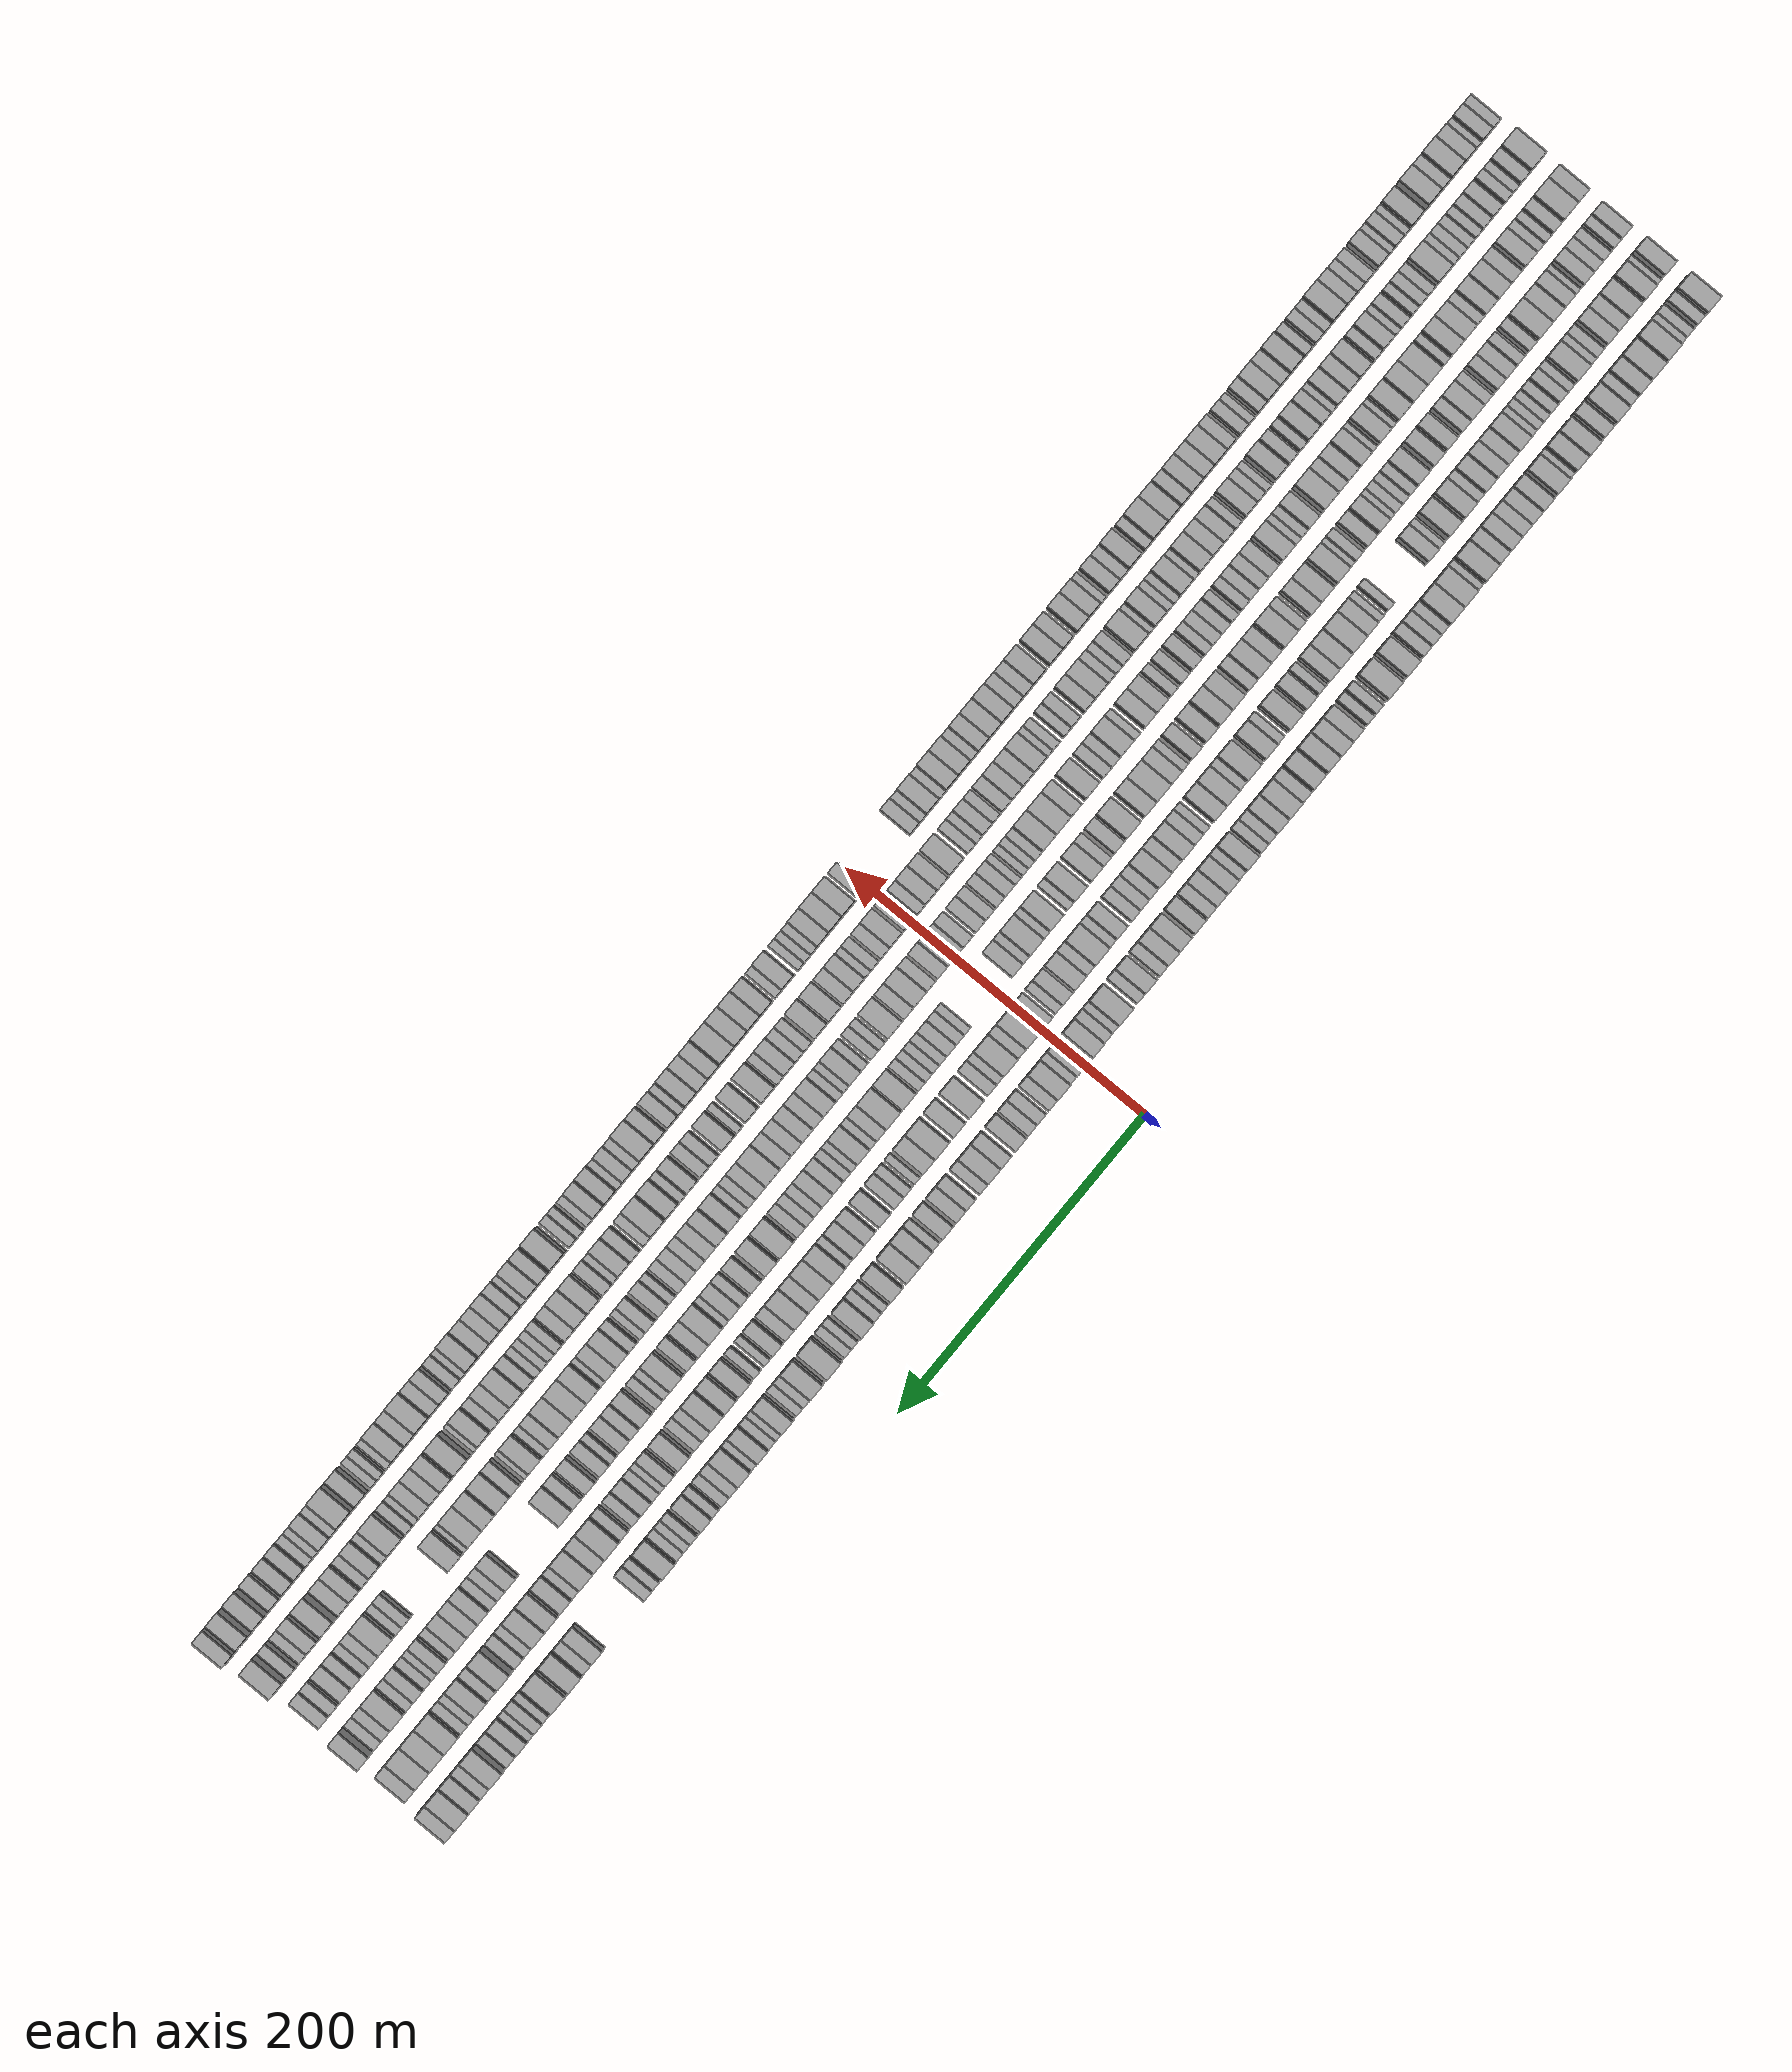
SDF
<sdf version="1.6">
 <world name="default">
  <scene>
   <sky><clouds><speed>12</speed></clouds></sky>
   <ambient>0.4 0.4 0.4 1</ambient>
   <background>0.7 0.7 0.7 1</background>
   <shadows>1</shadows>
  </scene>
  <gravity>0 0 -9.8066</gravity>
  <magnetic_field>6e-06 2.3e-05 -4.2e-05</magnetic_field>
  <physics default="0" name="default_physics" type="ode">
   <ode>
    <solver>
     <type>quick</type>
     <iters>10</iters>
     <sor>1.0</sor>
     <use_dynamic_moi_rescaling>0</use_dynamic_moi_rescaling>
    </solver>
    <constraints>
     <cfm>0</cfm>
     <erp>0.2</erp>
     <contact_max_correcting_vel>100</contact_max_correcting_vel>
     <contact_surface_layer>0.001</contact_surface_layer>
    </constraints>
   </ode>
   <max_step_size>0.004</max_step_size>
   <real_time_factor>1</real_time_factor>
   <real_time_update_rate>250</real_time_update_rate>
  </physics>
  <light name="sun" type="directional">
   <pose>0 0 10 0 0 0</pose>
   <diffuse>0.8 0.8 0.8 1</diffuse>
   <specular>0.2 0.2 0.2 1</specular>
   <attenuation>
    <range>1000</range>
    <constant>0.9</constant>
    <linear>0.01</linear>
    <quadratic>0.001</quadratic>
   </attenuation>
   <direction>-0.5 0.1 -0.9</direction>
  </light>
  <model name="building_1">
   <static>1</static>
   <pose>50.0000 -504.5952 0 0.000000 0.000000 0.000000</pose>
   <link name="link">
    <pose>0 0 12.00 0 0 0</pose>
    <collision name="collision"><geometry><box><size>20.0000 10.8095 24.0000</size></box></geometry></collision>
    <visual name="visual">
     <cast_shadows>0</cast_shadows>
     <geometry><box><size>20.0000 10.8095 24.0000</size></box></geometry>
     <material>
      <script>
       <uri>model://grey_wall/materials/scripts</uri>
       <uri>model://grey_wall/materials/textures</uri>
       <name>vrc/grey_wall</name>
      </script>
     </material>
    </visual>
   </link>
  </model>
  <model name="building_2">
   <static>1</static>
   <pose>50.0000 -495.9413 0 0.000000 0.000000 0.000000</pose>
   <link name="link">
    <pose>0 0 7.50 0 0 0</pose>
    <collision name="collision"><geometry><box><size>20.0000 6.4983 15.0000</size></box></geometry></collision>
    <visual name="visual">
     <cast_shadows>0</cast_shadows>
     <geometry><box><size>20.0000 6.4983 15.0000</size></box></geometry>
     <material>
      <script>
       <uri>model://grey_wall/materials/scripts</uri>
       <uri>model://grey_wall/materials/textures</uri>
       <name>vrc/grey_wall</name>
      </script>
     </material>
    </visual>
   </link>
  </model>
  <model name="building_3">
   <static>1</static>
   <pose>50.0000 -487.8191 0 0.000000 0.000000 0.000000</pose>
   <link name="link">
    <pose>0 0 6.00 0 0 0</pose>
    <collision name="collision"><geometry><box><size>20.0000 5.7462 12.0000</size></box></geometry></collision>
    <visual name="visual">
     <cast_shadows>0</cast_shadows>
     <geometry><box><size>20.0000 5.7462 12.0000</size></box></geometry>
     <material>
      <script>
       <uri>model://grey_wall/materials/scripts</uri>
       <uri>model://grey_wall/materials/textures</uri>
       <name>vrc/grey_wall</name>
      </script>
     </material>
    </visual>
   </link>
  </model>
  <model name="building_4">
   <static>1</static>
   <pose>50.0000 -482.2013 0 0.000000 0.000000 0.000000</pose>
   <link name="link">
    <pose>0 0 6.00 0 0 0</pose>
    <collision name="collision"><geometry><box><size>20.0000 5.4893 12.0000</size></box></geometry></collision>
    <visual name="visual">
     <cast_shadows>0</cast_shadows>
     <geometry><box><size>20.0000 5.4893 12.0000</size></box></geometry>
     <material>
      <script>
       <uri>model://grey_wall/materials/scripts</uri>
       <uri>model://grey_wall/materials/textures</uri>
       <name>vrc/grey_wall</name>
      </script>
     </material>
    </visual>
   </link>
  </model>
  <model name="building_5">
   <static>1</static>
   <pose>50.0000 -472.9392 0 0.000000 0.000000 0.000000</pose>
   <link name="link">
    <pose>0 0 12.00 0 0 0</pose>
    <collision name="collision"><geometry><box><size>20.0000 11.0349 24.0000</size></box></geometry></collision>
    <visual name="visual">
     <cast_shadows>0</cast_shadows>
     <geometry><box><size>20.0000 11.0349 24.0000</size></box></geometry>
     <material>
      <script>
       <uri>model://grey_wall/materials/scripts</uri>
       <uri>model://grey_wall/materials/textures</uri>
       <name>vrc/grey_wall</name>
      </script>
     </material>
    </visual>
   </link>
  </model>
  <model name="building_6">
   <static>1</static>
   <pose>50.0000 -460.6347 0 0.000000 0.000000 0.000000</pose>
   <link name="link">
    <pose>0 0 12.00 0 0 0</pose>
    <collision name="collision"><geometry><box><size>20.0000 11.5740 24.0000</size></box></geometry></collision>
    <visual name="visual">
     <cast_shadows>0</cast_shadows>
     <geometry><box><size>20.0000 11.5740 24.0000</size></box></geometry>
     <material>
      <script>
       <uri>model://grey_wall/materials/scripts</uri>
       <uri>model://grey_wall/materials/textures</uri>
       <name>vrc/grey_wall</name>
      </script>
     </material>
    </visual>
   </link>
  </model>
  <model name="building_7">
   <static>1</static>
   <pose>50.0000 -450.0539 0 0.000000 0.000000 0.000000</pose>
   <link name="link">
    <pose>0 0 10.50 0 0 0</pose>
    <collision name="collision"><geometry><box><size>20.0000 9.5876 21.0000</size></box></geometry></collision>
    <visual name="visual">
     <cast_shadows>0</cast_shadows>
     <geometry><box><size>20.0000 9.5876 21.0000</size></box></geometry>
     <material>
      <script>
       <uri>model://grey_wall/materials/scripts</uri>
       <uri>model://grey_wall/materials/textures</uri>
       <name>vrc/grey_wall</name>
      </script>
     </material>
    </visual>
   </link>
  </model>
  <model name="building_8">
   <static>1</static>
   <pose>50.0000 -442.0998 0 0.000000 0.000000 0.000000</pose>
   <link name="link">
    <pose>0 0 7.50 0 0 0</pose>
    <collision name="collision"><geometry><box><size>20.0000 6.3206 15.0000</size></box></geometry></collision>
    <visual name="visual">
     <cast_shadows>0</cast_shadows>
     <geometry><box><size>20.0000 6.3206 15.0000</size></box></geometry>
     <material>
      <script>
       <uri>model://grey_wall/materials/scripts</uri>
       <uri>model://grey_wall/materials/textures</uri>
       <name>vrc/grey_wall</name>
      </script>
     </material>
    </visual>
   </link>
  </model>
  <model name="building_9">
   <static>1</static>
   <pose>50.0000 -431.6777 0 0.000000 0.000000 0.000000</pose>
   <link name="link">
    <pose>0 0 12.00 0 0 0</pose>
    <collision name="collision"><geometry><box><size>20.0000 10.5235 24.0000</size></box></geometry></collision>
    <visual name="visual">
     <cast_shadows>0</cast_shadows>
     <geometry><box><size>20.0000 10.5235 24.0000</size></box></geometry>
     <material>
      <script>
       <uri>model://grey_wall/materials/scripts</uri>
       <uri>model://grey_wall/materials/textures</uri>
       <name>vrc/grey_wall</name>
      </script>
     </material>
    </visual>
   </link>
  </model>
  <model name="building_10">
   <static>1</static>
   <pose>50.0000 -421.2742 0 0.000000 0.000000 0.000000</pose>
   <link name="link">
    <pose>0 0 9.00 0 0 0</pose>
    <collision name="collision"><geometry><box><size>20.0000 8.2835 18.0000</size></box></geometry></collision>
    <visual name="visual">
     <cast_shadows>0</cast_shadows>
     <geometry><box><size>20.0000 8.2835 18.0000</size></box></geometry>
     <material>
      <script>
       <uri>model://grey_wall/materials/scripts</uri>
       <uri>model://grey_wall/materials/textures</uri>
       <name>vrc/grey_wall</name>
      </script>
     </material>
    </visual>
   </link>
  </model>
  <model name="building_11">
   <static>1</static>
   <pose>50.0000 -409.3301 0 0.000000 0.000000 0.000000</pose>
   <link name="link">
    <pose>0 0 12.00 0 0 0</pose>
    <collision name="collision"><geometry><box><size>20.0000 9.6047 24.0000</size></box></geometry></collision>
    <visual name="visual">
     <cast_shadows>0</cast_shadows>
     <geometry><box><size>20.0000 9.6047 24.0000</size></box></geometry>
     <material>
      <script>
       <uri>model://grey_wall/materials/scripts</uri>
       <uri>model://grey_wall/materials/textures</uri>
       <name>vrc/grey_wall</name>
      </script>
     </material>
    </visual>
   </link>
  </model>
  <model name="building_12">
   <static>1</static>
   <pose>50.0000 -399.6689 0 0.000000 0.000000 0.000000</pose>
   <link name="link">
    <pose>0 0 10.50 0 0 0</pose>
    <collision name="collision"><geometry><box><size>20.0000 9.7177 21.0000</size></box></geometry></collision>
    <visual name="visual">
     <cast_shadows>0</cast_shadows>
     <geometry><box><size>20.0000 9.7177 21.0000</size></box></geometry>
     <material>
      <script>
       <uri>model://grey_wall/materials/scripts</uri>
       <uri>model://grey_wall/materials/textures</uri>
       <name>vrc/grey_wall</name>
      </script>
     </material>
    </visual>
   </link>
  </model>
  <model name="building_13">
   <static>1</static>
   <pose>50.0000 -391.9871 0 0.000000 0.000000 0.000000</pose>
   <link name="link">
    <pose>0 0 6.00 0 0 0</pose>
    <collision name="collision"><geometry><box><size>20.0000 5.6458 12.0000</size></box></geometry></collision>
    <visual name="visual">
     <cast_shadows>0</cast_shadows>
     <geometry><box><size>20.0000 5.6458 12.0000</size></box></geometry>
     <material>
      <script>
       <uri>model://grey_wall/materials/scripts</uri>
       <uri>model://grey_wall/materials/textures</uri>
       <name>vrc/grey_wall</name>
      </script>
     </material>
    </visual>
   </link>
  </model>
  <model name="building_14">
   <static>1</static>
   <pose>50.0000 -383.9523 0 0.000000 0.000000 0.000000</pose>
   <link name="link">
    <pose>0 0 12.00 0 0 0</pose>
    <collision name="collision"><geometry><box><size>20.0000 10.4239 24.0000</size></box></geometry></collision>
    <visual name="visual">
     <cast_shadows>0</cast_shadows>
     <geometry><box><size>20.0000 10.4239 24.0000</size></box></geometry>
     <material>
      <script>
       <uri>model://grey_wall/materials/scripts</uri>
       <uri>model://grey_wall/materials/textures</uri>
       <name>vrc/grey_wall</name>
      </script>
     </material>
    </visual>
   </link>
  </model>
  <model name="building_15">
   <static>1</static>
   <pose>50.0000 -372.4030 0 0.000000 0.000000 0.000000</pose>
   <link name="link">
    <pose>0 0 10.50 0 0 0</pose>
    <collision name="collision"><geometry><box><size>20.0000 8.6746 21.0000</size></box></geometry></collision>
    <visual name="visual">
     <cast_shadows>0</cast_shadows>
     <geometry><box><size>20.0000 8.6746 21.0000</size></box></geometry>
     <material>
      <script>
       <uri>model://grey_wall/materials/scripts</uri>
       <uri>model://grey_wall/materials/textures</uri>
       <name>vrc/grey_wall</name>
      </script>
     </material>
    </visual>
   </link>
  </model>
  <model name="building_16">
   <static>1</static>
   <pose>50.0000 -363.7755 0 0.000000 0.000000 0.000000</pose>
   <link name="link">
    <pose>0 0 9.00 0 0 0</pose>
    <collision name="collision"><geometry><box><size>20.0000 8.5804 18.0000</size></box></geometry></collision>
    <visual name="visual">
     <cast_shadows>0</cast_shadows>
     <geometry><box><size>20.0000 8.5804 18.0000</size></box></geometry>
     <material>
      <script>
       <uri>model://grey_wall/materials/scripts</uri>
       <uri>model://grey_wall/materials/textures</uri>
       <name>vrc/grey_wall</name>
      </script>
     </material>
    </visual>
   </link>
  </model>
  <model name="building_17">
   <static>1</static>
   <pose>50.0000 -355.1948 0 0.000000 0.000000 0.000000</pose>
   <link name="link">
    <pose>0 0 9.00 0 0 0</pose>
    <collision name="collision"><geometry><box><size>20.0000 8.5810 18.0000</size></box></geometry></collision>
    <visual name="visual">
     <cast_shadows>0</cast_shadows>
     <geometry><box><size>20.0000 8.5810 18.0000</size></box></geometry>
     <material>
      <script>
       <uri>model://grey_wall/materials/scripts</uri>
       <uri>model://grey_wall/materials/textures</uri>
       <name>vrc/grey_wall</name>
      </script>
     </material>
    </visual>
   </link>
  </model>
  <model name="building_18">
   <static>1</static>
   <pose>50.0000 -346.3274 0 0.000000 0.000000 0.000000</pose>
   <link name="link">
    <pose>0 0 10.50 0 0 0</pose>
    <collision name="collision"><geometry><box><size>20.0000 9.1539 21.0000</size></box></geometry></collision>
    <visual name="visual">
     <cast_shadows>0</cast_shadows>
     <geometry><box><size>20.0000 9.1539 21.0000</size></box></geometry>
     <material>
      <script>
       <uri>model://grey_wall/materials/scripts</uri>
       <uri>model://grey_wall/materials/textures</uri>
       <name>vrc/grey_wall</name>
      </script>
     </material>
    </visual>
   </link>
  </model>
  <model name="building_19">
   <static>1</static>
   <pose>50.0000 -337.5470 0 0.000000 0.000000 0.000000</pose>
   <link name="link">
    <pose>0 0 9.00 0 0 0</pose>
    <collision name="collision"><geometry><box><size>20.0000 8.4068 18.0000</size></box></geometry></collision>
    <visual name="visual">
     <cast_shadows>0</cast_shadows>
     <geometry><box><size>20.0000 8.4068 18.0000</size></box></geometry>
     <material>
      <script>
       <uri>model://grey_wall/materials/scripts</uri>
       <uri>model://grey_wall/materials/textures</uri>
       <name>vrc/grey_wall</name>
      </script>
     </material>
    </visual>
   </link>
  </model>
  <model name="building_20">
   <static>1</static>
   <pose>50.0000 -326.6744 0 0.000000 0.000000 0.000000</pose>
   <link name="link">
    <pose>0 0 12.00 0 0 0</pose>
    <collision name="collision"><geometry><box><size>20.0000 11.3383 24.0000</size></box></geometry></collision>
    <visual name="visual">
     <cast_shadows>0</cast_shadows>
     <geometry><box><size>20.0000 11.3383 24.0000</size></box></geometry>
     <material>
      <script>
       <uri>model://grey_wall/materials/scripts</uri>
       <uri>model://grey_wall/materials/textures</uri>
       <name>vrc/grey_wall</name>
      </script>
     </material>
    </visual>
   </link>
  </model>
  <model name="building_21">
   <static>1</static>
   <pose>50.0000 -318.1015 0 0.000000 0.000000 0.000000</pose>
   <link name="link">
    <pose>0 0 6.00 0 0 0</pose>
    <collision name="collision"><geometry><box><size>20.0000 5.8074 12.0000</size></box></geometry></collision>
    <visual name="visual">
     <cast_shadows>0</cast_shadows>
     <geometry><box><size>20.0000 5.8074 12.0000</size></box></geometry>
     <material>
      <script>
       <uri>model://grey_wall/materials/scripts</uri>
       <uri>model://grey_wall/materials/textures</uri>
       <name>vrc/grey_wall</name>
      </script>
     </material>
    </visual>
   </link>
  </model>
  <model name="building_22">
   <static>1</static>
   <pose>50.0000 -309.6089 0 0.000000 0.000000 0.000000</pose>
   <link name="link">
    <pose>0 0 12.00 0 0 0</pose>
    <collision name="collision"><geometry><box><size>20.0000 11.1778 24.0000</size></box></geometry></collision>
    <visual name="visual">
     <cast_shadows>0</cast_shadows>
     <geometry><box><size>20.0000 11.1778 24.0000</size></box></geometry>
     <material>
      <script>
       <uri>model://grey_wall/materials/scripts</uri>
       <uri>model://grey_wall/materials/textures</uri>
       <name>vrc/grey_wall</name>
      </script>
     </material>
    </visual>
   </link>
  </model>
  <model name="building_23">
   <static>1</static>
   <pose>50.0000 -298.4806 0 0.000000 0.000000 0.000000</pose>
   <link name="link">
    <pose>0 0 12.00 0 0 0</pose>
    <collision name="collision"><geometry><box><size>20.0000 11.0788 24.0000</size></box></geometry></collision>
    <visual name="visual">
     <cast_shadows>0</cast_shadows>
     <geometry><box><size>20.0000 11.0788 24.0000</size></box></geometry>
     <material>
      <script>
       <uri>model://grey_wall/materials/scripts</uri>
       <uri>model://grey_wall/materials/textures</uri>
       <name>vrc/grey_wall</name>
      </script>
     </material>
    </visual>
   </link>
  </model>
  <model name="building_24">
   <static>1</static>
   <pose>50.0000 -289.6644 0 0.000000 0.000000 0.000000</pose>
   <link name="link">
    <pose>0 0 7.50 0 0 0</pose>
    <collision name="collision"><geometry><box><size>20.0000 6.5535 15.0000</size></box></geometry></collision>
    <visual name="visual">
     <cast_shadows>0</cast_shadows>
     <geometry><box><size>20.0000 6.5535 15.0000</size></box></geometry>
     <material>
      <script>
       <uri>model://grey_wall/materials/scripts</uri>
       <uri>model://grey_wall/materials/textures</uri>
       <name>vrc/grey_wall</name>
      </script>
     </material>
    </visual>
   </link>
  </model>
  <model name="building_25">
   <static>1</static>
   <pose>50.0000 -282.7002 0 0.000000 0.000000 0.000000</pose>
   <link name="link">
    <pose>0 0 9.00 0 0 0</pose>
    <collision name="collision"><geometry><box><size>20.0000 7.3748 18.0000</size></box></geometry></collision>
    <visual name="visual">
     <cast_shadows>0</cast_shadows>
     <geometry><box><size>20.0000 7.3748 18.0000</size></box></geometry>
     <material>
      <script>
       <uri>model://grey_wall/materials/scripts</uri>
       <uri>model://grey_wall/materials/textures</uri>
       <name>vrc/grey_wall</name>
      </script>
     </material>
    </visual>
   </link>
  </model>
  <model name="building_26">
   <static>1</static>
   <pose>50.0000 -275.4517 0 0.000000 0.000000 0.000000</pose>
   <link name="link">
    <pose>0 0 7.50 0 0 0</pose>
    <collision name="collision"><geometry><box><size>20.0000 7.1223 15.0000</size></box></geometry></collision>
    <visual name="visual">
     <cast_shadows>0</cast_shadows>
     <geometry><box><size>20.0000 7.1223 15.0000</size></box></geometry>
     <material>
      <script>
       <uri>model://grey_wall/materials/scripts</uri>
       <uri>model://grey_wall/materials/textures</uri>
       <name>vrc/grey_wall</name>
      </script>
     </material>
    </visual>
   </link>
  </model>
  <model name="building_27">
   <static>1</static>
   <pose>50.0000 -263.3856 0 0.000000 0.000000 0.000000</pose>
   <link name="link">
    <pose>0 0 12.00 0 0 0</pose>
    <collision name="collision"><geometry><box><size>20.0000 11.0098 24.0000</size></box></geometry></collision>
    <visual name="visual">
     <cast_shadows>0</cast_shadows>
     <geometry><box><size>20.0000 11.0098 24.0000</size></box></geometry>
     <material>
      <script>
       <uri>model://grey_wall/materials/scripts</uri>
       <uri>model://grey_wall/materials/textures</uri>
       <name>vrc/grey_wall</name>
      </script>
     </material>
    </visual>
   </link>
  </model>
  <model name="building_28">
   <static>1</static>
   <pose>50.0000 -248.9722 0 0.000000 0.000000 0.000000</pose>
   <link name="link">
    <pose>0 0 12.00 0 0 0</pose>
    <collision name="collision"><geometry><box><size>20.0000 11.8172 24.0000</size></box></geometry></collision>
    <visual name="visual">
     <cast_shadows>0</cast_shadows>
     <geometry><box><size>20.0000 11.8172 24.0000</size></box></geometry>
     <material>
      <script>
       <uri>model://grey_wall/materials/scripts</uri>
       <uri>model://grey_wall/materials/textures</uri>
       <name>vrc/grey_wall</name>
      </script>
     </material>
    </visual>
   </link>
  </model>
  <model name="building_29">
   <static>1</static>
   <pose>50.0000 -236.9914 0 0.000000 0.000000 0.000000</pose>
   <link name="link">
    <pose>0 0 7.50 0 0 0</pose>
    <collision name="collision"><geometry><box><size>20.0000 6.1445 15.0000</size></box></geometry></collision>
    <visual name="visual">
     <cast_shadows>0</cast_shadows>
     <geometry><box><size>20.0000 6.1445 15.0000</size></box></geometry>
     <material>
      <script>
       <uri>model://grey_wall/materials/scripts</uri>
       <uri>model://grey_wall/materials/textures</uri>
       <name>vrc/grey_wall</name>
      </script>
     </material>
    </visual>
   </link>
  </model>
  <model name="building_30">
   <static>1</static>
   <pose>50.0000 -229.8097 0 0.000000 0.000000 0.000000</pose>
   <link name="link">
    <pose>0 0 7.50 0 0 0</pose>
    <collision name="collision"><geometry><box><size>20.0000 6.2188 15.0000</size></box></geometry></collision>
    <visual name="visual">
     <cast_shadows>0</cast_shadows>
     <geometry><box><size>20.0000 6.2188 15.0000</size></box></geometry>
     <material>
      <script>
       <uri>model://grey_wall/materials/scripts</uri>
       <uri>model://grey_wall/materials/textures</uri>
       <name>vrc/grey_wall</name>
      </script>
     </material>
    </visual>
   </link>
  </model>
  <model name="building_31">
   <static>1</static>
   <pose>50.0000 -219.2244 0 0.000000 0.000000 0.000000</pose>
   <link name="link">
    <pose>0 0 10.50 0 0 0</pose>
    <collision name="collision"><geometry><box><size>20.0000 8.9518 21.0000</size></box></geometry></collision>
    <visual name="visual">
     <cast_shadows>0</cast_shadows>
     <geometry><box><size>20.0000 8.9518 21.0000</size></box></geometry>
     <material>
      <script>
       <uri>model://grey_wall/materials/scripts</uri>
       <uri>model://grey_wall/materials/textures</uri>
       <name>vrc/grey_wall</name>
      </script>
     </material>
    </visual>
   </link>
  </model>
  <model name="building_32">
   <static>1</static>
   <pose>50.0000 -209.8874 0 0.000000 0.000000 0.000000</pose>
   <link name="link">
    <pose>0 0 12.00 0 0 0</pose>
    <collision name="collision"><geometry><box><size>20.0000 9.7222 24.0000</size></box></geometry></collision>
    <visual name="visual">
     <cast_shadows>0</cast_shadows>
     <geometry><box><size>20.0000 9.7222 24.0000</size></box></geometry>
     <material>
      <script>
       <uri>model://grey_wall/materials/scripts</uri>
       <uri>model://grey_wall/materials/textures</uri>
       <name>vrc/grey_wall</name>
      </script>
     </material>
    </visual>
   </link>
  </model>
  <model name="building_33">
   <static>1</static>
   <pose>50.0000 -199.8392 0 0.000000 0.000000 0.000000</pose>
   <link name="link">
    <pose>0 0 10.50 0 0 0</pose>
    <collision name="collision"><geometry><box><size>20.0000 10.3742 21.0000</size></box></geometry></collision>
    <visual name="visual">
     <cast_shadows>0</cast_shadows>
     <geometry><box><size>20.0000 10.3742 21.0000</size></box></geometry>
     <material>
      <script>
       <uri>model://grey_wall/materials/scripts</uri>
       <uri>model://grey_wall/materials/textures</uri>
       <name>vrc/grey_wall</name>
      </script>
     </material>
    </visual>
   </link>
  </model>
  <model name="building_34">
   <static>1</static>
   <pose>50.0000 -188.4460 0 0.000000 0.000000 0.000000</pose>
   <link name="link">
    <pose>0 0 10.50 0 0 0</pose>
    <collision name="collision"><geometry><box><size>20.0000 10.4123 21.0000</size></box></geometry></collision>
    <visual name="visual">
     <cast_shadows>0</cast_shadows>
     <geometry><box><size>20.0000 10.4123 21.0000</size></box></geometry>
     <material>
      <script>
       <uri>model://grey_wall/materials/scripts</uri>
       <uri>model://grey_wall/materials/textures</uri>
       <name>vrc/grey_wall</name>
      </script>
     </material>
    </visual>
   </link>
  </model>
  <model name="building_35">
   <static>1</static>
   <pose>50.0000 -178.2907 0 0.000000 0.000000 0.000000</pose>
   <link name="link">
    <pose>0 0 9.00 0 0 0</pose>
    <collision name="collision"><geometry><box><size>20.0000 7.8982 18.0000</size></box></geometry></collision>
    <visual name="visual">
     <cast_shadows>0</cast_shadows>
     <geometry><box><size>20.0000 7.8982 18.0000</size></box></geometry>
     <material>
      <script>
       <uri>model://grey_wall/materials/scripts</uri>
       <uri>model://grey_wall/materials/textures</uri>
       <name>vrc/grey_wall</name>
      </script>
     </material>
    </visual>
   </link>
  </model>
  <model name="building_36">
   <static>1</static>
   <pose>50.0000 -168.9871 0 0.000000 0.000000 0.000000</pose>
   <link name="link">
    <pose>0 0 12.00 0 0 0</pose>
    <collision name="collision"><geometry><box><size>20.0000 10.7090 24.0000</size></box></geometry></collision>
    <visual name="visual">
     <cast_shadows>0</cast_shadows>
     <geometry><box><size>20.0000 10.7090 24.0000</size></box></geometry>
     <material>
      <script>
       <uri>model://grey_wall/materials/scripts</uri>
       <uri>model://grey_wall/materials/textures</uri>
       <name>vrc/grey_wall</name>
      </script>
     </material>
    </visual>
   </link>
  </model>
  <model name="building_37">
   <static>1</static>
   <pose>50.0000 -158.9205 0 0.000000 0.000000 0.000000</pose>
   <link name="link">
    <pose>0 0 10.50 0 0 0</pose>
    <collision name="collision"><geometry><box><size>20.0000 9.4243 21.0000</size></box></geometry></collision>
    <visual name="visual">
     <cast_shadows>0</cast_shadows>
     <geometry><box><size>20.0000 9.4243 21.0000</size></box></geometry>
     <material>
      <script>
       <uri>model://grey_wall/materials/scripts</uri>
       <uri>model://grey_wall/materials/textures</uri>
       <name>vrc/grey_wall</name>
      </script>
     </material>
    </visual>
   </link>
  </model>
  <model name="building_38">
   <static>1</static>
   <pose>50.0000 -150.8757 0 0.000000 0.000000 0.000000</pose>
   <link name="link">
    <pose>0 0 7.50 0 0 0</pose>
    <collision name="collision"><geometry><box><size>20.0000 6.6653 15.0000</size></box></geometry></collision>
    <visual name="visual">
     <cast_shadows>0</cast_shadows>
     <geometry><box><size>20.0000 6.6653 15.0000</size></box></geometry>
     <material>
      <script>
       <uri>model://grey_wall/materials/scripts</uri>
       <uri>model://grey_wall/materials/textures</uri>
       <name>vrc/grey_wall</name>
      </script>
     </material>
    </visual>
   </link>
  </model>
  <model name="building_39">
   <static>1</static>
   <pose>50.0000 -144.4298 0 0.000000 0.000000 0.000000</pose>
   <link name="link">
    <pose>0 0 7.50 0 0 0</pose>
    <collision name="collision"><geometry><box><size>20.0000 6.2264 15.0000</size></box></geometry></collision>
    <visual name="visual">
     <cast_shadows>0</cast_shadows>
     <geometry><box><size>20.0000 6.2264 15.0000</size></box></geometry>
     <material>
      <script>
       <uri>model://grey_wall/materials/scripts</uri>
       <uri>model://grey_wall/materials/textures</uri>
       <name>vrc/grey_wall</name>
      </script>
     </material>
    </visual>
   </link>
  </model>
  <model name="building_40">
   <static>1</static>
   <pose>50.0000 -134.3882 0 0.000000 0.000000 0.000000</pose>
   <link name="link">
    <pose>0 0 12.00 0 0 0</pose>
    <collision name="collision"><geometry><box><size>20.0000 9.8568 24.0000</size></box></geometry></collision>
    <visual name="visual">
     <cast_shadows>0</cast_shadows>
     <geometry><box><size>20.0000 9.8568 24.0000</size></box></geometry>
     <material>
      <script>
       <uri>model://grey_wall/materials/scripts</uri>
       <uri>model://grey_wall/materials/textures</uri>
       <name>vrc/grey_wall</name>
      </script>
     </material>
    </visual>
   </link>
  </model>
  <model name="building_41">
   <static>1</static>
   <pose>50.0000 -126.4257 0 0.000000 0.000000 0.000000</pose>
   <link name="link">
    <pose>0 0 7.50 0 0 0</pose>
    <collision name="collision"><geometry><box><size>20.0000 6.0681 15.0000</size></box></geometry></collision>
    <visual name="visual">
     <cast_shadows>0</cast_shadows>
     <geometry><box><size>20.0000 6.0681 15.0000</size></box></geometry>
     <material>
      <script>
       <uri>model://grey_wall/materials/scripts</uri>
       <uri>model://grey_wall/materials/textures</uri>
       <name>vrc/grey_wall</name>
      </script>
     </material>
    </visual>
   </link>
  </model>
  <model name="building_42">
   <static>1</static>
   <pose>50.0000 -118.7249 0 0.000000 0.000000 0.000000</pose>
   <link name="link">
    <pose>0 0 10.50 0 0 0</pose>
    <collision name="collision"><geometry><box><size>20.0000 9.3334 21.0000</size></box></geometry></collision>
    <visual name="visual">
     <cast_shadows>0</cast_shadows>
     <geometry><box><size>20.0000 9.3334 21.0000</size></box></geometry>
     <material>
      <script>
       <uri>model://grey_wall/materials/scripts</uri>
       <uri>model://grey_wall/materials/textures</uri>
       <name>vrc/grey_wall</name>
      </script>
     </material>
    </visual>
   </link>
  </model>
  <model name="building_43">
   <static>1</static>
   <pose>50.0000 -109.7902 0 0.000000 0.000000 0.000000</pose>
   <link name="link">
    <pose>0 0 9.00 0 0 0</pose>
    <collision name="collision"><geometry><box><size>20.0000 8.5362 18.0000</size></box></geometry></collision>
    <visual name="visual">
     <cast_shadows>0</cast_shadows>
     <geometry><box><size>20.0000 8.5362 18.0000</size></box></geometry>
     <material>
      <script>
       <uri>model://grey_wall/materials/scripts</uri>
       <uri>model://grey_wall/materials/textures</uri>
       <name>vrc/grey_wall</name>
      </script>
     </material>
    </visual>
   </link>
  </model>
  <model name="building_44">
   <static>1</static>
   <pose>50.0000 -101.7398 0 0.000000 0.000000 0.000000</pose>
   <link name="link">
    <pose>0 0 9.00 0 0 0</pose>
    <collision name="collision"><geometry><box><size>20.0000 7.5646 18.0000</size></box></geometry></collision>
    <visual name="visual">
     <cast_shadows>0</cast_shadows>
     <geometry><box><size>20.0000 7.5646 18.0000</size></box></geometry>
     <material>
      <script>
       <uri>model://grey_wall/materials/scripts</uri>
       <uri>model://grey_wall/materials/textures</uri>
       <name>vrc/grey_wall</name>
      </script>
     </material>
    </visual>
   </link>
  </model>
  <model name="building_45">
   <static>1</static>
   <pose>50.0000 -92.1891 0 0.000000 0.000000 0.000000</pose>
   <link name="link">
    <pose>0 0 10.50 0 0 0</pose>
    <collision name="collision"><geometry><box><size>20.0000 9.5367 21.0000</size></box></geometry></collision>
    <visual name="visual">
     <cast_shadows>0</cast_shadows>
     <geometry><box><size>20.0000 9.5367 21.0000</size></box></geometry>
     <material>
      <script>
       <uri>model://grey_wall/materials/scripts</uri>
       <uri>model://grey_wall/materials/textures</uri>
       <name>vrc/grey_wall</name>
      </script>
     </material>
    </visual>
   </link>
  </model>
  <model name="building_46">
   <static>1</static>
   <pose>50.0000 -80.4758 0 0.000000 0.000000 0.000000</pose>
   <link name="link">
    <pose>0 0 10.50 0 0 0</pose>
    <collision name="collision"><geometry><box><size>20.0000 9.8900 21.0000</size></box></geometry></collision>
    <visual name="visual">
     <cast_shadows>0</cast_shadows>
     <geometry><box><size>20.0000 9.8900 21.0000</size></box></geometry>
     <material>
      <script>
       <uri>model://grey_wall/materials/scripts</uri>
       <uri>model://grey_wall/materials/textures</uri>
       <name>vrc/grey_wall</name>
      </script>
     </material>
    </visual>
   </link>
  </model>
  <model name="building_47">
   <static>1</static>
   <pose>50.0000 -70.9077 0 0.000000 0.000000 0.000000</pose>
   <link name="link">
    <pose>0 0 10.50 0 0 0</pose>
    <collision name="collision"><geometry><box><size>20.0000 9.2462 21.0000</size></box></geometry></collision>
    <visual name="visual">
     <cast_shadows>0</cast_shadows>
     <geometry><box><size>20.0000 9.2462 21.0000</size></box></geometry>
     <material>
      <script>
       <uri>model://grey_wall/materials/scripts</uri>
       <uri>model://grey_wall/materials/textures</uri>
       <name>vrc/grey_wall</name>
      </script>
     </material>
    </visual>
   </link>
  </model>
  <model name="building_48">
   <static>1</static>
   <pose>50.0000 -62.8196 0 0.000000 0.000000 0.000000</pose>
   <link name="link">
    <pose>0 0 7.50 0 0 0</pose>
    <collision name="collision"><geometry><box><size>20.0000 6.9300 15.0000</size></box></geometry></collision>
    <visual name="visual">
     <cast_shadows>0</cast_shadows>
     <geometry><box><size>20.0000 6.9300 15.0000</size></box></geometry>
     <material>
      <script>
       <uri>model://grey_wall/materials/scripts</uri>
       <uri>model://grey_wall/materials/textures</uri>
       <name>vrc/grey_wall</name>
      </script>
     </material>
    </visual>
   </link>
  </model>
  <model name="building_49">
   <static>1</static>
   <pose>50.0000 -52.5954 0 0.000000 0.000000 0.000000</pose>
   <link name="link">
    <pose>0 0 10.50 0 0 0</pose>
    <collision name="collision"><geometry><box><size>20.0000 9.5186 21.0000</size></box></geometry></collision>
    <visual name="visual">
     <cast_shadows>0</cast_shadows>
     <geometry><box><size>20.0000 9.5186 21.0000</size></box></geometry>
     <material>
      <script>
       <uri>model://grey_wall/materials/scripts</uri>
       <uri>model://grey_wall/materials/textures</uri>
       <name>vrc/grey_wall</name>
      </script>
     </material>
    </visual>
   </link>
  </model>
  <model name="building_50">
   <static>1</static>
   <pose>50.0000 -44.6159 0 0.000000 0.000000 0.000000</pose>
   <link name="link">
    <pose>0 0 7.50 0 0 0</pose>
    <collision name="collision"><geometry><box><size>20.0000 6.4404 15.0000</size></box></geometry></collision>
    <visual name="visual">
     <cast_shadows>0</cast_shadows>
     <geometry><box><size>20.0000 6.4404 15.0000</size></box></geometry>
     <material>
      <script>
       <uri>model://grey_wall/materials/scripts</uri>
       <uri>model://grey_wall/materials/textures</uri>
       <name>vrc/grey_wall</name>
      </script>
     </material>
    </visual>
   </link>
  </model>
  <model name="building_51">
   <static>1</static>
   <pose>50.0000 -32.5329 0 0.000000 0.000000 0.000000</pose>
   <link name="link">
    <pose>0 0 12.00 0 0 0</pose>
    <collision name="collision"><geometry><box><size>20.0000 11.7255 24.0000</size></box></geometry></collision>
    <visual name="visual">
     <cast_shadows>0</cast_shadows>
     <geometry><box><size>20.0000 11.7255 24.0000</size></box></geometry>
     <material>
      <script>
       <uri>model://grey_wall/materials/scripts</uri>
       <uri>model://grey_wall/materials/textures</uri>
       <name>vrc/grey_wall</name>
      </script>
     </material>
    </visual>
   </link>
  </model>
  <model name="building_52">
   <static>1</static>
   <pose>50.0000 -24.2009 0 0.000000 0.000000 0.000000</pose>
   <link name="link">
    <pose>0 0 6.00 0 0 0</pose>
    <collision name="collision"><geometry><box><size>20.0000 4.9386 12.0000</size></box></geometry></collision>
    <visual name="visual">
     <cast_shadows>0</cast_shadows>
     <geometry><box><size>20.0000 4.9386 12.0000</size></box></geometry>
     <material>
      <script>
       <uri>model://grey_wall/materials/scripts</uri>
       <uri>model://grey_wall/materials/textures</uri>
       <name>vrc/grey_wall</name>
      </script>
     </material>
    </visual>
   </link>
  </model>
  <model name="building_53">
   <static>1</static>
   <pose>50.0000 -18.4203 0 0.000000 0.000000 0.000000</pose>
   <link name="link">
    <pose>0 0 7.50 0 0 0</pose>
    <collision name="collision"><geometry><box><size>20.0000 6.6225 15.0000</size></box></geometry></collision>
    <visual name="visual">
     <cast_shadows>0</cast_shadows>
     <geometry><box><size>20.0000 6.6225 15.0000</size></box></geometry>
     <material>
      <script>
       <uri>model://grey_wall/materials/scripts</uri>
       <uri>model://grey_wall/materials/textures</uri>
       <name>vrc/grey_wall</name>
      </script>
     </material>
    </visual>
   </link>
  </model>
  <model name="building_54">
   <static>1</static>
   <pose>50.0000 -10.2577 0 0.000000 0.000000 0.000000</pose>
   <link name="link">
    <pose>0 0 12.00 0 0 0</pose>
    <collision name="collision"><geometry><box><size>20.0000 9.7029 24.0000</size></box></geometry></collision>
    <visual name="visual">
     <cast_shadows>0</cast_shadows>
     <geometry><box><size>20.0000 9.7029 24.0000</size></box></geometry>
     <material>
      <script>
       <uri>model://grey_wall/materials/scripts</uri>
       <uri>model://grey_wall/materials/textures</uri>
       <name>vrc/grey_wall</name>
      </script>
     </material>
    </visual>
   </link>
  </model>
  <model name="building_55">
   <static>1</static>
   <pose>50.0000 1.8225 0 0.000000 0.000000 0.000000</pose>
   <link name="link">
    <pose>0 0 10.50 0 0 0</pose>
    <collision name="collision"><geometry><box><size>20.0000 10.4575 21.0000</size></box></geometry></collision>
    <visual name="visual">
     <cast_shadows>0</cast_shadows>
     <geometry><box><size>20.0000 10.4575 21.0000</size></box></geometry>
     <material>
      <script>
       <uri>model://grey_wall/materials/scripts</uri>
       <uri>model://grey_wall/materials/textures</uri>
       <name>vrc/grey_wall</name>
      </script>
     </material>
    </visual>
   </link>
  </model>
  <model name="building_56">
   <static>1</static>
   <pose>50.0000 9.7075 0 0.000000 0.000000 0.000000</pose>
   <link name="link">
    <pose>0 0 6.00 0 0 0</pose>
    <collision name="collision"><geometry><box><size>20.0000 5.3123 12.0000</size></box></geometry></collision>
    <visual name="visual">
     <cast_shadows>0</cast_shadows>
     <geometry><box><size>20.0000 5.3123 12.0000</size></box></geometry>
     <material>
      <script>
       <uri>model://grey_wall/materials/scripts</uri>
       <uri>model://grey_wall/materials/textures</uri>
       <name>vrc/grey_wall</name>
      </script>
     </material>
    </visual>
   </link>
  </model>
  <model name="building_57">
   <static>1</static>
   <pose>50.0000 17.5181 0 0.000000 0.000000 0.000000</pose>
   <link name="link">
    <pose>0 0 12.00 0 0 0</pose>
    <collision name="collision"><geometry><box><size>20.0000 10.3090 24.0000</size></box></geometry></collision>
    <visual name="visual">
     <cast_shadows>0</cast_shadows>
     <geometry><box><size>20.0000 10.3090 24.0000</size></box></geometry>
     <material>
      <script>
       <uri>model://grey_wall/materials/scripts</uri>
       <uri>model://grey_wall/materials/textures</uri>
       <name>vrc/grey_wall</name>
      </script>
     </material>
    </visual>
   </link>
  </model>
  <model name="building_58">
   <static>1</static>
   <pose>50.0000 26.2817 0 0.000000 0.000000 0.000000</pose>
   <link name="link">
    <pose>0 0 9.00 0 0 0</pose>
    <collision name="collision"><geometry><box><size>20.0000 7.2182 18.0000</size></box></geometry></collision>
    <visual name="visual">
     <cast_shadows>0</cast_shadows>
     <geometry><box><size>20.0000 7.2182 18.0000</size></box></geometry>
     <material>
      <script>
       <uri>model://grey_wall/materials/scripts</uri>
       <uri>model://grey_wall/materials/textures</uri>
       <name>vrc/grey_wall</name>
      </script>
     </material>
    </visual>
   </link>
  </model>
  <model name="building_59">
   <static>1</static>
   <pose>50.0000 35.5803 0 0.000000 0.000000 0.000000</pose>
   <link name="link">
    <pose>0 0 9.00 0 0 0</pose>
    <collision name="collision"><geometry><box><size>20.0000 7.3790 18.0000</size></box></geometry></collision>
    <visual name="visual">
     <cast_shadows>0</cast_shadows>
     <geometry><box><size>20.0000 7.3790 18.0000</size></box></geometry>
     <material>
      <script>
       <uri>model://grey_wall/materials/scripts</uri>
       <uri>model://grey_wall/materials/textures</uri>
       <name>vrc/grey_wall</name>
      </script>
     </material>
    </visual>
   </link>
  </model>
  <model name="building_60">
   <static>1</static>
   <pose>50.0000 43.0115 0 0.000000 0.000000 0.000000</pose>
   <link name="link">
    <pose>0 0 9.00 0 0 0</pose>
    <collision name="collision"><geometry><box><size>20.0000 7.4834 18.0000</size></box></geometry></collision>
    <visual name="visual">
     <cast_shadows>0</cast_shadows>
     <geometry><box><size>20.0000 7.4834 18.0000</size></box></geometry>
     <material>
      <script>
       <uri>model://grey_wall/materials/scripts</uri>
       <uri>model://grey_wall/materials/textures</uri>
       <name>vrc/grey_wall</name>
      </script>
     </material>
    </visual>
   </link>
  </model>
  <model name="building_61">
   <static>1</static>
   <pose>50.0000 52.3012 0 0.000000 0.000000 0.000000</pose>
   <link name="link">
    <pose>0 0 10.50 0 0 0</pose>
    <collision name="collision"><geometry><box><size>20.0000 9.0959 21.0000</size></box></geometry></collision>
    <visual name="visual">
     <cast_shadows>0</cast_shadows>
     <geometry><box><size>20.0000 9.0959 21.0000</size></box></geometry>
     <material>
      <script>
       <uri>model://grey_wall/materials/scripts</uri>
       <uri>model://grey_wall/materials/textures</uri>
       <name>vrc/grey_wall</name>
      </script>
     </material>
    </visual>
   </link>
  </model>
  <model name="building_62">
   <static>1</static>
   <pose>50.0000 64.0853 0 0.000000 0.000000 0.000000</pose>
   <link name="link">
    <pose>0 0 10.50 0 0 0</pose>
    <collision name="collision"><geometry><box><size>20.0000 8.4724 21.0000</size></box></geometry></collision>
    <visual name="visual">
     <cast_shadows>0</cast_shadows>
     <geometry><box><size>20.0000 8.4724 21.0000</size></box></geometry>
     <material>
      <script>
       <uri>model://grey_wall/materials/scripts</uri>
       <uri>model://grey_wall/materials/textures</uri>
       <name>vrc/grey_wall</name>
      </script>
     </material>
    </visual>
   </link>
  </model>
  <model name="building_63">
   <static>1</static>
   <pose>50.0000 73.5073 0 0.000000 0.000000 0.000000</pose>
   <link name="link">
    <pose>0 0 10.50 0 0 0</pose>
    <collision name="collision"><geometry><box><size>20.0000 10.3717 21.0000</size></box></geometry></collision>
    <visual name="visual">
     <cast_shadows>0</cast_shadows>
     <geometry><box><size>20.0000 10.3717 21.0000</size></box></geometry>
     <material>
      <script>
       <uri>model://grey_wall/materials/scripts</uri>
       <uri>model://grey_wall/materials/textures</uri>
       <name>vrc/grey_wall</name>
      </script>
     </material>
    </visual>
   </link>
  </model>
  <model name="building_64">
   <static>1</static>
   <pose>50.0000 82.1194 0 0.000000 0.000000 0.000000</pose>
   <link name="link">
    <pose>0 0 7.50 0 0 0</pose>
    <collision name="collision"><geometry><box><size>20.0000 6.8526 15.0000</size></box></geometry></collision>
    <visual name="visual">
     <cast_shadows>0</cast_shadows>
     <geometry><box><size>20.0000 6.8526 15.0000</size></box></geometry>
     <material>
      <script>
       <uri>model://grey_wall/materials/scripts</uri>
       <uri>model://grey_wall/materials/textures</uri>
       <name>vrc/grey_wall</name>
      </script>
     </material>
    </visual>
   </link>
  </model>
  <model name="building_65">
   <static>1</static>
   <pose>50.0000 92.4018 0 0.000000 0.000000 0.000000</pose>
   <link name="link">
    <pose>0 0 9.00 0 0 0</pose>
    <collision name="collision"><geometry><box><size>20.0000 7.7122 18.0000</size></box></geometry></collision>
    <visual name="visual">
     <cast_shadows>0</cast_shadows>
     <geometry><box><size>20.0000 7.7122 18.0000</size></box></geometry>
     <material>
      <script>
       <uri>model://grey_wall/materials/scripts</uri>
       <uri>model://grey_wall/materials/textures</uri>
       <name>vrc/grey_wall</name>
      </script>
     </material>
    </visual>
   </link>
  </model>
  <model name="building_66">
   <static>1</static>
   <pose>50.0000 100.4794 0 0.000000 0.000000 0.000000</pose>
   <link name="link">
    <pose>0 0 9.00 0 0 0</pose>
    <collision name="collision"><geometry><box><size>20.0000 8.4429 18.0000</size></box></geometry></collision>
    <visual name="visual">
     <cast_shadows>0</cast_shadows>
     <geometry><box><size>20.0000 8.4429 18.0000</size></box></geometry>
     <material>
      <script>
       <uri>model://grey_wall/materials/scripts</uri>
       <uri>model://grey_wall/materials/textures</uri>
       <name>vrc/grey_wall</name>
      </script>
     </material>
    </visual>
   </link>
  </model>
  <model name="building_67">
   <static>1</static>
   <pose>50.0000 111.1929 0 0.000000 0.000000 0.000000</pose>
   <link name="link">
    <pose>0 0 9.00 0 0 0</pose>
    <collision name="collision"><geometry><box><size>20.0000 8.9841 18.0000</size></box></geometry></collision>
    <visual name="visual">
     <cast_shadows>0</cast_shadows>
     <geometry><box><size>20.0000 8.9841 18.0000</size></box></geometry>
     <material>
      <script>
       <uri>model://grey_wall/materials/scripts</uri>
       <uri>model://grey_wall/materials/textures</uri>
       <name>vrc/grey_wall</name>
      </script>
     </material>
    </visual>
   </link>
  </model>
  <model name="building_68">
   <static>1</static>
   <pose>50.0000 120.5003 0 0.000000 0.000000 0.000000</pose>
   <link name="link">
    <pose>0 0 6.00 0 0 0</pose>
    <collision name="collision"><geometry><box><size>20.0000 5.6305 12.0000</size></box></geometry></collision>
    <visual name="visual">
     <cast_shadows>0</cast_shadows>
     <geometry><box><size>20.0000 5.6305 12.0000</size></box></geometry>
     <material>
      <script>
       <uri>model://grey_wall/materials/scripts</uri>
       <uri>model://grey_wall/materials/textures</uri>
       <name>vrc/grey_wall</name>
      </script>
     </material>
    </visual>
   </link>
  </model>
  <model name="building_69">
   <static>1</static>
   <pose>50.0000 128.4947 0 0.000000 0.000000 0.000000</pose>
   <link name="link">
    <pose>0 0 10.50 0 0 0</pose>
    <collision name="collision"><geometry><box><size>20.0000 10.3583 21.0000</size></box></geometry></collision>
    <visual name="visual">
     <cast_shadows>0</cast_shadows>
     <geometry><box><size>20.0000 10.3583 21.0000</size></box></geometry>
     <material>
      <script>
       <uri>model://grey_wall/materials/scripts</uri>
       <uri>model://grey_wall/materials/textures</uri>
       <name>vrc/grey_wall</name>
      </script>
     </material>
    </visual>
   </link>
  </model>
  <model name="building_70">
   <static>1</static>
   <pose>50.0000 139.0473 0 0.000000 0.000000 0.000000</pose>
   <link name="link">
    <pose>0 0 12.00 0 0 0</pose>
    <collision name="collision"><geometry><box><size>20.0000 10.7471 24.0000</size></box></geometry></collision>
    <visual name="visual">
     <cast_shadows>0</cast_shadows>
     <geometry><box><size>20.0000 10.7471 24.0000</size></box></geometry>
     <material>
      <script>
       <uri>model://grey_wall/materials/scripts</uri>
       <uri>model://grey_wall/materials/textures</uri>
       <name>vrc/grey_wall</name>
      </script>
     </material>
    </visual>
   </link>
  </model>
  <model name="building_71">
   <static>1</static>
   <pose>50.0000 152.3400 0 0.000000 0.000000 0.000000</pose>
   <link name="link">
    <pose>0 0 10.50 0 0 0</pose>
    <collision name="collision"><geometry><box><size>20.0000 9.8382 21.0000</size></box></geometry></collision>
    <visual name="visual">
     <cast_shadows>0</cast_shadows>
     <geometry><box><size>20.0000 9.8382 21.0000</size></box></geometry>
     <material>
      <script>
       <uri>model://grey_wall/materials/scripts</uri>
       <uri>model://grey_wall/materials/textures</uri>
       <name>vrc/grey_wall</name>
      </script>
     </material>
    </visual>
   </link>
  </model>
  <model name="building_72">
   <static>1</static>
   <pose>50.0000 161.7751 0 0.000000 0.000000 0.000000</pose>
   <link name="link">
    <pose>0 0 6.00 0 0 0</pose>
    <collision name="collision"><geometry><box><size>20.0000 5.0319 12.0000</size></box></geometry></collision>
    <visual name="visual">
     <cast_shadows>0</cast_shadows>
     <geometry><box><size>20.0000 5.0319 12.0000</size></box></geometry>
     <material>
      <script>
       <uri>model://grey_wall/materials/scripts</uri>
       <uri>model://grey_wall/materials/textures</uri>
       <name>vrc/grey_wall</name>
      </script>
     </material>
    </visual>
   </link>
  </model>
  <model name="building_73">
   <static>1</static>
   <pose>50.0000 167.3894 0 0.000000 0.000000 0.000000</pose>
   <link name="link">
    <pose>0 0 7.50 0 0 0</pose>
    <collision name="collision"><geometry><box><size>20.0000 6.1968 15.0000</size></box></geometry></collision>
    <visual name="visual">
     <cast_shadows>0</cast_shadows>
     <geometry><box><size>20.0000 6.1968 15.0000</size></box></geometry>
     <material>
      <script>
       <uri>model://grey_wall/materials/scripts</uri>
       <uri>model://grey_wall/materials/textures</uri>
       <name>vrc/grey_wall</name>
      </script>
     </material>
    </visual>
   </link>
  </model>
  <model name="building_74">
   <static>1</static>
   <pose>50.0000 175.5122 0 0.000000 0.000000 0.000000</pose>
   <link name="link">
    <pose>0 0 12.00 0 0 0</pose>
    <collision name="collision"><geometry><box><size>20.0000 10.0486 24.0000</size></box></geometry></collision>
    <visual name="visual">
     <cast_shadows>0</cast_shadows>
     <geometry><box><size>20.0000 10.0486 24.0000</size></box></geometry>
     <material>
      <script>
       <uri>model://grey_wall/materials/scripts</uri>
       <uri>model://grey_wall/materials/textures</uri>
       <name>vrc/grey_wall</name>
      </script>
     </material>
    </visual>
   </link>
  </model>
  <model name="building_75">
   <static>1</static>
   <pose>50.0000 186.1317 0 0.000000 0.000000 0.000000</pose>
   <link name="link">
    <pose>0 0 6.00 0 0 0</pose>
    <collision name="collision"><geometry><box><size>20.0000 5.1905 12.0000</size></box></geometry></collision>
    <visual name="visual">
     <cast_shadows>0</cast_shadows>
     <geometry><box><size>20.0000 5.1905 12.0000</size></box></geometry>
     <material>
      <script>
       <uri>model://grey_wall/materials/scripts</uri>
       <uri>model://grey_wall/materials/textures</uri>
       <name>vrc/grey_wall</name>
      </script>
     </material>
    </visual>
   </link>
  </model>
  <model name="building_76">
   <static>1</static>
   <pose>50.0000 191.6930 0 0.000000 0.000000 0.000000</pose>
   <link name="link">
    <pose>0 0 6.00 0 0 0</pose>
    <collision name="collision"><geometry><box><size>20.0000 5.9321 12.0000</size></box></geometry></collision>
    <visual name="visual">
     <cast_shadows>0</cast_shadows>
     <geometry><box><size>20.0000 5.9321 12.0000</size></box></geometry>
     <material>
      <script>
       <uri>model://grey_wall/materials/scripts</uri>
       <uri>model://grey_wall/materials/textures</uri>
       <name>vrc/grey_wall</name>
      </script>
     </material>
    </visual>
   </link>
  </model>
  <model name="building_77">
   <static>1</static>
   <pose>50.0000 202.4941 0 0.000000 0.000000 0.000000</pose>
   <link name="link">
    <pose>0 0 12.00 0 0 0</pose>
    <collision name="collision"><geometry><box><size>20.0000 11.6701 24.0000</size></box></geometry></collision>
    <visual name="visual">
     <cast_shadows>0</cast_shadows>
     <geometry><box><size>20.0000 11.6701 24.0000</size></box></geometry>
     <material>
      <script>
       <uri>model://grey_wall/materials/scripts</uri>
       <uri>model://grey_wall/materials/textures</uri>
       <name>vrc/grey_wall</name>
      </script>
     </material>
    </visual>
   </link>
  </model>
  <model name="building_78">
   <static>1</static>
   <pose>50.0000 216.4275 0 0.000000 0.000000 0.000000</pose>
   <link name="link">
    <pose>0 0 12.00 0 0 0</pose>
    <collision name="collision"><geometry><box><size>20.0000 10.1967 24.0000</size></box></geometry></collision>
    <visual name="visual">
     <cast_shadows>0</cast_shadows>
     <geometry><box><size>20.0000 10.1967 24.0000</size></box></geometry>
     <material>
      <script>
       <uri>model://grey_wall/materials/scripts</uri>
       <uri>model://grey_wall/materials/textures</uri>
       <name>vrc/grey_wall</name>
      </script>
     </material>
    </visual>
   </link>
  </model>
  <model name="building_79">
   <static>1</static>
   <pose>50.0000 224.6116 0 0.000000 0.000000 0.000000</pose>
   <link name="link">
    <pose>0 0 7.50 0 0 0</pose>
    <collision name="collision"><geometry><box><size>20.0000 6.1714 15.0000</size></box></geometry></collision>
    <visual name="visual">
     <cast_shadows>0</cast_shadows>
     <geometry><box><size>20.0000 6.1714 15.0000</size></box></geometry>
     <material>
      <script>
       <uri>model://grey_wall/materials/scripts</uri>
       <uri>model://grey_wall/materials/textures</uri>
       <name>vrc/grey_wall</name>
      </script>
     </material>
    </visual>
   </link>
  </model>
  <model name="building_80">
   <static>1</static>
   <pose>50.0000 230.5987 0 0.000000 0.000000 0.000000</pose>
   <link name="link">
    <pose>0 0 6.00 0 0 0</pose>
    <collision name="collision"><geometry><box><size>20.0000 5.8029 12.0000</size></box></geometry></collision>
    <visual name="visual">
     <cast_shadows>0</cast_shadows>
     <geometry><box><size>20.0000 5.8029 12.0000</size></box></geometry>
     <material>
      <script>
       <uri>model://grey_wall/materials/scripts</uri>
       <uri>model://grey_wall/materials/textures</uri>
       <name>vrc/grey_wall</name>
      </script>
     </material>
    </visual>
   </link>
  </model>
  <model name="building_81">
   <static>1</static>
   <pose>50.0000 240.1292 0 0.000000 0.000000 0.000000</pose>
   <link name="link">
    <pose>0 0 10.50 0 0 0</pose>
    <collision name="collision"><geometry><box><size>20.0000 9.2581 21.0000</size></box></geometry></collision>
    <visual name="visual">
     <cast_shadows>0</cast_shadows>
     <geometry><box><size>20.0000 9.2581 21.0000</size></box></geometry>
     <material>
      <script>
       <uri>model://grey_wall/materials/scripts</uri>
       <uri>model://grey_wall/materials/textures</uri>
       <name>vrc/grey_wall</name>
      </script>
     </material>
    </visual>
   </link>
  </model>
  <model name="building_82">
   <static>1</static>
   <pose>50.0000 247.3416 0 0.000000 0.000000 0.000000</pose>
   <link name="link">
    <pose>0 0 6.00 0 0 0</pose>
    <collision name="collision"><geometry><box><size>20.0000 5.1668 12.0000</size></box></geometry></collision>
    <visual name="visual">
     <cast_shadows>0</cast_shadows>
     <geometry><box><size>20.0000 5.1668 12.0000</size></box></geometry>
     <material>
      <script>
       <uri>model://grey_wall/materials/scripts</uri>
       <uri>model://grey_wall/materials/textures</uri>
       <name>vrc/grey_wall</name>
      </script>
     </material>
    </visual>
   </link>
  </model>
  <model name="building_83">
   <static>1</static>
   <pose>50.0000 252.7726 0 0.000000 0.000000 0.000000</pose>
   <link name="link">
    <pose>0 0 6.00 0 0 0</pose>
    <collision name="collision"><geometry><box><size>20.0000 5.6951 12.0000</size></box></geometry></collision>
    <visual name="visual">
     <cast_shadows>0</cast_shadows>
     <geometry><box><size>20.0000 5.6951 12.0000</size></box></geometry>
     <material>
      <script>
       <uri>model://grey_wall/materials/scripts</uri>
       <uri>model://grey_wall/materials/textures</uri>
       <name>vrc/grey_wall</name>
      </script>
     </material>
    </visual>
   </link>
  </model>
  <model name="building_84">
   <static>1</static>
   <pose>50.0000 259.9473 0 0.000000 0.000000 0.000000</pose>
   <link name="link">
    <pose>0 0 10.50 0 0 0</pose>
    <collision name="collision"><geometry><box><size>20.0000 8.6542 21.0000</size></box></geometry></collision>
    <visual name="visual">
     <cast_shadows>0</cast_shadows>
     <geometry><box><size>20.0000 8.6542 21.0000</size></box></geometry>
     <material>
      <script>
       <uri>model://grey_wall/materials/scripts</uri>
       <uri>model://grey_wall/materials/textures</uri>
       <name>vrc/grey_wall</name>
      </script>
     </material>
    </visual>
   </link>
  </model>
  <model name="building_85">
   <static>1</static>
   <pose>50.0000 266.9659 0 0.000000 0.000000 0.000000</pose>
   <link name="link">
    <pose>0 0 6.00 0 0 0</pose>
    <collision name="collision"><geometry><box><size>20.0000 5.3829 12.0000</size></box></geometry></collision>
    <visual name="visual">
     <cast_shadows>0</cast_shadows>
     <geometry><box><size>20.0000 5.3829 12.0000</size></box></geometry>
     <material>
      <script>
       <uri>model://grey_wall/materials/scripts</uri>
       <uri>model://grey_wall/materials/textures</uri>
       <name>vrc/grey_wall</name>
      </script>
     </material>
    </visual>
   </link>
  </model>
  <model name="building_86">
   <static>1</static>
   <pose>50.0000 274.7213 0 0.000000 0.000000 0.000000</pose>
   <link name="link">
    <pose>0 0 10.50 0 0 0</pose>
    <collision name="collision"><geometry><box><size>20.0000 10.1280 21.0000</size></box></geometry></collision>
    <visual name="visual">
     <cast_shadows>0</cast_shadows>
     <geometry><box><size>20.0000 10.1280 21.0000</size></box></geometry>
     <material>
      <script>
       <uri>model://grey_wall/materials/scripts</uri>
       <uri>model://grey_wall/materials/textures</uri>
       <name>vrc/grey_wall</name>
      </script>
     </material>
    </visual>
   </link>
  </model>
  <model name="building_87">
   <static>1</static>
   <pose>50.0000 283.4766 0 0.000000 0.000000 0.000000</pose>
   <link name="link">
    <pose>0 0 7.50 0 0 0</pose>
    <collision name="collision"><geometry><box><size>20.0000 7.3825 15.0000</size></box></geometry></collision>
    <visual name="visual">
     <cast_shadows>0</cast_shadows>
     <geometry><box><size>20.0000 7.3825 15.0000</size></box></geometry>
     <material>
      <script>
       <uri>model://grey_wall/materials/scripts</uri>
       <uri>model://grey_wall/materials/textures</uri>
       <name>vrc/grey_wall</name>
      </script>
     </material>
    </visual>
   </link>
  </model>
  <model name="building_88">
   <static>1</static>
   <pose>50.0000 290.3826 0 0.000000 0.000000 0.000000</pose>
   <link name="link">
    <pose>0 0 7.50 0 0 0</pose>
    <collision name="collision"><geometry><box><size>20.0000 6.4296 15.0000</size></box></geometry></collision>
    <visual name="visual">
     <cast_shadows>0</cast_shadows>
     <geometry><box><size>20.0000 6.4296 15.0000</size></box></geometry>
     <material>
      <script>
       <uri>model://grey_wall/materials/scripts</uri>
       <uri>model://grey_wall/materials/textures</uri>
       <name>vrc/grey_wall</name>
      </script>
     </material>
    </visual>
   </link>
  </model>
  <model name="building_89">
   <static>1</static>
   <pose>50.0000 298.4039 0 0.000000 0.000000 0.000000</pose>
   <link name="link">
    <pose>0 0 6.00 0 0 0</pose>
    <collision name="collision"><geometry><box><size>20.0000 5.6130 12.0000</size></box></geometry></collision>
    <visual name="visual">
     <cast_shadows>0</cast_shadows>
     <geometry><box><size>20.0000 5.6130 12.0000</size></box></geometry>
     <material>
      <script>
       <uri>model://grey_wall/materials/scripts</uri>
       <uri>model://grey_wall/materials/textures</uri>
       <name>vrc/grey_wall</name>
      </script>
     </material>
    </visual>
   </link>
  </model>
  <model name="building_90">
   <static>1</static>
   <pose>50.0000 305.6751 0 0.000000 0.000000 0.000000</pose>
   <link name="link">
    <pose>0 0 9.00 0 0 0</pose>
    <collision name="collision"><geometry><box><size>20.0000 8.9293 18.0000</size></box></geometry></collision>
    <visual name="visual">
     <cast_shadows>0</cast_shadows>
     <geometry><box><size>20.0000 8.9293 18.0000</size></box></geometry>
     <material>
      <script>
       <uri>model://grey_wall/materials/scripts</uri>
       <uri>model://grey_wall/materials/textures</uri>
       <name>vrc/grey_wall</name>
      </script>
     </material>
    </visual>
   </link>
  </model>
  <model name="building_91">
   <static>1</static>
   <pose>50.0000 316.0516 0 0.000000 0.000000 0.000000</pose>
   <link name="link">
    <pose>0 0 6.00 0 0 0</pose>
    <collision name="collision"><geometry><box><size>20.0000 5.8238 12.0000</size></box></geometry></collision>
    <visual name="visual">
     <cast_shadows>0</cast_shadows>
     <geometry><box><size>20.0000 5.8238 12.0000</size></box></geometry>
     <material>
      <script>
       <uri>model://grey_wall/materials/scripts</uri>
       <uri>model://grey_wall/materials/textures</uri>
       <name>vrc/grey_wall</name>
      </script>
     </material>
    </visual>
   </link>
  </model>
  <model name="building_92">
   <static>1</static>
   <pose>50.0000 321.5552 0 0.000000 0.000000 0.000000</pose>
   <link name="link">
    <pose>0 0 6.00 0 0 0</pose>
    <collision name="collision"><geometry><box><size>20.0000 5.1832 12.0000</size></box></geometry></collision>
    <visual name="visual">
     <cast_shadows>0</cast_shadows>
     <geometry><box><size>20.0000 5.1832 12.0000</size></box></geometry>
     <material>
      <script>
       <uri>model://grey_wall/materials/scripts</uri>
       <uri>model://grey_wall/materials/textures</uri>
       <name>vrc/grey_wall</name>
      </script>
     </material>
    </visual>
   </link>
  </model>
  <model name="building_93">
   <static>1</static>
   <pose>50.0000 327.1027 0 0.000000 0.000000 0.000000</pose>
   <link name="link">
    <pose>0 0 6.00 0 0 0</pose>
    <collision name="collision"><geometry><box><size>20.0000 5.9119 12.0000</size></box></geometry></collision>
    <visual name="visual">
     <cast_shadows>0</cast_shadows>
     <geometry><box><size>20.0000 5.9119 12.0000</size></box></geometry>
     <material>
      <script>
       <uri>model://grey_wall/materials/scripts</uri>
       <uri>model://grey_wall/materials/textures</uri>
       <name>vrc/grey_wall</name>
      </script>
     </material>
    </visual>
   </link>
  </model>
  <model name="building_94">
   <static>1</static>
   <pose>50.0000 335.3535 0 0.000000 0.000000 0.000000</pose>
   <link name="link">
    <pose>0 0 12.00 0 0 0</pose>
    <collision name="collision"><geometry><box><size>20.0000 10.5897 24.0000</size></box></geometry></collision>
    <visual name="visual">
     <cast_shadows>0</cast_shadows>
     <geometry><box><size>20.0000 10.5897 24.0000</size></box></geometry>
     <material>
      <script>
       <uri>model://grey_wall/materials/scripts</uri>
       <uri>model://grey_wall/materials/textures</uri>
       <name>vrc/grey_wall</name>
      </script>
     </material>
    </visual>
   </link>
  </model>
  <model name="building_95">
   <static>1</static>
   <pose>50.0000 346.4874 0 0.000000 0.000000 0.000000</pose>
   <link name="link">
    <pose>0 0 6.00 0 0 0</pose>
    <collision name="collision"><geometry><box><size>20.0000 5.6781 12.0000</size></box></geometry></collision>
    <visual name="visual">
     <cast_shadows>0</cast_shadows>
     <geometry><box><size>20.0000 5.6781 12.0000</size></box></geometry>
     <material>
      <script>
       <uri>model://grey_wall/materials/scripts</uri>
       <uri>model://grey_wall/materials/textures</uri>
       <name>vrc/grey_wall</name>
      </script>
     </material>
    </visual>
   </link>
  </model>
  <model name="building_96">
   <static>1</static>
   <pose>50.0000 352.5926 0 0.000000 0.000000 0.000000</pose>
   <link name="link">
    <pose>0 0 7.50 0 0 0</pose>
    <collision name="collision"><geometry><box><size>20.0000 6.5322 15.0000</size></box></geometry></collision>
    <visual name="visual">
     <cast_shadows>0</cast_shadows>
     <geometry><box><size>20.0000 6.5322 15.0000</size></box></geometry>
     <material>
      <script>
       <uri>model://grey_wall/materials/scripts</uri>
       <uri>model://grey_wall/materials/textures</uri>
       <name>vrc/grey_wall</name>
      </script>
     </material>
    </visual>
   </link>
  </model>
  <model name="building_97">
   <static>1</static>
   <pose>50.0000 393.3228 0 0.000000 0.000000 0.000000</pose>
   <link name="link">
    <pose>0 0 9.00 0 0 0</pose>
    <collision name="collision"><geometry><box><size>20.0000 8.9761 18.0000</size></box></geometry></collision>
    <visual name="visual">
     <cast_shadows>0</cast_shadows>
     <geometry><box><size>20.0000 8.9761 18.0000</size></box></geometry>
     <material>
      <script>
       <uri>model://grey_wall/materials/scripts</uri>
       <uri>model://grey_wall/materials/textures</uri>
       <name>vrc/grey_wall</name>
      </script>
     </material>
    </visual>
   </link>
  </model>
  <model name="building_98">
   <static>1</static>
   <pose>50.0000 401.5481 0 0.000000 0.000000 0.000000</pose>
   <link name="link">
    <pose>0 0 7.50 0 0 0</pose>
    <collision name="collision"><geometry><box><size>20.0000 7.4744 15.0000</size></box></geometry></collision>
    <visual name="visual">
     <cast_shadows>0</cast_shadows>
     <geometry><box><size>20.0000 7.4744 15.0000</size></box></geometry>
     <material>
      <script>
       <uri>model://grey_wall/materials/scripts</uri>
       <uri>model://grey_wall/materials/textures</uri>
       <name>vrc/grey_wall</name>
      </script>
     </material>
    </visual>
   </link>
  </model>
  <model name="building_99">
   <static>1</static>
   <pose>50.0000 410.6496 0 0.000000 0.000000 0.000000</pose>
   <link name="link">
    <pose>0 0 12.00 0 0 0</pose>
    <collision name="collision"><geometry><box><size>20.0000 10.7286 24.0000</size></box></geometry></collision>
    <visual name="visual">
     <cast_shadows>0</cast_shadows>
     <geometry><box><size>20.0000 10.7286 24.0000</size></box></geometry>
     <material>
      <script>
       <uri>model://grey_wall/materials/scripts</uri>
       <uri>model://grey_wall/materials/textures</uri>
       <name>vrc/grey_wall</name>
      </script>
     </material>
    </visual>
   </link>
  </model>
  <model name="building_100">
   <static>1</static>
   <pose>50.0000 423.9099 0 0.000000 0.000000 0.000000</pose>
   <link name="link">
    <pose>0 0 12.00 0 0 0</pose>
    <collision name="collision"><geometry><box><size>20.0000 11.7919 24.0000</size></box></geometry></collision>
    <visual name="visual">
     <cast_shadows>0</cast_shadows>
     <geometry><box><size>20.0000 11.7919 24.0000</size></box></geometry>
     <material>
      <script>
       <uri>model://grey_wall/materials/scripts</uri>
       <uri>model://grey_wall/materials/textures</uri>
       <name>vrc/grey_wall</name>
      </script>
     </material>
    </visual>
   </link>
  </model>
  <model name="building_101">
   <static>1</static>
   <pose>50.0000 435.3170 0 0.000000 0.000000 0.000000</pose>
   <link name="link">
    <pose>0 0 6.00 0 0 0</pose>
    <collision name="collision"><geometry><box><size>20.0000 5.0224 12.0000</size></box></geometry></collision>
    <visual name="visual">
     <cast_shadows>0</cast_shadows>
     <geometry><box><size>20.0000 5.0224 12.0000</size></box></geometry>
     <material>
      <script>
       <uri>model://grey_wall/materials/scripts</uri>
       <uri>model://grey_wall/materials/textures</uri>
       <name>vrc/grey_wall</name>
      </script>
     </material>
    </visual>
   </link>
  </model>
  <model name="building_102">
   <static>1</static>
   <pose>50.0000 441.2024 0 0.000000 0.000000 0.000000</pose>
   <link name="link">
    <pose>0 0 7.50 0 0 0</pose>
    <collision name="collision"><geometry><box><size>20.0000 6.7484 15.0000</size></box></geometry></collision>
    <visual name="visual">
     <cast_shadows>0</cast_shadows>
     <geometry><box><size>20.0000 6.7484 15.0000</size></box></geometry>
     <material>
      <script>
       <uri>model://grey_wall/materials/scripts</uri>
       <uri>model://grey_wall/materials/textures</uri>
       <name>vrc/grey_wall</name>
      </script>
     </material>
    </visual>
   </link>
  </model>
  <model name="building_103">
   <static>1</static>
   <pose>50.0000 447.1799 0 0.000000 0.000000 0.000000</pose>
   <link name="link">
    <pose>0 0 6.00 0 0 0</pose>
    <collision name="collision"><geometry><box><size>20.0000 5.2066 12.0000</size></box></geometry></collision>
    <visual name="visual">
     <cast_shadows>0</cast_shadows>
     <geometry><box><size>20.0000 5.2066 12.0000</size></box></geometry>
     <material>
      <script>
       <uri>model://grey_wall/materials/scripts</uri>
       <uri>model://grey_wall/materials/textures</uri>
       <name>vrc/grey_wall</name>
      </script>
     </material>
    </visual>
   </link>
  </model>
  <model name="building_104">
   <static>1</static>
   <pose>50.0000 454.1025 0 0.000000 0.000000 0.000000</pose>
   <link name="link">
    <pose>0 0 9.00 0 0 0</pose>
    <collision name="collision"><geometry><box><size>20.0000 8.6387 18.0000</size></box></geometry></collision>
    <visual name="visual">
     <cast_shadows>0</cast_shadows>
     <geometry><box><size>20.0000 8.6387 18.0000</size></box></geometry>
     <material>
      <script>
       <uri>model://grey_wall/materials/scripts</uri>
       <uri>model://grey_wall/materials/textures</uri>
       <name>vrc/grey_wall</name>
      </script>
     </material>
    </visual>
   </link>
  </model>
  <model name="building_105">
   <static>1</static>
   <pose>50.0000 463.1273 0 0.000000 0.000000 0.000000</pose>
   <link name="link">
    <pose>0 0 7.50 0 0 0</pose>
    <collision name="collision"><geometry><box><size>20.0000 7.4109 15.0000</size></box></geometry></collision>
    <visual name="visual">
     <cast_shadows>0</cast_shadows>
     <geometry><box><size>20.0000 7.4109 15.0000</size></box></geometry>
     <material>
      <script>
       <uri>model://grey_wall/materials/scripts</uri>
       <uri>model://grey_wall/materials/textures</uri>
       <name>vrc/grey_wall</name>
      </script>
     </material>
    </visual>
   </link>
  </model>
  <model name="building_106">
   <static>1</static>
   <pose>50.0000 474.0001 0 0.000000 0.000000 0.000000</pose>
   <link name="link">
    <pose>0 0 12.00 0 0 0</pose>
    <collision name="collision"><geometry><box><size>20.0000 10.3346 24.0000</size></box></geometry></collision>
    <visual name="visual">
     <cast_shadows>0</cast_shadows>
     <geometry><box><size>20.0000 10.3346 24.0000</size></box></geometry>
     <material>
      <script>
       <uri>model://grey_wall/materials/scripts</uri>
       <uri>model://grey_wall/materials/textures</uri>
       <name>vrc/grey_wall</name>
      </script>
     </material>
    </visual>
   </link>
  </model>
  <model name="building_107">
   <static>1</static>
   <pose>50.0000 483.1509 0 0.000000 0.000000 0.000000</pose>
   <link name="link">
    <pose>0 0 9.00 0 0 0</pose>
    <collision name="collision"><geometry><box><size>20.0000 7.9672 18.0000</size></box></geometry></collision>
    <visual name="visual">
     <cast_shadows>0</cast_shadows>
     <geometry><box><size>20.0000 7.9672 18.0000</size></box></geometry>
     <material>
      <script>
       <uri>model://grey_wall/materials/scripts</uri>
       <uri>model://grey_wall/materials/textures</uri>
       <name>vrc/grey_wall</name>
      </script>
     </material>
    </visual>
   </link>
  </model>
  <model name="building_108">
   <static>1</static>
   <pose>50.0000 491.5200 0 0.000000 0.000000 0.000000</pose>
   <link name="link">
    <pose>0 0 10.50 0 0 0</pose>
    <collision name="collision"><geometry><box><size>20.0000 8.7708 21.0000</size></box></geometry></collision>
    <visual name="visual">
     <cast_shadows>0</cast_shadows>
     <geometry><box><size>20.0000 8.7708 21.0000</size></box></geometry>
     <material>
      <script>
       <uri>model://grey_wall/materials/scripts</uri>
       <uri>model://grey_wall/materials/textures</uri>
       <name>vrc/grey_wall</name>
      </script>
     </material>
    </visual>
   </link>
  </model>
  <model name="building_109">
   <static>1</static>
   <pose>50.0000 501.2824 0 0.000000 0.000000 0.000000</pose>
   <link name="link">
    <pose>0 0 12.00 0 0 0</pose>
    <collision name="collision"><geometry><box><size>20.0000 10.7541 24.0000</size></box></geometry></collision>
    <visual name="visual">
     <cast_shadows>0</cast_shadows>
     <geometry><box><size>20.0000 10.7541 24.0000</size></box></geometry>
     <material>
      <script>
       <uri>model://grey_wall/materials/scripts</uri>
       <uri>model://grey_wall/materials/textures</uri>
       <name>vrc/grey_wall</name>
      </script>
     </material>
    </visual>
   </link>
  </model>
  <model name="building_110">
   <static>1</static>
   <pose>50.0000 510.9375 0 0.000000 0.000000 0.000000</pose>
   <link name="link">
    <pose>0 0 10.50 0 0 0</pose>
    <collision name="collision"><geometry><box><size>20.0000 8.5560 21.0000</size></box></geometry></collision>
    <visual name="visual">
     <cast_shadows>0</cast_shadows>
     <geometry><box><size>20.0000 8.5560 21.0000</size></box></geometry>
     <material>
      <script>
       <uri>model://grey_wall/materials/scripts</uri>
       <uri>model://grey_wall/materials/textures</uri>
       <name>vrc/grey_wall</name>
      </script>
     </material>
    </visual>
   </link>
  </model>
  <model name="building_111">
   <static>1</static>
   <pose>79.0000 -505.2929 0 0.000000 0.000000 0.000000</pose>
   <link name="link">
    <pose>0 0 10.50 0 0 0</pose>
    <collision name="collision"><geometry><box><size>20.0000 9.4142 21.0000</size></box></geometry></collision>
    <visual name="visual">
     <cast_shadows>0</cast_shadows>
     <geometry><box><size>20.0000 9.4142 21.0000</size></box></geometry>
     <material>
      <script>
       <uri>model://grey_wall/materials/scripts</uri>
       <uri>model://grey_wall/materials/textures</uri>
       <name>vrc/grey_wall</name>
      </script>
     </material>
    </visual>
   </link>
  </model>
  <model name="building_112">
   <static>1</static>
   <pose>79.0000 -497.1277 0 0.000000 0.000000 0.000000</pose>
   <link name="link">
    <pose>0 0 6.00 0 0 0</pose>
    <collision name="collision"><geometry><box><size>20.0000 4.9163 12.0000</size></box></geometry></collision>
    <visual name="visual">
     <cast_shadows>0</cast_shadows>
     <geometry><box><size>20.0000 4.9163 12.0000</size></box></geometry>
     <material>
      <script>
       <uri>model://grey_wall/materials/scripts</uri>
       <uri>model://grey_wall/materials/textures</uri>
       <name>vrc/grey_wall</name>
      </script>
     </material>
    </visual>
   </link>
  </model>
  <model name="building_113">
   <static>1</static>
   <pose>79.0000 -488.7344 0 0.000000 0.000000 0.000000</pose>
   <link name="link">
    <pose>0 0 12.00 0 0 0</pose>
    <collision name="collision"><geometry><box><size>20.0000 9.8702 24.0000</size></box></geometry></collision>
    <visual name="visual">
     <cast_shadows>0</cast_shadows>
     <geometry><box><size>20.0000 9.8702 24.0000</size></box></geometry>
     <material>
      <script>
       <uri>model://grey_wall/materials/scripts</uri>
       <uri>model://grey_wall/materials/textures</uri>
       <name>vrc/grey_wall</name>
      </script>
     </material>
    </visual>
   </link>
  </model>
  <model name="building_114">
   <static>1</static>
   <pose>79.0000 -477.6058 0 0.000000 0.000000 0.000000</pose>
   <link name="link">
    <pose>0 0 10.50 0 0 0</pose>
    <collision name="collision"><geometry><box><size>20.0000 10.3870 21.0000</size></box></geometry></collision>
    <visual name="visual">
     <cast_shadows>0</cast_shadows>
     <geometry><box><size>20.0000 10.3870 21.0000</size></box></geometry>
     <material>
      <script>
       <uri>model://grey_wall/materials/scripts</uri>
       <uri>model://grey_wall/materials/textures</uri>
       <name>vrc/grey_wall</name>
      </script>
     </material>
    </visual>
   </link>
  </model>
  <model name="building_115">
   <static>1</static>
   <pose>79.0000 -468.1755 0 0.000000 0.000000 0.000000</pose>
   <link name="link">
    <pose>0 0 9.00 0 0 0</pose>
    <collision name="collision"><geometry><box><size>20.0000 8.4735 18.0000</size></box></geometry></collision>
    <visual name="visual">
     <cast_shadows>0</cast_shadows>
     <geometry><box><size>20.0000 8.4735 18.0000</size></box></geometry>
     <material>
      <script>
       <uri>model://grey_wall/materials/scripts</uri>
       <uri>model://grey_wall/materials/textures</uri>
       <name>vrc/grey_wall</name>
      </script>
     </material>
    </visual>
   </link>
  </model>
  <model name="building_116">
   <static>1</static>
   <pose>79.0000 -459.5219 0 0.000000 0.000000 0.000000</pose>
   <link name="link">
    <pose>0 0 9.00 0 0 0</pose>
    <collision name="collision"><geometry><box><size>20.0000 8.8338 18.0000</size></box></geometry></collision>
    <visual name="visual">
     <cast_shadows>0</cast_shadows>
     <geometry><box><size>20.0000 8.8338 18.0000</size></box></geometry>
     <material>
      <script>
       <uri>model://grey_wall/materials/scripts</uri>
       <uri>model://grey_wall/materials/textures</uri>
       <name>vrc/grey_wall</name>
      </script>
     </material>
    </visual>
   </link>
  </model>
  <model name="building_117">
   <static>1</static>
   <pose>79.0000 -449.9387 0 0.000000 0.000000 0.000000</pose>
   <link name="link">
    <pose>0 0 7.50 0 0 0</pose>
    <collision name="collision"><geometry><box><size>20.0000 6.3326 15.0000</size></box></geometry></collision>
    <visual name="visual">
     <cast_shadows>0</cast_shadows>
     <geometry><box><size>20.0000 6.3326 15.0000</size></box></geometry>
     <material>
      <script>
       <uri>model://grey_wall/materials/scripts</uri>
       <uri>model://grey_wall/materials/textures</uri>
       <name>vrc/grey_wall</name>
      </script>
     </material>
    </visual>
   </link>
  </model>
  <model name="building_118">
   <static>1</static>
   <pose>79.0000 -443.7135 0 0.000000 0.000000 0.000000</pose>
   <link name="link">
    <pose>0 0 7.50 0 0 0</pose>
    <collision name="collision"><geometry><box><size>20.0000 6.1177 15.0000</size></box></geometry></collision>
    <visual name="visual">
     <cast_shadows>0</cast_shadows>
     <geometry><box><size>20.0000 6.1177 15.0000</size></box></geometry>
     <material>
      <script>
       <uri>model://grey_wall/materials/scripts</uri>
       <uri>model://grey_wall/materials/textures</uri>
       <name>vrc/grey_wall</name>
      </script>
     </material>
    </visual>
   </link>
  </model>
  <model name="building_119">
   <static>1</static>
   <pose>79.0000 -435.2059 0 0.000000 0.000000 0.000000</pose>
   <link name="link">
    <pose>0 0 12.00 0 0 0</pose>
    <collision name="collision"><geometry><box><size>20.0000 10.8974 24.0000</size></box></geometry></collision>
    <visual name="visual">
     <cast_shadows>0</cast_shadows>
     <geometry><box><size>20.0000 10.8974 24.0000</size></box></geometry>
     <material>
      <script>
       <uri>model://grey_wall/materials/scripts</uri>
       <uri>model://grey_wall/materials/textures</uri>
       <name>vrc/grey_wall</name>
      </script>
     </material>
    </visual>
   </link>
  </model>
  <model name="building_120">
   <static>1</static>
   <pose>79.0000 -426.8237 0 0.000000 0.000000 0.000000</pose>
   <link name="link">
    <pose>0 0 6.00 0 0 0</pose>
    <collision name="collision"><geometry><box><size>20.0000 5.8671 12.0000</size></box></geometry></collision>
    <visual name="visual">
     <cast_shadows>0</cast_shadows>
     <geometry><box><size>20.0000 5.8671 12.0000</size></box></geometry>
     <material>
      <script>
       <uri>model://grey_wall/materials/scripts</uri>
       <uri>model://grey_wall/materials/textures</uri>
       <name>vrc/grey_wall</name>
      </script>
     </material>
    </visual>
   </link>
  </model>
  <model name="building_121">
   <static>1</static>
   <pose>79.0000 -420.4498 0 0.000000 0.000000 0.000000</pose>
   <link name="link">
    <pose>0 0 7.50 0 0 0</pose>
    <collision name="collision"><geometry><box><size>20.0000 6.8807 15.0000</size></box></geometry></collision>
    <visual name="visual">
     <cast_shadows>0</cast_shadows>
     <geometry><box><size>20.0000 6.8807 15.0000</size></box></geometry>
     <material>
      <script>
       <uri>model://grey_wall/materials/scripts</uri>
       <uri>model://grey_wall/materials/textures</uri>
       <name>vrc/grey_wall</name>
      </script>
     </material>
    </visual>
   </link>
  </model>
  <model name="building_122">
   <static>1</static>
   <pose>79.0000 -412.9315 0 0.000000 0.000000 0.000000</pose>
   <link name="link">
    <pose>0 0 7.50 0 0 0</pose>
    <collision name="collision"><geometry><box><size>20.0000 6.1558 15.0000</size></box></geometry></collision>
    <visual name="visual">
     <cast_shadows>0</cast_shadows>
     <geometry><box><size>20.0000 6.1558 15.0000</size></box></geometry>
     <material>
      <script>
       <uri>model://grey_wall/materials/scripts</uri>
       <uri>model://grey_wall/materials/textures</uri>
       <name>vrc/grey_wall</name>
      </script>
     </material>
    </visual>
   </link>
  </model>
  <model name="building_123">
   <static>1</static>
   <pose>79.0000 -407.1896 0 0.000000 0.000000 0.000000</pose>
   <link name="link">
    <pose>0 0 6.00 0 0 0</pose>
    <collision name="collision"><geometry><box><size>20.0000 5.3281 12.0000</size></box></geometry></collision>
    <visual name="visual">
     <cast_shadows>0</cast_shadows>
     <geometry><box><size>20.0000 5.3281 12.0000</size></box></geometry>
     <material>
      <script>
       <uri>model://grey_wall/materials/scripts</uri>
       <uri>model://grey_wall/materials/textures</uri>
       <name>vrc/grey_wall</name>
      </script>
     </material>
    </visual>
   </link>
  </model>
  <model name="building_124">
   <static>1</static>
   <pose>79.0000 -401.8822 0 0.000000 0.000000 0.000000</pose>
   <link name="link">
    <pose>0 0 6.00 0 0 0</pose>
    <collision name="collision"><geometry><box><size>20.0000 5.2866 12.0000</size></box></geometry></collision>
    <visual name="visual">
     <cast_shadows>0</cast_shadows>
     <geometry><box><size>20.0000 5.2866 12.0000</size></box></geometry>
     <material>
      <script>
       <uri>model://grey_wall/materials/scripts</uri>
       <uri>model://grey_wall/materials/textures</uri>
       <name>vrc/grey_wall</name>
      </script>
     </material>
    </visual>
   </link>
  </model>
  <model name="building_125">
   <static>1</static>
   <pose>79.0000 -396.4181 0 0.000000 0.000000 0.000000</pose>
   <link name="link">
    <pose>0 0 6.00 0 0 0</pose>
    <collision name="collision"><geometry><box><size>20.0000 5.6417 12.0000</size></box></geometry></collision>
    <visual name="visual">
     <cast_shadows>0</cast_shadows>
     <geometry><box><size>20.0000 5.6417 12.0000</size></box></geometry>
     <material>
      <script>
       <uri>model://grey_wall/materials/scripts</uri>
       <uri>model://grey_wall/materials/textures</uri>
       <name>vrc/grey_wall</name>
      </script>
     </material>
    </visual>
   </link>
  </model>
  <model name="building_126">
   <static>1</static>
   <pose>79.0000 -388.7456 0 0.000000 0.000000 0.000000</pose>
   <link name="link">
    <pose>0 0 10.50 0 0 0</pose>
    <collision name="collision"><geometry><box><size>20.0000 9.7032 21.0000</size></box></geometry></collision>
    <visual name="visual">
     <cast_shadows>0</cast_shadows>
     <geometry><box><size>20.0000 9.7032 21.0000</size></box></geometry>
     <material>
      <script>
       <uri>model://grey_wall/materials/scripts</uri>
       <uri>model://grey_wall/materials/textures</uri>
       <name>vrc/grey_wall</name>
      </script>
     </material>
    </visual>
   </link>
  </model>
  <model name="building_127">
   <static>1</static>
   <pose>79.0000 -379.6104 0 0.000000 0.000000 0.000000</pose>
   <link name="link">
    <pose>0 0 9.00 0 0 0</pose>
    <collision name="collision"><geometry><box><size>20.0000 8.5672 18.0000</size></box></geometry></collision>
    <visual name="visual">
     <cast_shadows>0</cast_shadows>
     <geometry><box><size>20.0000 8.5672 18.0000</size></box></geometry>
     <material>
      <script>
       <uri>model://grey_wall/materials/scripts</uri>
       <uri>model://grey_wall/materials/textures</uri>
       <name>vrc/grey_wall</name>
      </script>
     </material>
    </visual>
   </link>
  </model>
  <model name="building_128">
   <static>1</static>
   <pose>79.0000 -371.0277 0 0.000000 0.000000 0.000000</pose>
   <link name="link">
    <pose>0 0 9.00 0 0 0</pose>
    <collision name="collision"><geometry><box><size>20.0000 8.5981 18.0000</size></box></geometry></collision>
    <visual name="visual">
     <cast_shadows>0</cast_shadows>
     <geometry><box><size>20.0000 8.5981 18.0000</size></box></geometry>
     <material>
      <script>
       <uri>model://grey_wall/materials/scripts</uri>
       <uri>model://grey_wall/materials/textures</uri>
       <name>vrc/grey_wall</name>
      </script>
     </material>
    </visual>
   </link>
  </model>
  <model name="building_129">
   <static>1</static>
   <pose>79.0000 -361.1349 0 0.000000 0.000000 0.000000</pose>
   <link name="link">
    <pose>0 0 10.50 0 0 0</pose>
    <collision name="collision"><geometry><box><size>20.0000 9.1876 21.0000</size></box></geometry></collision>
    <visual name="visual">
     <cast_shadows>0</cast_shadows>
     <geometry><box><size>20.0000 9.1876 21.0000</size></box></geometry>
     <material>
      <script>
       <uri>model://grey_wall/materials/scripts</uri>
       <uri>model://grey_wall/materials/textures</uri>
       <name>vrc/grey_wall</name>
      </script>
     </material>
    </visual>
   </link>
  </model>
  <model name="building_130">
   <static>1</static>
   <pose>79.0000 -353.5387 0 0.000000 0.000000 0.000000</pose>
   <link name="link">
    <pose>0 0 7.50 0 0 0</pose>
    <collision name="collision"><geometry><box><size>20.0000 6.0046 15.0000</size></box></geometry></collision>
    <visual name="visual">
     <cast_shadows>0</cast_shadows>
     <geometry><box><size>20.0000 6.0046 15.0000</size></box></geometry>
     <material>
      <script>
       <uri>model://grey_wall/materials/scripts</uri>
       <uri>model://grey_wall/materials/textures</uri>
       <name>vrc/grey_wall</name>
      </script>
     </material>
    </visual>
   </link>
  </model>
  <model name="building_131">
   <static>1</static>
   <pose>79.0000 -344.4039 0 0.000000 0.000000 0.000000</pose>
   <link name="link">
    <pose>0 0 12.00 0 0 0</pose>
    <collision name="collision"><geometry><box><size>20.0000 10.2651 24.0000</size></box></geometry></collision>
    <visual name="visual">
     <cast_shadows>0</cast_shadows>
     <geometry><box><size>20.0000 10.2651 24.0000</size></box></geometry>
     <material>
      <script>
       <uri>model://grey_wall/materials/scripts</uri>
       <uri>model://grey_wall/materials/textures</uri>
       <name>vrc/grey_wall</name>
      </script>
     </material>
    </visual>
   </link>
  </model>
  <model name="building_132">
   <static>1</static>
   <pose>79.0000 -332.0122 0 0.000000 0.000000 0.000000</pose>
   <link name="link">
    <pose>0 0 12.00 0 0 0</pose>
    <collision name="collision"><geometry><box><size>20.0000 10.5182 24.0000</size></box></geometry></collision>
    <visual name="visual">
     <cast_shadows>0</cast_shadows>
     <geometry><box><size>20.0000 10.5182 24.0000</size></box></geometry>
     <material>
      <script>
       <uri>model://grey_wall/materials/scripts</uri>
       <uri>model://grey_wall/materials/textures</uri>
       <name>vrc/grey_wall</name>
      </script>
     </material>
    </visual>
   </link>
  </model>
  <model name="building_133">
   <static>1</static>
   <pose>79.0000 -321.9564 0 0.000000 0.000000 0.000000</pose>
   <link name="link">
    <pose>0 0 6.00 0 0 0</pose>
    <collision name="collision"><geometry><box><size>20.0000 5.5934 12.0000</size></box></geometry></collision>
    <visual name="visual">
     <cast_shadows>0</cast_shadows>
     <geometry><box><size>20.0000 5.5934 12.0000</size></box></geometry>
     <material>
      <script>
       <uri>model://grey_wall/materials/scripts</uri>
       <uri>model://grey_wall/materials/textures</uri>
       <name>vrc/grey_wall</name>
      </script>
     </material>
    </visual>
   </link>
  </model>
  <model name="building_134">
   <static>1</static>
   <pose>79.0000 -314.8513 0 0.000000 0.000000 0.000000</pose>
   <link name="link">
    <pose>0 0 10.50 0 0 0</pose>
    <collision name="collision"><geometry><box><size>20.0000 8.6168 21.0000</size></box></geometry></collision>
    <visual name="visual">
     <cast_shadows>0</cast_shadows>
     <geometry><box><size>20.0000 8.6168 21.0000</size></box></geometry>
     <material>
      <script>
       <uri>model://grey_wall/materials/scripts</uri>
       <uri>model://grey_wall/materials/textures</uri>
       <name>vrc/grey_wall</name>
      </script>
     </material>
    </visual>
   </link>
  </model>
  <model name="building_135">
   <static>1</static>
   <pose>79.0000 -281.6699 0 0.000000 0.000000 0.000000</pose>
   <link name="link">
    <pose>0 0 6.00 0 0 0</pose>
    <collision name="collision"><geometry><box><size>20.0000 5.2487 12.0000</size></box></geometry></collision>
    <visual name="visual">
     <cast_shadows>0</cast_shadows>
     <geometry><box><size>20.0000 5.2487 12.0000</size></box></geometry>
     <material>
      <script>
       <uri>model://grey_wall/materials/scripts</uri>
       <uri>model://grey_wall/materials/textures</uri>
       <name>vrc/grey_wall</name>
      </script>
     </material>
    </visual>
   </link>
  </model>
  <model name="building_136">
   <static>1</static>
   <pose>79.0000 -273.2403 0 0.000000 0.000000 0.000000</pose>
   <link name="link">
    <pose>0 0 6.00 0 0 0</pose>
    <collision name="collision"><geometry><box><size>20.0000 5.6106 12.0000</size></box></geometry></collision>
    <visual name="visual">
     <cast_shadows>0</cast_shadows>
     <geometry><box><size>20.0000 5.6106 12.0000</size></box></geometry>
     <material>
      <script>
       <uri>model://grey_wall/materials/scripts</uri>
       <uri>model://grey_wall/materials/textures</uri>
       <name>vrc/grey_wall</name>
      </script>
     </material>
    </visual>
   </link>
  </model>
  <model name="building_137">
   <static>1</static>
   <pose>79.0000 -265.7948 0 0.000000 0.000000 0.000000</pose>
   <link name="link">
    <pose>0 0 10.50 0 0 0</pose>
    <collision name="collision"><geometry><box><size>20.0000 9.2803 21.0000</size></box></geometry></collision>
    <visual name="visual">
     <cast_shadows>0</cast_shadows>
     <geometry><box><size>20.0000 9.2803 21.0000</size></box></geometry>
     <material>
      <script>
       <uri>model://grey_wall/materials/scripts</uri>
       <uri>model://grey_wall/materials/textures</uri>
       <name>vrc/grey_wall</name>
      </script>
     </material>
    </visual>
   </link>
  </model>
  <model name="building_138">
   <static>1</static>
   <pose>79.0000 -255.3853 0 0.000000 0.000000 0.000000</pose>
   <link name="link">
    <pose>0 0 12.00 0 0 0</pose>
    <collision name="collision"><geometry><box><size>20.0000 11.5388 24.0000</size></box></geometry></collision>
    <visual name="visual">
     <cast_shadows>0</cast_shadows>
     <geometry><box><size>20.0000 11.5388 24.0000</size></box></geometry>
     <material>
      <script>
       <uri>model://grey_wall/materials/scripts</uri>
       <uri>model://grey_wall/materials/textures</uri>
       <name>vrc/grey_wall</name>
      </script>
     </material>
    </visual>
   </link>
  </model>
  <model name="building_139">
   <static>1</static>
   <pose>79.0000 -244.5437 0 0.000000 0.000000 0.000000</pose>
   <link name="link">
    <pose>0 0 10.50 0 0 0</pose>
    <collision name="collision"><geometry><box><size>20.0000 10.1443 21.0000</size></box></geometry></collision>
    <visual name="visual">
     <cast_shadows>0</cast_shadows>
     <geometry><box><size>20.0000 10.1443 21.0000</size></box></geometry>
     <material>
      <script>
       <uri>model://grey_wall/materials/scripts</uri>
       <uri>model://grey_wall/materials/textures</uri>
       <name>vrc/grey_wall</name>
      </script>
     </material>
    </visual>
   </link>
  </model>
  <model name="building_140">
   <static>1</static>
   <pose>79.0000 -235.1995 0 0.000000 0.000000 0.000000</pose>
   <link name="link">
    <pose>0 0 10.50 0 0 0</pose>
    <collision name="collision"><geometry><box><size>20.0000 8.5442 21.0000</size></box></geometry></collision>
    <visual name="visual">
     <cast_shadows>0</cast_shadows>
     <geometry><box><size>20.0000 8.5442 21.0000</size></box></geometry>
     <material>
      <script>
       <uri>model://grey_wall/materials/scripts</uri>
       <uri>model://grey_wall/materials/textures</uri>
       <name>vrc/grey_wall</name>
      </script>
     </material>
    </visual>
   </link>
  </model>
  <model name="building_141">
   <static>1</static>
   <pose>79.0000 -226.1584 0 0.000000 0.000000 0.000000</pose>
   <link name="link">
    <pose>0 0 6.00 0 0 0</pose>
    <collision name="collision"><geometry><box><size>20.0000 5.5380 12.0000</size></box></geometry></collision>
    <visual name="visual">
     <cast_shadows>0</cast_shadows>
     <geometry><box><size>20.0000 5.5380 12.0000</size></box></geometry>
     <material>
      <script>
       <uri>model://grey_wall/materials/scripts</uri>
       <uri>model://grey_wall/materials/textures</uri>
       <name>vrc/grey_wall</name>
      </script>
     </material>
    </visual>
   </link>
  </model>
  <model name="building_142">
   <static>1</static>
   <pose>79.0000 -216.9311 0 0.000000 0.000000 0.000000</pose>
   <link name="link">
    <pose>0 0 10.50 0 0 0</pose>
    <collision name="collision"><geometry><box><size>20.0000 8.9164 21.0000</size></box></geometry></collision>
    <visual name="visual">
     <cast_shadows>0</cast_shadows>
     <geometry><box><size>20.0000 8.9164 21.0000</size></box></geometry>
     <material>
      <script>
       <uri>model://grey_wall/materials/scripts</uri>
       <uri>model://grey_wall/materials/textures</uri>
       <name>vrc/grey_wall</name>
      </script>
     </material>
    </visual>
   </link>
  </model>
  <model name="building_143">
   <static>1</static>
   <pose>79.0000 -204.1095 0 0.000000 0.000000 0.000000</pose>
   <link name="link">
    <pose>0 0 12.00 0 0 0</pose>
    <collision name="collision"><geometry><box><size>20.0000 10.7269 24.0000</size></box></geometry></collision>
    <visual name="visual">
     <cast_shadows>0</cast_shadows>
     <geometry><box><size>20.0000 10.7269 24.0000</size></box></geometry>
     <material>
      <script>
       <uri>model://grey_wall/materials/scripts</uri>
       <uri>model://grey_wall/materials/textures</uri>
       <name>vrc/grey_wall</name>
      </script>
     </material>
    </visual>
   </link>
  </model>
  <model name="building_144">
   <static>1</static>
   <pose>79.0000 -192.9964 0 0.000000 0.000000 0.000000</pose>
   <link name="link">
    <pose>0 0 6.00 0 0 0</pose>
    <collision name="collision"><geometry><box><size>20.0000 5.4992 12.0000</size></box></geometry></collision>
    <visual name="visual">
     <cast_shadows>0</cast_shadows>
     <geometry><box><size>20.0000 5.4992 12.0000</size></box></geometry>
     <material>
      <script>
       <uri>model://grey_wall/materials/scripts</uri>
       <uri>model://grey_wall/materials/textures</uri>
       <name>vrc/grey_wall</name>
      </script>
     </material>
    </visual>
   </link>
  </model>
  <model name="building_145">
   <static>1</static>
   <pose>79.0000 -184.2777 0 0.000000 0.000000 0.000000</pose>
   <link name="link">
    <pose>0 0 12.00 0 0 0</pose>
    <collision name="collision"><geometry><box><size>20.0000 9.9382 24.0000</size></box></geometry></collision>
    <visual name="visual">
     <cast_shadows>0</cast_shadows>
     <geometry><box><size>20.0000 9.9382 24.0000</size></box></geometry>
     <material>
      <script>
       <uri>model://grey_wall/materials/scripts</uri>
       <uri>model://grey_wall/materials/textures</uri>
       <name>vrc/grey_wall</name>
      </script>
     </material>
    </visual>
   </link>
  </model>
  <model name="building_146">
   <static>1</static>
   <pose>79.0000 -170.6730 0 0.000000 0.000000 0.000000</pose>
   <link name="link">
    <pose>0 0 12.00 0 0 0</pose>
    <collision name="collision"><geometry><box><size>20.0000 11.2712 24.0000</size></box></geometry></collision>
    <visual name="visual">
     <cast_shadows>0</cast_shadows>
     <geometry><box><size>20.0000 11.2712 24.0000</size></box></geometry>
     <material>
      <script>
       <uri>model://grey_wall/materials/scripts</uri>
       <uri>model://grey_wall/materials/textures</uri>
       <name>vrc/grey_wall</name>
      </script>
     </material>
    </visual>
   </link>
  </model>
  <model name="building_147">
   <static>1</static>
   <pose>79.0000 -161.9149 0 0.000000 0.000000 0.000000</pose>
   <link name="link">
    <pose>0 0 7.50 0 0 0</pose>
    <collision name="collision"><geometry><box><size>20.0000 6.2450 15.0000</size></box></geometry></collision>
    <visual name="visual">
     <cast_shadows>0</cast_shadows>
     <geometry><box><size>20.0000 6.2450 15.0000</size></box></geometry>
     <material>
      <script>
       <uri>model://grey_wall/materials/scripts</uri>
       <uri>model://grey_wall/materials/textures</uri>
       <name>vrc/grey_wall</name>
      </script>
     </material>
    </visual>
   </link>
  </model>
  <model name="building_148">
   <static>1</static>
   <pose>79.0000 -153.6004 0 0.000000 0.000000 0.000000</pose>
   <link name="link">
    <pose>0 0 12.00 0 0 0</pose>
    <collision name="collision"><geometry><box><size>20.0000 10.3841 24.0000</size></box></geometry></collision>
    <visual name="visual">
     <cast_shadows>0</cast_shadows>
     <geometry><box><size>20.0000 10.3841 24.0000</size></box></geometry>
     <material>
      <script>
       <uri>model://grey_wall/materials/scripts</uri>
       <uri>model://grey_wall/materials/textures</uri>
       <name>vrc/grey_wall</name>
      </script>
     </material>
    </visual>
   </link>
  </model>
  <model name="building_149">
   <static>1</static>
   <pose>79.0000 -143.4248 0 0.000000 0.000000 0.000000</pose>
   <link name="link">
    <pose>0 0 10.50 0 0 0</pose>
    <collision name="collision"><geometry><box><size>20.0000 9.9672 21.0000</size></box></geometry></collision>
    <visual name="visual">
     <cast_shadows>0</cast_shadows>
     <geometry><box><size>20.0000 9.9672 21.0000</size></box></geometry>
     <material>
      <script>
       <uri>model://grey_wall/materials/scripts</uri>
       <uri>model://grey_wall/materials/textures</uri>
       <name>vrc/grey_wall</name>
      </script>
     </material>
    </visual>
   </link>
  </model>
  <model name="building_150">
   <static>1</static>
   <pose>79.0000 -132.7456 0 0.000000 0.000000 0.000000</pose>
   <link name="link">
    <pose>0 0 6.00 0 0 0</pose>
    <collision name="collision"><geometry><box><size>20.0000 5.3911 12.0000</size></box></geometry></collision>
    <visual name="visual">
     <cast_shadows>0</cast_shadows>
     <geometry><box><size>20.0000 5.3911 12.0000</size></box></geometry>
     <material>
      <script>
       <uri>model://grey_wall/materials/scripts</uri>
       <uri>model://grey_wall/materials/textures</uri>
       <name>vrc/grey_wall</name>
      </script>
     </material>
    </visual>
   </link>
  </model>
  <model name="building_151">
   <static>1</static>
   <pose>79.0000 -126.2244 0 0.000000 0.000000 0.000000</pose>
   <link name="link">
    <pose>0 0 9.00 0 0 0</pose>
    <collision name="collision"><geometry><box><size>20.0000 7.6513 18.0000</size></box></geometry></collision>
    <visual name="visual">
     <cast_shadows>0</cast_shadows>
     <geometry><box><size>20.0000 7.6513 18.0000</size></box></geometry>
     <material>
      <script>
       <uri>model://grey_wall/materials/scripts</uri>
       <uri>model://grey_wall/materials/textures</uri>
       <name>vrc/grey_wall</name>
      </script>
     </material>
    </visual>
   </link>
  </model>
  <model name="building_152">
   <static>1</static>
   <pose>79.0000 -117.4404 0 0.000000 0.000000 0.000000</pose>
   <link name="link">
    <pose>0 0 12.00 0 0 0</pose>
    <collision name="collision"><geometry><box><size>20.0000 9.9169 24.0000</size></box></geometry></collision>
    <visual name="visual">
     <cast_shadows>0</cast_shadows>
     <geometry><box><size>20.0000 9.9169 24.0000</size></box></geometry>
     <material>
      <script>
       <uri>model://grey_wall/materials/scripts</uri>
       <uri>model://grey_wall/materials/textures</uri>
       <name>vrc/grey_wall</name>
      </script>
     </material>
    </visual>
   </link>
  </model>
  <model name="building_153">
   <static>1</static>
   <pose>79.0000 -108.3870 0 0.000000 0.000000 0.000000</pose>
   <link name="link">
    <pose>0 0 9.00 0 0 0</pose>
    <collision name="collision"><geometry><box><size>20.0000 8.1900 18.0000</size></box></geometry></collision>
    <visual name="visual">
     <cast_shadows>0</cast_shadows>
     <geometry><box><size>20.0000 8.1900 18.0000</size></box></geometry>
     <material>
      <script>
       <uri>model://grey_wall/materials/scripts</uri>
       <uri>model://grey_wall/materials/textures</uri>
       <name>vrc/grey_wall</name>
      </script>
     </material>
    </visual>
   </link>
  </model>
  <model name="building_154">
   <static>1</static>
   <pose>79.0000 -99.0102 0 0.000000 0.000000 0.000000</pose>
   <link name="link">
    <pose>0 0 12.00 0 0 0</pose>
    <collision name="collision"><geometry><box><size>20.0000 10.5636 24.0000</size></box></geometry></collision>
    <visual name="visual">
     <cast_shadows>0</cast_shadows>
     <geometry><box><size>20.0000 10.5636 24.0000</size></box></geometry>
     <material>
      <script>
       <uri>model://grey_wall/materials/scripts</uri>
       <uri>model://grey_wall/materials/textures</uri>
       <name>vrc/grey_wall</name>
      </script>
     </material>
    </visual>
   </link>
  </model>
  <model name="building_155">
   <static>1</static>
   <pose>79.0000 -90.2369 0 0.000000 0.000000 0.000000</pose>
   <link name="link">
    <pose>0 0 7.50 0 0 0</pose>
    <collision name="collision"><geometry><box><size>20.0000 6.9829 15.0000</size></box></geometry></collision>
    <visual name="visual">
     <cast_shadows>0</cast_shadows>
     <geometry><box><size>20.0000 6.9829 15.0000</size></box></geometry>
     <material>
      <script>
       <uri>model://grey_wall/materials/scripts</uri>
       <uri>model://grey_wall/materials/textures</uri>
       <name>vrc/grey_wall</name>
      </script>
     </material>
    </visual>
   </link>
  </model>
  <model name="building_156">
   <static>1</static>
   <pose>79.0000 -83.0344 0 0.000000 0.000000 0.000000</pose>
   <link name="link">
    <pose>0 0 7.50 0 0 0</pose>
    <collision name="collision"><geometry><box><size>20.0000 7.4222 15.0000</size></box></geometry></collision>
    <visual name="visual">
     <cast_shadows>0</cast_shadows>
     <geometry><box><size>20.0000 7.4222 15.0000</size></box></geometry>
     <material>
      <script>
       <uri>model://grey_wall/materials/scripts</uri>
       <uri>model://grey_wall/materials/textures</uri>
       <name>vrc/grey_wall</name>
      </script>
     </material>
    </visual>
   </link>
  </model>
  <model name="building_157">
   <static>1</static>
   <pose>79.0000 -75.6865 0 0.000000 0.000000 0.000000</pose>
   <link name="link">
    <pose>0 0 9.00 0 0 0</pose>
    <collision name="collision"><geometry><box><size>20.0000 7.2735 18.0000</size></box></geometry></collision>
    <visual name="visual">
     <cast_shadows>0</cast_shadows>
     <geometry><box><size>20.0000 7.2735 18.0000</size></box></geometry>
     <material>
      <script>
       <uri>model://grey_wall/materials/scripts</uri>
       <uri>model://grey_wall/materials/textures</uri>
       <name>vrc/grey_wall</name>
      </script>
     </material>
    </visual>
   </link>
  </model>
  <model name="building_158">
   <static>1</static>
   <pose>79.0000 -64.6201 0 0.000000 0.000000 0.000000</pose>
   <link name="link">
    <pose>0 0 10.50 0 0 0</pose>
    <collision name="collision"><geometry><box><size>20.0000 8.8594 21.0000</size></box></geometry></collision>
    <visual name="visual">
     <cast_shadows>0</cast_shadows>
     <geometry><box><size>20.0000 8.8594 21.0000</size></box></geometry>
     <material>
      <script>
       <uri>model://grey_wall/materials/scripts</uri>
       <uri>model://grey_wall/materials/textures</uri>
       <name>vrc/grey_wall</name>
      </script>
     </material>
    </visual>
   </link>
  </model>
  <model name="building_159">
   <static>1</static>
   <pose>79.0000 -57.3245 0 0.000000 0.000000 0.000000</pose>
   <link name="link">
    <pose>0 0 6.00 0 0 0</pose>
    <collision name="collision"><geometry><box><size>20.0000 5.7318 12.0000</size></box></geometry></collision>
    <visual name="visual">
     <cast_shadows>0</cast_shadows>
     <geometry><box><size>20.0000 5.7318 12.0000</size></box></geometry>
     <material>
      <script>
       <uri>model://grey_wall/materials/scripts</uri>
       <uri>model://grey_wall/materials/textures</uri>
       <name>vrc/grey_wall</name>
      </script>
     </material>
    </visual>
   </link>
  </model>
  <model name="building_160">
   <static>1</static>
   <pose>79.0000 -48.4994 0 0.000000 0.000000 0.000000</pose>
   <link name="link">
    <pose>0 0 12.00 0 0 0</pose>
    <collision name="collision"><geometry><box><size>20.0000 11.9184 24.0000</size></box></geometry></collision>
    <visual name="visual">
     <cast_shadows>0</cast_shadows>
     <geometry><box><size>20.0000 11.9184 24.0000</size></box></geometry>
     <material>
      <script>
       <uri>model://grey_wall/materials/scripts</uri>
       <uri>model://grey_wall/materials/textures</uri>
       <name>vrc/grey_wall</name>
      </script>
     </material>
    </visual>
   </link>
  </model>
  <model name="building_161">
   <static>1</static>
   <pose>79.0000 -39.1634 0 0.000000 0.000000 0.000000</pose>
   <link name="link">
    <pose>0 0 7.50 0 0 0</pose>
    <collision name="collision"><geometry><box><size>20.0000 6.7536 15.0000</size></box></geometry></collision>
    <visual name="visual">
     <cast_shadows>0</cast_shadows>
     <geometry><box><size>20.0000 6.7536 15.0000</size></box></geometry>
     <material>
      <script>
       <uri>model://grey_wall/materials/scripts</uri>
       <uri>model://grey_wall/materials/textures</uri>
       <name>vrc/grey_wall</name>
      </script>
     </material>
    </visual>
   </link>
  </model>
  <model name="building_162">
   <static>1</static>
   <pose>79.0000 -30.8582 0 0.000000 0.000000 0.000000</pose>
   <link name="link">
    <pose>0 0 10.50 0 0 0</pose>
    <collision name="collision"><geometry><box><size>20.0000 9.8569 21.0000</size></box></geometry></collision>
    <visual name="visual">
     <cast_shadows>0</cast_shadows>
     <geometry><box><size>20.0000 9.8569 21.0000</size></box></geometry>
     <material>
      <script>
       <uri>model://grey_wall/materials/scripts</uri>
       <uri>model://grey_wall/materials/textures</uri>
       <name>vrc/grey_wall</name>
      </script>
     </material>
    </visual>
   </link>
  </model>
  <model name="building_163">
   <static>1</static>
   <pose>79.0000 -20.6635 0 0.000000 0.000000 0.000000</pose>
   <link name="link">
    <pose>0 0 10.50 0 0 0</pose>
    <collision name="collision"><geometry><box><size>20.0000 8.5326 21.0000</size></box></geometry></collision>
    <visual name="visual">
     <cast_shadows>0</cast_shadows>
     <geometry><box><size>20.0000 8.5326 21.0000</size></box></geometry>
     <material>
      <script>
       <uri>model://grey_wall/materials/scripts</uri>
       <uri>model://grey_wall/materials/textures</uri>
       <name>vrc/grey_wall</name>
      </script>
     </material>
    </visual>
   </link>
  </model>
  <model name="building_164">
   <static>1</static>
   <pose>79.0000 -13.4838 0 0.000000 0.000000 0.000000</pose>
   <link name="link">
    <pose>0 0 6.00 0 0 0</pose>
    <collision name="collision"><geometry><box><size>20.0000 5.8268 12.0000</size></box></geometry></collision>
    <visual name="visual">
     <cast_shadows>0</cast_shadows>
     <geometry><box><size>20.0000 5.8268 12.0000</size></box></geometry>
     <material>
      <script>
       <uri>model://grey_wall/materials/scripts</uri>
       <uri>model://grey_wall/materials/textures</uri>
       <name>vrc/grey_wall</name>
      </script>
     </material>
    </visual>
   </link>
  </model>
  <model name="building_165">
   <static>1</static>
   <pose>79.0000 -3.3430 0 0.000000 0.000000 0.000000</pose>
   <link name="link">
    <pose>0 0 10.50 0 0 0</pose>
    <collision name="collision"><geometry><box><size>20.0000 10.4548 21.0000</size></box></geometry></collision>
    <visual name="visual">
     <cast_shadows>0</cast_shadows>
     <geometry><box><size>20.0000 10.4548 21.0000</size></box></geometry>
     <material>
      <script>
       <uri>model://grey_wall/materials/scripts</uri>
       <uri>model://grey_wall/materials/textures</uri>
       <name>vrc/grey_wall</name>
      </script>
     </material>
    </visual>
   </link>
  </model>
  <model name="building_166">
   <static>1</static>
   <pose>79.0000 7.3273 0 0.000000 0.000000 0.000000</pose>
   <link name="link">
    <pose>0 0 12.00 0 0 0</pose>
    <collision name="collision"><geometry><box><size>20.0000 10.8859 24.0000</size></box></geometry></collision>
    <visual name="visual">
     <cast_shadows>0</cast_shadows>
     <geometry><box><size>20.0000 10.8859 24.0000</size></box></geometry>
     <material>
      <script>
       <uri>model://grey_wall/materials/scripts</uri>
       <uri>model://grey_wall/materials/textures</uri>
       <name>vrc/grey_wall</name>
      </script>
     </material>
    </visual>
   </link>
  </model>
  <model name="building_167">
   <static>1</static>
   <pose>79.0000 15.9825 0 0.000000 0.000000 0.000000</pose>
   <link name="link">
    <pose>0 0 7.50 0 0 0</pose>
    <collision name="collision"><geometry><box><size>20.0000 6.4245 15.0000</size></box></geometry></collision>
    <visual name="visual">
     <cast_shadows>0</cast_shadows>
     <geometry><box><size>20.0000 6.4245 15.0000</size></box></geometry>
     <material>
      <script>
       <uri>model://grey_wall/materials/scripts</uri>
       <uri>model://grey_wall/materials/textures</uri>
       <name>vrc/grey_wall</name>
      </script>
     </material>
    </visual>
   </link>
  </model>
  <model name="building_168">
   <static>1</static>
   <pose>79.0000 25.1390 0 0.000000 0.000000 0.000000</pose>
   <link name="link">
    <pose>0 0 12.00 0 0 0</pose>
    <collision name="collision"><geometry><box><size>20.0000 11.8884 24.0000</size></box></geometry></collision>
    <visual name="visual">
     <cast_shadows>0</cast_shadows>
     <geometry><box><size>20.0000 11.8884 24.0000</size></box></geometry>
     <material>
      <script>
       <uri>model://grey_wall/materials/scripts</uri>
       <uri>model://grey_wall/materials/textures</uri>
       <name>vrc/grey_wall</name>
      </script>
     </material>
    </visual>
   </link>
  </model>
  <model name="building_169">
   <static>1</static>
   <pose>79.0000 33.8506 0 0.000000 0.000000 0.000000</pose>
   <link name="link">
    <pose>0 0 6.00 0 0 0</pose>
    <collision name="collision"><geometry><box><size>20.0000 5.5349 12.0000</size></box></geometry></collision>
    <visual name="visual">
     <cast_shadows>0</cast_shadows>
     <geometry><box><size>20.0000 5.5349 12.0000</size></box></geometry>
     <material>
      <script>
       <uri>model://grey_wall/materials/scripts</uri>
       <uri>model://grey_wall/materials/textures</uri>
       <name>vrc/grey_wall</name>
      </script>
     </material>
    </visual>
   </link>
  </model>
  <model name="building_170">
   <static>1</static>
   <pose>79.0000 40.2593 0 0.000000 0.000000 0.000000</pose>
   <link name="link">
    <pose>0 0 7.50 0 0 0</pose>
    <collision name="collision"><geometry><box><size>20.0000 7.2825 15.0000</size></box></geometry></collision>
    <visual name="visual">
     <cast_shadows>0</cast_shadows>
     <geometry><box><size>20.0000 7.2825 15.0000</size></box></geometry>
     <material>
      <script>
       <uri>model://grey_wall/materials/scripts</uri>
       <uri>model://grey_wall/materials/textures</uri>
       <name>vrc/grey_wall</name>
      </script>
     </material>
    </visual>
   </link>
  </model>
  <model name="building_171">
   <static>1</static>
   <pose>79.0000 52.8258 0 0.000000 0.000000 0.000000</pose>
   <link name="link">
    <pose>0 0 12.00 0 0 0</pose>
    <collision name="collision"><geometry><box><size>20.0000 11.8507 24.0000</size></box></geometry></collision>
    <visual name="visual">
     <cast_shadows>0</cast_shadows>
     <geometry><box><size>20.0000 11.8507 24.0000</size></box></geometry>
     <material>
      <script>
       <uri>model://grey_wall/materials/scripts</uri>
       <uri>model://grey_wall/materials/textures</uri>
       <name>vrc/grey_wall</name>
      </script>
     </material>
    </visual>
   </link>
  </model>
  <model name="building_172">
   <static>1</static>
   <pose>79.0000 66.6558 0 0.000000 0.000000 0.000000</pose>
   <link name="link">
    <pose>0 0 10.50 0 0 0</pose>
    <collision name="collision"><geometry><box><size>20.0000 9.8093 21.0000</size></box></geometry></collision>
    <visual name="visual">
     <cast_shadows>0</cast_shadows>
     <geometry><box><size>20.0000 9.8093 21.0000</size></box></geometry>
     <material>
      <script>
       <uri>model://grey_wall/materials/scripts</uri>
       <uri>model://grey_wall/materials/textures</uri>
       <name>vrc/grey_wall</name>
      </script>
     </material>
    </visual>
   </link>
  </model>
  <model name="building_173">
   <static>1</static>
   <pose>79.0000 80.3413 0 0.000000 0.000000 0.000000</pose>
   <link name="link">
    <pose>0 0 12.00 0 0 0</pose>
    <collision name="collision"><geometry><box><size>20.0000 11.5616 24.0000</size></box></geometry></collision>
    <visual name="visual">
     <cast_shadows>0</cast_shadows>
     <geometry><box><size>20.0000 11.5616 24.0000</size></box></geometry>
     <material>
      <script>
       <uri>model://grey_wall/materials/scripts</uri>
       <uri>model://grey_wall/materials/textures</uri>
       <name>vrc/grey_wall</name>
      </script>
     </material>
    </visual>
   </link>
  </model>
  <model name="building_174">
   <static>1</static>
   <pose>79.0000 91.1802 0 0.000000 0.000000 0.000000</pose>
   <link name="link">
    <pose>0 0 10.50 0 0 0</pose>
    <collision name="collision"><geometry><box><size>20.0000 10.1164 21.0000</size></box></geometry></collision>
    <visual name="visual">
     <cast_shadows>0</cast_shadows>
     <geometry><box><size>20.0000 10.1164 21.0000</size></box></geometry>
     <material>
      <script>
       <uri>model://grey_wall/materials/scripts</uri>
       <uri>model://grey_wall/materials/textures</uri>
       <name>vrc/grey_wall</name>
      </script>
     </material>
    </visual>
   </link>
  </model>
  <model name="building_175">
   <static>1</static>
   <pose>79.0000 100.7291 0 0.000000 0.000000 0.000000</pose>
   <link name="link">
    <pose>0 0 6.00 0 0 0</pose>
    <collision name="collision"><geometry><box><size>20.0000 4.9814 12.0000</size></box></geometry></collision>
    <visual name="visual">
     <cast_shadows>0</cast_shadows>
     <geometry><box><size>20.0000 4.9814 12.0000</size></box></geometry>
     <material>
      <script>
       <uri>model://grey_wall/materials/scripts</uri>
       <uri>model://grey_wall/materials/textures</uri>
       <name>vrc/grey_wall</name>
      </script>
     </material>
    </visual>
   </link>
  </model>
  <model name="building_176">
   <static>1</static>
   <pose>79.0000 108.3001 0 0.000000 0.000000 0.000000</pose>
   <link name="link">
    <pose>0 0 7.50 0 0 0</pose>
    <collision name="collision"><geometry><box><size>20.0000 6.1606 15.0000</size></box></geometry></collision>
    <visual name="visual">
     <cast_shadows>0</cast_shadows>
     <geometry><box><size>20.0000 6.1606 15.0000</size></box></geometry>
     <material>
      <script>
       <uri>model://grey_wall/materials/scripts</uri>
       <uri>model://grey_wall/materials/textures</uri>
       <name>vrc/grey_wall</name>
      </script>
     </material>
    </visual>
   </link>
  </model>
  <model name="building_177">
   <static>1</static>
   <pose>79.0000 115.2549 0 0.000000 0.000000 0.000000</pose>
   <link name="link">
    <pose>0 0 9.00 0 0 0</pose>
    <collision name="collision"><geometry><box><size>20.0000 7.7490 18.0000</size></box></geometry></collision>
    <visual name="visual">
     <cast_shadows>0</cast_shadows>
     <geometry><box><size>20.0000 7.7490 18.0000</size></box></geometry>
     <material>
      <script>
       <uri>model://grey_wall/materials/scripts</uri>
       <uri>model://grey_wall/materials/textures</uri>
       <name>vrc/grey_wall</name>
      </script>
     </material>
    </visual>
   </link>
  </model>
  <model name="building_178">
   <static>1</static>
   <pose>79.0000 126.6970 0 0.000000 0.000000 0.000000</pose>
   <link name="link">
    <pose>0 0 10.50 0 0 0</pose>
    <collision name="collision"><geometry><box><size>20.0000 9.1352 21.0000</size></box></geometry></collision>
    <visual name="visual">
     <cast_shadows>0</cast_shadows>
     <geometry><box><size>20.0000 9.1352 21.0000</size></box></geometry>
     <material>
      <script>
       <uri>model://grey_wall/materials/scripts</uri>
       <uri>model://grey_wall/materials/textures</uri>
       <name>vrc/grey_wall</name>
      </script>
     </material>
    </visual>
   </link>
  </model>
  <model name="building_179">
   <static>1</static>
   <pose>79.0000 138.5637 0 0.000000 0.000000 0.000000</pose>
   <link name="link">
    <pose>0 0 9.00 0 0 0</pose>
    <collision name="collision"><geometry><box><size>20.0000 8.5983 18.0000</size></box></geometry></collision>
    <visual name="visual">
     <cast_shadows>0</cast_shadows>
     <geometry><box><size>20.0000 8.5983 18.0000</size></box></geometry>
     <material>
      <script>
       <uri>model://grey_wall/materials/scripts</uri>
       <uri>model://grey_wall/materials/textures</uri>
       <name>vrc/grey_wall</name>
      </script>
     </material>
    </visual>
   </link>
  </model>
  <model name="building_180">
   <static>1</static>
   <pose>79.0000 147.4059 0 0.000000 0.000000 0.000000</pose>
   <link name="link">
    <pose>0 0 10.50 0 0 0</pose>
    <collision name="collision"><geometry><box><size>20.0000 9.0859 21.0000</size></box></geometry></collision>
    <visual name="visual">
     <cast_shadows>0</cast_shadows>
     <geometry><box><size>20.0000 9.0859 21.0000</size></box></geometry>
     <material>
      <script>
       <uri>model://grey_wall/materials/scripts</uri>
       <uri>model://grey_wall/materials/textures</uri>
       <name>vrc/grey_wall</name>
      </script>
     </material>
    </visual>
   </link>
  </model>
  <model name="building_181">
   <static>1</static>
   <pose>79.0000 155.5616 0 0.000000 0.000000 0.000000</pose>
   <link name="link">
    <pose>0 0 6.00 0 0 0</pose>
    <collision name="collision"><geometry><box><size>20.0000 5.2255 12.0000</size></box></geometry></collision>
    <visual name="visual">
     <cast_shadows>0</cast_shadows>
     <geometry><box><size>20.0000 5.2255 12.0000</size></box></geometry>
     <material>
      <script>
       <uri>model://grey_wall/materials/scripts</uri>
       <uri>model://grey_wall/materials/textures</uri>
       <name>vrc/grey_wall</name>
      </script>
     </material>
    </visual>
   </link>
  </model>
  <model name="building_182">
   <static>1</static>
   <pose>79.0000 163.2760 0 0.000000 0.000000 0.000000</pose>
   <link name="link">
    <pose>0 0 12.00 0 0 0</pose>
    <collision name="collision"><geometry><box><size>20.0000 10.2034 24.0000</size></box></geometry></collision>
    <visual name="visual">
     <cast_shadows>0</cast_shadows>
     <geometry><box><size>20.0000 10.2034 24.0000</size></box></geometry>
     <material>
      <script>
       <uri>model://grey_wall/materials/scripts</uri>
       <uri>model://grey_wall/materials/textures</uri>
       <name>vrc/grey_wall</name>
      </script>
     </material>
    </visual>
   </link>
  </model>
  <model name="building_183">
   <static>1</static>
   <pose>79.0000 173.7408 0 0.000000 0.000000 0.000000</pose>
   <link name="link">
    <pose>0 0 12.00 0 0 0</pose>
    <collision name="collision"><geometry><box><size>20.0000 10.7262 24.0000</size></box></geometry></collision>
    <visual name="visual">
     <cast_shadows>0</cast_shadows>
     <geometry><box><size>20.0000 10.7262 24.0000</size></box></geometry>
     <material>
      <script>
       <uri>model://grey_wall/materials/scripts</uri>
       <uri>model://grey_wall/materials/textures</uri>
       <name>vrc/grey_wall</name>
      </script>
     </material>
    </visual>
   </link>
  </model>
  <model name="building_184">
   <static>1</static>
   <pose>79.0000 183.5274 0 0.000000 0.000000 0.000000</pose>
   <link name="link">
    <pose>0 0 10.50 0 0 0</pose>
    <collision name="collision"><geometry><box><size>20.0000 8.8470 21.0000</size></box></geometry></collision>
    <visual name="visual">
     <cast_shadows>0</cast_shadows>
     <geometry><box><size>20.0000 8.8470 21.0000</size></box></geometry>
     <material>
      <script>
       <uri>model://grey_wall/materials/scripts</uri>
       <uri>model://grey_wall/materials/textures</uri>
       <name>vrc/grey_wall</name>
      </script>
     </material>
    </visual>
   </link>
  </model>
  <model name="building_185">
   <static>1</static>
   <pose>79.0000 193.4704 0 0.000000 0.000000 0.000000</pose>
   <link name="link">
    <pose>0 0 12.00 0 0 0</pose>
    <collision name="collision"><geometry><box><size>20.0000 11.0390 24.0000</size></box></geometry></collision>
    <visual name="visual">
     <cast_shadows>0</cast_shadows>
     <geometry><box><size>20.0000 11.0390 24.0000</size></box></geometry>
     <material>
      <script>
       <uri>model://grey_wall/materials/scripts</uri>
       <uri>model://grey_wall/materials/textures</uri>
       <name>vrc/grey_wall</name>
      </script>
     </material>
    </visual>
   </link>
  </model>
  <model name="building_186">
   <static>1</static>
   <pose>79.0000 203.0285 0 0.000000 0.000000 0.000000</pose>
   <link name="link">
    <pose>0 0 9.00 0 0 0</pose>
    <collision name="collision"><geometry><box><size>20.0000 8.0772 18.0000</size></box></geometry></collision>
    <visual name="visual">
     <cast_shadows>0</cast_shadows>
     <geometry><box><size>20.0000 8.0772 18.0000</size></box></geometry>
     <material>
      <script>
       <uri>model://grey_wall/materials/scripts</uri>
       <uri>model://grey_wall/materials/textures</uri>
       <name>vrc/grey_wall</name>
      </script>
     </material>
    </visual>
   </link>
  </model>
  <model name="building_187">
   <static>1</static>
   <pose>79.0000 213.1528 0 0.000000 0.000000 0.000000</pose>
   <link name="link">
    <pose>0 0 9.00 0 0 0</pose>
    <collision name="collision"><geometry><box><size>20.0000 8.1714 18.0000</size></box></geometry></collision>
    <visual name="visual">
     <cast_shadows>0</cast_shadows>
     <geometry><box><size>20.0000 8.1714 18.0000</size></box></geometry>
     <material>
      <script>
       <uri>model://grey_wall/materials/scripts</uri>
       <uri>model://grey_wall/materials/textures</uri>
       <name>vrc/grey_wall</name>
      </script>
     </material>
    </visual>
   </link>
  </model>
  <model name="building_188">
   <static>1</static>
   <pose>79.0000 221.6560 0 0.000000 0.000000 0.000000</pose>
   <link name="link">
    <pose>0 0 6.00 0 0 0</pose>
    <collision name="collision"><geometry><box><size>20.0000 4.8351 12.0000</size></box></geometry></collision>
    <visual name="visual">
     <cast_shadows>0</cast_shadows>
     <geometry><box><size>20.0000 4.8351 12.0000</size></box></geometry>
     <material>
      <script>
       <uri>model://grey_wall/materials/scripts</uri>
       <uri>model://grey_wall/materials/textures</uri>
       <name>vrc/grey_wall</name>
      </script>
     </material>
    </visual>
   </link>
  </model>
  <model name="building_189">
   <static>1</static>
   <pose>79.0000 229.7714 0 0.000000 0.000000 0.000000</pose>
   <link name="link">
    <pose>0 0 6.00 0 0 0</pose>
    <collision name="collision"><geometry><box><size>20.0000 5.3957 12.0000</size></box></geometry></collision>
    <visual name="visual">
     <cast_shadows>0</cast_shadows>
     <geometry><box><size>20.0000 5.3957 12.0000</size></box></geometry>
     <material>
      <script>
       <uri>model://grey_wall/materials/scripts</uri>
       <uri>model://grey_wall/materials/textures</uri>
       <name>vrc/grey_wall</name>
      </script>
     </material>
    </visual>
   </link>
  </model>
  <model name="building_190">
   <static>1</static>
   <pose>79.0000 239.1947 0 0.000000 0.000000 0.000000</pose>
   <link name="link">
    <pose>0 0 10.50 0 0 0</pose>
    <collision name="collision"><geometry><box><size>20.0000 9.4509 21.0000</size></box></geometry></collision>
    <visual name="visual">
     <cast_shadows>0</cast_shadows>
     <geometry><box><size>20.0000 9.4509 21.0000</size></box></geometry>
     <material>
      <script>
       <uri>model://grey_wall/materials/scripts</uri>
       <uri>model://grey_wall/materials/textures</uri>
       <name>vrc/grey_wall</name>
      </script>
     </material>
    </visual>
   </link>
  </model>
  <model name="building_191">
   <static>1</static>
   <pose>79.0000 250.5725 0 0.000000 0.000000 0.000000</pose>
   <link name="link">
    <pose>0 0 10.50 0 0 0</pose>
    <collision name="collision"><geometry><box><size>20.0000 9.3048 21.0000</size></box></geometry></collision>
    <visual name="visual">
     <cast_shadows>0</cast_shadows>
     <geometry><box><size>20.0000 9.3048 21.0000</size></box></geometry>
     <material>
      <script>
       <uri>model://grey_wall/materials/scripts</uri>
       <uri>model://grey_wall/materials/textures</uri>
       <name>vrc/grey_wall</name>
      </script>
     </material>
    </visual>
   </link>
  </model>
  <model name="building_192">
   <static>1</static>
   <pose>79.0000 261.4567 0 0.000000 0.000000 0.000000</pose>
   <link name="link">
    <pose>0 0 10.50 0 0 0</pose>
    <collision name="collision"><geometry><box><size>20.0000 10.4636 21.0000</size></box></geometry></collision>
    <visual name="visual">
     <cast_shadows>0</cast_shadows>
     <geometry><box><size>20.0000 10.4636 21.0000</size></box></geometry>
     <material>
      <script>
       <uri>model://grey_wall/materials/scripts</uri>
       <uri>model://grey_wall/materials/textures</uri>
       <name>vrc/grey_wall</name>
      </script>
     </material>
    </visual>
   </link>
  </model>
  <model name="building_193">
   <static>1</static>
   <pose>79.0000 270.3257 0 0.000000 0.000000 0.000000</pose>
   <link name="link">
    <pose>0 0 7.50 0 0 0</pose>
    <collision name="collision"><geometry><box><size>20.0000 7.2743 15.0000</size></box></geometry></collision>
    <visual name="visual">
     <cast_shadows>0</cast_shadows>
     <geometry><box><size>20.0000 7.2743 15.0000</size></box></geometry>
     <material>
      <script>
       <uri>model://grey_wall/materials/scripts</uri>
       <uri>model://grey_wall/materials/textures</uri>
       <name>vrc/grey_wall</name>
      </script>
     </material>
    </visual>
   </link>
  </model>
  <model name="building_194">
   <static>1</static>
   <pose>79.0000 277.1290 0 0.000000 0.000000 0.000000</pose>
   <link name="link">
    <pose>0 0 7.50 0 0 0</pose>
    <collision name="collision"><geometry><box><size>20.0000 6.3323 15.0000</size></box></geometry></collision>
    <visual name="visual">
     <cast_shadows>0</cast_shadows>
     <geometry><box><size>20.0000 6.3323 15.0000</size></box></geometry>
     <material>
      <script>
       <uri>model://grey_wall/materials/scripts</uri>
       <uri>model://grey_wall/materials/textures</uri>
       <name>vrc/grey_wall</name>
      </script>
     </material>
    </visual>
   </link>
  </model>
  <model name="building_195">
   <static>1</static>
   <pose>79.0000 288.1786 0 0.000000 0.000000 0.000000</pose>
   <link name="link">
    <pose>0 0 10.50 0 0 0</pose>
    <collision name="collision"><geometry><box><size>20.0000 9.7671 21.0000</size></box></geometry></collision>
    <visual name="visual">
     <cast_shadows>0</cast_shadows>
     <geometry><box><size>20.0000 9.7671 21.0000</size></box></geometry>
     <material>
      <script>
       <uri>model://grey_wall/materials/scripts</uri>
       <uri>model://grey_wall/materials/textures</uri>
       <name>vrc/grey_wall</name>
      </script>
     </material>
    </visual>
   </link>
  </model>
  <model name="building_196">
   <static>1</static>
   <pose>79.0000 299.7632 0 0.000000 0.000000 0.000000</pose>
   <link name="link">
    <pose>0 0 9.00 0 0 0</pose>
    <collision name="collision"><geometry><box><size>20.0000 7.4019 18.0000</size></box></geometry></collision>
    <visual name="visual">
     <cast_shadows>0</cast_shadows>
     <geometry><box><size>20.0000 7.4019 18.0000</size></box></geometry>
     <material>
      <script>
       <uri>model://grey_wall/materials/scripts</uri>
       <uri>model://grey_wall/materials/textures</uri>
       <name>vrc/grey_wall</name>
      </script>
     </material>
    </visual>
   </link>
  </model>
  <model name="building_197">
   <static>1</static>
   <pose>79.0000 305.9648 0 0.000000 0.000000 0.000000</pose>
   <link name="link">
    <pose>0 0 6.00 0 0 0</pose>
    <collision name="collision"><geometry><box><size>20.0000 5.0013 12.0000</size></box></geometry></collision>
    <visual name="visual">
     <cast_shadows>0</cast_shadows>
     <geometry><box><size>20.0000 5.0013 12.0000</size></box></geometry>
     <material>
      <script>
       <uri>model://grey_wall/materials/scripts</uri>
       <uri>model://grey_wall/materials/textures</uri>
       <name>vrc/grey_wall</name>
      </script>
     </material>
    </visual>
   </link>
  </model>
  <model name="building_198">
   <static>1</static>
   <pose>79.0000 311.4459 0 0.000000 0.000000 0.000000</pose>
   <link name="link">
    <pose>0 0 6.00 0 0 0</pose>
    <collision name="collision"><geometry><box><size>20.0000 5.9608 12.0000</size></box></geometry></collision>
    <visual name="visual">
     <cast_shadows>0</cast_shadows>
     <geometry><box><size>20.0000 5.9608 12.0000</size></box></geometry>
     <material>
      <script>
       <uri>model://grey_wall/materials/scripts</uri>
       <uri>model://grey_wall/materials/textures</uri>
       <name>vrc/grey_wall</name>
      </script>
     </material>
    </visual>
   </link>
  </model>
  <model name="building_199">
   <static>1</static>
   <pose>79.0000 318.7010 0 0.000000 0.000000 0.000000</pose>
   <link name="link">
    <pose>0 0 9.00 0 0 0</pose>
    <collision name="collision"><geometry><box><size>20.0000 8.5494 18.0000</size></box></geometry></collision>
    <visual name="visual">
     <cast_shadows>0</cast_shadows>
     <geometry><box><size>20.0000 8.5494 18.0000</size></box></geometry>
     <material>
      <script>
       <uri>model://grey_wall/materials/scripts</uri>
       <uri>model://grey_wall/materials/textures</uri>
       <name>vrc/grey_wall</name>
      </script>
     </material>
    </visual>
   </link>
  </model>
  <model name="building_200">
   <static>1</static>
   <pose>79.0000 327.2561 0 0.000000 0.000000 0.000000</pose>
   <link name="link">
    <pose>0 0 7.50 0 0 0</pose>
    <collision name="collision"><geometry><box><size>20.0000 6.5608 15.0000</size></box></geometry></collision>
    <visual name="visual">
     <cast_shadows>0</cast_shadows>
     <geometry><box><size>20.0000 6.5608 15.0000</size></box></geometry>
     <material>
      <script>
       <uri>model://grey_wall/materials/scripts</uri>
       <uri>model://grey_wall/materials/textures</uri>
       <name>vrc/grey_wall</name>
      </script>
     </material>
    </visual>
   </link>
  </model>
  <model name="building_201">
   <static>1</static>
   <pose>79.0000 336.6909 0 0.000000 0.000000 0.000000</pose>
   <link name="link">
    <pose>0 0 7.50 0 0 0</pose>
    <collision name="collision"><geometry><box><size>20.0000 6.3086 15.0000</size></box></geometry></collision>
    <visual name="visual">
     <cast_shadows>0</cast_shadows>
     <geometry><box><size>20.0000 6.3086 15.0000</size></box></geometry>
     <material>
      <script>
       <uri>model://grey_wall/materials/scripts</uri>
       <uri>model://grey_wall/materials/textures</uri>
       <name>vrc/grey_wall</name>
      </script>
     </material>
    </visual>
   </link>
  </model>
  <model name="building_202">
   <static>1</static>
   <pose>79.0000 345.6385 0 0.000000 0.000000 0.000000</pose>
   <link name="link">
    <pose>0 0 12.00 0 0 0</pose>
    <collision name="collision"><geometry><box><size>20.0000 11.5867 24.0000</size></box></geometry></collision>
    <visual name="visual">
     <cast_shadows>0</cast_shadows>
     <geometry><box><size>20.0000 11.5867 24.0000</size></box></geometry>
     <material>
      <script>
       <uri>model://grey_wall/materials/scripts</uri>
       <uri>model://grey_wall/materials/textures</uri>
       <name>vrc/grey_wall</name>
      </script>
     </material>
    </visual>
   </link>
  </model>
  <model name="building_203">
   <static>1</static>
   <pose>79.0000 356.0460 0 0.000000 0.000000 0.000000</pose>
   <link name="link">
    <pose>0 0 10.50 0 0 0</pose>
    <collision name="collision"><geometry><box><size>20.0000 9.2283 21.0000</size></box></geometry></collision>
    <visual name="visual">
     <cast_shadows>0</cast_shadows>
     <geometry><box><size>20.0000 9.2283 21.0000</size></box></geometry>
     <material>
      <script>
       <uri>model://grey_wall/materials/scripts</uri>
       <uri>model://grey_wall/materials/textures</uri>
       <name>vrc/grey_wall</name>
      </script>
     </material>
    </visual>
   </link>
  </model>
  <model name="building_204">
   <static>1</static>
   <pose>79.0000 366.2448 0 0.000000 0.000000 0.000000</pose>
   <link name="link">
    <pose>0 0 12.00 0 0 0</pose>
    <collision name="collision"><geometry><box><size>20.0000 11.1693 24.0000</size></box></geometry></collision>
    <visual name="visual">
     <cast_shadows>0</cast_shadows>
     <geometry><box><size>20.0000 11.1693 24.0000</size></box></geometry>
     <material>
      <script>
       <uri>model://grey_wall/materials/scripts</uri>
       <uri>model://grey_wall/materials/textures</uri>
       <name>vrc/grey_wall</name>
      </script>
     </material>
    </visual>
   </link>
  </model>
  <model name="building_205">
   <static>1</static>
   <pose>79.0000 375.2808 0 0.000000 0.000000 0.000000</pose>
   <link name="link">
    <pose>0 0 7.50 0 0 0</pose>
    <collision name="collision"><geometry><box><size>20.0000 6.9027 15.0000</size></box></geometry></collision>
    <visual name="visual">
     <cast_shadows>0</cast_shadows>
     <geometry><box><size>20.0000 6.9027 15.0000</size></box></geometry>
     <material>
      <script>
       <uri>model://grey_wall/materials/scripts</uri>
       <uri>model://grey_wall/materials/textures</uri>
       <name>vrc/grey_wall</name>
      </script>
     </material>
    </visual>
   </link>
  </model>
  <model name="building_206">
   <static>1</static>
   <pose>79.0000 383.2599 0 0.000000 0.000000 0.000000</pose>
   <link name="link">
    <pose>0 0 10.50 0 0 0</pose>
    <collision name="collision"><geometry><box><size>20.0000 9.0555 21.0000</size></box></geometry></collision>
    <visual name="visual">
     <cast_shadows>0</cast_shadows>
     <geometry><box><size>20.0000 9.0555 21.0000</size></box></geometry>
     <material>
      <script>
       <uri>model://grey_wall/materials/scripts</uri>
       <uri>model://grey_wall/materials/textures</uri>
       <name>vrc/grey_wall</name>
      </script>
     </material>
    </visual>
   </link>
  </model>
  <model name="building_207">
   <static>1</static>
   <pose>79.0000 394.6737 0 0.000000 0.000000 0.000000</pose>
   <link name="link">
    <pose>0 0 10.50 0 0 0</pose>
    <collision name="collision"><geometry><box><size>20.0000 9.7722 21.0000</size></box></geometry></collision>
    <visual name="visual">
     <cast_shadows>0</cast_shadows>
     <geometry><box><size>20.0000 9.7722 21.0000</size></box></geometry>
     <material>
      <script>
       <uri>model://grey_wall/materials/scripts</uri>
       <uri>model://grey_wall/materials/textures</uri>
       <name>vrc/grey_wall</name>
      </script>
     </material>
    </visual>
   </link>
  </model>
  <model name="building_208">
   <static>1</static>
   <pose>79.0000 404.8303 0 0.000000 0.000000 0.000000</pose>
   <link name="link">
    <pose>0 0 12.00 0 0 0</pose>
    <collision name="collision"><geometry><box><size>20.0000 10.5410 24.0000</size></box></geometry></collision>
    <visual name="visual">
     <cast_shadows>0</cast_shadows>
     <geometry><box><size>20.0000 10.5410 24.0000</size></box></geometry>
     <material>
      <script>
       <uri>model://grey_wall/materials/scripts</uri>
       <uri>model://grey_wall/materials/textures</uri>
       <name>vrc/grey_wall</name>
      </script>
     </material>
    </visual>
   </link>
  </model>
  <model name="building_209">
   <static>1</static>
   <pose>79.0000 413.7463 0 0.000000 0.000000 0.000000</pose>
   <link name="link">
    <pose>0 0 7.50 0 0 0</pose>
    <collision name="collision"><geometry><box><size>20.0000 7.2908 15.0000</size></box></geometry></collision>
    <visual name="visual">
     <cast_shadows>0</cast_shadows>
     <geometry><box><size>20.0000 7.2908 15.0000</size></box></geometry>
     <material>
      <script>
       <uri>model://grey_wall/materials/scripts</uri>
       <uri>model://grey_wall/materials/textures</uri>
       <name>vrc/grey_wall</name>
      </script>
     </material>
    </visual>
   </link>
  </model>
  <model name="building_210">
   <static>1</static>
   <pose>79.0000 421.0485 0 0.000000 0.000000 0.000000</pose>
   <link name="link">
    <pose>0 0 9.00 0 0 0</pose>
    <collision name="collision"><geometry><box><size>20.0000 7.3138 18.0000</size></box></geometry></collision>
    <visual name="visual">
     <cast_shadows>0</cast_shadows>
     <geometry><box><size>20.0000 7.3138 18.0000</size></box></geometry>
     <material>
      <script>
       <uri>model://grey_wall/materials/scripts</uri>
       <uri>model://grey_wall/materials/textures</uri>
       <name>vrc/grey_wall</name>
      </script>
     </material>
    </visual>
   </link>
  </model>
  <model name="building_211">
   <static>1</static>
   <pose>79.0000 432.8737 0 0.000000 0.000000 0.000000</pose>
   <link name="link">
    <pose>0 0 12.00 0 0 0</pose>
    <collision name="collision"><geometry><box><size>20.0000 10.3365 24.0000</size></box></geometry></collision>
    <visual name="visual">
     <cast_shadows>0</cast_shadows>
     <geometry><box><size>20.0000 10.3365 24.0000</size></box></geometry>
     <material>
      <script>
       <uri>model://grey_wall/materials/scripts</uri>
       <uri>model://grey_wall/materials/textures</uri>
       <name>vrc/grey_wall</name>
      </script>
     </material>
    </visual>
   </link>
  </model>
  <model name="building_212">
   <static>1</static>
   <pose>79.0000 443.2793 0 0.000000 0.000000 0.000000</pose>
   <link name="link">
    <pose>0 0 7.50 0 0 0</pose>
    <collision name="collision"><geometry><box><size>20.0000 6.4747 15.0000</size></box></geometry></collision>
    <visual name="visual">
     <cast_shadows>0</cast_shadows>
     <geometry><box><size>20.0000 6.4747 15.0000</size></box></geometry>
     <material>
      <script>
       <uri>model://grey_wall/materials/scripts</uri>
       <uri>model://grey_wall/materials/textures</uri>
       <name>vrc/grey_wall</name>
      </script>
     </material>
    </visual>
   </link>
  </model>
  <model name="building_213">
   <static>1</static>
   <pose>79.0000 451.3792 0 0.000000 0.000000 0.000000</pose>
   <link name="link">
    <pose>0 0 10.50 0 0 0</pose>
    <collision name="collision"><geometry><box><size>20.0000 9.7251 21.0000</size></box></geometry></collision>
    <visual name="visual">
     <cast_shadows>0</cast_shadows>
     <geometry><box><size>20.0000 9.7251 21.0000</size></box></geometry>
     <material>
      <script>
       <uri>model://grey_wall/materials/scripts</uri>
       <uri>model://grey_wall/materials/textures</uri>
       <name>vrc/grey_wall</name>
      </script>
     </material>
    </visual>
   </link>
  </model>
  <model name="building_214">
   <static>1</static>
   <pose>79.0000 459.3230 0 0.000000 0.000000 0.000000</pose>
   <link name="link">
    <pose>0 0 7.50 0 0 0</pose>
    <collision name="collision"><geometry><box><size>20.0000 6.1624 15.0000</size></box></geometry></collision>
    <visual name="visual">
     <cast_shadows>0</cast_shadows>
     <geometry><box><size>20.0000 6.1624 15.0000</size></box></geometry>
     <material>
      <script>
       <uri>model://grey_wall/materials/scripts</uri>
       <uri>model://grey_wall/materials/textures</uri>
       <name>vrc/grey_wall</name>
      </script>
     </material>
    </visual>
   </link>
  </model>
  <model name="building_215">
   <static>1</static>
   <pose>79.0000 465.5050 0 0.000000 0.000000 0.000000</pose>
   <link name="link">
    <pose>0 0 7.50 0 0 0</pose>
    <collision name="collision"><geometry><box><size>20.0000 6.2018 15.0000</size></box></geometry></collision>
    <visual name="visual">
     <cast_shadows>0</cast_shadows>
     <geometry><box><size>20.0000 6.2018 15.0000</size></box></geometry>
     <material>
      <script>
       <uri>model://grey_wall/materials/scripts</uri>
       <uri>model://grey_wall/materials/textures</uri>
       <name>vrc/grey_wall</name>
      </script>
     </material>
    </visual>
   </link>
  </model>
  <model name="building_216">
   <static>1</static>
   <pose>79.0000 474.4493 0 0.000000 0.000000 0.000000</pose>
   <link name="link">
    <pose>0 0 12.00 0 0 0</pose>
    <collision name="collision"><geometry><box><size>20.0000 11.6868 24.0000</size></box></geometry></collision>
    <visual name="visual">
     <cast_shadows>0</cast_shadows>
     <geometry><box><size>20.0000 11.6868 24.0000</size></box></geometry>
     <material>
      <script>
       <uri>model://grey_wall/materials/scripts</uri>
       <uri>model://grey_wall/materials/textures</uri>
       <name>vrc/grey_wall</name>
      </script>
     </material>
    </visual>
   </link>
  </model>
  <model name="building_217">
   <static>1</static>
   <pose>79.0000 486.1725 0 0.000000 0.000000 0.000000</pose>
   <link name="link">
    <pose>0 0 12.00 0 0 0</pose>
    <collision name="collision"><geometry><box><size>20.0000 11.7596 24.0000</size></box></geometry></collision>
    <visual name="visual">
     <cast_shadows>0</cast_shadows>
     <geometry><box><size>20.0000 11.7596 24.0000</size></box></geometry>
     <material>
      <script>
       <uri>model://grey_wall/materials/scripts</uri>
       <uri>model://grey_wall/materials/textures</uri>
       <name>vrc/grey_wall</name>
      </script>
     </material>
    </visual>
   </link>
  </model>
  <model name="building_218">
   <static>1</static>
   <pose>79.0000 497.8626 0 0.000000 0.000000 0.000000</pose>
   <link name="link">
    <pose>0 0 12.00 0 0 0</pose>
    <collision name="collision"><geometry><box><size>20.0000 11.6205 24.0000</size></box></geometry></collision>
    <visual name="visual">
     <cast_shadows>0</cast_shadows>
     <geometry><box><size>20.0000 11.6205 24.0000</size></box></geometry>
     <material>
      <script>
       <uri>model://grey_wall/materials/scripts</uri>
       <uri>model://grey_wall/materials/textures</uri>
       <name>vrc/grey_wall</name>
      </script>
     </material>
    </visual>
   </link>
  </model>
  <model name="building_219">
   <static>1</static>
   <pose>79.0000 507.9875 0 0.000000 0.000000 0.000000</pose>
   <link name="link">
    <pose>0 0 10.50 0 0 0</pose>
    <collision name="collision"><geometry><box><size>20.0000 8.6292 21.0000</size></box></geometry></collision>
    <visual name="visual">
     <cast_shadows>0</cast_shadows>
     <geometry><box><size>20.0000 8.6292 21.0000</size></box></geometry>
     <material>
      <script>
       <uri>model://grey_wall/materials/scripts</uri>
       <uri>model://grey_wall/materials/textures</uri>
       <name>vrc/grey_wall</name>
      </script>
     </material>
    </visual>
   </link>
  </model>
  <model name="building_220">
   <static>1</static>
   <pose>108.0000 -505.8195 0 0.000000 0.000000 0.000000</pose>
   <link name="link">
    <pose>0 0 9.00 0 0 0</pose>
    <collision name="collision"><geometry><box><size>20.0000 8.3610 18.0000</size></box></geometry></collision>
    <visual name="visual">
     <cast_shadows>0</cast_shadows>
     <geometry><box><size>20.0000 8.3610 18.0000</size></box></geometry>
     <material>
      <script>
       <uri>model://grey_wall/materials/scripts</uri>
       <uri>model://grey_wall/materials/textures</uri>
       <name>vrc/grey_wall</name>
      </script>
     </material>
    </visual>
   </link>
  </model>
  <model name="building_221">
   <static>1</static>
   <pose>108.0000 -498.5720 0 0.000000 0.000000 0.000000</pose>
   <link name="link">
    <pose>0 0 7.50 0 0 0</pose>
    <collision name="collision"><geometry><box><size>20.0000 6.1340 15.0000</size></box></geometry></collision>
    <visual name="visual">
     <cast_shadows>0</cast_shadows>
     <geometry><box><size>20.0000 6.1340 15.0000</size></box></geometry>
     <material>
      <script>
       <uri>model://grey_wall/materials/scripts</uri>
       <uri>model://grey_wall/materials/textures</uri>
       <name>vrc/grey_wall</name>
      </script>
     </material>
    </visual>
   </link>
  </model>
  <model name="building_222">
   <static>1</static>
   <pose>108.0000 -490.0322 0 0.000000 0.000000 0.000000</pose>
   <link name="link">
    <pose>0 0 7.50 0 0 0</pose>
    <collision name="collision"><geometry><box><size>20.0000 6.9456 15.0000</size></box></geometry></collision>
    <visual name="visual">
     <cast_shadows>0</cast_shadows>
     <geometry><box><size>20.0000 6.9456 15.0000</size></box></geometry>
     <material>
      <script>
       <uri>model://grey_wall/materials/scripts</uri>
       <uri>model://grey_wall/materials/textures</uri>
       <name>vrc/grey_wall</name>
      </script>
     </material>
    </visual>
   </link>
  </model>
  <model name="building_223">
   <static>1</static>
   <pose>108.0000 -482.7384 0 0.000000 0.000000 0.000000</pose>
   <link name="link">
    <pose>0 0 9.00 0 0 0</pose>
    <collision name="collision"><geometry><box><size>20.0000 7.6420 18.0000</size></box></geometry></collision>
    <visual name="visual">
     <cast_shadows>0</cast_shadows>
     <geometry><box><size>20.0000 7.6420 18.0000</size></box></geometry>
     <material>
      <script>
       <uri>model://grey_wall/materials/scripts</uri>
       <uri>model://grey_wall/materials/textures</uri>
       <name>vrc/grey_wall</name>
      </script>
     </material>
    </visual>
   </link>
  </model>
  <model name="building_224">
   <static>1</static>
   <pose>108.0000 -474.6764 0 0.000000 0.000000 0.000000</pose>
   <link name="link">
    <pose>0 0 10.50 0 0 0</pose>
    <collision name="collision"><geometry><box><size>20.0000 8.4821 21.0000</size></box></geometry></collision>
    <visual name="visual">
     <cast_shadows>0</cast_shadows>
     <geometry><box><size>20.0000 8.4821 21.0000</size></box></geometry>
     <material>
      <script>
       <uri>model://grey_wall/materials/scripts</uri>
       <uri>model://grey_wall/materials/textures</uri>
       <name>vrc/grey_wall</name>
      </script>
     </material>
    </visual>
   </link>
  </model>
  <model name="building_225">
   <static>1</static>
   <pose>108.0000 -467.0159 0 0.000000 0.000000 0.000000</pose>
   <link name="link">
    <pose>0 0 6.00 0 0 0</pose>
    <collision name="collision"><geometry><box><size>20.0000 4.8388 12.0000</size></box></geometry></collision>
    <visual name="visual">
     <cast_shadows>0</cast_shadows>
     <geometry><box><size>20.0000 4.8388 12.0000</size></box></geometry>
     <material>
      <script>
       <uri>model://grey_wall/materials/scripts</uri>
       <uri>model://grey_wall/materials/textures</uri>
       <name>vrc/grey_wall</name>
      </script>
     </material>
    </visual>
   </link>
  </model>
  <model name="building_226">
   <static>1</static>
   <pose>108.0000 -460.3482 0 0.000000 0.000000 0.000000</pose>
   <link name="link">
    <pose>0 0 9.00 0 0 0</pose>
    <collision name="collision"><geometry><box><size>20.0000 8.4967 18.0000</size></box></geometry></collision>
    <visual name="visual">
     <cast_shadows>0</cast_shadows>
     <geometry><box><size>20.0000 8.4967 18.0000</size></box></geometry>
     <material>
      <script>
       <uri>model://grey_wall/materials/scripts</uri>
       <uri>model://grey_wall/materials/textures</uri>
       <name>vrc/grey_wall</name>
      </script>
     </material>
    </visual>
   </link>
  </model>
  <model name="building_227">
   <static>1</static>
   <pose>108.0000 -450.2007 0 0.000000 0.000000 0.000000</pose>
   <link name="link">
    <pose>0 0 10.50 0 0 0</pose>
    <collision name="collision"><geometry><box><size>20.0000 9.7982 21.0000</size></box></geometry></collision>
    <visual name="visual">
     <cast_shadows>0</cast_shadows>
     <geometry><box><size>20.0000 9.7982 21.0000</size></box></geometry>
     <material>
      <script>
       <uri>model://grey_wall/materials/scripts</uri>
       <uri>model://grey_wall/materials/textures</uri>
       <name>vrc/grey_wall</name>
      </script>
     </material>
    </visual>
   </link>
  </model>
  <model name="building_228">
   <static>1</static>
   <pose>108.0000 -439.6297 0 0.000000 0.000000 0.000000</pose>
   <link name="link">
    <pose>0 0 12.00 0 0 0</pose>
    <collision name="collision"><geometry><box><size>20.0000 11.3439 24.0000</size></box></geometry></collision>
    <visual name="visual">
     <cast_shadows>0</cast_shadows>
     <geometry><box><size>20.0000 11.3439 24.0000</size></box></geometry>
     <material>
      <script>
       <uri>model://grey_wall/materials/scripts</uri>
       <uri>model://grey_wall/materials/textures</uri>
       <name>vrc/grey_wall</name>
      </script>
     </material>
    </visual>
   </link>
  </model>
  <model name="building_229">
   <static>1</static>
   <pose>108.0000 -430.6265 0 0.000000 0.000000 0.000000</pose>
   <link name="link">
    <pose>0 0 7.50 0 0 0</pose>
    <collision name="collision"><geometry><box><size>20.0000 6.6625 15.0000</size></box></geometry></collision>
    <visual name="visual">
     <cast_shadows>0</cast_shadows>
     <geometry><box><size>20.0000 6.6625 15.0000</size></box></geometry>
     <material>
      <script>
       <uri>model://grey_wall/materials/scripts</uri>
       <uri>model://grey_wall/materials/textures</uri>
       <name>vrc/grey_wall</name>
      </script>
     </material>
    </visual>
   </link>
  </model>
  <model name="building_230">
   <static>1</static>
   <pose>108.0000 -421.1246 0 0.000000 0.000000 0.000000</pose>
   <link name="link">
    <pose>0 0 7.50 0 0 0</pose>
    <collision name="collision"><geometry><box><size>20.0000 6.3412 15.0000</size></box></geometry></collision>
    <visual name="visual">
     <cast_shadows>0</cast_shadows>
     <geometry><box><size>20.0000 6.3412 15.0000</size></box></geometry>
     <material>
      <script>
       <uri>model://grey_wall/materials/scripts</uri>
       <uri>model://grey_wall/materials/textures</uri>
       <name>vrc/grey_wall</name>
      </script>
     </material>
    </visual>
   </link>
  </model>
  <model name="building_231">
   <static>1</static>
   <pose>108.0000 -412.7383 0 0.000000 0.000000 0.000000</pose>
   <link name="link">
    <pose>0 0 9.00 0 0 0</pose>
    <collision name="collision"><geometry><box><size>20.0000 8.4314 18.0000</size></box></geometry></collision>
    <visual name="visual">
     <cast_shadows>0</cast_shadows>
     <geometry><box><size>20.0000 8.4314 18.0000</size></box></geometry>
     <material>
      <script>
       <uri>model://grey_wall/materials/scripts</uri>
       <uri>model://grey_wall/materials/textures</uri>
       <name>vrc/grey_wall</name>
      </script>
     </material>
    </visual>
   </link>
  </model>
  <model name="building_232">
   <static>1</static>
   <pose>108.0000 -404.8731 0 0.000000 0.000000 0.000000</pose>
   <link name="link">
    <pose>0 0 9.00 0 0 0</pose>
    <collision name="collision"><geometry><box><size>20.0000 7.2991 18.0000</size></box></geometry></collision>
    <visual name="visual">
     <cast_shadows>0</cast_shadows>
     <geometry><box><size>20.0000 7.2991 18.0000</size></box></geometry>
     <material>
      <script>
       <uri>model://grey_wall/materials/scripts</uri>
       <uri>model://grey_wall/materials/textures</uri>
       <name>vrc/grey_wall</name>
      </script>
     </material>
    </visual>
   </link>
  </model>
  <model name="building_233">
   <static>1</static>
   <pose>108.0000 -394.4819 0 0.000000 0.000000 0.000000</pose>
   <link name="link">
    <pose>0 0 7.50 0 0 0</pose>
    <collision name="collision"><geometry><box><size>20.0000 7.4832 15.0000</size></box></geometry></collision>
    <visual name="visual">
     <cast_shadows>0</cast_shadows>
     <geometry><box><size>20.0000 7.4832 15.0000</size></box></geometry>
     <material>
      <script>
       <uri>model://grey_wall/materials/scripts</uri>
       <uri>model://grey_wall/materials/textures</uri>
       <name>vrc/grey_wall</name>
      </script>
     </material>
    </visual>
   </link>
  </model>
  <model name="building_234">
   <static>1</static>
   <pose>108.0000 -385.6090 0 0.000000 0.000000 0.000000</pose>
   <link name="link">
    <pose>0 0 10.50 0 0 0</pose>
    <collision name="collision"><geometry><box><size>20.0000 10.2627 21.0000</size></box></geometry></collision>
    <visual name="visual">
     <cast_shadows>0</cast_shadows>
     <geometry><box><size>20.0000 10.2627 21.0000</size></box></geometry>
     <material>
      <script>
       <uri>model://grey_wall/materials/scripts</uri>
       <uri>model://grey_wall/materials/textures</uri>
       <name>vrc/grey_wall</name>
      </script>
     </material>
    </visual>
   </link>
  </model>
  <model name="building_235">
   <static>1</static>
   <pose>108.0000 -376.7361 0 0.000000 0.000000 0.000000</pose>
   <link name="link">
    <pose>0 0 9.00 0 0 0</pose>
    <collision name="collision"><geometry><box><size>20.0000 7.4829 18.0000</size></box></geometry></collision>
    <visual name="visual">
     <cast_shadows>0</cast_shadows>
     <geometry><box><size>20.0000 7.4829 18.0000</size></box></geometry>
     <material>
      <script>
       <uri>model://grey_wall/materials/scripts</uri>
       <uri>model://grey_wall/materials/textures</uri>
       <name>vrc/grey_wall</name>
      </script>
     </material>
    </visual>
   </link>
  </model>
  <model name="building_236">
   <static>1</static>
   <pose>108.0000 -365.5956 0 0.000000 0.000000 0.000000</pose>
   <link name="link">
    <pose>0 0 9.00 0 0 0</pose>
    <collision name="collision"><geometry><box><size>20.0000 8.7981 18.0000</size></box></geometry></collision>
    <visual name="visual">
     <cast_shadows>0</cast_shadows>
     <geometry><box><size>20.0000 8.7981 18.0000</size></box></geometry>
     <material>
      <script>
       <uri>model://grey_wall/materials/scripts</uri>
       <uri>model://grey_wall/materials/textures</uri>
       <name>vrc/grey_wall</name>
      </script>
     </material>
    </visual>
   </link>
  </model>
  <model name="building_237">
   <static>1</static>
   <pose>108.0000 -354.5774 0 0.000000 0.000000 0.000000</pose>
   <link name="link">
    <pose>0 0 10.50 0 0 0</pose>
    <collision name="collision"><geometry><box><size>20.0000 9.2383 21.0000</size></box></geometry></collision>
    <visual name="visual">
     <cast_shadows>0</cast_shadows>
     <geometry><box><size>20.0000 9.2383 21.0000</size></box></geometry>
     <material>
      <script>
       <uri>model://grey_wall/materials/scripts</uri>
       <uri>model://grey_wall/materials/textures</uri>
       <name>vrc/grey_wall</name>
      </script>
     </material>
    </visual>
   </link>
  </model>
  <model name="building_238">
   <static>1</static>
   <pose>108.0000 -342.1829 0 0.000000 0.000000 0.000000</pose>
   <link name="link">
    <pose>0 0 10.50 0 0 0</pose>
    <collision name="collision"><geometry><box><size>20.0000 9.5505 21.0000</size></box></geometry></collision>
    <visual name="visual">
     <cast_shadows>0</cast_shadows>
     <geometry><box><size>20.0000 9.5505 21.0000</size></box></geometry>
     <material>
      <script>
       <uri>model://grey_wall/materials/scripts</uri>
       <uri>model://grey_wall/materials/textures</uri>
       <name>vrc/grey_wall</name>
      </script>
     </material>
    </visual>
   </link>
  </model>
  <model name="building_239">
   <static>1</static>
   <pose>108.0000 -334.3765 0 0.000000 0.000000 0.000000</pose>
   <link name="link">
    <pose>0 0 7.50 0 0 0</pose>
    <collision name="collision"><geometry><box><size>20.0000 6.0624 15.0000</size></box></geometry></collision>
    <visual name="visual">
     <cast_shadows>0</cast_shadows>
     <geometry><box><size>20.0000 6.0624 15.0000</size></box></geometry>
     <material>
      <script>
       <uri>model://grey_wall/materials/scripts</uri>
       <uri>model://grey_wall/materials/textures</uri>
       <name>vrc/grey_wall</name>
      </script>
     </material>
    </visual>
   </link>
  </model>
  <model name="building_240">
   <static>1</static>
   <pose>108.0000 -328.6242 0 0.000000 0.000000 0.000000</pose>
   <link name="link">
    <pose>0 0 6.00 0 0 0</pose>
    <collision name="collision"><geometry><box><size>20.0000 5.4421 12.0000</size></box></geometry></collision>
    <visual name="visual">
     <cast_shadows>0</cast_shadows>
     <geometry><box><size>20.0000 5.4421 12.0000</size></box></geometry>
     <material>
      <script>
       <uri>model://grey_wall/materials/scripts</uri>
       <uri>model://grey_wall/materials/textures</uri>
       <name>vrc/grey_wall</name>
      </script>
     </material>
    </visual>
   </link>
  </model>
  <model name="building_241">
   <static>1</static>
   <pose>108.0000 -322.9316 0 0.000000 0.000000 0.000000</pose>
   <link name="link">
    <pose>0 0 6.00 0 0 0</pose>
    <collision name="collision"><geometry><box><size>20.0000 5.9430 12.0000</size></box></geometry></collision>
    <visual name="visual">
     <cast_shadows>0</cast_shadows>
     <geometry><box><size>20.0000 5.9430 12.0000</size></box></geometry>
     <material>
      <script>
       <uri>model://grey_wall/materials/scripts</uri>
       <uri>model://grey_wall/materials/textures</uri>
       <name>vrc/grey_wall</name>
      </script>
     </material>
    </visual>
   </link>
  </model>
  <model name="building_242">
   <static>1</static>
   <pose>108.0000 -317.4744 0 0.000000 0.000000 0.000000</pose>
   <link name="link">
    <pose>0 0 6.00 0 0 0</pose>
    <collision name="collision"><geometry><box><size>20.0000 4.9715 12.0000</size></box></geometry></collision>
    <visual name="visual">
     <cast_shadows>0</cast_shadows>
     <geometry><box><size>20.0000 4.9715 12.0000</size></box></geometry>
     <material>
      <script>
       <uri>model://grey_wall/materials/scripts</uri>
       <uri>model://grey_wall/materials/textures</uri>
       <name>vrc/grey_wall</name>
      </script>
     </material>
    </visual>
   </link>
  </model>
  <model name="building_243">
   <static>1</static>
   <pose>108.0000 -310.6300 0 0.000000 0.000000 0.000000</pose>
   <link name="link">
    <pose>0 0 10.50 0 0 0</pose>
    <collision name="collision"><geometry><box><size>20.0000 8.7173 21.0000</size></box></geometry></collision>
    <visual name="visual">
     <cast_shadows>0</cast_shadows>
     <geometry><box><size>20.0000 8.7173 21.0000</size></box></geometry>
     <material>
      <script>
       <uri>model://grey_wall/materials/scripts</uri>
       <uri>model://grey_wall/materials/textures</uri>
       <name>vrc/grey_wall</name>
      </script>
     </material>
    </visual>
   </link>
  </model>
  <model name="building_244">
   <static>1</static>
   <pose>108.0000 -301.1037 0 0.000000 0.000000 0.000000</pose>
   <link name="link">
    <pose>0 0 9.00 0 0 0</pose>
    <collision name="collision"><geometry><box><size>20.0000 8.3353 18.0000</size></box></geometry></collision>
    <visual name="visual">
     <cast_shadows>0</cast_shadows>
     <geometry><box><size>20.0000 8.3353 18.0000</size></box></geometry>
     <material>
      <script>
       <uri>model://grey_wall/materials/scripts</uri>
       <uri>model://grey_wall/materials/textures</uri>
       <name>vrc/grey_wall</name>
      </script>
     </material>
    </visual>
   </link>
  </model>
  <model name="building_245">
   <static>1</static>
   <pose>108.0000 -290.8894 0 0.000000 0.000000 0.000000</pose>
   <link name="link">
    <pose>0 0 7.50 0 0 0</pose>
    <collision name="collision"><geometry><box><size>20.0000 6.0933 15.0000</size></box></geometry></collision>
    <visual name="visual">
     <cast_shadows>0</cast_shadows>
     <geometry><box><size>20.0000 6.0933 15.0000</size></box></geometry>
     <material>
      <script>
       <uri>model://grey_wall/materials/scripts</uri>
       <uri>model://grey_wall/materials/textures</uri>
       <name>vrc/grey_wall</name>
      </script>
     </material>
    </visual>
   </link>
  </model>
  <model name="building_246">
   <static>1</static>
   <pose>108.0000 -285.3274 0 0.000000 0.000000 0.000000</pose>
   <link name="link">
    <pose>0 0 6.00 0 0 0</pose>
    <collision name="collision"><geometry><box><size>20.0000 5.0305 12.0000</size></box></geometry></collision>
    <visual name="visual">
     <cast_shadows>0</cast_shadows>
     <geometry><box><size>20.0000 5.0305 12.0000</size></box></geometry>
     <material>
      <script>
       <uri>model://grey_wall/materials/scripts</uri>
       <uri>model://grey_wall/materials/textures</uri>
       <name>vrc/grey_wall</name>
      </script>
     </material>
    </visual>
   </link>
  </model>
  <model name="building_247">
   <static>1</static>
   <pose>108.0000 -277.4710 0 0.000000 0.000000 0.000000</pose>
   <link name="link">
    <pose>0 0 12.00 0 0 0</pose>
    <collision name="collision"><geometry><box><size>20.0000 10.6824 24.0000</size></box></geometry></collision>
    <visual name="visual">
     <cast_shadows>0</cast_shadows>
     <geometry><box><size>20.0000 10.6824 24.0000</size></box></geometry>
     <material>
      <script>
       <uri>model://grey_wall/materials/scripts</uri>
       <uri>model://grey_wall/materials/textures</uri>
       <name>vrc/grey_wall</name>
      </script>
     </material>
    </visual>
   </link>
  </model>
  <model name="building_248">
   <static>1</static>
   <pose>108.0000 -264.9230 0 0.000000 0.000000 0.000000</pose>
   <link name="link">
    <pose>0 0 10.50 0 0 0</pose>
    <collision name="collision"><geometry><box><size>20.0000 10.4135 21.0000</size></box></geometry></collision>
    <visual name="visual">
     <cast_shadows>0</cast_shadows>
     <geometry><box><size>20.0000 10.4135 21.0000</size></box></geometry>
     <material>
      <script>
       <uri>model://grey_wall/materials/scripts</uri>
       <uri>model://grey_wall/materials/textures</uri>
       <name>vrc/grey_wall</name>
      </script>
     </material>
    </visual>
   </link>
  </model>
  <model name="building_249">
   <static>1</static>
   <pose>108.0000 -255.4557 0 0.000000 0.000000 0.000000</pose>
   <link name="link">
    <pose>0 0 10.50 0 0 0</pose>
    <collision name="collision"><geometry><box><size>20.0000 8.5211 21.0000</size></box></geometry></collision>
    <visual name="visual">
     <cast_shadows>0</cast_shadows>
     <geometry><box><size>20.0000 8.5211 21.0000</size></box></geometry>
     <material>
      <script>
       <uri>model://grey_wall/materials/scripts</uri>
       <uri>model://grey_wall/materials/textures</uri>
       <name>vrc/grey_wall</name>
      </script>
     </material>
    </visual>
   </link>
  </model>
  <model name="building_250">
   <static>1</static>
   <pose>108.0000 -244.5166 0 0.000000 0.000000 0.000000</pose>
   <link name="link">
    <pose>0 0 7.50 0 0 0</pose>
    <collision name="collision"><geometry><box><size>20.0000 7.3570 15.0000</size></box></geometry></collision>
    <visual name="visual">
     <cast_shadows>0</cast_shadows>
     <geometry><box><size>20.0000 7.3570 15.0000</size></box></geometry>
     <material>
      <script>
       <uri>model://grey_wall/materials/scripts</uri>
       <uri>model://grey_wall/materials/textures</uri>
       <name>vrc/grey_wall</name>
      </script>
     </material>
    </visual>
   </link>
  </model>
  <model name="building_251">
   <static>1</static>
   <pose>108.0000 -235.1324 0 0.000000 0.000000 0.000000</pose>
   <link name="link">
    <pose>0 0 12.00 0 0 0</pose>
    <collision name="collision"><geometry><box><size>20.0000 11.4116 24.0000</size></box></geometry></collision>
    <visual name="visual">
     <cast_shadows>0</cast_shadows>
     <geometry><box><size>20.0000 11.4116 24.0000</size></box></geometry>
     <material>
      <script>
       <uri>model://grey_wall/materials/scripts</uri>
       <uri>model://grey_wall/materials/textures</uri>
       <name>vrc/grey_wall</name>
      </script>
     </material>
    </visual>
   </link>
  </model>
  <model name="building_252">
   <static>1</static>
   <pose>108.0000 -223.9302 0 0.000000 0.000000 0.000000</pose>
   <link name="link">
    <pose>0 0 9.00 0 0 0</pose>
    <collision name="collision"><geometry><box><size>20.0000 8.9927 18.0000</size></box></geometry></collision>
    <visual name="visual">
     <cast_shadows>0</cast_shadows>
     <geometry><box><size>20.0000 8.9927 18.0000</size></box></geometry>
     <material>
      <script>
       <uri>model://grey_wall/materials/scripts</uri>
       <uri>model://grey_wall/materials/textures</uri>
       <name>vrc/grey_wall</name>
      </script>
     </material>
    </visual>
   </link>
  </model>
  <model name="building_253">
   <static>1</static>
   <pose>108.0000 -214.2847 0 0.000000 0.000000 0.000000</pose>
   <link name="link">
    <pose>0 0 10.50 0 0 0</pose>
    <collision name="collision"><geometry><box><size>20.0000 10.2983 21.0000</size></box></geometry></collision>
    <visual name="visual">
     <cast_shadows>0</cast_shadows>
     <geometry><box><size>20.0000 10.2983 21.0000</size></box></geometry>
     <material>
      <script>
       <uri>model://grey_wall/materials/scripts</uri>
       <uri>model://grey_wall/materials/textures</uri>
       <name>vrc/grey_wall</name>
      </script>
     </material>
    </visual>
   </link>
  </model>
  <model name="building_254">
   <static>1</static>
   <pose>108.0000 -205.3923 0 0.000000 0.000000 0.000000</pose>
   <link name="link">
    <pose>0 0 7.50 0 0 0</pose>
    <collision name="collision"><geometry><box><size>20.0000 7.4865 15.0000</size></box></geometry></collision>
    <visual name="visual">
     <cast_shadows>0</cast_shadows>
     <geometry><box><size>20.0000 7.4865 15.0000</size></box></geometry>
     <material>
      <script>
       <uri>model://grey_wall/materials/scripts</uri>
       <uri>model://grey_wall/materials/textures</uri>
       <name>vrc/grey_wall</name>
      </script>
     </material>
    </visual>
   </link>
  </model>
  <model name="building_255">
   <static>1</static>
   <pose>108.0000 -193.4104 0 0.000000 0.000000 0.000000</pose>
   <link name="link">
    <pose>0 0 10.50 0 0 0</pose>
    <collision name="collision"><geometry><box><size>20.0000 10.4773 21.0000</size></box></geometry></collision>
    <visual name="visual">
     <cast_shadows>0</cast_shadows>
     <geometry><box><size>20.0000 10.4773 21.0000</size></box></geometry>
     <material>
      <script>
       <uri>model://grey_wall/materials/scripts</uri>
       <uri>model://grey_wall/materials/textures</uri>
       <name>vrc/grey_wall</name>
      </script>
     </material>
    </visual>
   </link>
  </model>
  <model name="building_256">
   <static>1</static>
   <pose>108.0000 -183.0156 0 0.000000 0.000000 0.000000</pose>
   <link name="link">
    <pose>0 0 12.00 0 0 0</pose>
    <collision name="collision"><geometry><box><size>20.0000 10.3125 24.0000</size></box></geometry></collision>
    <visual name="visual">
     <cast_shadows>0</cast_shadows>
     <geometry><box><size>20.0000 10.3125 24.0000</size></box></geometry>
     <material>
      <script>
       <uri>model://grey_wall/materials/scripts</uri>
       <uri>model://grey_wall/materials/textures</uri>
       <name>vrc/grey_wall</name>
      </script>
     </material>
    </visual>
   </link>
  </model>
  <model name="building_257">
   <static>1</static>
   <pose>108.0000 -171.8912 0 0.000000 0.000000 0.000000</pose>
   <link name="link">
    <pose>0 0 10.50 0 0 0</pose>
    <collision name="collision"><geometry><box><size>20.0000 9.9362 21.0000</size></box></geometry></collision>
    <visual name="visual">
     <cast_shadows>0</cast_shadows>
     <geometry><box><size>20.0000 9.9362 21.0000</size></box></geometry>
     <material>
      <script>
       <uri>model://grey_wall/materials/scripts</uri>
       <uri>model://grey_wall/materials/textures</uri>
       <name>vrc/grey_wall</name>
      </script>
     </material>
    </visual>
   </link>
  </model>
  <model name="building_258">
   <static>1</static>
   <pose>108.0000 -159.6842 0 0.000000 0.000000 0.000000</pose>
   <link name="link">
    <pose>0 0 10.50 0 0 0</pose>
    <collision name="collision"><geometry><box><size>20.0000 8.4778 21.0000</size></box></geometry></collision>
    <visual name="visual">
     <cast_shadows>0</cast_shadows>
     <geometry><box><size>20.0000 8.4778 21.0000</size></box></geometry>
     <material>
      <script>
       <uri>model://grey_wall/materials/scripts</uri>
       <uri>model://grey_wall/materials/textures</uri>
       <name>vrc/grey_wall</name>
      </script>
     </material>
    </visual>
   </link>
  </model>
  <model name="building_259">
   <static>1</static>
   <pose>108.0000 -150.6266 0 0.000000 0.000000 0.000000</pose>
   <link name="link">
    <pose>0 0 6.00 0 0 0</pose>
    <collision name="collision"><geometry><box><size>20.0000 5.6375 12.0000</size></box></geometry></collision>
    <visual name="visual">
     <cast_shadows>0</cast_shadows>
     <geometry><box><size>20.0000 5.6375 12.0000</size></box></geometry>
     <material>
      <script>
       <uri>model://grey_wall/materials/scripts</uri>
       <uri>model://grey_wall/materials/textures</uri>
       <name>vrc/grey_wall</name>
      </script>
     </material>
    </visual>
   </link>
  </model>
  <model name="building_260">
   <static>1</static>
   <pose>108.0000 -143.3648 0 0.000000 0.000000 0.000000</pose>
   <link name="link">
    <pose>0 0 10.50 0 0 0</pose>
    <collision name="collision"><geometry><box><size>20.0000 8.8861 21.0000</size></box></geometry></collision>
    <visual name="visual">
     <cast_shadows>0</cast_shadows>
     <geometry><box><size>20.0000 8.8861 21.0000</size></box></geometry>
     <material>
      <script>
       <uri>model://grey_wall/materials/scripts</uri>
       <uri>model://grey_wall/materials/textures</uri>
       <name>vrc/grey_wall</name>
      </script>
     </material>
    </visual>
   </link>
  </model>
  <model name="building_261">
   <static>1</static>
   <pose>108.0000 -133.0179 0 0.000000 0.000000 0.000000</pose>
   <link name="link">
    <pose>0 0 12.00 0 0 0</pose>
    <collision name="collision"><geometry><box><size>20.0000 11.8077 24.0000</size></box></geometry></collision>
    <visual name="visual">
     <cast_shadows>0</cast_shadows>
     <geometry><box><size>20.0000 11.8077 24.0000</size></box></geometry>
     <material>
      <script>
       <uri>model://grey_wall/materials/scripts</uri>
       <uri>model://grey_wall/materials/textures</uri>
       <name>vrc/grey_wall</name>
      </script>
     </material>
    </visual>
   </link>
  </model>
  <model name="building_262">
   <static>1</static>
   <pose>108.0000 -122.2464 0 0.000000 0.000000 0.000000</pose>
   <link name="link">
    <pose>0 0 12.00 0 0 0</pose>
    <collision name="collision"><geometry><box><size>20.0000 9.7353 24.0000</size></box></geometry></collision>
    <visual name="visual">
     <cast_shadows>0</cast_shadows>
     <geometry><box><size>20.0000 9.7353 24.0000</size></box></geometry>
     <material>
      <script>
       <uri>model://grey_wall/materials/scripts</uri>
       <uri>model://grey_wall/materials/textures</uri>
       <name>vrc/grey_wall</name>
      </script>
     </material>
    </visual>
   </link>
  </model>
  <model name="building_263">
   <static>1</static>
   <pose>108.0000 -108.4960 0 0.000000 0.000000 0.000000</pose>
   <link name="link">
    <pose>0 0 12.00 0 0 0</pose>
    <collision name="collision"><geometry><box><size>20.0000 11.7654 24.0000</size></box></geometry></collision>
    <visual name="visual">
     <cast_shadows>0</cast_shadows>
     <geometry><box><size>20.0000 11.7654 24.0000</size></box></geometry>
     <material>
      <script>
       <uri>model://grey_wall/materials/scripts</uri>
       <uri>model://grey_wall/materials/textures</uri>
       <name>vrc/grey_wall</name>
      </script>
     </material>
    </visual>
   </link>
  </model>
  <model name="building_264">
   <static>1</static>
   <pose>108.0000 -97.4173 0 0.000000 0.000000 0.000000</pose>
   <link name="link">
    <pose>0 0 9.00 0 0 0</pose>
    <collision name="collision"><geometry><box><size>20.0000 8.3922 18.0000</size></box></geometry></collision>
    <visual name="visual">
     <cast_shadows>0</cast_shadows>
     <geometry><box><size>20.0000 8.3922 18.0000</size></box></geometry>
     <material>
      <script>
       <uri>model://grey_wall/materials/scripts</uri>
       <uri>model://grey_wall/materials/textures</uri>
       <name>vrc/grey_wall</name>
      </script>
     </material>
    </visual>
   </link>
  </model>
  <model name="building_265">
   <static>1</static>
   <pose>108.0000 -87.8457 0 0.000000 0.000000 0.000000</pose>
   <link name="link">
    <pose>0 0 7.50 0 0 0</pose>
    <collision name="collision"><geometry><box><size>20.0000 6.7509 15.0000</size></box></geometry></collision>
    <visual name="visual">
     <cast_shadows>0</cast_shadows>
     <geometry><box><size>20.0000 6.7509 15.0000</size></box></geometry>
     <material>
      <script>
       <uri>model://grey_wall/materials/scripts</uri>
       <uri>model://grey_wall/materials/textures</uri>
       <name>vrc/grey_wall</name>
      </script>
     </material>
    </visual>
   </link>
  </model>
  <model name="building_266">
   <static>1</static>
   <pose>108.0000 -79.4733 0 0.000000 0.000000 0.000000</pose>
   <link name="link">
    <pose>0 0 10.50 0 0 0</pose>
    <collision name="collision"><geometry><box><size>20.0000 9.9939 21.0000</size></box></geometry></collision>
    <visual name="visual">
     <cast_shadows>0</cast_shadows>
     <geometry><box><size>20.0000 9.9939 21.0000</size></box></geometry>
     <material>
      <script>
       <uri>model://grey_wall/materials/scripts</uri>
       <uri>model://grey_wall/materials/textures</uri>
       <name>vrc/grey_wall</name>
      </script>
     </material>
    </visual>
   </link>
  </model>
  <model name="building_267">
   <static>1</static>
   <pose>108.0000 -66.2209 0 0.000000 0.000000 0.000000</pose>
   <link name="link">
    <pose>0 0 12.00 0 0 0</pose>
    <collision name="collision"><geometry><box><size>20.0000 10.5109 24.0000</size></box></geometry></collision>
    <visual name="visual">
     <cast_shadows>0</cast_shadows>
     <geometry><box><size>20.0000 10.5109 24.0000</size></box></geometry>
     <material>
      <script>
       <uri>model://grey_wall/materials/scripts</uri>
       <uri>model://grey_wall/materials/textures</uri>
       <name>vrc/grey_wall</name>
      </script>
     </material>
    </visual>
   </link>
  </model>
  <model name="building_268">
   <static>1</static>
   <pose>108.0000 -58.2431 0 0.000000 0.000000 0.000000</pose>
   <link name="link">
    <pose>0 0 6.00 0 0 0</pose>
    <collision name="collision"><geometry><box><size>20.0000 5.4449 12.0000</size></box></geometry></collision>
    <visual name="visual">
     <cast_shadows>0</cast_shadows>
     <geometry><box><size>20.0000 5.4449 12.0000</size></box></geometry>
     <material>
      <script>
       <uri>model://grey_wall/materials/scripts</uri>
       <uri>model://grey_wall/materials/textures</uri>
       <name>vrc/grey_wall</name>
      </script>
     </material>
    </visual>
   </link>
  </model>
  <model name="building_269">
   <static>1</static>
   <pose>108.0000 -47.0464 0 0.000000 0.000000 0.000000</pose>
   <link name="link">
    <pose>0 0 12.00 0 0 0</pose>
    <collision name="collision"><geometry><box><size>20.0000 10.9485 24.0000</size></box></geometry></collision>
    <visual name="visual">
     <cast_shadows>0</cast_shadows>
     <geometry><box><size>20.0000 10.9485 24.0000</size></box></geometry>
     <material>
      <script>
       <uri>model://grey_wall/materials/scripts</uri>
       <uri>model://grey_wall/materials/textures</uri>
       <name>vrc/grey_wall</name>
      </script>
     </material>
    </visual>
   </link>
  </model>
  <model name="building_270">
   <static>1</static>
   <pose>108.0000 -39.0539 0 0.000000 0.000000 0.000000</pose>
   <link name="link">
    <pose>0 0 6.00 0 0 0</pose>
    <collision name="collision"><geometry><box><size>20.0000 5.0365 12.0000</size></box></geometry></collision>
    <visual name="visual">
     <cast_shadows>0</cast_shadows>
     <geometry><box><size>20.0000 5.0365 12.0000</size></box></geometry>
     <material>
      <script>
       <uri>model://grey_wall/materials/scripts</uri>
       <uri>model://grey_wall/materials/textures</uri>
       <name>vrc/grey_wall</name>
      </script>
     </material>
    </visual>
   </link>
  </model>
  <model name="building_271">
   <static>1</static>
   <pose>108.0000 -30.8308 0 0.000000 0.000000 0.000000</pose>
   <link name="link">
    <pose>0 0 12.00 0 0 0</pose>
    <collision name="collision"><geometry><box><size>20.0000 11.4097 24.0000</size></box></geometry></collision>
    <visual name="visual">
     <cast_shadows>0</cast_shadows>
     <geometry><box><size>20.0000 11.4097 24.0000</size></box></geometry>
     <material>
      <script>
       <uri>model://grey_wall/materials/scripts</uri>
       <uri>model://grey_wall/materials/textures</uri>
       <name>vrc/grey_wall</name>
      </script>
     </material>
    </visual>
   </link>
  </model>
  <model name="building_272">
   <static>1</static>
   <pose>108.0000 -22.4732 0 0.000000 0.000000 0.000000</pose>
   <link name="link">
    <pose>0 0 6.00 0 0 0</pose>
    <collision name="collision"><geometry><box><size>20.0000 5.3056 12.0000</size></box></geometry></collision>
    <visual name="visual">
     <cast_shadows>0</cast_shadows>
     <geometry><box><size>20.0000 5.3056 12.0000</size></box></geometry>
     <material>
      <script>
       <uri>model://grey_wall/materials/scripts</uri>
       <uri>model://grey_wall/materials/textures</uri>
       <name>vrc/grey_wall</name>
      </script>
     </material>
    </visual>
   </link>
  </model>
  <model name="building_273">
   <static>1</static>
   <pose>108.0000 -15.4132 0 0.000000 0.000000 0.000000</pose>
   <link name="link">
    <pose>0 0 9.00 0 0 0</pose>
    <collision name="collision"><geometry><box><size>20.0000 8.8144 18.0000</size></box></geometry></collision>
    <visual name="visual">
     <cast_shadows>0</cast_shadows>
     <geometry><box><size>20.0000 8.8144 18.0000</size></box></geometry>
     <material>
      <script>
       <uri>model://grey_wall/materials/scripts</uri>
       <uri>model://grey_wall/materials/textures</uri>
       <name>vrc/grey_wall</name>
      </script>
     </material>
    </visual>
   </link>
  </model>
  <model name="building_274">
   <static>1</static>
   <pose>108.0000 24.8159 0 0.000000 0.000000 0.000000</pose>
   <link name="link">
    <pose>0 0 6.00 0 0 0</pose>
    <collision name="collision"><geometry><box><size>20.0000 5.2146 12.0000</size></box></geometry></collision>
    <visual name="visual">
     <cast_shadows>0</cast_shadows>
     <geometry><box><size>20.0000 5.2146 12.0000</size></box></geometry>
     <material>
      <script>
       <uri>model://grey_wall/materials/scripts</uri>
       <uri>model://grey_wall/materials/textures</uri>
       <name>vrc/grey_wall</name>
      </script>
     </material>
    </visual>
   </link>
  </model>
  <model name="building_275">
   <static>1</static>
   <pose>108.0000 30.7097 0 0.000000 0.000000 0.000000</pose>
   <link name="link">
    <pose>0 0 7.50 0 0 0</pose>
    <collision name="collision"><geometry><box><size>20.0000 6.5730 15.0000</size></box></geometry></collision>
    <visual name="visual">
     <cast_shadows>0</cast_shadows>
     <geometry><box><size>20.0000 6.5730 15.0000</size></box></geometry>
     <material>
      <script>
       <uri>model://grey_wall/materials/scripts</uri>
       <uri>model://grey_wall/materials/textures</uri>
       <name>vrc/grey_wall</name>
      </script>
     </material>
    </visual>
   </link>
  </model>
  <model name="building_276">
   <static>1</static>
   <pose>108.0000 37.8702 0 0.000000 0.000000 0.000000</pose>
   <link name="link">
    <pose>0 0 9.00 0 0 0</pose>
    <collision name="collision"><geometry><box><size>20.0000 7.7480 18.0000</size></box></geometry></collision>
    <visual name="visual">
     <cast_shadows>0</cast_shadows>
     <geometry><box><size>20.0000 7.7480 18.0000</size></box></geometry>
     <material>
      <script>
       <uri>model://grey_wall/materials/scripts</uri>
       <uri>model://grey_wall/materials/textures</uri>
       <name>vrc/grey_wall</name>
      </script>
     </material>
    </visual>
   </link>
  </model>
  <model name="building_277">
   <static>1</static>
   <pose>108.0000 44.6742 0 0.000000 0.000000 0.000000</pose>
   <link name="link">
    <pose>0 0 6.00 0 0 0</pose>
    <collision name="collision"><geometry><box><size>20.0000 5.8600 12.0000</size></box></geometry></collision>
    <visual name="visual">
     <cast_shadows>0</cast_shadows>
     <geometry><box><size>20.0000 5.8600 12.0000</size></box></geometry>
     <material>
      <script>
       <uri>model://grey_wall/materials/scripts</uri>
       <uri>model://grey_wall/materials/textures</uri>
       <name>vrc/grey_wall</name>
      </script>
     </material>
    </visual>
   </link>
  </model>
  <model name="building_278">
   <static>1</static>
   <pose>108.0000 50.4070 0 0.000000 0.000000 0.000000</pose>
   <link name="link">
    <pose>0 0 6.00 0 0 0</pose>
    <collision name="collision"><geometry><box><size>20.0000 5.6056 12.0000</size></box></geometry></collision>
    <visual name="visual">
     <cast_shadows>0</cast_shadows>
     <geometry><box><size>20.0000 5.6056 12.0000</size></box></geometry>
     <material>
      <script>
       <uri>model://grey_wall/materials/scripts</uri>
       <uri>model://grey_wall/materials/textures</uri>
       <name>vrc/grey_wall</name>
      </script>
     </material>
    </visual>
   </link>
  </model>
  <model name="building_279">
   <static>1</static>
   <pose>108.0000 56.0723 0 0.000000 0.000000 0.000000</pose>
   <link name="link">
    <pose>0 0 6.00 0 0 0</pose>
    <collision name="collision"><geometry><box><size>20.0000 5.7250 12.0000</size></box></geometry></collision>
    <visual name="visual">
     <cast_shadows>0</cast_shadows>
     <geometry><box><size>20.0000 5.7250 12.0000</size></box></geometry>
     <material>
      <script>
       <uri>model://grey_wall/materials/scripts</uri>
       <uri>model://grey_wall/materials/textures</uri>
       <name>vrc/grey_wall</name>
      </script>
     </material>
    </visual>
   </link>
  </model>
  <model name="building_280">
   <static>1</static>
   <pose>108.0000 61.9787 0 0.000000 0.000000 0.000000</pose>
   <link name="link">
    <pose>0 0 7.50 0 0 0</pose>
    <collision name="collision"><geometry><box><size>20.0000 6.0879 15.0000</size></box></geometry></collision>
    <visual name="visual">
     <cast_shadows>0</cast_shadows>
     <geometry><box><size>20.0000 6.0879 15.0000</size></box></geometry>
     <material>
      <script>
       <uri>model://grey_wall/materials/scripts</uri>
       <uri>model://grey_wall/materials/textures</uri>
       <name>vrc/grey_wall</name>
      </script>
     </material>
    </visual>
   </link>
  </model>
  <model name="building_281">
   <static>1</static>
   <pose>108.0000 71.6783 0 0.000000 0.000000 0.000000</pose>
   <link name="link">
    <pose>0 0 12.00 0 0 0</pose>
    <collision name="collision"><geometry><box><size>20.0000 11.3112 24.0000</size></box></geometry></collision>
    <visual name="visual">
     <cast_shadows>0</cast_shadows>
     <geometry><box><size>20.0000 11.3112 24.0000</size></box></geometry>
     <material>
      <script>
       <uri>model://grey_wall/materials/scripts</uri>
       <uri>model://grey_wall/materials/textures</uri>
       <name>vrc/grey_wall</name>
      </script>
     </material>
    </visual>
   </link>
  </model>
  <model name="building_282">
   <static>1</static>
   <pose>108.0000 84.2345 0 0.000000 0.000000 0.000000</pose>
   <link name="link">
    <pose>0 0 12.00 0 0 0</pose>
    <collision name="collision"><geometry><box><size>20.0000 11.8012 24.0000</size></box></geometry></collision>
    <visual name="visual">
     <cast_shadows>0</cast_shadows>
     <geometry><box><size>20.0000 11.8012 24.0000</size></box></geometry>
     <material>
      <script>
       <uri>model://grey_wall/materials/scripts</uri>
       <uri>model://grey_wall/materials/textures</uri>
       <name>vrc/grey_wall</name>
      </script>
     </material>
    </visual>
   </link>
  </model>
  <model name="building_283">
   <static>1</static>
   <pose>108.0000 94.1319 0 0.000000 0.000000 0.000000</pose>
   <link name="link">
    <pose>0 0 9.00 0 0 0</pose>
    <collision name="collision"><geometry><box><size>20.0000 7.9936 18.0000</size></box></geometry></collision>
    <visual name="visual">
     <cast_shadows>0</cast_shadows>
     <geometry><box><size>20.0000 7.9936 18.0000</size></box></geometry>
     <material>
      <script>
       <uri>model://grey_wall/materials/scripts</uri>
       <uri>model://grey_wall/materials/textures</uri>
       <name>vrc/grey_wall</name>
      </script>
     </material>
    </visual>
   </link>
  </model>
  <model name="building_284">
   <static>1</static>
   <pose>108.0000 100.8197 0 0.000000 0.000000 0.000000</pose>
   <link name="link">
    <pose>0 0 6.00 0 0 0</pose>
    <collision name="collision"><geometry><box><size>20.0000 5.3819 12.0000</size></box></geometry></collision>
    <visual name="visual">
     <cast_shadows>0</cast_shadows>
     <geometry><box><size>20.0000 5.3819 12.0000</size></box></geometry>
     <material>
      <script>
       <uri>model://grey_wall/materials/scripts</uri>
       <uri>model://grey_wall/materials/textures</uri>
       <name>vrc/grey_wall</name>
      </script>
     </material>
    </visual>
   </link>
  </model>
  <model name="building_285">
   <static>1</static>
   <pose>108.0000 108.5546 0 0.000000 0.000000 0.000000</pose>
   <link name="link">
    <pose>0 0 10.50 0 0 0</pose>
    <collision name="collision"><geometry><box><size>20.0000 10.0879 21.0000</size></box></geometry></collision>
    <visual name="visual">
     <cast_shadows>0</cast_shadows>
     <geometry><box><size>20.0000 10.0879 21.0000</size></box></geometry>
     <material>
      <script>
       <uri>model://grey_wall/materials/scripts</uri>
       <uri>model://grey_wall/materials/textures</uri>
       <name>vrc/grey_wall</name>
      </script>
     </material>
    </visual>
   </link>
  </model>
  <model name="building_286">
   <static>1</static>
   <pose>108.0000 116.2579 0 0.000000 0.000000 0.000000</pose>
   <link name="link">
    <pose>0 0 6.00 0 0 0</pose>
    <collision name="collision"><geometry><box><size>20.0000 5.3187 12.0000</size></box></geometry></collision>
    <visual name="visual">
     <cast_shadows>0</cast_shadows>
     <geometry><box><size>20.0000 5.3187 12.0000</size></box></geometry>
     <material>
      <script>
       <uri>model://grey_wall/materials/scripts</uri>
       <uri>model://grey_wall/materials/textures</uri>
       <name>vrc/grey_wall</name>
      </script>
     </material>
    </visual>
   </link>
  </model>
  <model name="building_287">
   <static>1</static>
   <pose>108.0000 121.8512 0 0.000000 0.000000 0.000000</pose>
   <link name="link">
    <pose>0 0 6.00 0 0 0</pose>
    <collision name="collision"><geometry><box><size>20.0000 5.8679 12.0000</size></box></geometry></collision>
    <visual name="visual">
     <cast_shadows>0</cast_shadows>
     <geometry><box><size>20.0000 5.8679 12.0000</size></box></geometry>
     <material>
      <script>
       <uri>model://grey_wall/materials/scripts</uri>
       <uri>model://grey_wall/materials/textures</uri>
       <name>vrc/grey_wall</name>
      </script>
     </material>
    </visual>
   </link>
  </model>
  <model name="building_288">
   <static>1</static>
   <pose>108.0000 128.8409 0 0.000000 0.000000 0.000000</pose>
   <link name="link">
    <pose>0 0 9.00 0 0 0</pose>
    <collision name="collision"><geometry><box><size>20.0000 8.1114 18.0000</size></box></geometry></collision>
    <visual name="visual">
     <cast_shadows>0</cast_shadows>
     <geometry><box><size>20.0000 8.1114 18.0000</size></box></geometry>
     <material>
      <script>
       <uri>model://grey_wall/materials/scripts</uri>
       <uri>model://grey_wall/materials/textures</uri>
       <name>vrc/grey_wall</name>
      </script>
     </material>
    </visual>
   </link>
  </model>
  <model name="building_289">
   <static>1</static>
   <pose>108.0000 137.3045 0 0.000000 0.000000 0.000000</pose>
   <link name="link">
    <pose>0 0 10.50 0 0 0</pose>
    <collision name="collision"><geometry><box><size>20.0000 8.8159 21.0000</size></box></geometry></collision>
    <visual name="visual">
     <cast_shadows>0</cast_shadows>
     <geometry><box><size>20.0000 8.8159 21.0000</size></box></geometry>
     <material>
      <script>
       <uri>model://grey_wall/materials/scripts</uri>
       <uri>model://grey_wall/materials/textures</uri>
       <name>vrc/grey_wall</name>
      </script>
     </material>
    </visual>
   </link>
  </model>
  <model name="building_290">
   <static>1</static>
   <pose>108.0000 145.1362 0 0.000000 0.000000 0.000000</pose>
   <link name="link">
    <pose>0 0 7.50 0 0 0</pose>
    <collision name="collision"><geometry><box><size>20.0000 6.8475 15.0000</size></box></geometry></collision>
    <visual name="visual">
     <cast_shadows>0</cast_shadows>
     <geometry><box><size>20.0000 6.8475 15.0000</size></box></geometry>
     <material>
      <script>
       <uri>model://grey_wall/materials/scripts</uri>
       <uri>model://grey_wall/materials/textures</uri>
       <name>vrc/grey_wall</name>
      </script>
     </material>
    </visual>
   </link>
  </model>
  <model name="building_291">
   <static>1</static>
   <pose>108.0000 151.8893 0 0.000000 0.000000 0.000000</pose>
   <link name="link">
    <pose>0 0 7.50 0 0 0</pose>
    <collision name="collision"><geometry><box><size>20.0000 6.6587 15.0000</size></box></geometry></collision>
    <visual name="visual">
     <cast_shadows>0</cast_shadows>
     <geometry><box><size>20.0000 6.6587 15.0000</size></box></geometry>
     <material>
      <script>
       <uri>model://grey_wall/materials/scripts</uri>
       <uri>model://grey_wall/materials/textures</uri>
       <name>vrc/grey_wall</name>
      </script>
     </material>
    </visual>
   </link>
  </model>
  <model name="building_292">
   <static>1</static>
   <pose>108.0000 158.8488 0 0.000000 0.000000 0.000000</pose>
   <link name="link">
    <pose>0 0 7.50 0 0 0</pose>
    <collision name="collision"><geometry><box><size>20.0000 7.2603 15.0000</size></box></geometry></collision>
    <visual name="visual">
     <cast_shadows>0</cast_shadows>
     <geometry><box><size>20.0000 7.2603 15.0000</size></box></geometry>
     <material>
      <script>
       <uri>model://grey_wall/materials/scripts</uri>
       <uri>model://grey_wall/materials/textures</uri>
       <name>vrc/grey_wall</name>
      </script>
     </material>
    </visual>
   </link>
  </model>
  <model name="building_293">
   <static>1</static>
   <pose>108.0000 170.1722 0 0.000000 0.000000 0.000000</pose>
   <link name="link">
    <pose>0 0 12.00 0 0 0</pose>
    <collision name="collision"><geometry><box><size>20.0000 11.3865 24.0000</size></box></geometry></collision>
    <visual name="visual">
     <cast_shadows>0</cast_shadows>
     <geometry><box><size>20.0000 11.3865 24.0000</size></box></geometry>
     <material>
      <script>
       <uri>model://grey_wall/materials/scripts</uri>
       <uri>model://grey_wall/materials/textures</uri>
       <name>vrc/grey_wall</name>
      </script>
     </material>
    </visual>
   </link>
  </model>
  <model name="building_294">
   <static>1</static>
   <pose>108.0000 182.8473 0 0.000000 0.000000 0.000000</pose>
   <link name="link">
    <pose>0 0 10.50 0 0 0</pose>
    <collision name="collision"><geometry><box><size>20.0000 9.9638 21.0000</size></box></geometry></collision>
    <visual name="visual">
     <cast_shadows>0</cast_shadows>
     <geometry><box><size>20.0000 9.9638 21.0000</size></box></geometry>
     <material>
      <script>
       <uri>model://grey_wall/materials/scripts</uri>
       <uri>model://grey_wall/materials/textures</uri>
       <name>vrc/grey_wall</name>
      </script>
     </material>
    </visual>
   </link>
  </model>
  <model name="building_295">
   <static>1</static>
   <pose>108.0000 195.2101 0 0.000000 0.000000 0.000000</pose>
   <link name="link">
    <pose>0 0 9.00 0 0 0</pose>
    <collision name="collision"><geometry><box><size>20.0000 8.7617 18.0000</size></box></geometry></collision>
    <visual name="visual">
     <cast_shadows>0</cast_shadows>
     <geometry><box><size>20.0000 8.7617 18.0000</size></box></geometry>
     <material>
      <script>
       <uri>model://grey_wall/materials/scripts</uri>
       <uri>model://grey_wall/materials/textures</uri>
       <name>vrc/grey_wall</name>
      </script>
     </material>
    </visual>
   </link>
  </model>
  <model name="building_296">
   <static>1</static>
   <pose>108.0000 204.8073 0 0.000000 0.000000 0.000000</pose>
   <link name="link">
    <pose>0 0 7.50 0 0 0</pose>
    <collision name="collision"><geometry><box><size>20.0000 6.4328 15.0000</size></box></geometry></collision>
    <visual name="visual">
     <cast_shadows>0</cast_shadows>
     <geometry><box><size>20.0000 6.4328 15.0000</size></box></geometry>
     <material>
      <script>
       <uri>model://grey_wall/materials/scripts</uri>
       <uri>model://grey_wall/materials/textures</uri>
       <name>vrc/grey_wall</name>
      </script>
     </material>
    </visual>
   </link>
  </model>
  <model name="building_297">
   <static>1</static>
   <pose>108.0000 212.3891 0 0.000000 0.000000 0.000000</pose>
   <link name="link">
    <pose>0 0 9.00 0 0 0</pose>
    <collision name="collision"><geometry><box><size>20.0000 8.7310 18.0000</size></box></geometry></collision>
    <visual name="visual">
     <cast_shadows>0</cast_shadows>
     <geometry><box><size>20.0000 8.7310 18.0000</size></box></geometry>
     <material>
      <script>
       <uri>model://grey_wall/materials/scripts</uri>
       <uri>model://grey_wall/materials/textures</uri>
       <name>vrc/grey_wall</name>
      </script>
     </material>
    </visual>
   </link>
  </model>
  <model name="building_298">
   <static>1</static>
   <pose>108.0000 219.2011 0 0.000000 0.000000 0.000000</pose>
   <link name="link">
    <pose>0 0 6.00 0 0 0</pose>
    <collision name="collision"><geometry><box><size>20.0000 4.8929 12.0000</size></box></geometry></collision>
    <visual name="visual">
     <cast_shadows>0</cast_shadows>
     <geometry><box><size>20.0000 4.8929 12.0000</size></box></geometry>
     <material>
      <script>
       <uri>model://grey_wall/materials/scripts</uri>
       <uri>model://grey_wall/materials/textures</uri>
       <name>vrc/grey_wall</name>
      </script>
     </material>
    </visual>
   </link>
  </model>
  <model name="building_299">
   <static>1</static>
   <pose>108.0000 227.1770 0 0.000000 0.000000 0.000000</pose>
   <link name="link">
    <pose>0 0 12.00 0 0 0</pose>
    <collision name="collision"><geometry><box><size>20.0000 11.0591 24.0000</size></box></geometry></collision>
    <visual name="visual">
     <cast_shadows>0</cast_shadows>
     <geometry><box><size>20.0000 11.0591 24.0000</size></box></geometry>
     <material>
      <script>
       <uri>model://grey_wall/materials/scripts</uri>
       <uri>model://grey_wall/materials/textures</uri>
       <name>vrc/grey_wall</name>
      </script>
     </material>
    </visual>
   </link>
  </model>
  <model name="building_300">
   <static>1</static>
   <pose>108.0000 237.1638 0 0.000000 0.000000 0.000000</pose>
   <link name="link">
    <pose>0 0 10.50 0 0 0</pose>
    <collision name="collision"><geometry><box><size>20.0000 8.9144 21.0000</size></box></geometry></collision>
    <visual name="visual">
     <cast_shadows>0</cast_shadows>
     <geometry><box><size>20.0000 8.9144 21.0000</size></box></geometry>
     <material>
      <script>
       <uri>model://grey_wall/materials/scripts</uri>
       <uri>model://grey_wall/materials/textures</uri>
       <name>vrc/grey_wall</name>
      </script>
     </material>
    </visual>
   </link>
  </model>
  <model name="building_301">
   <static>1</static>
   <pose>108.0000 247.3811 0 0.000000 0.000000 0.000000</pose>
   <link name="link">
    <pose>0 0 9.00 0 0 0</pose>
    <collision name="collision"><geometry><box><size>20.0000 7.5202 18.0000</size></box></geometry></collision>
    <visual name="visual">
     <cast_shadows>0</cast_shadows>
     <geometry><box><size>20.0000 7.5202 18.0000</size></box></geometry>
     <material>
      <script>
       <uri>model://grey_wall/materials/scripts</uri>
       <uri>model://grey_wall/materials/textures</uri>
       <name>vrc/grey_wall</name>
      </script>
     </material>
    </visual>
   </link>
  </model>
  <model name="building_302">
   <static>1</static>
   <pose>108.0000 259.2140 0 0.000000 0.000000 0.000000</pose>
   <link name="link">
    <pose>0 0 10.50 0 0 0</pose>
    <collision name="collision"><geometry><box><size>20.0000 10.1456 21.0000</size></box></geometry></collision>
    <visual name="visual">
     <cast_shadows>0</cast_shadows>
     <geometry><box><size>20.0000 10.1456 21.0000</size></box></geometry>
     <material>
      <script>
       <uri>model://grey_wall/materials/scripts</uri>
       <uri>model://grey_wall/materials/textures</uri>
       <name>vrc/grey_wall</name>
      </script>
     </material>
    </visual>
   </link>
  </model>
  <model name="building_303">
   <static>1</static>
   <pose>108.0000 267.8249 0 0.000000 0.000000 0.000000</pose>
   <link name="link">
    <pose>0 0 6.00 0 0 0</pose>
    <collision name="collision"><geometry><box><size>20.0000 5.0761 12.0000</size></box></geometry></collision>
    <visual name="visual">
     <cast_shadows>0</cast_shadows>
     <geometry><box><size>20.0000 5.0761 12.0000</size></box></geometry>
     <material>
      <script>
       <uri>model://grey_wall/materials/scripts</uri>
       <uri>model://grey_wall/materials/textures</uri>
       <name>vrc/grey_wall</name>
      </script>
     </material>
    </visual>
   </link>
  </model>
  <model name="building_304">
   <static>1</static>
   <pose>108.0000 273.4469 0 0.000000 0.000000 0.000000</pose>
   <link name="link">
    <pose>0 0 7.50 0 0 0</pose>
    <collision name="collision"><geometry><box><size>20.0000 6.1680 15.0000</size></box></geometry></collision>
    <visual name="visual">
     <cast_shadows>0</cast_shadows>
     <geometry><box><size>20.0000 6.1680 15.0000</size></box></geometry>
     <material>
      <script>
       <uri>model://grey_wall/materials/scripts</uri>
       <uri>model://grey_wall/materials/textures</uri>
       <name>vrc/grey_wall</name>
      </script>
     </material>
    </visual>
   </link>
  </model>
  <model name="building_305">
   <static>1</static>
   <pose>108.0000 283.9947 0 0.000000 0.000000 0.000000</pose>
   <link name="link">
    <pose>0 0 9.00 0 0 0</pose>
    <collision name="collision"><geometry><box><size>20.0000 8.9275 18.0000</size></box></geometry></collision>
    <visual name="visual">
     <cast_shadows>0</cast_shadows>
     <geometry><box><size>20.0000 8.9275 18.0000</size></box></geometry>
     <material>
      <script>
       <uri>model://grey_wall/materials/scripts</uri>
       <uri>model://grey_wall/materials/textures</uri>
       <name>vrc/grey_wall</name>
      </script>
     </material>
    </visual>
   </link>
  </model>
  <model name="building_306">
   <static>1</static>
   <pose>108.0000 293.0929 0 0.000000 0.000000 0.000000</pose>
   <link name="link">
    <pose>0 0 7.50 0 0 0</pose>
    <collision name="collision"><geometry><box><size>20.0000 7.2691 15.0000</size></box></geometry></collision>
    <visual name="visual">
     <cast_shadows>0</cast_shadows>
     <geometry><box><size>20.0000 7.2691 15.0000</size></box></geometry>
     <material>
      <script>
       <uri>model://grey_wall/materials/scripts</uri>
       <uri>model://grey_wall/materials/textures</uri>
       <name>vrc/grey_wall</name>
      </script>
     </material>
    </visual>
   </link>
  </model>
  <model name="building_307">
   <static>1</static>
   <pose>108.0000 300.9240 0 0.000000 0.000000 0.000000</pose>
   <link name="link">
    <pose>0 0 9.00 0 0 0</pose>
    <collision name="collision"><geometry><box><size>20.0000 8.3930 18.0000</size></box></geometry></collision>
    <visual name="visual">
     <cast_shadows>0</cast_shadows>
     <geometry><box><size>20.0000 8.3930 18.0000</size></box></geometry>
     <material>
      <script>
       <uri>model://grey_wall/materials/scripts</uri>
       <uri>model://grey_wall/materials/textures</uri>
       <name>vrc/grey_wall</name>
      </script>
     </material>
    </visual>
   </link>
  </model>
  <model name="building_308">
   <static>1</static>
   <pose>108.0000 310.6613 0 0.000000 0.000000 0.000000</pose>
   <link name="link">
    <pose>0 0 6.00 0 0 0</pose>
    <collision name="collision"><geometry><box><size>20.0000 5.0818 12.0000</size></box></geometry></collision>
    <visual name="visual">
     <cast_shadows>0</cast_shadows>
     <geometry><box><size>20.0000 5.0818 12.0000</size></box></geometry>
     <material>
      <script>
       <uri>model://grey_wall/materials/scripts</uri>
       <uri>model://grey_wall/materials/textures</uri>
       <name>vrc/grey_wall</name>
      </script>
     </material>
    </visual>
   </link>
  </model>
  <model name="building_309">
   <static>1</static>
   <pose>108.0000 317.1781 0 0.000000 0.000000 0.000000</pose>
   <link name="link">
    <pose>0 0 9.00 0 0 0</pose>
    <collision name="collision"><geometry><box><size>20.0000 7.9518 18.0000</size></box></geometry></collision>
    <visual name="visual">
     <cast_shadows>0</cast_shadows>
     <geometry><box><size>20.0000 7.9518 18.0000</size></box></geometry>
     <material>
      <script>
       <uri>model://grey_wall/materials/scripts</uri>
       <uri>model://grey_wall/materials/textures</uri>
       <name>vrc/grey_wall</name>
      </script>
     </material>
    </visual>
   </link>
  </model>
  <model name="building_310">
   <static>1</static>
   <pose>108.0000 328.3875 0 0.000000 0.000000 0.000000</pose>
   <link name="link">
    <pose>0 0 10.50 0 0 0</pose>
    <collision name="collision"><geometry><box><size>20.0000 8.4671 21.0000</size></box></geometry></collision>
    <visual name="visual">
     <cast_shadows>0</cast_shadows>
     <geometry><box><size>20.0000 8.4671 21.0000</size></box></geometry>
     <material>
      <script>
       <uri>model://grey_wall/materials/scripts</uri>
       <uri>model://grey_wall/materials/textures</uri>
       <name>vrc/grey_wall</name>
      </script>
     </material>
    </visual>
   </link>
  </model>
  <model name="building_311">
   <static>1</static>
   <pose>108.0000 339.3697 0 0.000000 0.000000 0.000000</pose>
   <link name="link">
    <pose>0 0 7.50 0 0 0</pose>
    <collision name="collision"><geometry><box><size>20.0000 7.4973 15.0000</size></box></geometry></collision>
    <visual name="visual">
     <cast_shadows>0</cast_shadows>
     <geometry><box><size>20.0000 7.4973 15.0000</size></box></geometry>
     <material>
      <script>
       <uri>model://grey_wall/materials/scripts</uri>
       <uri>model://grey_wall/materials/textures</uri>
       <name>vrc/grey_wall</name>
      </script>
     </material>
    </visual>
   </link>
  </model>
  <model name="building_312">
   <static>1</static>
   <pose>108.0000 348.3044 0 0.000000 0.000000 0.000000</pose>
   <link name="link">
    <pose>0 0 10.50 0 0 0</pose>
    <collision name="collision"><geometry><box><size>20.0000 10.3722 21.0000</size></box></geometry></collision>
    <visual name="visual">
     <cast_shadows>0</cast_shadows>
     <geometry><box><size>20.0000 10.3722 21.0000</size></box></geometry>
     <material>
      <script>
       <uri>model://grey_wall/materials/scripts</uri>
       <uri>model://grey_wall/materials/textures</uri>
       <name>vrc/grey_wall</name>
      </script>
     </material>
    </visual>
   </link>
  </model>
  <model name="building_313">
   <static>1</static>
   <pose>108.0000 392.6199 0 0.000000 0.000000 0.000000</pose>
   <link name="link">
    <pose>0 0 9.00 0 0 0</pose>
    <collision name="collision"><geometry><box><size>20.0000 8.7529 18.0000</size></box></geometry></collision>
    <visual name="visual">
     <cast_shadows>0</cast_shadows>
     <geometry><box><size>20.0000 8.7529 18.0000</size></box></geometry>
     <material>
      <script>
       <uri>model://grey_wall/materials/scripts</uri>
       <uri>model://grey_wall/materials/textures</uri>
       <name>vrc/grey_wall</name>
      </script>
     </material>
    </visual>
   </link>
  </model>
  <model name="building_314">
   <static>1</static>
   <pose>108.0000 400.4461 0 0.000000 0.000000 0.000000</pose>
   <link name="link">
    <pose>0 0 7.50 0 0 0</pose>
    <collision name="collision"><geometry><box><size>20.0000 6.8993 15.0000</size></box></geometry></collision>
    <visual name="visual">
     <cast_shadows>0</cast_shadows>
     <geometry><box><size>20.0000 6.8993 15.0000</size></box></geometry>
     <material>
      <script>
       <uri>model://grey_wall/materials/scripts</uri>
       <uri>model://grey_wall/materials/textures</uri>
       <name>vrc/grey_wall</name>
      </script>
     </material>
    </visual>
   </link>
  </model>
  <model name="building_315">
   <static>1</static>
   <pose>108.0000 406.9391 0 0.000000 0.000000 0.000000</pose>
   <link name="link">
    <pose>0 0 7.50 0 0 0</pose>
    <collision name="collision"><geometry><box><size>20.0000 6.0867 15.0000</size></box></geometry></collision>
    <visual name="visual">
     <cast_shadows>0</cast_shadows>
     <geometry><box><size>20.0000 6.0867 15.0000</size></box></geometry>
     <material>
      <script>
       <uri>model://grey_wall/materials/scripts</uri>
       <uri>model://grey_wall/materials/textures</uri>
       <name>vrc/grey_wall</name>
      </script>
     </material>
    </visual>
   </link>
  </model>
  <model name="building_316">
   <static>1</static>
   <pose>108.0000 414.2007 0 0.000000 0.000000 0.000000</pose>
   <link name="link">
    <pose>0 0 10.50 0 0 0</pose>
    <collision name="collision"><geometry><box><size>20.0000 8.4366 21.0000</size></box></geometry></collision>
    <visual name="visual">
     <cast_shadows>0</cast_shadows>
     <geometry><box><size>20.0000 8.4366 21.0000</size></box></geometry>
     <material>
      <script>
       <uri>model://grey_wall/materials/scripts</uri>
       <uri>model://grey_wall/materials/textures</uri>
       <name>vrc/grey_wall</name>
      </script>
     </material>
    </visual>
   </link>
  </model>
  <model name="building_317">
   <static>1</static>
   <pose>108.0000 422.7526 0 0.000000 0.000000 0.000000</pose>
   <link name="link">
    <pose>0 0 10.50 0 0 0</pose>
    <collision name="collision"><geometry><box><size>20.0000 8.6672 21.0000</size></box></geometry></collision>
    <visual name="visual">
     <cast_shadows>0</cast_shadows>
     <geometry><box><size>20.0000 8.6672 21.0000</size></box></geometry>
     <material>
      <script>
       <uri>model://grey_wall/materials/scripts</uri>
       <uri>model://grey_wall/materials/textures</uri>
       <name>vrc/grey_wall</name>
      </script>
     </material>
    </visual>
   </link>
  </model>
  <model name="building_318">
   <static>1</static>
   <pose>108.0000 431.6544 0 0.000000 0.000000 0.000000</pose>
   <link name="link">
    <pose>0 0 10.50 0 0 0</pose>
    <collision name="collision"><geometry><box><size>20.0000 9.1364 21.0000</size></box></geometry></collision>
    <visual name="visual">
     <cast_shadows>0</cast_shadows>
     <geometry><box><size>20.0000 9.1364 21.0000</size></box></geometry>
     <material>
      <script>
       <uri>model://grey_wall/materials/scripts</uri>
       <uri>model://grey_wall/materials/textures</uri>
       <name>vrc/grey_wall</name>
      </script>
     </material>
    </visual>
   </link>
  </model>
  <model name="building_319">
   <static>1</static>
   <pose>108.0000 439.5161 0 0.000000 0.000000 0.000000</pose>
   <link name="link">
    <pose>0 0 7.50 0 0 0</pose>
    <collision name="collision"><geometry><box><size>20.0000 6.5869 15.0000</size></box></geometry></collision>
    <visual name="visual">
     <cast_shadows>0</cast_shadows>
     <geometry><box><size>20.0000 6.5869 15.0000</size></box></geometry>
     <material>
      <script>
       <uri>model://grey_wall/materials/scripts</uri>
       <uri>model://grey_wall/materials/textures</uri>
       <name>vrc/grey_wall</name>
      </script>
     </material>
    </visual>
   </link>
  </model>
  <model name="building_320">
   <static>1</static>
   <pose>108.0000 448.4615 0 0.000000 0.000000 0.000000</pose>
   <link name="link">
    <pose>0 0 7.50 0 0 0</pose>
    <collision name="collision"><geometry><box><size>20.0000 7.3040 15.0000</size></box></geometry></collision>
    <visual name="visual">
     <cast_shadows>0</cast_shadows>
     <geometry><box><size>20.0000 7.3040 15.0000</size></box></geometry>
     <material>
      <script>
       <uri>model://grey_wall/materials/scripts</uri>
       <uri>model://grey_wall/materials/textures</uri>
       <name>vrc/grey_wall</name>
      </script>
     </material>
    </visual>
   </link>
  </model>
  <model name="building_321">
   <static>1</static>
   <pose>108.0000 454.6419 0 0.000000 0.000000 0.000000</pose>
   <link name="link">
    <pose>0 0 6.00 0 0 0</pose>
    <collision name="collision"><geometry><box><size>20.0000 5.0567 12.0000</size></box></geometry></collision>
    <visual name="visual">
     <cast_shadows>0</cast_shadows>
     <geometry><box><size>20.0000 5.0567 12.0000</size></box></geometry>
     <material>
      <script>
       <uri>model://grey_wall/materials/scripts</uri>
       <uri>model://grey_wall/materials/textures</uri>
       <name>vrc/grey_wall</name>
      </script>
     </material>
    </visual>
   </link>
  </model>
  <model name="building_322">
   <static>1</static>
   <pose>108.0000 460.1602 0 0.000000 0.000000 0.000000</pose>
   <link name="link">
    <pose>0 0 6.00 0 0 0</pose>
    <collision name="collision"><geometry><box><size>20.0000 5.9799 12.0000</size></box></geometry></collision>
    <visual name="visual">
     <cast_shadows>0</cast_shadows>
     <geometry><box><size>20.0000 5.9799 12.0000</size></box></geometry>
     <material>
      <script>
       <uri>model://grey_wall/materials/scripts</uri>
       <uri>model://grey_wall/materials/textures</uri>
       <name>vrc/grey_wall</name>
      </script>
     </material>
    </visual>
   </link>
  </model>
  <model name="building_323">
   <static>1</static>
   <pose>108.0000 467.0199 0 0.000000 0.000000 0.000000</pose>
   <link name="link">
    <pose>0 0 9.00 0 0 0</pose>
    <collision name="collision"><geometry><box><size>20.0000 7.7395 18.0000</size></box></geometry></collision>
    <visual name="visual">
     <cast_shadows>0</cast_shadows>
     <geometry><box><size>20.0000 7.7395 18.0000</size></box></geometry>
     <material>
      <script>
       <uri>model://grey_wall/materials/scripts</uri>
       <uri>model://grey_wall/materials/textures</uri>
       <name>vrc/grey_wall</name>
      </script>
     </material>
    </visual>
   </link>
  </model>
  <model name="building_324">
   <static>1</static>
   <pose>108.0000 474.1599 0 0.000000 0.000000 0.000000</pose>
   <link name="link">
    <pose>0 0 7.50 0 0 0</pose>
    <collision name="collision"><geometry><box><size>20.0000 6.5405 15.0000</size></box></geometry></collision>
    <visual name="visual">
     <cast_shadows>0</cast_shadows>
     <geometry><box><size>20.0000 6.5405 15.0000</size></box></geometry>
     <material>
      <script>
       <uri>model://grey_wall/materials/scripts</uri>
       <uri>model://grey_wall/materials/textures</uri>
       <name>vrc/grey_wall</name>
      </script>
     </material>
    </visual>
   </link>
  </model>
  <model name="building_325">
   <static>1</static>
   <pose>108.0000 483.0061 0 0.000000 0.000000 0.000000</pose>
   <link name="link">
    <pose>0 0 12.00 0 0 0</pose>
    <collision name="collision"><geometry><box><size>20.0000 11.1519 24.0000</size></box></geometry></collision>
    <visual name="visual">
     <cast_shadows>0</cast_shadows>
     <geometry><box><size>20.0000 11.1519 24.0000</size></box></geometry>
     <material>
      <script>
       <uri>model://grey_wall/materials/scripts</uri>
       <uri>model://grey_wall/materials/textures</uri>
       <name>vrc/grey_wall</name>
      </script>
     </material>
    </visual>
   </link>
  </model>
  <model name="building_326">
   <static>1</static>
   <pose>108.0000 492.5051 0 0.000000 0.000000 0.000000</pose>
   <link name="link">
    <pose>0 0 9.00 0 0 0</pose>
    <collision name="collision"><geometry><box><size>20.0000 7.8461 18.0000</size></box></geometry></collision>
    <visual name="visual">
     <cast_shadows>0</cast_shadows>
     <geometry><box><size>20.0000 7.8461 18.0000</size></box></geometry>
     <material>
      <script>
       <uri>model://grey_wall/materials/scripts</uri>
       <uri>model://grey_wall/materials/textures</uri>
       <name>vrc/grey_wall</name>
      </script>
     </material>
    </visual>
   </link>
  </model>
  <model name="building_327">
   <static>1</static>
   <pose>108.0000 499.8992 0 0.000000 0.000000 0.000000</pose>
   <link name="link">
    <pose>0 0 7.50 0 0 0</pose>
    <collision name="collision"><geometry><box><size>20.0000 6.9422 15.0000</size></box></geometry></collision>
    <visual name="visual">
     <cast_shadows>0</cast_shadows>
     <geometry><box><size>20.0000 6.9422 15.0000</size></box></geometry>
     <material>
      <script>
       <uri>model://grey_wall/materials/scripts</uri>
       <uri>model://grey_wall/materials/textures</uri>
       <name>vrc/grey_wall</name>
      </script>
     </material>
    </visual>
   </link>
  </model>
  <model name="building_328">
   <static>1</static>
   <pose>108.0000 510.8391 0 0.000000 0.000000 0.000000</pose>
   <link name="link">
    <pose>0 0 10.50 0 0 0</pose>
    <collision name="collision"><geometry><box><size>20.0000 8.9376 21.0000</size></box></geometry></collision>
    <visual name="visual">
     <cast_shadows>0</cast_shadows>
     <geometry><box><size>20.0000 8.9376 21.0000</size></box></geometry>
     <material>
      <script>
       <uri>model://grey_wall/materials/scripts</uri>
       <uri>model://grey_wall/materials/textures</uri>
       <name>vrc/grey_wall</name>
      </script>
     </material>
    </visual>
   </link>
  </model>
  <model name="building_329">
   <static>1</static>
   <pose>137.0000 -505.3490 0 0.000000 0.000000 0.000000</pose>
   <link name="link">
    <pose>0 0 10.50 0 0 0</pose>
    <collision name="collision"><geometry><box><size>20.0000 9.3020 21.0000</size></box></geometry></collision>
    <visual name="visual">
     <cast_shadows>0</cast_shadows>
     <geometry><box><size>20.0000 9.3020 21.0000</size></box></geometry>
     <material>
      <script>
       <uri>model://grey_wall/materials/scripts</uri>
       <uri>model://grey_wall/materials/textures</uri>
       <name>vrc/grey_wall</name>
      </script>
     </material>
    </visual>
   </link>
  </model>
  <model name="building_330">
   <static>1</static>
   <pose>137.0000 -494.7951 0 0.000000 0.000000 0.000000</pose>
   <link name="link">
    <pose>0 0 12.00 0 0 0</pose>
    <collision name="collision"><geometry><box><size>20.0000 11.8059 24.0000</size></box></geometry></collision>
    <visual name="visual">
     <cast_shadows>0</cast_shadows>
     <geometry><box><size>20.0000 11.8059 24.0000</size></box></geometry>
     <material>
      <script>
       <uri>model://grey_wall/materials/scripts</uri>
       <uri>model://grey_wall/materials/textures</uri>
       <name>vrc/grey_wall</name>
      </script>
     </material>
    </visual>
   </link>
  </model>
  <model name="building_331">
   <static>1</static>
   <pose>137.0000 -485.1716 0 0.000000 0.000000 0.000000</pose>
   <link name="link">
    <pose>0 0 9.00 0 0 0</pose>
    <collision name="collision"><geometry><box><size>20.0000 7.4411 18.0000</size></box></geometry></collision>
    <visual name="visual">
     <cast_shadows>0</cast_shadows>
     <geometry><box><size>20.0000 7.4411 18.0000</size></box></geometry>
     <material>
      <script>
       <uri>model://grey_wall/materials/scripts</uri>
       <uri>model://grey_wall/materials/textures</uri>
       <name>vrc/grey_wall</name>
      </script>
     </material>
    </visual>
   </link>
  </model>
  <model name="building_332">
   <static>1</static>
   <pose>137.0000 -478.6652 0 0.000000 0.000000 0.000000</pose>
   <link name="link">
    <pose>0 0 6.00 0 0 0</pose>
    <collision name="collision"><geometry><box><size>20.0000 5.5718 12.0000</size></box></geometry></collision>
    <visual name="visual">
     <cast_shadows>0</cast_shadows>
     <geometry><box><size>20.0000 5.5718 12.0000</size></box></geometry>
     <material>
      <script>
       <uri>model://grey_wall/materials/scripts</uri>
       <uri>model://grey_wall/materials/textures</uri>
       <name>vrc/grey_wall</name>
      </script>
     </material>
    </visual>
   </link>
  </model>
  <model name="building_333">
   <static>1</static>
   <pose>137.0000 -471.2236 0 0.000000 0.000000 0.000000</pose>
   <link name="link">
    <pose>0 0 7.50 0 0 0</pose>
    <collision name="collision"><geometry><box><size>20.0000 7.3114 15.0000</size></box></geometry></collision>
    <visual name="visual">
     <cast_shadows>0</cast_shadows>
     <geometry><box><size>20.0000 7.3114 15.0000</size></box></geometry>
     <material>
      <script>
       <uri>model://grey_wall/materials/scripts</uri>
       <uri>model://grey_wall/materials/textures</uri>
       <name>vrc/grey_wall</name>
      </script>
     </material>
    </visual>
   </link>
  </model>
  <model name="building_334">
   <static>1</static>
   <pose>137.0000 -462.6782 0 0.000000 0.000000 0.000000</pose>
   <link name="link">
    <pose>0 0 12.00 0 0 0</pose>
    <collision name="collision"><geometry><box><size>20.0000 9.7794 24.0000</size></box></geometry></collision>
    <visual name="visual">
     <cast_shadows>0</cast_shadows>
     <geometry><box><size>20.0000 9.7794 24.0000</size></box></geometry>
     <material>
      <script>
       <uri>model://grey_wall/materials/scripts</uri>
       <uri>model://grey_wall/materials/textures</uri>
       <name>vrc/grey_wall</name>
      </script>
     </material>
    </visual>
   </link>
  </model>
  <model name="building_335">
   <static>1</static>
   <pose>137.0000 -451.3932 0 0.000000 0.000000 0.000000</pose>
   <link name="link">
    <pose>0 0 10.50 0 0 0</pose>
    <collision name="collision"><geometry><box><size>20.0000 8.7908 21.0000</size></box></geometry></collision>
    <visual name="visual">
     <cast_shadows>0</cast_shadows>
     <geometry><box><size>20.0000 8.7908 21.0000</size></box></geometry>
     <material>
      <script>
       <uri>model://grey_wall/materials/scripts</uri>
       <uri>model://grey_wall/materials/textures</uri>
       <name>vrc/grey_wall</name>
      </script>
     </material>
    </visual>
   </link>
  </model>
  <model name="building_336">
   <static>1</static>
   <pose>137.0000 -441.8623 0 0.000000 0.000000 0.000000</pose>
   <link name="link">
    <pose>0 0 12.00 0 0 0</pose>
    <collision name="collision"><geometry><box><size>20.0000 10.2709 24.0000</size></box></geometry></collision>
    <visual name="visual">
     <cast_shadows>0</cast_shadows>
     <geometry><box><size>20.0000 10.2709 24.0000</size></box></geometry>
     <material>
      <script>
       <uri>model://grey_wall/materials/scripts</uri>
       <uri>model://grey_wall/materials/textures</uri>
       <name>vrc/grey_wall</name>
      </script>
     </material>
    </visual>
   </link>
  </model>
  <model name="building_337">
   <static>1</static>
   <pose>137.0000 -431.7938 0 0.000000 0.000000 0.000000</pose>
   <link name="link">
    <pose>0 0 10.50 0 0 0</pose>
    <collision name="collision"><geometry><box><size>20.0000 9.8662 21.0000</size></box></geometry></collision>
    <visual name="visual">
     <cast_shadows>0</cast_shadows>
     <geometry><box><size>20.0000 9.8662 21.0000</size></box></geometry>
     <material>
      <script>
       <uri>model://grey_wall/materials/scripts</uri>
       <uri>model://grey_wall/materials/textures</uri>
       <name>vrc/grey_wall</name>
      </script>
     </material>
    </visual>
   </link>
  </model>
  <model name="building_338">
   <static>1</static>
   <pose>137.0000 -423.3408 0 0.000000 0.000000 0.000000</pose>
   <link name="link">
    <pose>0 0 7.50 0 0 0</pose>
    <collision name="collision"><geometry><box><size>20.0000 7.0400 15.0000</size></box></geometry></collision>
    <visual name="visual">
     <cast_shadows>0</cast_shadows>
     <geometry><box><size>20.0000 7.0400 15.0000</size></box></geometry>
     <material>
      <script>
       <uri>model://grey_wall/materials/scripts</uri>
       <uri>model://grey_wall/materials/textures</uri>
       <name>vrc/grey_wall</name>
      </script>
     </material>
    </visual>
   </link>
  </model>
  <model name="building_339">
   <static>1</static>
   <pose>137.0000 -414.7332 0 0.000000 0.000000 0.000000</pose>
   <link name="link">
    <pose>0 0 10.50 0 0 0</pose>
    <collision name="collision"><geometry><box><size>20.0000 10.1752 21.0000</size></box></geometry></collision>
    <visual name="visual">
     <cast_shadows>0</cast_shadows>
     <geometry><box><size>20.0000 10.1752 21.0000</size></box></geometry>
     <material>
      <script>
       <uri>model://grey_wall/materials/scripts</uri>
       <uri>model://grey_wall/materials/textures</uri>
       <name>vrc/grey_wall</name>
      </script>
     </material>
    </visual>
   </link>
  </model>
  <model name="building_340">
   <static>1</static>
   <pose>137.0000 -404.6778 0 0.000000 0.000000 0.000000</pose>
   <link name="link">
    <pose>0 0 10.50 0 0 0</pose>
    <collision name="collision"><geometry><box><size>20.0000 9.9357 21.0000</size></box></geometry></collision>
    <visual name="visual">
     <cast_shadows>0</cast_shadows>
     <geometry><box><size>20.0000 9.9357 21.0000</size></box></geometry>
     <material>
      <script>
       <uri>model://grey_wall/materials/scripts</uri>
       <uri>model://grey_wall/materials/textures</uri>
       <name>vrc/grey_wall</name>
      </script>
     </material>
    </visual>
   </link>
  </model>
  <model name="building_341">
   <static>1</static>
   <pose>137.0000 -397.1200 0 0.000000 0.000000 0.000000</pose>
   <link name="link">
    <pose>0 0 6.00 0 0 0</pose>
    <collision name="collision"><geometry><box><size>20.0000 5.1799 12.0000</size></box></geometry></collision>
    <visual name="visual">
     <cast_shadows>0</cast_shadows>
     <geometry><box><size>20.0000 5.1799 12.0000</size></box></geometry>
     <material>
      <script>
       <uri>model://grey_wall/materials/scripts</uri>
       <uri>model://grey_wall/materials/textures</uri>
       <name>vrc/grey_wall</name>
      </script>
     </material>
    </visual>
   </link>
  </model>
  <model name="building_342">
   <static>1</static>
   <pose>137.0000 -385.5321 0 0.000000 0.000000 0.000000</pose>
   <link name="link">
    <pose>0 0 12.00 0 0 0</pose>
    <collision name="collision"><geometry><box><size>20.0000 11.9959 24.0000</size></box></geometry></collision>
    <visual name="visual">
     <cast_shadows>0</cast_shadows>
     <geometry><box><size>20.0000 11.9959 24.0000</size></box></geometry>
     <material>
      <script>
       <uri>model://grey_wall/materials/scripts</uri>
       <uri>model://grey_wall/materials/textures</uri>
       <name>vrc/grey_wall</name>
      </script>
     </material>
    </visual>
   </link>
  </model>
  <model name="building_343">
   <static>1</static>
   <pose>137.0000 -373.9219 0 0.000000 0.000000 0.000000</pose>
   <link name="link">
    <pose>0 0 12.00 0 0 0</pose>
    <collision name="collision"><geometry><box><size>20.0000 11.2246 24.0000</size></box></geometry></collision>
    <visual name="visual">
     <cast_shadows>0</cast_shadows>
     <geometry><box><size>20.0000 11.2246 24.0000</size></box></geometry>
     <material>
      <script>
       <uri>model://grey_wall/materials/scripts</uri>
       <uri>model://grey_wall/materials/textures</uri>
       <name>vrc/grey_wall</name>
      </script>
     </material>
    </visual>
   </link>
  </model>
  <model name="building_344">
   <static>1</static>
   <pose>137.0000 -361.8394 0 0.000000 0.000000 0.000000</pose>
   <link name="link">
    <pose>0 0 12.00 0 0 0</pose>
    <collision name="collision"><geometry><box><size>20.0000 10.9402 24.0000</size></box></geometry></collision>
    <visual name="visual">
     <cast_shadows>0</cast_shadows>
     <geometry><box><size>20.0000 10.9402 24.0000</size></box></geometry>
     <material>
      <script>
       <uri>model://grey_wall/materials/scripts</uri>
       <uri>model://grey_wall/materials/textures</uri>
       <name>vrc/grey_wall</name>
      </script>
     </material>
    </visual>
   </link>
  </model>
  <model name="building_345">
   <static>1</static>
   <pose>137.0000 -353.8838 0 0.000000 0.000000 0.000000</pose>
   <link name="link">
    <pose>0 0 6.00 0 0 0</pose>
    <collision name="collision"><geometry><box><size>20.0000 4.9710 12.0000</size></box></geometry></collision>
    <visual name="visual">
     <cast_shadows>0</cast_shadows>
     <geometry><box><size>20.0000 4.9710 12.0000</size></box></geometry>
     <material>
      <script>
       <uri>model://grey_wall/materials/scripts</uri>
       <uri>model://grey_wall/materials/textures</uri>
       <name>vrc/grey_wall</name>
      </script>
     </material>
    </visual>
   </link>
  </model>
  <model name="building_346">
   <static>1</static>
   <pose>137.0000 -346.5379 0 0.000000 0.000000 0.000000</pose>
   <link name="link">
    <pose>0 0 10.50 0 0 0</pose>
    <collision name="collision"><geometry><box><size>20.0000 9.7209 21.0000</size></box></geometry></collision>
    <visual name="visual">
     <cast_shadows>0</cast_shadows>
     <geometry><box><size>20.0000 9.7209 21.0000</size></box></geometry>
     <material>
      <script>
       <uri>model://grey_wall/materials/scripts</uri>
       <uri>model://grey_wall/materials/textures</uri>
       <name>vrc/grey_wall</name>
      </script>
     </material>
    </visual>
   </link>
  </model>
  <model name="building_347">
   <static>1</static>
   <pose>137.0000 -338.1672 0 0.000000 0.000000 0.000000</pose>
   <link name="link">
    <pose>0 0 6.00 0 0 0</pose>
    <collision name="collision"><geometry><box><size>20.0000 5.0205 12.0000</size></box></geometry></collision>
    <visual name="visual">
     <cast_shadows>0</cast_shadows>
     <geometry><box><size>20.0000 5.0205 12.0000</size></box></geometry>
     <material>
      <script>
       <uri>model://grey_wall/materials/scripts</uri>
       <uri>model://grey_wall/materials/textures</uri>
       <name>vrc/grey_wall</name>
      </script>
     </material>
    </visual>
   </link>
  </model>
  <model name="building_348">
   <static>1</static>
   <pose>137.0000 -330.9777 0 0.000000 0.000000 0.000000</pose>
   <link name="link">
    <pose>0 0 10.50 0 0 0</pose>
    <collision name="collision"><geometry><box><size>20.0000 9.3585 21.0000</size></box></geometry></collision>
    <visual name="visual">
     <cast_shadows>0</cast_shadows>
     <geometry><box><size>20.0000 9.3585 21.0000</size></box></geometry>
     <material>
      <script>
       <uri>model://grey_wall/materials/scripts</uri>
       <uri>model://grey_wall/materials/textures</uri>
       <name>vrc/grey_wall</name>
      </script>
     </material>
    </visual>
   </link>
  </model>
  <model name="building_349">
   <static>1</static>
   <pose>137.0000 -320.8616 0 0.000000 0.000000 0.000000</pose>
   <link name="link">
    <pose>0 0 10.50 0 0 0</pose>
    <collision name="collision"><geometry><box><size>20.0000 8.8736 21.0000</size></box></geometry></collision>
    <visual name="visual">
     <cast_shadows>0</cast_shadows>
     <geometry><box><size>20.0000 8.8736 21.0000</size></box></geometry>
     <material>
      <script>
       <uri>model://grey_wall/materials/scripts</uri>
       <uri>model://grey_wall/materials/textures</uri>
       <name>vrc/grey_wall</name>
      </script>
     </material>
    </visual>
   </link>
  </model>
  <model name="building_350">
   <static>1</static>
   <pose>137.0000 -312.4809 0 0.000000 0.000000 0.000000</pose>
   <link name="link">
    <pose>0 0 9.00 0 0 0</pose>
    <collision name="collision"><geometry><box><size>20.0000 7.8880 18.0000</size></box></geometry></collision>
    <visual name="visual">
     <cast_shadows>0</cast_shadows>
     <geometry><box><size>20.0000 7.8880 18.0000</size></box></geometry>
     <material>
      <script>
       <uri>model://grey_wall/materials/scripts</uri>
       <uri>model://grey_wall/materials/textures</uri>
       <name>vrc/grey_wall</name>
      </script>
     </material>
    </visual>
   </link>
  </model>
  <model name="building_351">
   <static>1</static>
   <pose>137.0000 -302.7353 0 0.000000 0.000000 0.000000</pose>
   <link name="link">
    <pose>0 0 12.00 0 0 0</pose>
    <collision name="collision"><geometry><box><size>20.0000 11.6031 24.0000</size></box></geometry></collision>
    <visual name="visual">
     <cast_shadows>0</cast_shadows>
     <geometry><box><size>20.0000 11.6031 24.0000</size></box></geometry>
     <material>
      <script>
       <uri>model://grey_wall/materials/scripts</uri>
       <uri>model://grey_wall/materials/textures</uri>
       <name>vrc/grey_wall</name>
      </script>
     </material>
    </visual>
   </link>
  </model>
  <model name="building_352">
   <static>1</static>
   <pose>137.0000 -289.4934 0 0.000000 0.000000 0.000000</pose>
   <link name="link">
    <pose>0 0 9.00 0 0 0</pose>
    <collision name="collision"><geometry><box><size>20.0000 8.8807 18.0000</size></box></geometry></collision>
    <visual name="visual">
     <cast_shadows>0</cast_shadows>
     <geometry><box><size>20.0000 8.8807 18.0000</size></box></geometry>
     <material>
      <script>
       <uri>model://grey_wall/materials/scripts</uri>
       <uri>model://grey_wall/materials/textures</uri>
       <name>vrc/grey_wall</name>
      </script>
     </material>
    </visual>
   </link>
  </model>
  <model name="building_353">
   <static>1</static>
   <pose>137.0000 -282.2923 0 0.000000 0.000000 0.000000</pose>
   <link name="link">
    <pose>0 0 6.00 0 0 0</pose>
    <collision name="collision"><geometry><box><size>20.0000 5.5217 12.0000</size></box></geometry></collision>
    <visual name="visual">
     <cast_shadows>0</cast_shadows>
     <geometry><box><size>20.0000 5.5217 12.0000</size></box></geometry>
     <material>
      <script>
       <uri>model://grey_wall/materials/scripts</uri>
       <uri>model://grey_wall/materials/textures</uri>
       <name>vrc/grey_wall</name>
      </script>
     </material>
    </visual>
   </link>
  </model>
  <model name="building_354">
   <static>1</static>
   <pose>137.0000 -276.5792 0 0.000000 0.000000 0.000000</pose>
   <link name="link">
    <pose>0 0 6.00 0 0 0</pose>
    <collision name="collision"><geometry><box><size>20.0000 5.9044 12.0000</size></box></geometry></collision>
    <visual name="visual">
     <cast_shadows>0</cast_shadows>
     <geometry><box><size>20.0000 5.9044 12.0000</size></box></geometry>
     <material>
      <script>
       <uri>model://grey_wall/materials/scripts</uri>
       <uri>model://grey_wall/materials/textures</uri>
       <name>vrc/grey_wall</name>
      </script>
     </material>
    </visual>
   </link>
  </model>
  <model name="building_355">
   <static>1</static>
   <pose>137.0000 -268.3954 0 0.000000 0.000000 0.000000</pose>
   <link name="link">
    <pose>0 0 12.00 0 0 0</pose>
    <collision name="collision"><geometry><box><size>20.0000 10.4631 24.0000</size></box></geometry></collision>
    <visual name="visual">
     <cast_shadows>0</cast_shadows>
     <geometry><box><size>20.0000 10.4631 24.0000</size></box></geometry>
     <material>
      <script>
       <uri>model://grey_wall/materials/scripts</uri>
       <uri>model://grey_wall/materials/textures</uri>
       <name>vrc/grey_wall</name>
      </script>
     </material>
    </visual>
   </link>
  </model>
  <model name="building_356">
   <static>1</static>
   <pose>137.0000 -256.8860 0 0.000000 0.000000 0.000000</pose>
   <link name="link">
    <pose>0 0 9.00 0 0 0</pose>
    <collision name="collision"><geometry><box><size>20.0000 8.5557 18.0000</size></box></geometry></collision>
    <visual name="visual">
     <cast_shadows>0</cast_shadows>
     <geometry><box><size>20.0000 8.5557 18.0000</size></box></geometry>
     <material>
      <script>
       <uri>model://grey_wall/materials/scripts</uri>
       <uri>model://grey_wall/materials/textures</uri>
       <name>vrc/grey_wall</name>
      </script>
     </material>
    </visual>
   </link>
  </model>
  <model name="building_357">
   <static>1</static>
   <pose>137.0000 -248.7501 0 0.000000 0.000000 0.000000</pose>
   <link name="link">
    <pose>0 0 9.00 0 0 0</pose>
    <collision name="collision"><geometry><box><size>20.0000 7.7160 18.0000</size></box></geometry></collision>
    <visual name="visual">
     <cast_shadows>0</cast_shadows>
     <geometry><box><size>20.0000 7.7160 18.0000</size></box></geometry>
     <material>
      <script>
       <uri>model://grey_wall/materials/scripts</uri>
       <uri>model://grey_wall/materials/textures</uri>
       <name>vrc/grey_wall</name>
      </script>
     </material>
    </visual>
   </link>
  </model>
  <model name="building_358">
   <static>1</static>
   <pose>137.0000 -241.2858 0 0.000000 0.000000 0.000000</pose>
   <link name="link">
    <pose>0 0 7.50 0 0 0</pose>
    <collision name="collision"><geometry><box><size>20.0000 7.2126 15.0000</size></box></geometry></collision>
    <visual name="visual">
     <cast_shadows>0</cast_shadows>
     <geometry><box><size>20.0000 7.2126 15.0000</size></box></geometry>
     <material>
      <script>
       <uri>model://grey_wall/materials/scripts</uri>
       <uri>model://grey_wall/materials/textures</uri>
       <name>vrc/grey_wall</name>
      </script>
     </material>
    </visual>
   </link>
  </model>
  <model name="building_359">
   <static>1</static>
   <pose>137.0000 -234.5107 0 0.000000 0.000000 0.000000</pose>
   <link name="link">
    <pose>0 0 7.50 0 0 0</pose>
    <collision name="collision"><geometry><box><size>20.0000 6.3376 15.0000</size></box></geometry></collision>
    <visual name="visual">
     <cast_shadows>0</cast_shadows>
     <geometry><box><size>20.0000 6.3376 15.0000</size></box></geometry>
     <material>
      <script>
       <uri>model://grey_wall/materials/scripts</uri>
       <uri>model://grey_wall/materials/textures</uri>
       <name>vrc/grey_wall</name>
      </script>
     </material>
    </visual>
   </link>
  </model>
  <model name="building_360">
   <static>1</static>
   <pose>137.0000 -226.3486 0 0.000000 0.000000 0.000000</pose>
   <link name="link">
    <pose>0 0 6.00 0 0 0</pose>
    <collision name="collision"><geometry><box><size>20.0000 5.9867 12.0000</size></box></geometry></collision>
    <visual name="visual">
     <cast_shadows>0</cast_shadows>
     <geometry><box><size>20.0000 5.9867 12.0000</size></box></geometry>
     <material>
      <script>
       <uri>model://grey_wall/materials/scripts</uri>
       <uri>model://grey_wall/materials/textures</uri>
       <name>vrc/grey_wall</name>
      </script>
     </material>
    </visual>
   </link>
  </model>
  <model name="building_361">
   <static>1</static>
   <pose>137.0000 -218.7567 0 0.000000 0.000000 0.000000</pose>
   <link name="link">
    <pose>0 0 7.50 0 0 0</pose>
    <collision name="collision"><geometry><box><size>20.0000 7.1970 15.0000</size></box></geometry></collision>
    <visual name="visual">
     <cast_shadows>0</cast_shadows>
     <geometry><box><size>20.0000 7.1970 15.0000</size></box></geometry>
     <material>
      <script>
       <uri>model://grey_wall/materials/scripts</uri>
       <uri>model://grey_wall/materials/textures</uri>
       <name>vrc/grey_wall</name>
      </script>
     </material>
    </visual>
   </link>
  </model>
  <model name="building_362">
   <static>1</static>
   <pose>137.0000 -211.4290 0 0.000000 0.000000 0.000000</pose>
   <link name="link">
    <pose>0 0 7.50 0 0 0</pose>
    <collision name="collision"><geometry><box><size>20.0000 7.4584 15.0000</size></box></geometry></collision>
    <visual name="visual">
     <cast_shadows>0</cast_shadows>
     <geometry><box><size>20.0000 7.4584 15.0000</size></box></geometry>
     <material>
      <script>
       <uri>model://grey_wall/materials/scripts</uri>
       <uri>model://grey_wall/materials/textures</uri>
       <name>vrc/grey_wall</name>
      </script>
     </material>
    </visual>
   </link>
  </model>
  <model name="building_363">
   <static>1</static>
   <pose>137.0000 -204.5634 0 0.000000 0.000000 0.000000</pose>
   <link name="link">
    <pose>0 0 7.50 0 0 0</pose>
    <collision name="collision"><geometry><box><size>20.0000 6.2729 15.0000</size></box></geometry></collision>
    <visual name="visual">
     <cast_shadows>0</cast_shadows>
     <geometry><box><size>20.0000 6.2729 15.0000</size></box></geometry>
     <material>
      <script>
       <uri>model://grey_wall/materials/scripts</uri>
       <uri>model://grey_wall/materials/textures</uri>
       <name>vrc/grey_wall</name>
      </script>
     </material>
    </visual>
   </link>
  </model>
  <model name="building_364">
   <static>1</static>
   <pose>137.0000 -195.3425 0 0.000000 0.000000 0.000000</pose>
   <link name="link">
    <pose>0 0 9.00 0 0 0</pose>
    <collision name="collision"><geometry><box><size>20.0000 8.1687 18.0000</size></box></geometry></collision>
    <visual name="visual">
     <cast_shadows>0</cast_shadows>
     <geometry><box><size>20.0000 8.1687 18.0000</size></box></geometry>
     <material>
      <script>
       <uri>model://grey_wall/materials/scripts</uri>
       <uri>model://grey_wall/materials/textures</uri>
       <name>vrc/grey_wall</name>
      </script>
     </material>
    </visual>
   </link>
  </model>
  <model name="building_365">
   <static>1</static>
   <pose>137.0000 -185.7282 0 0.000000 0.000000 0.000000</pose>
   <link name="link">
    <pose>0 0 7.50 0 0 0</pose>
    <collision name="collision"><geometry><box><size>20.0000 7.0600 15.0000</size></box></geometry></collision>
    <visual name="visual">
     <cast_shadows>0</cast_shadows>
     <geometry><box><size>20.0000 7.0600 15.0000</size></box></geometry>
     <material>
      <script>
       <uri>model://grey_wall/materials/scripts</uri>
       <uri>model://grey_wall/materials/textures</uri>
       <name>vrc/grey_wall</name>
      </script>
     </material>
    </visual>
   </link>
  </model>
  <model name="building_366">
   <static>1</static>
   <pose>137.0000 -177.1450 0 0.000000 0.000000 0.000000</pose>
   <link name="link">
    <pose>0 0 7.50 0 0 0</pose>
    <collision name="collision"><geometry><box><size>20.0000 6.1064 15.0000</size></box></geometry></collision>
    <visual name="visual">
     <cast_shadows>0</cast_shadows>
     <geometry><box><size>20.0000 6.1064 15.0000</size></box></geometry>
     <material>
      <script>
       <uri>model://grey_wall/materials/scripts</uri>
       <uri>model://grey_wall/materials/textures</uri>
       <name>vrc/grey_wall</name>
      </script>
     </material>
    </visual>
   </link>
  </model>
  <model name="building_367">
   <static>1</static>
   <pose>137.0000 -167.2583 0 0.000000 0.000000 0.000000</pose>
   <link name="link">
    <pose>0 0 10.50 0 0 0</pose>
    <collision name="collision"><geometry><box><size>20.0000 9.6670 21.0000</size></box></geometry></collision>
    <visual name="visual">
     <cast_shadows>0</cast_shadows>
     <geometry><box><size>20.0000 9.6670 21.0000</size></box></geometry>
     <material>
      <script>
       <uri>model://grey_wall/materials/scripts</uri>
       <uri>model://grey_wall/materials/textures</uri>
       <name>vrc/grey_wall</name>
      </script>
     </material>
    </visual>
   </link>
  </model>
  <model name="building_368">
   <static>1</static>
   <pose>137.0000 -157.6413 0 0.000000 0.000000 0.000000</pose>
   <link name="link">
    <pose>0 0 10.50 0 0 0</pose>
    <collision name="collision"><geometry><box><size>20.0000 9.5670 21.0000</size></box></geometry></collision>
    <visual name="visual">
     <cast_shadows>0</cast_shadows>
     <geometry><box><size>20.0000 9.5670 21.0000</size></box></geometry>
     <material>
      <script>
       <uri>model://grey_wall/materials/scripts</uri>
       <uri>model://grey_wall/materials/textures</uri>
       <name>vrc/grey_wall</name>
      </script>
     </material>
    </visual>
   </link>
  </model>
  <model name="building_369">
   <static>1</static>
   <pose>137.0000 -147.0509 0 0.000000 0.000000 0.000000</pose>
   <link name="link">
    <pose>0 0 6.00 0 0 0</pose>
    <collision name="collision"><geometry><box><size>20.0000 5.6139 12.0000</size></box></geometry></collision>
    <visual name="visual">
     <cast_shadows>0</cast_shadows>
     <geometry><box><size>20.0000 5.6139 12.0000</size></box></geometry>
     <material>
      <script>
       <uri>model://grey_wall/materials/scripts</uri>
       <uri>model://grey_wall/materials/textures</uri>
       <name>vrc/grey_wall</name>
      </script>
     </material>
    </visual>
   </link>
  </model>
  <model name="building_370">
   <static>1</static>
   <pose>137.0000 -138.7744 0 0.000000 0.000000 0.000000</pose>
   <link name="link">
    <pose>0 0 12.00 0 0 0</pose>
    <collision name="collision"><geometry><box><size>20.0000 10.9391 24.0000</size></box></geometry></collision>
    <visual name="visual">
     <cast_shadows>0</cast_shadows>
     <geometry><box><size>20.0000 10.9391 24.0000</size></box></geometry>
     <material>
      <script>
       <uri>model://grey_wall/materials/scripts</uri>
       <uri>model://grey_wall/materials/textures</uri>
       <name>vrc/grey_wall</name>
      </script>
     </material>
    </visual>
   </link>
  </model>
  <model name="building_371">
   <static>1</static>
   <pose>137.0000 -129.9476 0 0.000000 0.000000 0.000000</pose>
   <link name="link">
    <pose>0 0 7.50 0 0 0</pose>
    <collision name="collision"><geometry><box><size>20.0000 6.7143 15.0000</size></box></geometry></collision>
    <visual name="visual">
     <cast_shadows>0</cast_shadows>
     <geometry><box><size>20.0000 6.7143 15.0000</size></box></geometry>
     <material>
      <script>
       <uri>model://grey_wall/materials/scripts</uri>
       <uri>model://grey_wall/materials/textures</uri>
       <name>vrc/grey_wall</name>
      </script>
     </material>
    </visual>
   </link>
  </model>
  <model name="building_372">
   <static>1</static>
   <pose>137.0000 -123.0063 0 0.000000 0.000000 0.000000</pose>
   <link name="link">
    <pose>0 0 7.50 0 0 0</pose>
    <collision name="collision"><geometry><box><size>20.0000 7.1683 15.0000</size></box></geometry></collision>
    <visual name="visual">
     <cast_shadows>0</cast_shadows>
     <geometry><box><size>20.0000 7.1683 15.0000</size></box></geometry>
     <material>
      <script>
       <uri>model://grey_wall/materials/scripts</uri>
       <uri>model://grey_wall/materials/textures</uri>
       <name>vrc/grey_wall</name>
      </script>
     </material>
    </visual>
   </link>
  </model>
  <model name="building_373">
   <static>1</static>
   <pose>137.0000 -110.8007 0 0.000000 0.000000 0.000000</pose>
   <link name="link">
    <pose>0 0 12.00 0 0 0</pose>
    <collision name="collision"><geometry><box><size>20.0000 11.2429 24.0000</size></box></geometry></collision>
    <visual name="visual">
     <cast_shadows>0</cast_shadows>
     <geometry><box><size>20.0000 11.2429 24.0000</size></box></geometry>
     <material>
      <script>
       <uri>model://grey_wall/materials/scripts</uri>
       <uri>model://grey_wall/materials/textures</uri>
       <name>vrc/grey_wall</name>
      </script>
     </material>
    </visual>
   </link>
  </model>
  <model name="building_374">
   <static>1</static>
   <pose>137.0000 -97.8527 0 0.000000 0.000000 0.000000</pose>
   <link name="link">
    <pose>0 0 10.50 0 0 0</pose>
    <collision name="collision"><geometry><box><size>20.0000 8.6531 21.0000</size></box></geometry></collision>
    <visual name="visual">
     <cast_shadows>0</cast_shadows>
     <geometry><box><size>20.0000 8.6531 21.0000</size></box></geometry>
     <material>
      <script>
       <uri>model://grey_wall/materials/scripts</uri>
       <uri>model://grey_wall/materials/textures</uri>
       <name>vrc/grey_wall</name>
      </script>
     </material>
    </visual>
   </link>
  </model>
  <model name="building_375">
   <static>1</static>
   <pose>137.0000 -87.6049 0 0.000000 0.000000 0.000000</pose>
   <link name="link">
    <pose>0 0 12.00 0 0 0</pose>
    <collision name="collision"><geometry><box><size>20.0000 11.8426 24.0000</size></box></geometry></collision>
    <visual name="visual">
     <cast_shadows>0</cast_shadows>
     <geometry><box><size>20.0000 11.8426 24.0000</size></box></geometry>
     <material>
      <script>
       <uri>model://grey_wall/materials/scripts</uri>
       <uri>model://grey_wall/materials/textures</uri>
       <name>vrc/grey_wall</name>
      </script>
     </material>
    </visual>
   </link>
  </model>
  <model name="building_376">
   <static>1</static>
   <pose>137.0000 -76.1682 0 0.000000 0.000000 0.000000</pose>
   <link name="link">
    <pose>0 0 12.00 0 0 0</pose>
    <collision name="collision"><geometry><box><size>20.0000 11.0306 24.0000</size></box></geometry></collision>
    <visual name="visual">
     <cast_shadows>0</cast_shadows>
     <geometry><box><size>20.0000 11.0306 24.0000</size></box></geometry>
     <material>
      <script>
       <uri>model://grey_wall/materials/scripts</uri>
       <uri>model://grey_wall/materials/textures</uri>
       <name>vrc/grey_wall</name>
      </script>
     </material>
    </visual>
   </link>
  </model>
  <model name="building_377">
   <static>1</static>
   <pose>137.0000 -67.6680 0 0.000000 0.000000 0.000000</pose>
   <link name="link">
    <pose>0 0 6.00 0 0 0</pose>
    <collision name="collision"><geometry><box><size>20.0000 5.9698 12.0000</size></box></geometry></collision>
    <visual name="visual">
     <cast_shadows>0</cast_shadows>
     <geometry><box><size>20.0000 5.9698 12.0000</size></box></geometry>
     <material>
      <script>
       <uri>model://grey_wall/materials/scripts</uri>
       <uri>model://grey_wall/materials/textures</uri>
       <name>vrc/grey_wall</name>
      </script>
     </material>
    </visual>
   </link>
  </model>
  <model name="building_378">
   <static>1</static>
   <pose>137.0000 -62.0431 0 0.000000 0.000000 0.000000</pose>
   <link name="link">
    <pose>0 0 6.00 0 0 0</pose>
    <collision name="collision"><geometry><box><size>20.0000 5.2800 12.0000</size></box></geometry></collision>
    <visual name="visual">
     <cast_shadows>0</cast_shadows>
     <geometry><box><size>20.0000 5.2800 12.0000</size></box></geometry>
     <material>
      <script>
       <uri>model://grey_wall/materials/scripts</uri>
       <uri>model://grey_wall/materials/textures</uri>
       <name>vrc/grey_wall</name>
      </script>
     </material>
    </visual>
   </link>
  </model>
  <model name="building_379">
   <static>1</static>
   <pose>137.0000 -56.9880 0 0.000000 0.000000 0.000000</pose>
   <link name="link">
    <pose>0 0 6.00 0 0 0</pose>
    <collision name="collision"><geometry><box><size>20.0000 4.8302 12.0000</size></box></geometry></collision>
    <visual name="visual">
     <cast_shadows>0</cast_shadows>
     <geometry><box><size>20.0000 4.8302 12.0000</size></box></geometry>
     <material>
      <script>
       <uri>model://grey_wall/materials/scripts</uri>
       <uri>model://grey_wall/materials/textures</uri>
       <name>vrc/grey_wall</name>
      </script>
     </material>
    </visual>
   </link>
  </model>
  <model name="building_380">
   <static>1</static>
   <pose>137.0000 -51.0605 0 0.000000 0.000000 0.000000</pose>
   <link name="link">
    <pose>0 0 6.00 0 0 0</pose>
    <collision name="collision"><geometry><box><size>20.0000 5.0250 12.0000</size></box></geometry></collision>
    <visual name="visual">
     <cast_shadows>0</cast_shadows>
     <geometry><box><size>20.0000 5.0250 12.0000</size></box></geometry>
     <material>
      <script>
       <uri>model://grey_wall/materials/scripts</uri>
       <uri>model://grey_wall/materials/textures</uri>
       <name>vrc/grey_wall</name>
      </script>
     </material>
    </visual>
   </link>
  </model>
  <model name="building_381">
   <static>1</static>
   <pose>137.0000 -44.4722 0 0.000000 0.000000 0.000000</pose>
   <link name="link">
    <pose>0 0 9.00 0 0 0</pose>
    <collision name="collision"><geometry><box><size>20.0000 8.1515 18.0000</size></box></geometry></collision>
    <visual name="visual">
     <cast_shadows>0</cast_shadows>
     <geometry><box><size>20.0000 8.1515 18.0000</size></box></geometry>
     <material>
      <script>
       <uri>model://grey_wall/materials/scripts</uri>
       <uri>model://grey_wall/materials/textures</uri>
       <name>vrc/grey_wall</name>
      </script>
     </material>
    </visual>
   </link>
  </model>
  <model name="building_382">
   <static>1</static>
   <pose>137.0000 -36.7476 0 0.000000 0.000000 0.000000</pose>
   <link name="link">
    <pose>0 0 9.00 0 0 0</pose>
    <collision name="collision"><geometry><box><size>20.0000 7.2979 18.0000</size></box></geometry></collision>
    <visual name="visual">
     <cast_shadows>0</cast_shadows>
     <geometry><box><size>20.0000 7.2979 18.0000</size></box></geometry>
     <material>
      <script>
       <uri>model://grey_wall/materials/scripts</uri>
       <uri>model://grey_wall/materials/textures</uri>
       <name>vrc/grey_wall</name>
      </script>
     </material>
    </visual>
   </link>
  </model>
  <model name="building_383">
   <static>1</static>
   <pose>137.0000 -28.4407 0 0.000000 0.000000 0.000000</pose>
   <link name="link">
    <pose>0 0 9.00 0 0 0</pose>
    <collision name="collision"><geometry><box><size>20.0000 7.3158 18.0000</size></box></geometry></collision>
    <visual name="visual">
     <cast_shadows>0</cast_shadows>
     <geometry><box><size>20.0000 7.3158 18.0000</size></box></geometry>
     <material>
      <script>
       <uri>model://grey_wall/materials/scripts</uri>
       <uri>model://grey_wall/materials/textures</uri>
       <name>vrc/grey_wall</name>
      </script>
     </material>
    </visual>
   </link>
  </model>
  <model name="building_384">
   <static>1</static>
   <pose>137.0000 -20.7180 0 0.000000 0.000000 0.000000</pose>
   <link name="link">
    <pose>0 0 9.00 0 0 0</pose>
    <collision name="collision"><geometry><box><size>20.0000 8.1296 18.0000</size></box></geometry></collision>
    <visual name="visual">
     <cast_shadows>0</cast_shadows>
     <geometry><box><size>20.0000 8.1296 18.0000</size></box></geometry>
     <material>
      <script>
       <uri>model://grey_wall/materials/scripts</uri>
       <uri>model://grey_wall/materials/textures</uri>
       <name>vrc/grey_wall</name>
      </script>
     </material>
    </visual>
   </link>
  </model>
  <model name="building_385">
   <static>1</static>
   <pose>137.0000 -10.7193 0 0.000000 0.000000 0.000000</pose>
   <link name="link">
    <pose>0 0 9.00 0 0 0</pose>
    <collision name="collision"><geometry><box><size>20.0000 7.8680 18.0000</size></box></geometry></collision>
    <visual name="visual">
     <cast_shadows>0</cast_shadows>
     <geometry><box><size>20.0000 7.8680 18.0000</size></box></geometry>
     <material>
      <script>
       <uri>model://grey_wall/materials/scripts</uri>
       <uri>model://grey_wall/materials/textures</uri>
       <name>vrc/grey_wall</name>
      </script>
     </material>
    </visual>
   </link>
  </model>
  <model name="building_386">
   <static>1</static>
   <pose>137.0000 -3.1123 0 0.000000 0.000000 0.000000</pose>
   <link name="link">
    <pose>0 0 7.50 0 0 0</pose>
    <collision name="collision"><geometry><box><size>20.0000 7.3459 15.0000</size></box></geometry></collision>
    <visual name="visual">
     <cast_shadows>0</cast_shadows>
     <geometry><box><size>20.0000 7.3459 15.0000</size></box></geometry>
     <material>
      <script>
       <uri>model://grey_wall/materials/scripts</uri>
       <uri>model://grey_wall/materials/textures</uri>
       <name>vrc/grey_wall</name>
      </script>
     </material>
    </visual>
   </link>
  </model>
  <model name="building_387">
   <static>1</static>
   <pose>137.0000 3.1404 0 0.000000 0.000000 0.000000</pose>
   <link name="link">
    <pose>0 0 6.00 0 0 0</pose>
    <collision name="collision"><geometry><box><size>20.0000 5.1594 12.0000</size></box></geometry></collision>
    <visual name="visual">
     <cast_shadows>0</cast_shadows>
     <geometry><box><size>20.0000 5.1594 12.0000</size></box></geometry>
     <material>
      <script>
       <uri>model://grey_wall/materials/scripts</uri>
       <uri>model://grey_wall/materials/textures</uri>
       <name>vrc/grey_wall</name>
      </script>
     </material>
    </visual>
   </link>
  </model>
  <model name="building_388">
   <static>1</static>
   <pose>137.0000 9.9674 0 0.000000 0.000000 0.000000</pose>
   <link name="link">
    <pose>0 0 9.00 0 0 0</pose>
    <collision name="collision"><geometry><box><size>20.0000 8.4946 18.0000</size></box></geometry></collision>
    <visual name="visual">
     <cast_shadows>0</cast_shadows>
     <geometry><box><size>20.0000 8.4946 18.0000</size></box></geometry>
     <material>
      <script>
       <uri>model://grey_wall/materials/scripts</uri>
       <uri>model://grey_wall/materials/textures</uri>
       <name>vrc/grey_wall</name>
      </script>
     </material>
    </visual>
   </link>
  </model>
  <model name="building_389">
   <static>1</static>
   <pose>137.0000 18.8411 0 0.000000 0.000000 0.000000</pose>
   <link name="link">
    <pose>0 0 7.50 0 0 0</pose>
    <collision name="collision"><geometry><box><size>20.0000 7.2529 15.0000</size></box></geometry></collision>
    <visual name="visual">
     <cast_shadows>0</cast_shadows>
     <geometry><box><size>20.0000 7.2529 15.0000</size></box></geometry>
     <material>
      <script>
       <uri>model://grey_wall/materials/scripts</uri>
       <uri>model://grey_wall/materials/textures</uri>
       <name>vrc/grey_wall</name>
      </script>
     </material>
    </visual>
   </link>
  </model>
  <model name="building_390">
   <static>1</static>
   <pose>137.0000 27.7884 0 0.000000 0.000000 0.000000</pose>
   <link name="link">
    <pose>0 0 12.00 0 0 0</pose>
    <collision name="collision"><geometry><box><size>20.0000 10.6417 24.0000</size></box></geometry></collision>
    <visual name="visual">
     <cast_shadows>0</cast_shadows>
     <geometry><box><size>20.0000 10.6417 24.0000</size></box></geometry>
     <material>
      <script>
       <uri>model://grey_wall/materials/scripts</uri>
       <uri>model://grey_wall/materials/textures</uri>
       <name>vrc/grey_wall</name>
      </script>
     </material>
    </visual>
   </link>
  </model>
  <model name="building_391">
   <static>1</static>
   <pose>137.0000 37.1500 0 0.000000 0.000000 0.000000</pose>
   <link name="link">
    <pose>0 0 9.00 0 0 0</pose>
    <collision name="collision"><geometry><box><size>20.0000 8.0815 18.0000</size></box></geometry></collision>
    <visual name="visual">
     <cast_shadows>0</cast_shadows>
     <geometry><box><size>20.0000 8.0815 18.0000</size></box></geometry>
     <material>
      <script>
       <uri>model://grey_wall/materials/scripts</uri>
       <uri>model://grey_wall/materials/textures</uri>
       <name>vrc/grey_wall</name>
      </script>
     </material>
    </visual>
   </link>
  </model>
  <model name="building_392">
   <static>1</static>
   <pose>137.0000 48.0976 0 0.000000 0.000000 0.000000</pose>
   <link name="link">
    <pose>0 0 12.00 0 0 0</pose>
    <collision name="collision"><geometry><box><size>20.0000 11.8136 24.0000</size></box></geometry></collision>
    <visual name="visual">
     <cast_shadows>0</cast_shadows>
     <geometry><box><size>20.0000 11.8136 24.0000</size></box></geometry>
     <material>
      <script>
       <uri>model://grey_wall/materials/scripts</uri>
       <uri>model://grey_wall/materials/textures</uri>
       <name>vrc/grey_wall</name>
      </script>
     </material>
    </visual>
   </link>
  </model>
  <model name="building_393">
   <static>1</static>
   <pose>137.0000 58.7614 0 0.000000 0.000000 0.000000</pose>
   <link name="link">
    <pose>0 0 6.00 0 0 0</pose>
    <collision name="collision"><geometry><box><size>20.0000 5.5142 12.0000</size></box></geometry></collision>
    <visual name="visual">
     <cast_shadows>0</cast_shadows>
     <geometry><box><size>20.0000 5.5142 12.0000</size></box></geometry>
     <material>
      <script>
       <uri>model://grey_wall/materials/scripts</uri>
       <uri>model://grey_wall/materials/textures</uri>
       <name>vrc/grey_wall</name>
      </script>
     </material>
    </visual>
   </link>
  </model>
  <model name="building_394">
   <static>1</static>
   <pose>137.0000 64.6898 0 0.000000 0.000000 0.000000</pose>
   <link name="link">
    <pose>0 0 7.50 0 0 0</pose>
    <collision name="collision"><geometry><box><size>20.0000 6.3425 15.0000</size></box></geometry></collision>
    <visual name="visual">
     <cast_shadows>0</cast_shadows>
     <geometry><box><size>20.0000 6.3425 15.0000</size></box></geometry>
     <material>
      <script>
       <uri>model://grey_wall/materials/scripts</uri>
       <uri>model://grey_wall/materials/textures</uri>
       <name>vrc/grey_wall</name>
      </script>
     </material>
    </visual>
   </link>
  </model>
  <model name="building_395">
   <static>1</static>
   <pose>137.0000 72.6884 0 0.000000 0.000000 0.000000</pose>
   <link name="link">
    <pose>0 0 6.00 0 0 0</pose>
    <collision name="collision"><geometry><box><size>20.0000 5.6548 12.0000</size></box></geometry></collision>
    <visual name="visual">
     <cast_shadows>0</cast_shadows>
     <geometry><box><size>20.0000 5.6548 12.0000</size></box></geometry>
     <material>
      <script>
       <uri>model://grey_wall/materials/scripts</uri>
       <uri>model://grey_wall/materials/textures</uri>
       <name>vrc/grey_wall</name>
      </script>
     </material>
    </visual>
   </link>
  </model>
  <model name="building_396">
   <static>1</static>
   <pose>137.0000 80.2478 0 0.000000 0.000000 0.000000</pose>
   <link name="link">
    <pose>0 0 10.50 0 0 0</pose>
    <collision name="collision"><geometry><box><size>20.0000 9.4639 21.0000</size></box></geometry></collision>
    <visual name="visual">
     <cast_shadows>0</cast_shadows>
     <geometry><box><size>20.0000 9.4639 21.0000</size></box></geometry>
     <material>
      <script>
       <uri>model://grey_wall/materials/scripts</uri>
       <uri>model://grey_wall/materials/textures</uri>
       <name>vrc/grey_wall</name>
      </script>
     </material>
    </visual>
   </link>
  </model>
  <model name="building_397">
   <static>1</static>
   <pose>137.0000 87.5216 0 0.000000 0.000000 0.000000</pose>
   <link name="link">
    <pose>0 0 6.00 0 0 0</pose>
    <collision name="collision"><geometry><box><size>20.0000 5.0837 12.0000</size></box></geometry></collision>
    <visual name="visual">
     <cast_shadows>0</cast_shadows>
     <geometry><box><size>20.0000 5.0837 12.0000</size></box></geometry>
     <material>
      <script>
       <uri>model://grey_wall/materials/scripts</uri>
       <uri>model://grey_wall/materials/textures</uri>
       <name>vrc/grey_wall</name>
      </script>
     </material>
    </visual>
   </link>
  </model>
  <model name="building_398">
   <static>1</static>
   <pose>137.0000 92.8206 0 0.000000 0.000000 0.000000</pose>
   <link name="link">
    <pose>0 0 6.00 0 0 0</pose>
    <collision name="collision"><geometry><box><size>20.0000 5.5145 12.0000</size></box></geometry></collision>
    <visual name="visual">
     <cast_shadows>0</cast_shadows>
     <geometry><box><size>20.0000 5.5145 12.0000</size></box></geometry>
     <material>
      <script>
       <uri>model://grey_wall/materials/scripts</uri>
       <uri>model://grey_wall/materials/textures</uri>
       <name>vrc/grey_wall</name>
      </script>
     </material>
    </visual>
   </link>
  </model>
  <model name="building_399">
   <static>1</static>
   <pose>137.0000 100.4986 0 0.000000 0.000000 0.000000</pose>
   <link name="link">
    <pose>0 0 12.00 0 0 0</pose>
    <collision name="collision"><geometry><box><size>20.0000 9.8414 24.0000</size></box></geometry></collision>
    <visual name="visual">
     <cast_shadows>0</cast_shadows>
     <geometry><box><size>20.0000 9.8414 24.0000</size></box></geometry>
     <material>
      <script>
       <uri>model://grey_wall/materials/scripts</uri>
       <uri>model://grey_wall/materials/textures</uri>
       <name>vrc/grey_wall</name>
      </script>
     </material>
    </visual>
   </link>
  </model>
  <model name="building_400">
   <static>1</static>
   <pose>137.0000 109.6346 0 0.000000 0.000000 0.000000</pose>
   <link name="link">
    <pose>0 0 9.00 0 0 0</pose>
    <collision name="collision"><geometry><box><size>20.0000 8.4306 18.0000</size></box></geometry></collision>
    <visual name="visual">
     <cast_shadows>0</cast_shadows>
     <geometry><box><size>20.0000 8.4306 18.0000</size></box></geometry>
     <material>
      <script>
       <uri>model://grey_wall/materials/scripts</uri>
       <uri>model://grey_wall/materials/textures</uri>
       <name>vrc/grey_wall</name>
      </script>
     </material>
    </visual>
   </link>
  </model>
  <model name="building_401">
   <static>1</static>
   <pose>137.0000 118.3114 0 0.000000 0.000000 0.000000</pose>
   <link name="link">
    <pose>0 0 10.50 0 0 0</pose>
    <collision name="collision"><geometry><box><size>20.0000 8.9230 21.0000</size></box></geometry></collision>
    <visual name="visual">
     <cast_shadows>0</cast_shadows>
     <geometry><box><size>20.0000 8.9230 21.0000</size></box></geometry>
     <material>
      <script>
       <uri>model://grey_wall/materials/scripts</uri>
       <uri>model://grey_wall/materials/textures</uri>
       <name>vrc/grey_wall</name>
      </script>
     </material>
    </visual>
   </link>
  </model>
  <model name="building_402">
   <static>1</static>
   <pose>137.0000 127.1394 0 0.000000 0.000000 0.000000</pose>
   <link name="link">
    <pose>0 0 10.50 0 0 0</pose>
    <collision name="collision"><geometry><box><size>20.0000 8.7331 21.0000</size></box></geometry></collision>
    <visual name="visual">
     <cast_shadows>0</cast_shadows>
     <geometry><box><size>20.0000 8.7331 21.0000</size></box></geometry>
     <material>
      <script>
       <uri>model://grey_wall/materials/scripts</uri>
       <uri>model://grey_wall/materials/textures</uri>
       <name>vrc/grey_wall</name>
      </script>
     </material>
    </visual>
   </link>
  </model>
  <model name="building_403">
   <static>1</static>
   <pose>137.0000 135.9346 0 0.000000 0.000000 0.000000</pose>
   <link name="link">
    <pose>0 0 9.00 0 0 0</pose>
    <collision name="collision"><geometry><box><size>20.0000 8.8572 18.0000</size></box></geometry></collision>
    <visual name="visual">
     <cast_shadows>0</cast_shadows>
     <geometry><box><size>20.0000 8.8572 18.0000</size></box></geometry>
     <material>
      <script>
       <uri>model://grey_wall/materials/scripts</uri>
       <uri>model://grey_wall/materials/textures</uri>
       <name>vrc/grey_wall</name>
      </script>
     </material>
    </visual>
   </link>
  </model>
  <model name="building_404">
   <static>1</static>
   <pose>137.0000 146.0933 0 0.000000 0.000000 0.000000</pose>
   <link name="link">
    <pose>0 0 12.00 0 0 0</pose>
    <collision name="collision"><geometry><box><size>20.0000 11.4601 24.0000</size></box></geometry></collision>
    <visual name="visual">
     <cast_shadows>0</cast_shadows>
     <geometry><box><size>20.0000 11.4601 24.0000</size></box></geometry>
     <material>
      <script>
       <uri>model://grey_wall/materials/scripts</uri>
       <uri>model://grey_wall/materials/textures</uri>
       <name>vrc/grey_wall</name>
      </script>
     </material>
    </visual>
   </link>
  </model>
  <model name="building_405">
   <static>1</static>
   <pose>137.0000 156.0721 0 0.000000 0.000000 0.000000</pose>
   <link name="link">
    <pose>0 0 9.00 0 0 0</pose>
    <collision name="collision"><geometry><box><size>20.0000 8.4977 18.0000</size></box></geometry></collision>
    <visual name="visual">
     <cast_shadows>0</cast_shadows>
     <geometry><box><size>20.0000 8.4977 18.0000</size></box></geometry>
     <material>
      <script>
       <uri>model://grey_wall/materials/scripts</uri>
       <uri>model://grey_wall/materials/textures</uri>
       <name>vrc/grey_wall</name>
      </script>
     </material>
    </visual>
   </link>
  </model>
  <model name="building_406">
   <static>1</static>
   <pose>137.0000 163.5611 0 0.000000 0.000000 0.000000</pose>
   <link name="link">
    <pose>0 0 7.50 0 0 0</pose>
    <collision name="collision"><geometry><box><size>20.0000 6.4803 15.0000</size></box></geometry></collision>
    <visual name="visual">
     <cast_shadows>0</cast_shadows>
     <geometry><box><size>20.0000 6.4803 15.0000</size></box></geometry>
     <material>
      <script>
       <uri>model://grey_wall/materials/scripts</uri>
       <uri>model://grey_wall/materials/textures</uri>
       <name>vrc/grey_wall</name>
      </script>
     </material>
    </visual>
   </link>
  </model>
  <model name="building_407">
   <static>1</static>
   <pose>137.0000 169.5515 0 0.000000 0.000000 0.000000</pose>
   <link name="link">
    <pose>0 0 6.00 0 0 0</pose>
    <collision name="collision"><geometry><box><size>20.0000 5.5006 12.0000</size></box></geometry></collision>
    <visual name="visual">
     <cast_shadows>0</cast_shadows>
     <geometry><box><size>20.0000 5.5006 12.0000</size></box></geometry>
     <material>
      <script>
       <uri>model://grey_wall/materials/scripts</uri>
       <uri>model://grey_wall/materials/textures</uri>
       <name>vrc/grey_wall</name>
      </script>
     </material>
    </visual>
   </link>
  </model>
  <model name="building_408">
   <static>1</static>
   <pose>137.0000 177.1515 0 0.000000 0.000000 0.000000</pose>
   <link name="link">
    <pose>0 0 12.00 0 0 0</pose>
    <collision name="collision"><geometry><box><size>20.0000 9.6994 24.0000</size></box></geometry></collision>
    <visual name="visual">
     <cast_shadows>0</cast_shadows>
     <geometry><box><size>20.0000 9.6994 24.0000</size></box></geometry>
     <material>
      <script>
       <uri>model://grey_wall/materials/scripts</uri>
       <uri>model://grey_wall/materials/textures</uri>
       <name>vrc/grey_wall</name>
      </script>
     </material>
    </visual>
   </link>
  </model>
  <model name="building_409">
   <static>1</static>
   <pose>137.0000 187.4475 0 0.000000 0.000000 0.000000</pose>
   <link name="link">
    <pose>0 0 10.50 0 0 0</pose>
    <collision name="collision"><geometry><box><size>20.0000 8.8927 21.0000</size></box></geometry></collision>
    <visual name="visual">
     <cast_shadows>0</cast_shadows>
     <geometry><box><size>20.0000 8.8927 21.0000</size></box></geometry>
     <material>
      <script>
       <uri>model://grey_wall/materials/scripts</uri>
       <uri>model://grey_wall/materials/textures</uri>
       <name>vrc/grey_wall</name>
      </script>
     </material>
    </visual>
   </link>
  </model>
  <model name="building_410">
   <static>1</static>
   <pose>137.0000 196.3289 0 0.000000 0.000000 0.000000</pose>
   <link name="link">
    <pose>0 0 10.50 0 0 0</pose>
    <collision name="collision"><geometry><box><size>20.0000 8.8700 21.0000</size></box></geometry></collision>
    <visual name="visual">
     <cast_shadows>0</cast_shadows>
     <geometry><box><size>20.0000 8.8700 21.0000</size></box></geometry>
     <material>
      <script>
       <uri>model://grey_wall/materials/scripts</uri>
       <uri>model://grey_wall/materials/textures</uri>
       <name>vrc/grey_wall</name>
      </script>
     </material>
    </visual>
   </link>
  </model>
  <model name="building_411">
   <static>1</static>
   <pose>137.0000 204.4413 0 0.000000 0.000000 0.000000</pose>
   <link name="link">
    <pose>0 0 9.00 0 0 0</pose>
    <collision name="collision"><geometry><box><size>20.0000 7.3548 18.0000</size></box></geometry></collision>
    <visual name="visual">
     <cast_shadows>0</cast_shadows>
     <geometry><box><size>20.0000 7.3548 18.0000</size></box></geometry>
     <material>
      <script>
       <uri>model://grey_wall/materials/scripts</uri>
       <uri>model://grey_wall/materials/textures</uri>
       <name>vrc/grey_wall</name>
      </script>
     </material>
    </visual>
   </link>
  </model>
  <model name="building_412">
   <static>1</static>
   <pose>137.0000 212.1602 0 0.000000 0.000000 0.000000</pose>
   <link name="link">
    <pose>0 0 9.00 0 0 0</pose>
    <collision name="collision"><geometry><box><size>20.0000 8.0830 18.0000</size></box></geometry></collision>
    <visual name="visual">
     <cast_shadows>0</cast_shadows>
     <geometry><box><size>20.0000 8.0830 18.0000</size></box></geometry>
     <material>
      <script>
       <uri>model://grey_wall/materials/scripts</uri>
       <uri>model://grey_wall/materials/textures</uri>
       <name>vrc/grey_wall</name>
      </script>
     </material>
    </visual>
   </link>
  </model>
  <model name="building_413">
   <static>1</static>
   <pose>137.0000 219.7534 0 0.000000 0.000000 0.000000</pose>
   <link name="link">
    <pose>0 0 7.50 0 0 0</pose>
    <collision name="collision"><geometry><box><size>20.0000 7.1034 15.0000</size></box></geometry></collision>
    <visual name="visual">
     <cast_shadows>0</cast_shadows>
     <geometry><box><size>20.0000 7.1034 15.0000</size></box></geometry>
     <material>
      <script>
       <uri>model://grey_wall/materials/scripts</uri>
       <uri>model://grey_wall/materials/textures</uri>
       <name>vrc/grey_wall</name>
      </script>
     </material>
    </visual>
   </link>
  </model>
  <model name="building_414">
   <static>1</static>
   <pose>137.0000 227.9537 0 0.000000 0.000000 0.000000</pose>
   <link name="link">
    <pose>0 0 6.00 0 0 0</pose>
    <collision name="collision"><geometry><box><size>20.0000 5.2973 12.0000</size></box></geometry></collision>
    <visual name="visual">
     <cast_shadows>0</cast_shadows>
     <geometry><box><size>20.0000 5.2973 12.0000</size></box></geometry>
     <material>
      <script>
       <uri>model://grey_wall/materials/scripts</uri>
       <uri>model://grey_wall/materials/textures</uri>
       <name>vrc/grey_wall</name>
      </script>
     </material>
    </visual>
   </link>
  </model>
  <model name="building_415">
   <static>1</static>
   <pose>137.0000 234.7116 0 0.000000 0.000000 0.000000</pose>
   <link name="link">
    <pose>0 0 9.00 0 0 0</pose>
    <collision name="collision"><geometry><box><size>20.0000 8.2183 18.0000</size></box></geometry></collision>
    <visual name="visual">
     <cast_shadows>0</cast_shadows>
     <geometry><box><size>20.0000 8.2183 18.0000</size></box></geometry>
     <material>
      <script>
       <uri>model://grey_wall/materials/scripts</uri>
       <uri>model://grey_wall/materials/textures</uri>
       <name>vrc/grey_wall</name>
      </script>
     </material>
    </visual>
   </link>
  </model>
  <model name="building_416">
   <static>1</static>
   <pose>137.0000 245.5550 0 0.000000 0.000000 0.000000</pose>
   <link name="link">
    <pose>0 0 7.50 0 0 0</pose>
    <collision name="collision"><geometry><box><size>20.0000 7.4685 15.0000</size></box></geometry></collision>
    <visual name="visual">
     <cast_shadows>0</cast_shadows>
     <geometry><box><size>20.0000 7.4685 15.0000</size></box></geometry>
     <material>
      <script>
       <uri>model://grey_wall/materials/scripts</uri>
       <uri>model://grey_wall/materials/textures</uri>
       <name>vrc/grey_wall</name>
      </script>
     </material>
    </visual>
   </link>
  </model>
  <model name="building_417">
   <static>1</static>
   <pose>137.0000 251.7862 0 0.000000 0.000000 0.000000</pose>
   <link name="link">
    <pose>0 0 6.00 0 0 0</pose>
    <collision name="collision"><geometry><box><size>20.0000 4.9939 12.0000</size></box></geometry></collision>
    <visual name="visual">
     <cast_shadows>0</cast_shadows>
     <geometry><box><size>20.0000 4.9939 12.0000</size></box></geometry>
     <material>
      <script>
       <uri>model://grey_wall/materials/scripts</uri>
       <uri>model://grey_wall/materials/textures</uri>
       <name>vrc/grey_wall</name>
      </script>
     </material>
    </visual>
   </link>
  </model>
  <model name="building_418">
   <static>1</static>
   <pose>137.0000 259.4112 0 0.000000 0.000000 0.000000</pose>
   <link name="link">
    <pose>0 0 7.50 0 0 0</pose>
    <collision name="collision"><geometry><box><size>20.0000 6.2563 15.0000</size></box></geometry></collision>
    <visual name="visual">
     <cast_shadows>0</cast_shadows>
     <geometry><box><size>20.0000 6.2563 15.0000</size></box></geometry>
     <material>
      <script>
       <uri>model://grey_wall/materials/scripts</uri>
       <uri>model://grey_wall/materials/textures</uri>
       <name>vrc/grey_wall</name>
      </script>
     </material>
    </visual>
   </link>
  </model>
  <model name="building_419">
   <static>1</static>
   <pose>137.0000 267.3444 0 0.000000 0.000000 0.000000</pose>
   <link name="link">
    <pose>0 0 10.50 0 0 0</pose>
    <collision name="collision"><geometry><box><size>20.0000 9.6101 21.0000</size></box></geometry></collision>
    <visual name="visual">
     <cast_shadows>0</cast_shadows>
     <geometry><box><size>20.0000 9.6101 21.0000</size></box></geometry>
     <material>
      <script>
       <uri>model://grey_wall/materials/scripts</uri>
       <uri>model://grey_wall/materials/textures</uri>
       <name>vrc/grey_wall</name>
      </script>
     </material>
    </visual>
   </link>
  </model>
  <model name="building_420">
   <static>1</static>
   <pose>137.0000 276.5216 0 0.000000 0.000000 0.000000</pose>
   <link name="link">
    <pose>0 0 10.50 0 0 0</pose>
    <collision name="collision"><geometry><box><size>20.0000 8.7443 21.0000</size></box></geometry></collision>
    <visual name="visual">
     <cast_shadows>0</cast_shadows>
     <geometry><box><size>20.0000 8.7443 21.0000</size></box></geometry>
     <material>
      <script>
       <uri>model://grey_wall/materials/scripts</uri>
       <uri>model://grey_wall/materials/textures</uri>
       <name>vrc/grey_wall</name>
      </script>
     </material>
    </visual>
   </link>
  </model>
  <model name="building_421">
   <static>1</static>
   <pose>137.0000 283.2992 0 0.000000 0.000000 0.000000</pose>
   <link name="link">
    <pose>0 0 6.00 0 0 0</pose>
    <collision name="collision"><geometry><box><size>20.0000 4.8108 12.0000</size></box></geometry></collision>
    <visual name="visual">
     <cast_shadows>0</cast_shadows>
     <geometry><box><size>20.0000 4.8108 12.0000</size></box></geometry>
     <material>
      <script>
       <uri>model://grey_wall/materials/scripts</uri>
       <uri>model://grey_wall/materials/textures</uri>
       <name>vrc/grey_wall</name>
      </script>
     </material>
    </visual>
   </link>
  </model>
  <model name="building_422">
   <static>1</static>
   <pose>137.0000 290.6682 0 0.000000 0.000000 0.000000</pose>
   <link name="link">
    <pose>0 0 12.00 0 0 0</pose>
    <collision name="collision"><geometry><box><size>20.0000 9.9272 24.0000</size></box></geometry></collision>
    <visual name="visual">
     <cast_shadows>0</cast_shadows>
     <geometry><box><size>20.0000 9.9272 24.0000</size></box></geometry>
     <material>
      <script>
       <uri>model://grey_wall/materials/scripts</uri>
       <uri>model://grey_wall/materials/textures</uri>
       <name>vrc/grey_wall</name>
      </script>
     </material>
    </visual>
   </link>
  </model>
  <model name="building_423">
   <static>1</static>
   <pose>137.0000 301.4023 0 0.000000 0.000000 0.000000</pose>
   <link name="link">
    <pose>0 0 12.00 0 0 0</pose>
    <collision name="collision"><geometry><box><size>20.0000 11.5409 24.0000</size></box></geometry></collision>
    <visual name="visual">
     <cast_shadows>0</cast_shadows>
     <geometry><box><size>20.0000 11.5409 24.0000</size></box></geometry>
     <material>
      <script>
       <uri>model://grey_wall/materials/scripts</uri>
       <uri>model://grey_wall/materials/textures</uri>
       <name>vrc/grey_wall</name>
      </script>
     </material>
    </visual>
   </link>
  </model>
  <model name="building_424">
   <static>1</static>
   <pose>137.0000 312.5544 0 0.000000 0.000000 0.000000</pose>
   <link name="link">
    <pose>0 0 12.00 0 0 0</pose>
    <collision name="collision"><geometry><box><size>20.0000 10.7633 24.0000</size></box></geometry></collision>
    <visual name="visual">
     <cast_shadows>0</cast_shadows>
     <geometry><box><size>20.0000 10.7633 24.0000</size></box></geometry>
     <material>
      <script>
       <uri>model://grey_wall/materials/scripts</uri>
       <uri>model://grey_wall/materials/textures</uri>
       <name>vrc/grey_wall</name>
      </script>
     </material>
    </visual>
   </link>
  </model>
  <model name="building_425">
   <static>1</static>
   <pose>137.0000 322.7856 0 0.000000 0.000000 0.000000</pose>
   <link name="link">
    <pose>0 0 9.00 0 0 0</pose>
    <collision name="collision"><geometry><box><size>20.0000 7.6990 18.0000</size></box></geometry></collision>
    <visual name="visual">
     <cast_shadows>0</cast_shadows>
     <geometry><box><size>20.0000 7.6990 18.0000</size></box></geometry>
     <material>
      <script>
       <uri>model://grey_wall/materials/scripts</uri>
       <uri>model://grey_wall/materials/textures</uri>
       <name>vrc/grey_wall</name>
      </script>
     </material>
    </visual>
   </link>
  </model>
  <model name="building_426">
   <static>1</static>
   <pose>137.0000 329.4811 0 0.000000 0.000000 0.000000</pose>
   <link name="link">
    <pose>0 0 6.00 0 0 0</pose>
    <collision name="collision"><geometry><box><size>20.0000 5.6920 12.0000</size></box></geometry></collision>
    <visual name="visual">
     <cast_shadows>0</cast_shadows>
     <geometry><box><size>20.0000 5.6920 12.0000</size></box></geometry>
     <material>
      <script>
       <uri>model://grey_wall/materials/scripts</uri>
       <uri>model://grey_wall/materials/textures</uri>
       <name>vrc/grey_wall</name>
      </script>
     </material>
    </visual>
   </link>
  </model>
  <model name="building_427">
   <static>1</static>
   <pose>137.0000 337.3532 0 0.000000 0.000000 0.000000</pose>
   <link name="link">
    <pose>0 0 12.00 0 0 0</pose>
    <collision name="collision"><geometry><box><size>20.0000 10.0523 24.0000</size></box></geometry></collision>
    <visual name="visual">
     <cast_shadows>0</cast_shadows>
     <geometry><box><size>20.0000 10.0523 24.0000</size></box></geometry>
     <material>
      <script>
       <uri>model://grey_wall/materials/scripts</uri>
       <uri>model://grey_wall/materials/textures</uri>
       <name>vrc/grey_wall</name>
      </script>
     </material>
    </visual>
   </link>
  </model>
  <model name="building_428">
   <static>1</static>
   <pose>137.0000 344.8241 0 0.000000 0.000000 0.000000</pose>
   <link name="link">
    <pose>0 0 6.00 0 0 0</pose>
    <collision name="collision"><geometry><box><size>20.0000 4.8895 12.0000</size></box></geometry></collision>
    <visual name="visual">
     <cast_shadows>0</cast_shadows>
     <geometry><box><size>20.0000 4.8895 12.0000</size></box></geometry>
     <material>
      <script>
       <uri>model://grey_wall/materials/scripts</uri>
       <uri>model://grey_wall/materials/textures</uri>
       <name>vrc/grey_wall</name>
      </script>
     </material>
    </visual>
   </link>
  </model>
  <model name="building_429">
   <static>1</static>
   <pose>137.0000 353.9391 0 0.000000 0.000000 0.000000</pose>
   <link name="link">
    <pose>0 0 9.00 0 0 0</pose>
    <collision name="collision"><geometry><box><size>20.0000 7.3405 18.0000</size></box></geometry></collision>
    <visual name="visual">
     <cast_shadows>0</cast_shadows>
     <geometry><box><size>20.0000 7.3405 18.0000</size></box></geometry>
     <material>
      <script>
       <uri>model://grey_wall/materials/scripts</uri>
       <uri>model://grey_wall/materials/textures</uri>
       <name>vrc/grey_wall</name>
      </script>
     </material>
    </visual>
   </link>
  </model>
  <model name="building_430">
   <static>1</static>
   <pose>137.0000 363.0179 0 0.000000 0.000000 0.000000</pose>
   <link name="link">
    <pose>0 0 12.00 0 0 0</pose>
    <collision name="collision"><geometry><box><size>20.0000 10.8172 24.0000</size></box></geometry></collision>
    <visual name="visual">
     <cast_shadows>0</cast_shadows>
     <geometry><box><size>20.0000 10.8172 24.0000</size></box></geometry>
     <material>
      <script>
       <uri>model://grey_wall/materials/scripts</uri>
       <uri>model://grey_wall/materials/textures</uri>
       <name>vrc/grey_wall</name>
      </script>
     </material>
    </visual>
   </link>
  </model>
  <model name="building_431">
   <static>1</static>
   <pose>137.0000 374.5184 0 0.000000 0.000000 0.000000</pose>
   <link name="link">
    <pose>0 0 12.00 0 0 0</pose>
    <collision name="collision"><geometry><box><size>20.0000 10.1837 24.0000</size></box></geometry></collision>
    <visual name="visual">
     <cast_shadows>0</cast_shadows>
     <geometry><box><size>20.0000 10.1837 24.0000</size></box></geometry>
     <material>
      <script>
       <uri>model://grey_wall/materials/scripts</uri>
       <uri>model://grey_wall/materials/textures</uri>
       <name>vrc/grey_wall</name>
      </script>
     </material>
    </visual>
   </link>
  </model>
  <model name="building_432">
   <static>1</static>
   <pose>137.0000 385.3349 0 0.000000 0.000000 0.000000</pose>
   <link name="link">
    <pose>0 0 12.00 0 0 0</pose>
    <collision name="collision"><geometry><box><size>20.0000 11.4493 24.0000</size></box></geometry></collision>
    <visual name="visual">
     <cast_shadows>0</cast_shadows>
     <geometry><box><size>20.0000 11.4493 24.0000</size></box></geometry>
     <material>
      <script>
       <uri>model://grey_wall/materials/scripts</uri>
       <uri>model://grey_wall/materials/textures</uri>
       <name>vrc/grey_wall</name>
      </script>
     </material>
    </visual>
   </link>
  </model>
  <model name="building_433">
   <static>1</static>
   <pose>137.0000 393.6599 0 0.000000 0.000000 0.000000</pose>
   <link name="link">
    <pose>0 0 6.00 0 0 0</pose>
    <collision name="collision"><geometry><box><size>20.0000 5.2007 12.0000</size></box></geometry></collision>
    <visual name="visual">
     <cast_shadows>0</cast_shadows>
     <geometry><box><size>20.0000 5.2007 12.0000</size></box></geometry>
     <material>
      <script>
       <uri>model://grey_wall/materials/scripts</uri>
       <uri>model://grey_wall/materials/textures</uri>
       <name>vrc/grey_wall</name>
      </script>
     </material>
    </visual>
   </link>
  </model>
  <model name="building_434">
   <static>1</static>
   <pose>137.0000 401.5826 0 0.000000 0.000000 0.000000</pose>
   <link name="link">
    <pose>0 0 12.00 0 0 0</pose>
    <collision name="collision"><geometry><box><size>20.0000 10.6448 24.0000</size></box></geometry></collision>
    <visual name="visual">
     <cast_shadows>0</cast_shadows>
     <geometry><box><size>20.0000 10.6448 24.0000</size></box></geometry>
     <material>
      <script>
       <uri>model://grey_wall/materials/scripts</uri>
       <uri>model://grey_wall/materials/textures</uri>
       <name>vrc/grey_wall</name>
      </script>
     </material>
    </visual>
   </link>
  </model>
  <model name="building_435">
   <static>1</static>
   <pose>137.0000 442.2341 0 0.000000 0.000000 0.000000</pose>
   <link name="link">
    <pose>0 0 7.50 0 0 0</pose>
    <collision name="collision"><geometry><box><size>20.0000 6.2194 15.0000</size></box></geometry></collision>
    <visual name="visual">
     <cast_shadows>0</cast_shadows>
     <geometry><box><size>20.0000 6.2194 15.0000</size></box></geometry>
     <material>
      <script>
       <uri>model://grey_wall/materials/scripts</uri>
       <uri>model://grey_wall/materials/textures</uri>
       <name>vrc/grey_wall</name>
      </script>
     </material>
    </visual>
   </link>
  </model>
  <model name="building_436">
   <static>1</static>
   <pose>137.0000 448.2945 0 0.000000 0.000000 0.000000</pose>
   <link name="link">
    <pose>0 0 6.00 0 0 0</pose>
    <collision name="collision"><geometry><box><size>20.0000 5.9013 12.0000</size></box></geometry></collision>
    <visual name="visual">
     <cast_shadows>0</cast_shadows>
     <geometry><box><size>20.0000 5.9013 12.0000</size></box></geometry>
     <material>
      <script>
       <uri>model://grey_wall/materials/scripts</uri>
       <uri>model://grey_wall/materials/textures</uri>
       <name>vrc/grey_wall</name>
      </script>
     </material>
    </visual>
   </link>
  </model>
  <model name="building_437">
   <static>1</static>
   <pose>137.0000 457.0926 0 0.000000 0.000000 0.000000</pose>
   <link name="link">
    <pose>0 0 12.00 0 0 0</pose>
    <collision name="collision"><geometry><box><size>20.0000 11.6949 24.0000</size></box></geometry></collision>
    <visual name="visual">
     <cast_shadows>0</cast_shadows>
     <geometry><box><size>20.0000 11.6949 24.0000</size></box></geometry>
     <material>
      <script>
       <uri>model://grey_wall/materials/scripts</uri>
       <uri>model://grey_wall/materials/textures</uri>
       <name>vrc/grey_wall</name>
      </script>
     </material>
    </visual>
   </link>
  </model>
  <model name="building_438">
   <static>1</static>
   <pose>137.0000 467.0154 0 0.000000 0.000000 0.000000</pose>
   <link name="link">
    <pose>0 0 9.00 0 0 0</pose>
    <collision name="collision"><geometry><box><size>20.0000 8.1508 18.0000</size></box></geometry></collision>
    <visual name="visual">
     <cast_shadows>0</cast_shadows>
     <geometry><box><size>20.0000 8.1508 18.0000</size></box></geometry>
     <material>
      <script>
       <uri>model://grey_wall/materials/scripts</uri>
       <uri>model://grey_wall/materials/textures</uri>
       <name>vrc/grey_wall</name>
      </script>
     </material>
    </visual>
   </link>
  </model>
  <model name="building_439">
   <static>1</static>
   <pose>137.0000 475.0720 0 0.000000 0.000000 0.000000</pose>
   <link name="link">
    <pose>0 0 6.00 0 0 0</pose>
    <collision name="collision"><geometry><box><size>20.0000 5.9625 12.0000</size></box></geometry></collision>
    <visual name="visual">
     <cast_shadows>0</cast_shadows>
     <geometry><box><size>20.0000 5.9625 12.0000</size></box></geometry>
     <material>
      <script>
       <uri>model://grey_wall/materials/scripts</uri>
       <uri>model://grey_wall/materials/textures</uri>
       <name>vrc/grey_wall</name>
      </script>
     </material>
    </visual>
   </link>
  </model>
  <model name="building_440">
   <static>1</static>
   <pose>137.0000 481.7429 0 0.000000 0.000000 0.000000</pose>
   <link name="link">
    <pose>0 0 9.00 0 0 0</pose>
    <collision name="collision"><geometry><box><size>20.0000 7.3792 18.0000</size></box></geometry></collision>
    <visual name="visual">
     <cast_shadows>0</cast_shadows>
     <geometry><box><size>20.0000 7.3792 18.0000</size></box></geometry>
     <material>
      <script>
       <uri>model://grey_wall/materials/scripts</uri>
       <uri>model://grey_wall/materials/textures</uri>
       <name>vrc/grey_wall</name>
      </script>
     </material>
    </visual>
   </link>
  </model>
  <model name="building_441">
   <static>1</static>
   <pose>137.0000 489.8302 0 0.000000 0.000000 0.000000</pose>
   <link name="link">
    <pose>0 0 10.50 0 0 0</pose>
    <collision name="collision"><geometry><box><size>20.0000 8.7955 21.0000</size></box></geometry></collision>
    <visual name="visual">
     <cast_shadows>0</cast_shadows>
     <geometry><box><size>20.0000 8.7955 21.0000</size></box></geometry>
     <material>
      <script>
       <uri>model://grey_wall/materials/scripts</uri>
       <uri>model://grey_wall/materials/textures</uri>
       <name>vrc/grey_wall</name>
      </script>
     </material>
    </visual>
   </link>
  </model>
  <model name="building_442">
   <static>1</static>
   <pose>137.0000 500.6755 0 0.000000 0.000000 0.000000</pose>
   <link name="link">
    <pose>0 0 7.50 0 0 0</pose>
    <collision name="collision"><geometry><box><size>20.0000 6.8950 15.0000</size></box></geometry></collision>
    <visual name="visual">
     <cast_shadows>0</cast_shadows>
     <geometry><box><size>20.0000 6.8950 15.0000</size></box></geometry>
     <material>
      <script>
       <uri>model://grey_wall/materials/scripts</uri>
       <uri>model://grey_wall/materials/textures</uri>
       <name>vrc/grey_wall</name>
      </script>
     </material>
    </visual>
   </link>
  </model>
  <model name="building_443">
   <static>1</static>
   <pose>137.0000 508.0073 0 0.000000 0.000000 0.000000</pose>
   <link name="link">
    <pose>0 0 9.00 0 0 0</pose>
    <collision name="collision"><geometry><box><size>20.0000 7.7686 18.0000</size></box></geometry></collision>
    <visual name="visual">
     <cast_shadows>0</cast_shadows>
     <geometry><box><size>20.0000 7.7686 18.0000</size></box></geometry>
     <material>
      <script>
       <uri>model://grey_wall/materials/scripts</uri>
       <uri>model://grey_wall/materials/textures</uri>
       <name>vrc/grey_wall</name>
      </script>
     </material>
    </visual>
   </link>
  </model>
  <model name="building_444">
   <static>1</static>
   <pose>166.0000 -504.0798 0 0.000000 0.000000 0.000000</pose>
   <link name="link">
    <pose>0 0 12.00 0 0 0</pose>
    <collision name="collision"><geometry><box><size>20.0000 11.8403 24.0000</size></box></geometry></collision>
    <visual name="visual">
     <cast_shadows>0</cast_shadows>
     <geometry><box><size>20.0000 11.8403 24.0000</size></box></geometry>
     <material>
      <script>
       <uri>model://grey_wall/materials/scripts</uri>
       <uri>model://grey_wall/materials/textures</uri>
       <name>vrc/grey_wall</name>
      </script>
     </material>
    </visual>
   </link>
  </model>
  <model name="building_445">
   <static>1</static>
   <pose>166.0000 -494.3886 0 0.000000 0.000000 0.000000</pose>
   <link name="link">
    <pose>0 0 9.00 0 0 0</pose>
    <collision name="collision"><geometry><box><size>20.0000 7.5422 18.0000</size></box></geometry></collision>
    <visual name="visual">
     <cast_shadows>0</cast_shadows>
     <geometry><box><size>20.0000 7.5422 18.0000</size></box></geometry>
     <material>
      <script>
       <uri>model://grey_wall/materials/scripts</uri>
       <uri>model://grey_wall/materials/textures</uri>
       <name>vrc/grey_wall</name>
      </script>
     </material>
    </visual>
   </link>
  </model>
  <model name="building_446">
   <static>1</static>
   <pose>166.0000 -487.6663 0 0.000000 0.000000 0.000000</pose>
   <link name="link">
    <pose>0 0 6.00 0 0 0</pose>
    <collision name="collision"><geometry><box><size>20.0000 5.9022 12.0000</size></box></geometry></collision>
    <visual name="visual">
     <cast_shadows>0</cast_shadows>
     <geometry><box><size>20.0000 5.9022 12.0000</size></box></geometry>
     <material>
      <script>
       <uri>model://grey_wall/materials/scripts</uri>
       <uri>model://grey_wall/materials/textures</uri>
       <name>vrc/grey_wall</name>
      </script>
     </material>
    </visual>
   </link>
  </model>
  <model name="building_447">
   <static>1</static>
   <pose>166.0000 -481.5098 0 0.000000 0.000000 0.000000</pose>
   <link name="link">
    <pose>0 0 7.50 0 0 0</pose>
    <collision name="collision"><geometry><box><size>20.0000 6.4110 15.0000</size></box></geometry></collision>
    <visual name="visual">
     <cast_shadows>0</cast_shadows>
     <geometry><box><size>20.0000 6.4110 15.0000</size></box></geometry>
     <material>
      <script>
       <uri>model://grey_wall/materials/scripts</uri>
       <uri>model://grey_wall/materials/textures</uri>
       <name>vrc/grey_wall</name>
      </script>
     </material>
    </visual>
   </link>
  </model>
  <model name="building_448">
   <static>1</static>
   <pose>166.0000 -472.2298 0 0.000000 0.000000 0.000000</pose>
   <link name="link">
    <pose>0 0 9.00 0 0 0</pose>
    <collision name="collision"><geometry><box><size>20.0000 8.1490 18.0000</size></box></geometry></collision>
    <visual name="visual">
     <cast_shadows>0</cast_shadows>
     <geometry><box><size>20.0000 8.1490 18.0000</size></box></geometry>
     <material>
      <script>
       <uri>model://grey_wall/materials/scripts</uri>
       <uri>model://grey_wall/materials/textures</uri>
       <name>vrc/grey_wall</name>
      </script>
     </material>
    </visual>
   </link>
  </model>
  <model name="building_449">
   <static>1</static>
   <pose>166.0000 -464.5146 0 0.000000 0.000000 0.000000</pose>
   <link name="link">
    <pose>0 0 7.50 0 0 0</pose>
    <collision name="collision"><geometry><box><size>20.0000 7.2815 15.0000</size></box></geometry></collision>
    <visual name="visual">
     <cast_shadows>0</cast_shadows>
     <geometry><box><size>20.0000 7.2815 15.0000</size></box></geometry>
     <material>
      <script>
       <uri>model://grey_wall/materials/scripts</uri>
       <uri>model://grey_wall/materials/textures</uri>
       <name>vrc/grey_wall</name>
      </script>
     </material>
    </visual>
   </link>
  </model>
  <model name="building_450">
   <static>1</static>
   <pose>166.0000 -458.0248 0 0.000000 0.000000 0.000000</pose>
   <link name="link">
    <pose>0 0 6.00 0 0 0</pose>
    <collision name="collision"><geometry><box><size>20.0000 5.6981 12.0000</size></box></geometry></collision>
    <visual name="visual">
     <cast_shadows>0</cast_shadows>
     <geometry><box><size>20.0000 5.6981 12.0000</size></box></geometry>
     <material>
      <script>
       <uri>model://grey_wall/materials/scripts</uri>
       <uri>model://grey_wall/materials/textures</uri>
       <name>vrc/grey_wall</name>
      </script>
     </material>
    </visual>
   </link>
  </model>
  <model name="building_451">
   <static>1</static>
   <pose>166.0000 -451.1561 0 0.000000 0.000000 0.000000</pose>
   <link name="link">
    <pose>0 0 7.50 0 0 0</pose>
    <collision name="collision"><geometry><box><size>20.0000 6.0392 15.0000</size></box></geometry></collision>
    <visual name="visual">
     <cast_shadows>0</cast_shadows>
     <geometry><box><size>20.0000 6.0392 15.0000</size></box></geometry>
     <material>
      <script>
       <uri>model://grey_wall/materials/scripts</uri>
       <uri>model://grey_wall/materials/textures</uri>
       <name>vrc/grey_wall</name>
      </script>
     </material>
    </visual>
   </link>
  </model>
  <model name="building_452">
   <static>1</static>
   <pose>166.0000 -444.8753 0 0.000000 0.000000 0.000000</pose>
   <link name="link">
    <pose>0 0 7.50 0 0 0</pose>
    <collision name="collision"><geometry><box><size>20.0000 6.5224 15.0000</size></box></geometry></collision>
    <visual name="visual">
     <cast_shadows>0</cast_shadows>
     <geometry><box><size>20.0000 6.5224 15.0000</size></box></geometry>
     <material>
      <script>
       <uri>model://grey_wall/materials/scripts</uri>
       <uri>model://grey_wall/materials/textures</uri>
       <name>vrc/grey_wall</name>
      </script>
     </material>
    </visual>
   </link>
  </model>
  <model name="building_453">
   <static>1</static>
   <pose>166.0000 -438.4103 0 0.000000 0.000000 0.000000</pose>
   <link name="link">
    <pose>0 0 7.50 0 0 0</pose>
    <collision name="collision"><geometry><box><size>20.0000 6.4076 15.0000</size></box></geometry></collision>
    <visual name="visual">
     <cast_shadows>0</cast_shadows>
     <geometry><box><size>20.0000 6.4076 15.0000</size></box></geometry>
     <material>
      <script>
       <uri>model://grey_wall/materials/scripts</uri>
       <uri>model://grey_wall/materials/textures</uri>
       <name>vrc/grey_wall</name>
      </script>
     </material>
    </visual>
   </link>
  </model>
  <model name="building_454">
   <static>1</static>
   <pose>166.0000 -429.3245 0 0.000000 0.000000 0.000000</pose>
   <link name="link">
    <pose>0 0 12.00 0 0 0</pose>
    <collision name="collision"><geometry><box><size>20.0000 11.7639 24.0000</size></box></geometry></collision>
    <visual name="visual">
     <cast_shadows>0</cast_shadows>
     <geometry><box><size>20.0000 11.7639 24.0000</size></box></geometry>
     <material>
      <script>
       <uri>model://grey_wall/materials/scripts</uri>
       <uri>model://grey_wall/materials/textures</uri>
       <name>vrc/grey_wall</name>
      </script>
     </material>
    </visual>
   </link>
  </model>
  <model name="building_455">
   <static>1</static>
   <pose>166.0000 -419.3560 0 0.000000 0.000000 0.000000</pose>
   <link name="link">
    <pose>0 0 7.50 0 0 0</pose>
    <collision name="collision"><geometry><box><size>20.0000 6.1731 15.0000</size></box></geometry></collision>
    <visual name="visual">
     <cast_shadows>0</cast_shadows>
     <geometry><box><size>20.0000 6.1731 15.0000</size></box></geometry>
     <material>
      <script>
       <uri>model://grey_wall/materials/scripts</uri>
       <uri>model://grey_wall/materials/textures</uri>
       <name>vrc/grey_wall</name>
      </script>
     </material>
    </visual>
   </link>
  </model>
  <model name="building_456">
   <static>1</static>
   <pose>166.0000 -412.9230 0 0.000000 0.000000 0.000000</pose>
   <link name="link">
    <pose>0 0 7.50 0 0 0</pose>
    <collision name="collision"><geometry><box><size>20.0000 6.6929 15.0000</size></box></geometry></collision>
    <visual name="visual">
     <cast_shadows>0</cast_shadows>
     <geometry><box><size>20.0000 6.6929 15.0000</size></box></geometry>
     <material>
      <script>
       <uri>model://grey_wall/materials/scripts</uri>
       <uri>model://grey_wall/materials/textures</uri>
       <name>vrc/grey_wall</name>
      </script>
     </material>
    </visual>
   </link>
  </model>
  <model name="building_457">
   <static>1</static>
   <pose>166.0000 -406.8262 0 0.000000 0.000000 0.000000</pose>
   <link name="link">
    <pose>0 0 6.00 0 0 0</pose>
    <collision name="collision"><geometry><box><size>20.0000 5.5007 12.0000</size></box></geometry></collision>
    <visual name="visual">
     <cast_shadows>0</cast_shadows>
     <geometry><box><size>20.0000 5.5007 12.0000</size></box></geometry>
     <material>
      <script>
       <uri>model://grey_wall/materials/scripts</uri>
       <uri>model://grey_wall/materials/textures</uri>
       <name>vrc/grey_wall</name>
      </script>
     </material>
    </visual>
   </link>
  </model>
  <model name="building_458">
   <static>1</static>
   <pose>166.0000 -398.4928 0 0.000000 0.000000 0.000000</pose>
   <link name="link">
    <pose>0 0 7.50 0 0 0</pose>
    <collision name="collision"><geometry><box><size>20.0000 7.1661 15.0000</size></box></geometry></collision>
    <visual name="visual">
     <cast_shadows>0</cast_shadows>
     <geometry><box><size>20.0000 7.1661 15.0000</size></box></geometry>
     <material>
      <script>
       <uri>model://grey_wall/materials/scripts</uri>
       <uri>model://grey_wall/materials/textures</uri>
       <name>vrc/grey_wall</name>
      </script>
     </material>
    </visual>
   </link>
  </model>
  <model name="building_459">
   <static>1</static>
   <pose>166.0000 -392.4609 0 0.000000 0.000000 0.000000</pose>
   <link name="link">
    <pose>0 0 6.00 0 0 0</pose>
    <collision name="collision"><geometry><box><size>20.0000 4.8978 12.0000</size></box></geometry></collision>
    <visual name="visual">
     <cast_shadows>0</cast_shadows>
     <geometry><box><size>20.0000 4.8978 12.0000</size></box></geometry>
     <material>
      <script>
       <uri>model://grey_wall/materials/scripts</uri>
       <uri>model://grey_wall/materials/textures</uri>
       <name>vrc/grey_wall</name>
      </script>
     </material>
    </visual>
   </link>
  </model>
  <model name="building_460">
   <static>1</static>
   <pose>166.0000 -384.4169 0 0.000000 0.000000 0.000000</pose>
   <link name="link">
    <pose>0 0 10.50 0 0 0</pose>
    <collision name="collision"><geometry><box><size>20.0000 9.1902 21.0000</size></box></geometry></collision>
    <visual name="visual">
     <cast_shadows>0</cast_shadows>
     <geometry><box><size>20.0000 9.1902 21.0000</size></box></geometry>
     <material>
      <script>
       <uri>model://grey_wall/materials/scripts</uri>
       <uri>model://grey_wall/materials/textures</uri>
       <name>vrc/grey_wall</name>
      </script>
     </material>
    </visual>
   </link>
  </model>
  <model name="building_461">
   <static>1</static>
   <pose>166.0000 -376.6007 0 0.000000 0.000000 0.000000</pose>
   <link name="link">
    <pose>0 0 7.50 0 0 0</pose>
    <collision name="collision"><geometry><box><size>20.0000 6.4422 15.0000</size></box></geometry></collision>
    <visual name="visual">
     <cast_shadows>0</cast_shadows>
     <geometry><box><size>20.0000 6.4422 15.0000</size></box></geometry>
     <material>
      <script>
       <uri>model://grey_wall/materials/scripts</uri>
       <uri>model://grey_wall/materials/textures</uri>
       <name>vrc/grey_wall</name>
      </script>
     </material>
    </visual>
   </link>
  </model>
  <model name="building_462">
   <static>1</static>
   <pose>166.0000 -365.5054 0 0.000000 0.000000 0.000000</pose>
   <link name="link">
    <pose>0 0 12.00 0 0 0</pose>
    <collision name="collision"><geometry><box><size>20.0000 9.7484 24.0000</size></box></geometry></collision>
    <visual name="visual">
     <cast_shadows>0</cast_shadows>
     <geometry><box><size>20.0000 9.7484 24.0000</size></box></geometry>
     <material>
      <script>
       <uri>model://grey_wall/materials/scripts</uri>
       <uri>model://grey_wall/materials/textures</uri>
       <name>vrc/grey_wall</name>
      </script>
     </material>
    </visual>
   </link>
  </model>
  <model name="building_463">
   <static>1</static>
   <pose>166.0000 -356.2730 0 0.000000 0.000000 0.000000</pose>
   <link name="link">
    <pose>0 0 10.50 0 0 0</pose>
    <collision name="collision"><geometry><box><size>20.0000 8.7164 21.0000</size></box></geometry></collision>
    <visual name="visual">
     <cast_shadows>0</cast_shadows>
     <geometry><box><size>20.0000 8.7164 21.0000</size></box></geometry>
     <material>
      <script>
       <uri>model://grey_wall/materials/scripts</uri>
       <uri>model://grey_wall/materials/textures</uri>
       <name>vrc/grey_wall</name>
      </script>
     </material>
    </visual>
   </link>
  </model>
  <model name="building_464">
   <static>1</static>
   <pose>166.0000 -347.5236 0 0.000000 0.000000 0.000000</pose>
   <link name="link">
    <pose>0 0 9.00 0 0 0</pose>
    <collision name="collision"><geometry><box><size>20.0000 8.7823 18.0000</size></box></geometry></collision>
    <visual name="visual">
     <cast_shadows>0</cast_shadows>
     <geometry><box><size>20.0000 8.7823 18.0000</size></box></geometry>
     <material>
      <script>
       <uri>model://grey_wall/materials/scripts</uri>
       <uri>model://grey_wall/materials/textures</uri>
       <name>vrc/grey_wall</name>
      </script>
     </material>
    </visual>
   </link>
  </model>
  <model name="building_465">
   <static>1</static>
   <pose>166.0000 -340.5689 0 0.000000 0.000000 0.000000</pose>
   <link name="link">
    <pose>0 0 6.00 0 0 0</pose>
    <collision name="collision"><geometry><box><size>20.0000 5.1272 12.0000</size></box></geometry></collision>
    <visual name="visual">
     <cast_shadows>0</cast_shadows>
     <geometry><box><size>20.0000 5.1272 12.0000</size></box></geometry>
     <material>
      <script>
       <uri>model://grey_wall/materials/scripts</uri>
       <uri>model://grey_wall/materials/textures</uri>
       <name>vrc/grey_wall</name>
      </script>
     </material>
    </visual>
   </link>
  </model>
  <model name="building_466">
   <static>1</static>
   <pose>166.0000 -334.1430 0 0.000000 0.000000 0.000000</pose>
   <link name="link">
    <pose>0 0 9.00 0 0 0</pose>
    <collision name="collision"><geometry><box><size>20.0000 7.7247 18.0000</size></box></geometry></collision>
    <visual name="visual">
     <cast_shadows>0</cast_shadows>
     <geometry><box><size>20.0000 7.7247 18.0000</size></box></geometry>
     <material>
      <script>
       <uri>model://grey_wall/materials/scripts</uri>
       <uri>model://grey_wall/materials/textures</uri>
       <name>vrc/grey_wall</name>
      </script>
     </material>
    </visual>
   </link>
  </model>
  <model name="building_467">
   <static>1</static>
   <pose>166.0000 -324.4193 0 0.000000 0.000000 0.000000</pose>
   <link name="link">
    <pose>0 0 10.50 0 0 0</pose>
    <collision name="collision"><geometry><box><size>20.0000 9.7228 21.0000</size></box></geometry></collision>
    <visual name="visual">
     <cast_shadows>0</cast_shadows>
     <geometry><box><size>20.0000 9.7228 21.0000</size></box></geometry>
     <material>
      <script>
       <uri>model://grey_wall/materials/scripts</uri>
       <uri>model://grey_wall/materials/textures</uri>
       <name>vrc/grey_wall</name>
      </script>
     </material>
    </visual>
   </link>
  </model>
  <model name="building_468">
   <static>1</static>
   <pose>166.0000 -316.7112 0 0.000000 0.000000 0.000000</pose>
   <link name="link">
    <pose>0 0 6.00 0 0 0</pose>
    <collision name="collision"><geometry><box><size>20.0000 5.6934 12.0000</size></box></geometry></collision>
    <visual name="visual">
     <cast_shadows>0</cast_shadows>
     <geometry><box><size>20.0000 5.6934 12.0000</size></box></geometry>
     <material>
      <script>
       <uri>model://grey_wall/materials/scripts</uri>
       <uri>model://grey_wall/materials/textures</uri>
       <name>vrc/grey_wall</name>
      </script>
     </material>
    </visual>
   </link>
  </model>
  <model name="building_469">
   <static>1</static>
   <pose>166.0000 -308.2614 0 0.000000 0.000000 0.000000</pose>
   <link name="link">
    <pose>0 0 7.50 0 0 0</pose>
    <collision name="collision"><geometry><box><size>20.0000 7.2061 15.0000</size></box></geometry></collision>
    <visual name="visual">
     <cast_shadows>0</cast_shadows>
     <geometry><box><size>20.0000 7.2061 15.0000</size></box></geometry>
     <material>
      <script>
       <uri>model://grey_wall/materials/scripts</uri>
       <uri>model://grey_wall/materials/textures</uri>
       <name>vrc/grey_wall</name>
      </script>
     </material>
    </visual>
   </link>
  </model>
  <model name="building_470">
   <static>1</static>
   <pose>166.0000 -297.8487 0 0.000000 0.000000 0.000000</pose>
   <link name="link">
    <pose>0 0 12.00 0 0 0</pose>
    <collision name="collision"><geometry><box><size>20.0000 9.6193 24.0000</size></box></geometry></collision>
    <visual name="visual">
     <cast_shadows>0</cast_shadows>
     <geometry><box><size>20.0000 9.6193 24.0000</size></box></geometry>
     <material>
      <script>
       <uri>model://grey_wall/materials/scripts</uri>
       <uri>model://grey_wall/materials/textures</uri>
       <name>vrc/grey_wall</name>
      </script>
     </material>
    </visual>
   </link>
  </model>
  <model name="building_471">
   <static>1</static>
   <pose>166.0000 -288.3853 0 0.000000 0.000000 0.000000</pose>
   <link name="link">
    <pose>0 0 6.00 0 0 0</pose>
    <collision name="collision"><geometry><box><size>20.0000 5.3074 12.0000</size></box></geometry></collision>
    <visual name="visual">
     <cast_shadows>0</cast_shadows>
     <geometry><box><size>20.0000 5.3074 12.0000</size></box></geometry>
     <material>
      <script>
       <uri>model://grey_wall/materials/scripts</uri>
       <uri>model://grey_wall/materials/textures</uri>
       <name>vrc/grey_wall</name>
      </script>
     </material>
    </visual>
   </link>
  </model>
  <model name="building_472">
   <static>1</static>
   <pose>166.0000 -282.1130 0 0.000000 0.000000 0.000000</pose>
   <link name="link">
    <pose>0 0 7.50 0 0 0</pose>
    <collision name="collision"><geometry><box><size>20.0000 7.2373 15.0000</size></box></geometry></collision>
    <visual name="visual">
     <cast_shadows>0</cast_shadows>
     <geometry><box><size>20.0000 7.2373 15.0000</size></box></geometry>
     <material>
      <script>
       <uri>model://grey_wall/materials/scripts</uri>
       <uri>model://grey_wall/materials/textures</uri>
       <name>vrc/grey_wall</name>
      </script>
     </material>
    </visual>
   </link>
  </model>
  <model name="building_473">
   <static>1</static>
   <pose>166.0000 -273.7564 0 0.000000 0.000000 0.000000</pose>
   <link name="link">
    <pose>0 0 10.50 0 0 0</pose>
    <collision name="collision"><geometry><box><size>20.0000 9.4758 21.0000</size></box></geometry></collision>
    <visual name="visual">
     <cast_shadows>0</cast_shadows>
     <geometry><box><size>20.0000 9.4758 21.0000</size></box></geometry>
     <material>
      <script>
       <uri>model://grey_wall/materials/scripts</uri>
       <uri>model://grey_wall/materials/textures</uri>
       <name>vrc/grey_wall</name>
      </script>
     </material>
    </visual>
   </link>
  </model>
  <model name="building_474">
   <static>1</static>
   <pose>166.0000 -264.3014 0 0.000000 0.000000 0.000000</pose>
   <link name="link">
    <pose>0 0 6.00 0 0 0</pose>
    <collision name="collision"><geometry><box><size>20.0000 5.4342 12.0000</size></box></geometry></collision>
    <visual name="visual">
     <cast_shadows>0</cast_shadows>
     <geometry><box><size>20.0000 5.4342 12.0000</size></box></geometry>
     <material>
      <script>
       <uri>model://grey_wall/materials/scripts</uri>
       <uri>model://grey_wall/materials/textures</uri>
       <name>vrc/grey_wall</name>
      </script>
     </material>
    </visual>
   </link>
  </model>
  <model name="building_475">
   <static>1</static>
   <pose>166.0000 -256.1188 0 0.000000 0.000000 0.000000</pose>
   <link name="link">
    <pose>0 0 9.00 0 0 0</pose>
    <collision name="collision"><geometry><box><size>20.0000 8.9310 18.0000</size></box></geometry></collision>
    <visual name="visual">
     <cast_shadows>0</cast_shadows>
     <geometry><box><size>20.0000 8.9310 18.0000</size></box></geometry>
     <material>
      <script>
       <uri>model://grey_wall/materials/scripts</uri>
       <uri>model://grey_wall/materials/textures</uri>
       <name>vrc/grey_wall</name>
      </script>
     </material>
    </visual>
   </link>
  </model>
  <model name="building_476">
   <static>1</static>
   <pose>166.0000 -247.1712 0 0.000000 0.000000 0.000000</pose>
   <link name="link">
    <pose>0 0 10.50 0 0 0</pose>
    <collision name="collision"><geometry><box><size>20.0000 8.9641 21.0000</size></box></geometry></collision>
    <visual name="visual">
     <cast_shadows>0</cast_shadows>
     <geometry><box><size>20.0000 8.9641 21.0000</size></box></geometry>
     <material>
      <script>
       <uri>model://grey_wall/materials/scripts</uri>
       <uri>model://grey_wall/materials/textures</uri>
       <name>vrc/grey_wall</name>
      </script>
     </material>
    </visual>
   </link>
  </model>
  <model name="building_477">
   <static>1</static>
   <pose>166.0000 -237.5353 0 0.000000 0.000000 0.000000</pose>
   <link name="link">
    <pose>0 0 10.50 0 0 0</pose>
    <collision name="collision"><geometry><box><size>20.0000 10.3077 21.0000</size></box></geometry></collision>
    <visual name="visual">
     <cast_shadows>0</cast_shadows>
     <geometry><box><size>20.0000 10.3077 21.0000</size></box></geometry>
     <material>
      <script>
       <uri>model://grey_wall/materials/scripts</uri>
       <uri>model://grey_wall/materials/textures</uri>
       <name>vrc/grey_wall</name>
      </script>
     </material>
    </visual>
   </link>
  </model>
  <model name="building_478">
   <static>1</static>
   <pose>166.0000 -229.7660 0 0.000000 0.000000 0.000000</pose>
   <link name="link">
    <pose>0 0 6.00 0 0 0</pose>
    <collision name="collision"><geometry><box><size>20.0000 5.2308 12.0000</size></box></geometry></collision>
    <visual name="visual">
     <cast_shadows>0</cast_shadows>
     <geometry><box><size>20.0000 5.2308 12.0000</size></box></geometry>
     <material>
      <script>
       <uri>model://grey_wall/materials/scripts</uri>
       <uri>model://grey_wall/materials/textures</uri>
       <name>vrc/grey_wall</name>
      </script>
     </material>
    </visual>
   </link>
  </model>
  <model name="building_479">
   <static>1</static>
   <pose>166.0000 -221.9774 0 0.000000 0.000000 0.000000</pose>
   <link name="link">
    <pose>0 0 10.50 0 0 0</pose>
    <collision name="collision"><geometry><box><size>20.0000 10.3465 21.0000</size></box></geometry></collision>
    <visual name="visual">
     <cast_shadows>0</cast_shadows>
     <geometry><box><size>20.0000 10.3465 21.0000</size></box></geometry>
     <material>
      <script>
       <uri>model://grey_wall/materials/scripts</uri>
       <uri>model://grey_wall/materials/textures</uri>
       <name>vrc/grey_wall</name>
      </script>
     </material>
    </visual>
   </link>
  </model>
  <model name="building_480">
   <static>1</static>
   <pose>166.0000 -214.2443 0 0.000000 0.000000 0.000000</pose>
   <link name="link">
    <pose>0 0 6.00 0 0 0</pose>
    <collision name="collision"><geometry><box><size>20.0000 5.1197 12.0000</size></box></geometry></collision>
    <visual name="visual">
     <cast_shadows>0</cast_shadows>
     <geometry><box><size>20.0000 5.1197 12.0000</size></box></geometry>
     <material>
      <script>
       <uri>model://grey_wall/materials/scripts</uri>
       <uri>model://grey_wall/materials/textures</uri>
       <name>vrc/grey_wall</name>
      </script>
     </material>
    </visual>
   </link>
  </model>
  <model name="building_481">
   <static>1</static>
   <pose>166.0000 -208.6887 0 0.000000 0.000000 0.000000</pose>
   <link name="link">
    <pose>0 0 6.00 0 0 0</pose>
    <collision name="collision"><geometry><box><size>20.0000 5.9915 12.0000</size></box></geometry></collision>
    <visual name="visual">
     <cast_shadows>0</cast_shadows>
     <geometry><box><size>20.0000 5.9915 12.0000</size></box></geometry>
     <material>
      <script>
       <uri>model://grey_wall/materials/scripts</uri>
       <uri>model://grey_wall/materials/textures</uri>
       <name>vrc/grey_wall</name>
      </script>
     </material>
    </visual>
   </link>
  </model>
  <model name="building_482">
   <static>1</static>
   <pose>166.0000 -200.7702 0 0.000000 0.000000 0.000000</pose>
   <link name="link">
    <pose>0 0 12.00 0 0 0</pose>
    <collision name="collision"><geometry><box><size>20.0000 9.8454 24.0000</size></box></geometry></collision>
    <visual name="visual">
     <cast_shadows>0</cast_shadows>
     <geometry><box><size>20.0000 9.8454 24.0000</size></box></geometry>
     <material>
      <script>
       <uri>model://grey_wall/materials/scripts</uri>
       <uri>model://grey_wall/materials/textures</uri>
       <name>vrc/grey_wall</name>
      </script>
     </material>
    </visual>
   </link>
  </model>
  <model name="building_483">
   <static>1</static>
   <pose>166.0000 -193.4150 0 0.000000 0.000000 0.000000</pose>
   <link name="link">
    <pose>0 0 6.00 0 0 0</pose>
    <collision name="collision"><geometry><box><size>20.0000 4.8649 12.0000</size></box></geometry></collision>
    <visual name="visual">
     <cast_shadows>0</cast_shadows>
     <geometry><box><size>20.0000 4.8649 12.0000</size></box></geometry>
     <material>
      <script>
       <uri>model://grey_wall/materials/scripts</uri>
       <uri>model://grey_wall/materials/textures</uri>
       <name>vrc/grey_wall</name>
      </script>
     </material>
    </visual>
   </link>
  </model>
  <model name="building_484">
   <static>1</static>
   <pose>166.0000 -185.3224 0 0.000000 0.000000 0.000000</pose>
   <link name="link">
    <pose>0 0 12.00 0 0 0</pose>
    <collision name="collision"><geometry><box><size>20.0000 11.3204 24.0000</size></box></geometry></collision>
    <visual name="visual">
     <cast_shadows>0</cast_shadows>
     <geometry><box><size>20.0000 11.3204 24.0000</size></box></geometry>
     <material>
      <script>
       <uri>model://grey_wall/materials/scripts</uri>
       <uri>model://grey_wall/materials/textures</uri>
       <name>vrc/grey_wall</name>
      </script>
     </material>
    </visual>
   </link>
  </model>
  <model name="building_485">
   <static>1</static>
   <pose>166.0000 -174.0446 0 0.000000 0.000000 0.000000</pose>
   <link name="link">
    <pose>0 0 7.50 0 0 0</pose>
    <collision name="collision"><geometry><box><size>20.0000 7.2351 15.0000</size></box></geometry></collision>
    <visual name="visual">
     <cast_shadows>0</cast_shadows>
     <geometry><box><size>20.0000 7.2351 15.0000</size></box></geometry>
     <material>
      <script>
       <uri>model://grey_wall/materials/scripts</uri>
       <uri>model://grey_wall/materials/textures</uri>
       <name>vrc/grey_wall</name>
      </script>
     </material>
    </visual>
   </link>
  </model>
  <model name="building_486">
   <static>1</static>
   <pose>166.0000 -167.5974 0 0.000000 0.000000 0.000000</pose>
   <link name="link">
    <pose>0 0 6.00 0 0 0</pose>
    <collision name="collision"><geometry><box><size>20.0000 5.6594 12.0000</size></box></geometry></collision>
    <visual name="visual">
     <cast_shadows>0</cast_shadows>
     <geometry><box><size>20.0000 5.6594 12.0000</size></box></geometry>
     <material>
      <script>
       <uri>model://grey_wall/materials/scripts</uri>
       <uri>model://grey_wall/materials/textures</uri>
       <name>vrc/grey_wall</name>
      </script>
     </material>
    </visual>
   </link>
  </model>
  <model name="building_487">
   <static>1</static>
   <pose>166.0000 -161.6030 0 0.000000 0.000000 0.000000</pose>
   <link name="link">
    <pose>0 0 7.50 0 0 0</pose>
    <collision name="collision"><geometry><box><size>20.0000 6.3294 15.0000</size></box></geometry></collision>
    <visual name="visual">
     <cast_shadows>0</cast_shadows>
     <geometry><box><size>20.0000 6.3294 15.0000</size></box></geometry>
     <material>
      <script>
       <uri>model://grey_wall/materials/scripts</uri>
       <uri>model://grey_wall/materials/textures</uri>
       <name>vrc/grey_wall</name>
      </script>
     </material>
    </visual>
   </link>
  </model>
  <model name="building_488">
   <static>1</static>
   <pose>166.0000 -153.2631 0 0.000000 0.000000 0.000000</pose>
   <link name="link">
    <pose>0 0 10.50 0 0 0</pose>
    <collision name="collision"><geometry><box><size>20.0000 10.3504 21.0000</size></box></geometry></collision>
    <visual name="visual">
     <cast_shadows>0</cast_shadows>
     <geometry><box><size>20.0000 10.3504 21.0000</size></box></geometry>
     <material>
      <script>
       <uri>model://grey_wall/materials/scripts</uri>
       <uri>model://grey_wall/materials/textures</uri>
       <name>vrc/grey_wall</name>
      </script>
     </material>
    </visual>
   </link>
  </model>
  <model name="building_489">
   <static>1</static>
   <pose>166.0000 -143.7828 0 0.000000 0.000000 0.000000</pose>
   <link name="link">
    <pose>0 0 10.50 0 0 0</pose>
    <collision name="collision"><geometry><box><size>20.0000 8.6101 21.0000</size></box></geometry></collision>
    <visual name="visual">
     <cast_shadows>0</cast_shadows>
     <geometry><box><size>20.0000 8.6101 21.0000</size></box></geometry>
     <material>
      <script>
       <uri>model://grey_wall/materials/scripts</uri>
       <uri>model://grey_wall/materials/textures</uri>
       <name>vrc/grey_wall</name>
      </script>
     </material>
    </visual>
   </link>
  </model>
  <model name="building_490">
   <static>1</static>
   <pose>166.0000 -132.7944 0 0.000000 0.000000 0.000000</pose>
   <link name="link">
    <pose>0 0 9.00 0 0 0</pose>
    <collision name="collision"><geometry><box><size>20.0000 7.3667 18.0000</size></box></geometry></collision>
    <visual name="visual">
     <cast_shadows>0</cast_shadows>
     <geometry><box><size>20.0000 7.3667 18.0000</size></box></geometry>
     <material>
      <script>
       <uri>model://grey_wall/materials/scripts</uri>
       <uri>model://grey_wall/materials/textures</uri>
       <name>vrc/grey_wall</name>
      </script>
     </material>
    </visual>
   </link>
  </model>
  <model name="building_491">
   <static>1</static>
   <pose>166.0000 -126.0777 0 0.000000 0.000000 0.000000</pose>
   <link name="link">
    <pose>0 0 7.50 0 0 0</pose>
    <collision name="collision"><geometry><box><size>20.0000 6.0668 15.0000</size></box></geometry></collision>
    <visual name="visual">
     <cast_shadows>0</cast_shadows>
     <geometry><box><size>20.0000 6.0668 15.0000</size></box></geometry>
     <material>
      <script>
       <uri>model://grey_wall/materials/scripts</uri>
       <uri>model://grey_wall/materials/textures</uri>
       <name>vrc/grey_wall</name>
      </script>
     </material>
    </visual>
   </link>
  </model>
  <model name="building_492">
   <static>1</static>
   <pose>166.0000 -117.1148 0 0.000000 0.000000 0.000000</pose>
   <link name="link">
    <pose>0 0 6.00 0 0 0</pose>
    <collision name="collision"><geometry><box><size>20.0000 5.8590 12.0000</size></box></geometry></collision>
    <visual name="visual">
     <cast_shadows>0</cast_shadows>
     <geometry><box><size>20.0000 5.8590 12.0000</size></box></geometry>
     <material>
      <script>
       <uri>model://grey_wall/materials/scripts</uri>
       <uri>model://grey_wall/materials/textures</uri>
       <name>vrc/grey_wall</name>
      </script>
     </material>
    </visual>
   </link>
  </model>
  <model name="building_493">
   <static>1</static>
   <pose>166.0000 -111.7478 0 0.000000 0.000000 0.000000</pose>
   <link name="link">
    <pose>0 0 6.00 0 0 0</pose>
    <collision name="collision"><geometry><box><size>20.0000 4.8751 12.0000</size></box></geometry></collision>
    <visual name="visual">
     <cast_shadows>0</cast_shadows>
     <geometry><box><size>20.0000 4.8751 12.0000</size></box></geometry>
     <material>
      <script>
       <uri>model://grey_wall/materials/scripts</uri>
       <uri>model://grey_wall/materials/textures</uri>
       <name>vrc/grey_wall</name>
      </script>
     </material>
    </visual>
   </link>
  </model>
  <model name="building_494">
   <static>1</static>
   <pose>166.0000 -104.1476 0 0.000000 0.000000 0.000000</pose>
   <link name="link">
    <pose>0 0 12.00 0 0 0</pose>
    <collision name="collision"><geometry><box><size>20.0000 10.3253 24.0000</size></box></geometry></collision>
    <visual name="visual">
     <cast_shadows>0</cast_shadows>
     <geometry><box><size>20.0000 10.3253 24.0000</size></box></geometry>
     <material>
      <script>
       <uri>model://grey_wall/materials/scripts</uri>
       <uri>model://grey_wall/materials/textures</uri>
       <name>vrc/grey_wall</name>
      </script>
     </material>
    </visual>
   </link>
  </model>
  <model name="building_495">
   <static>1</static>
   <pose>166.0000 -94.4774 0 0.000000 0.000000 0.000000</pose>
   <link name="link">
    <pose>0 0 10.50 0 0 0</pose>
    <collision name="collision"><geometry><box><size>20.0000 9.0151 21.0000</size></box></geometry></collision>
    <visual name="visual">
     <cast_shadows>0</cast_shadows>
     <geometry><box><size>20.0000 9.0151 21.0000</size></box></geometry>
     <material>
      <script>
       <uri>model://grey_wall/materials/scripts</uri>
       <uri>model://grey_wall/materials/textures</uri>
       <name>vrc/grey_wall</name>
      </script>
     </material>
    </visual>
   </link>
  </model>
  <model name="building_496">
   <static>1</static>
   <pose>166.0000 -85.5541 0 0.000000 0.000000 0.000000</pose>
   <link name="link">
    <pose>0 0 10.50 0 0 0</pose>
    <collision name="collision"><geometry><box><size>20.0000 8.8315 21.0000</size></box></geometry></collision>
    <visual name="visual">
     <cast_shadows>0</cast_shadows>
     <geometry><box><size>20.0000 8.8315 21.0000</size></box></geometry>
     <material>
      <script>
       <uri>model://grey_wall/materials/scripts</uri>
       <uri>model://grey_wall/materials/textures</uri>
       <name>vrc/grey_wall</name>
      </script>
     </material>
    </visual>
   </link>
  </model>
  <model name="building_497">
   <static>1</static>
   <pose>166.0000 -77.0561 0 0.000000 0.000000 0.000000</pose>
   <link name="link">
    <pose>0 0 9.00 0 0 0</pose>
    <collision name="collision"><geometry><box><size>20.0000 8.1645 18.0000</size></box></geometry></collision>
    <visual name="visual">
     <cast_shadows>0</cast_shadows>
     <geometry><box><size>20.0000 8.1645 18.0000</size></box></geometry>
     <material>
      <script>
       <uri>model://grey_wall/materials/scripts</uri>
       <uri>model://grey_wall/materials/textures</uri>
       <name>vrc/grey_wall</name>
      </script>
     </material>
    </visual>
   </link>
  </model>
  <model name="building_498">
   <static>1</static>
   <pose>166.0000 -68.7834 0 0.000000 0.000000 0.000000</pose>
   <link name="link">
    <pose>0 0 7.50 0 0 0</pose>
    <collision name="collision"><geometry><box><size>20.0000 6.3811 15.0000</size></box></geometry></collision>
    <visual name="visual">
     <cast_shadows>0</cast_shadows>
     <geometry><box><size>20.0000 6.3811 15.0000</size></box></geometry>
     <material>
      <script>
       <uri>model://grey_wall/materials/scripts</uri>
       <uri>model://grey_wall/materials/textures</uri>
       <name>vrc/grey_wall</name>
      </script>
     </material>
    </visual>
   </link>
  </model>
  <model name="building_499">
   <static>1</static>
   <pose>166.0000 -61.5529 0 0.000000 0.000000 0.000000</pose>
   <link name="link">
    <pose>0 0 9.00 0 0 0</pose>
    <collision name="collision"><geometry><box><size>20.0000 8.0798 18.0000</size></box></geometry></collision>
    <visual name="visual">
     <cast_shadows>0</cast_shadows>
     <geometry><box><size>20.0000 8.0798 18.0000</size></box></geometry>
     <material>
      <script>
       <uri>model://grey_wall/materials/scripts</uri>
       <uri>model://grey_wall/materials/textures</uri>
       <name>vrc/grey_wall</name>
      </script>
     </material>
    </visual>
   </link>
  </model>
  <model name="building_500">
   <static>1</static>
   <pose>166.0000 -54.7683 0 0.000000 0.000000 0.000000</pose>
   <link name="link">
    <pose>0 0 6.00 0 0 0</pose>
    <collision name="collision"><geometry><box><size>20.0000 5.4895 12.0000</size></box></geometry></collision>
    <visual name="visual">
     <cast_shadows>0</cast_shadows>
     <geometry><box><size>20.0000 5.4895 12.0000</size></box></geometry>
     <material>
      <script>
       <uri>model://grey_wall/materials/scripts</uri>
       <uri>model://grey_wall/materials/textures</uri>
       <name>vrc/grey_wall</name>
      </script>
     </material>
    </visual>
   </link>
  </model>
  <model name="building_501">
   <static>1</static>
   <pose>166.0000 -48.6984 0 0.000000 0.000000 0.000000</pose>
   <link name="link">
    <pose>0 0 7.50 0 0 0</pose>
    <collision name="collision"><geometry><box><size>20.0000 6.6503 15.0000</size></box></geometry></collision>
    <visual name="visual">
     <cast_shadows>0</cast_shadows>
     <geometry><box><size>20.0000 6.6503 15.0000</size></box></geometry>
     <material>
      <script>
       <uri>model://grey_wall/materials/scripts</uri>
       <uri>model://grey_wall/materials/textures</uri>
       <name>vrc/grey_wall</name>
      </script>
     </material>
    </visual>
   </link>
  </model>
  <model name="building_502">
   <static>1</static>
   <pose>166.0000 -36.5877 0 0.000000 0.000000 0.000000</pose>
   <link name="link">
    <pose>0 0 12.00 0 0 0</pose>
    <collision name="collision"><geometry><box><size>20.0000 11.5711 24.0000</size></box></geometry></collision>
    <visual name="visual">
     <cast_shadows>0</cast_shadows>
     <geometry><box><size>20.0000 11.5711 24.0000</size></box></geometry>
     <material>
      <script>
       <uri>model://grey_wall/materials/scripts</uri>
       <uri>model://grey_wall/materials/textures</uri>
       <name>vrc/grey_wall</name>
      </script>
     </material>
    </visual>
   </link>
  </model>
  <model name="building_503">
   <static>1</static>
   <pose>166.0000 -25.3306 0 0.000000 0.000000 0.000000</pose>
   <link name="link">
    <pose>0 0 9.00 0 0 0</pose>
    <collision name="collision"><geometry><box><size>20.0000 8.9431 18.0000</size></box></geometry></collision>
    <visual name="visual">
     <cast_shadows>0</cast_shadows>
     <geometry><box><size>20.0000 8.9431 18.0000</size></box></geometry>
     <material>
      <script>
       <uri>model://grey_wall/materials/scripts</uri>
       <uri>model://grey_wall/materials/textures</uri>
       <name>vrc/grey_wall</name>
      </script>
     </material>
    </visual>
   </link>
  </model>
  <model name="building_504">
   <static>1</static>
   <pose>166.0000 -16.1029 0 0.000000 0.000000 0.000000</pose>
   <link name="link">
    <pose>0 0 10.50 0 0 0</pose>
    <collision name="collision"><geometry><box><size>20.0000 9.5124 21.0000</size></box></geometry></collision>
    <visual name="visual">
     <cast_shadows>0</cast_shadows>
     <geometry><box><size>20.0000 9.5124 21.0000</size></box></geometry>
     <material>
      <script>
       <uri>model://grey_wall/materials/scripts</uri>
       <uri>model://grey_wall/materials/textures</uri>
       <name>vrc/grey_wall</name>
      </script>
     </material>
    </visual>
   </link>
  </model>
  <model name="building_505">
   <static>1</static>
   <pose>166.0000 -7.9736 0 0.000000 0.000000 0.000000</pose>
   <link name="link">
    <pose>0 0 7.50 0 0 0</pose>
    <collision name="collision"><geometry><box><size>20.0000 6.7461 15.0000</size></box></geometry></collision>
    <visual name="visual">
     <cast_shadows>0</cast_shadows>
     <geometry><box><size>20.0000 6.7461 15.0000</size></box></geometry>
     <material>
      <script>
       <uri>model://grey_wall/materials/scripts</uri>
       <uri>model://grey_wall/materials/textures</uri>
       <name>vrc/grey_wall</name>
      </script>
     </material>
    </visual>
   </link>
  </model>
  <model name="building_506">
   <static>1</static>
   <pose>166.0000 0.7369 0 0.000000 0.000000 0.000000</pose>
   <link name="link">
    <pose>0 0 12.00 0 0 0</pose>
    <collision name="collision"><geometry><box><size>20.0000 10.6749 24.0000</size></box></geometry></collision>
    <visual name="visual">
     <cast_shadows>0</cast_shadows>
     <geometry><box><size>20.0000 10.6749 24.0000</size></box></geometry>
     <material>
      <script>
       <uri>model://grey_wall/materials/scripts</uri>
       <uri>model://grey_wall/materials/textures</uri>
       <name>vrc/grey_wall</name>
      </script>
     </material>
    </visual>
   </link>
  </model>
  <model name="building_507">
   <static>1</static>
   <pose>166.0000 12.1004 0 0.000000 0.000000 0.000000</pose>
   <link name="link">
    <pose>0 0 10.50 0 0 0</pose>
    <collision name="collision"><geometry><box><size>20.0000 10.0521 21.0000</size></box></geometry></collision>
    <visual name="visual">
     <cast_shadows>0</cast_shadows>
     <geometry><box><size>20.0000 10.0521 21.0000</size></box></geometry>
     <material>
      <script>
       <uri>model://grey_wall/materials/scripts</uri>
       <uri>model://grey_wall/materials/textures</uri>
       <name>vrc/grey_wall</name>
      </script>
     </material>
    </visual>
   </link>
  </model>
  <model name="building_508">
   <static>1</static>
   <pose>166.0000 20.9858 0 0.000000 0.000000 0.000000</pose>
   <link name="link">
    <pose>0 0 9.00 0 0 0</pose>
    <collision name="collision"><geometry><box><size>20.0000 7.7186 18.0000</size></box></geometry></collision>
    <visual name="visual">
     <cast_shadows>0</cast_shadows>
     <geometry><box><size>20.0000 7.7186 18.0000</size></box></geometry>
     <material>
      <script>
       <uri>model://grey_wall/materials/scripts</uri>
       <uri>model://grey_wall/materials/textures</uri>
       <name>vrc/grey_wall</name>
      </script>
     </material>
    </visual>
   </link>
  </model>
  <model name="building_509">
   <static>1</static>
   <pose>166.0000 29.1914 0 0.000000 0.000000 0.000000</pose>
   <link name="link">
    <pose>0 0 7.50 0 0 0</pose>
    <collision name="collision"><geometry><box><size>20.0000 6.6926 15.0000</size></box></geometry></collision>
    <visual name="visual">
     <cast_shadows>0</cast_shadows>
     <geometry><box><size>20.0000 6.6926 15.0000</size></box></geometry>
     <material>
      <script>
       <uri>model://grey_wall/materials/scripts</uri>
       <uri>model://grey_wall/materials/textures</uri>
       <name>vrc/grey_wall</name>
      </script>
     </material>
    </visual>
   </link>
  </model>
  <model name="building_510">
   <static>1</static>
   <pose>166.0000 34.9953 0 0.000000 0.000000 0.000000</pose>
   <link name="link">
    <pose>0 0 6.00 0 0 0</pose>
    <collision name="collision"><geometry><box><size>20.0000 4.9152 12.0000</size></box></geometry></collision>
    <visual name="visual">
     <cast_shadows>0</cast_shadows>
     <geometry><box><size>20.0000 4.9152 12.0000</size></box></geometry>
     <material>
      <script>
       <uri>model://grey_wall/materials/scripts</uri>
       <uri>model://grey_wall/materials/textures</uri>
       <name>vrc/grey_wall</name>
      </script>
     </material>
    </visual>
   </link>
  </model>
  <model name="building_511">
   <static>1</static>
   <pose>166.0000 41.9476 0 0.000000 0.000000 0.000000</pose>
   <link name="link">
    <pose>0 0 10.50 0 0 0</pose>
    <collision name="collision"><geometry><box><size>20.0000 8.9893 21.0000</size></box></geometry></collision>
    <visual name="visual">
     <cast_shadows>0</cast_shadows>
     <geometry><box><size>20.0000 8.9893 21.0000</size></box></geometry>
     <material>
      <script>
       <uri>model://grey_wall/materials/scripts</uri>
       <uri>model://grey_wall/materials/textures</uri>
       <name>vrc/grey_wall</name>
      </script>
     </material>
    </visual>
   </link>
  </model>
  <model name="building_512">
   <static>1</static>
   <pose>166.0000 50.7781 0 0.000000 0.000000 0.000000</pose>
   <link name="link">
    <pose>0 0 9.00 0 0 0</pose>
    <collision name="collision"><geometry><box><size>20.0000 8.6716 18.0000</size></box></geometry></collision>
    <visual name="visual">
     <cast_shadows>0</cast_shadows>
     <geometry><box><size>20.0000 8.6716 18.0000</size></box></geometry>
     <material>
      <script>
       <uri>model://grey_wall/materials/scripts</uri>
       <uri>model://grey_wall/materials/textures</uri>
       <name>vrc/grey_wall</name>
      </script>
     </material>
    </visual>
   </link>
  </model>
  <model name="building_513">
   <static>1</static>
   <pose>166.0000 61.3479 0 0.000000 0.000000 0.000000</pose>
   <link name="link">
    <pose>0 0 10.50 0 0 0</pose>
    <collision name="collision"><geometry><box><size>20.0000 10.4680 21.0000</size></box></geometry></collision>
    <visual name="visual">
     <cast_shadows>0</cast_shadows>
     <geometry><box><size>20.0000 10.4680 21.0000</size></box></geometry>
     <material>
      <script>
       <uri>model://grey_wall/materials/scripts</uri>
       <uri>model://grey_wall/materials/textures</uri>
       <name>vrc/grey_wall</name>
      </script>
     </material>
    </visual>
   </link>
  </model>
  <model name="building_514">
   <static>1</static>
   <pose>166.0000 72.7493 0 0.000000 0.000000 0.000000</pose>
   <link name="link">
    <pose>0 0 12.00 0 0 0</pose>
    <collision name="collision"><geometry><box><size>20.0000 10.3348 24.0000</size></box></geometry></collision>
    <visual name="visual">
     <cast_shadows>0</cast_shadows>
     <geometry><box><size>20.0000 10.3348 24.0000</size></box></geometry>
     <material>
      <script>
       <uri>model://grey_wall/materials/scripts</uri>
       <uri>model://grey_wall/materials/textures</uri>
       <name>vrc/grey_wall</name>
      </script>
     </material>
    </visual>
   </link>
  </model>
  <model name="building_515">
   <static>1</static>
   <pose>166.0000 83.2134 0 0.000000 0.000000 0.000000</pose>
   <link name="link">
    <pose>0 0 7.50 0 0 0</pose>
    <collision name="collision"><geometry><box><size>20.0000 6.5932 15.0000</size></box></geometry></collision>
    <visual name="visual">
     <cast_shadows>0</cast_shadows>
     <geometry><box><size>20.0000 6.5932 15.0000</size></box></geometry>
     <material>
      <script>
       <uri>model://grey_wall/materials/scripts</uri>
       <uri>model://grey_wall/materials/textures</uri>
       <name>vrc/grey_wall</name>
      </script>
     </material>
    </visual>
   </link>
  </model>
  <model name="building_516">
   <static>1</static>
   <pose>166.0000 90.0048 0 0.000000 0.000000 0.000000</pose>
   <link name="link">
    <pose>0 0 7.50 0 0 0</pose>
    <collision name="collision"><geometry><box><size>20.0000 6.9897 15.0000</size></box></geometry></collision>
    <visual name="visual">
     <cast_shadows>0</cast_shadows>
     <geometry><box><size>20.0000 6.9897 15.0000</size></box></geometry>
     <material>
      <script>
       <uri>model://grey_wall/materials/scripts</uri>
       <uri>model://grey_wall/materials/textures</uri>
       <name>vrc/grey_wall</name>
      </script>
     </material>
    </visual>
   </link>
  </model>
  <model name="building_517">
   <static>1</static>
   <pose>166.0000 98.0292 0 0.000000 0.000000 0.000000</pose>
   <link name="link">
    <pose>0 0 10.50 0 0 0</pose>
    <collision name="collision"><geometry><box><size>20.0000 9.0591 21.0000</size></box></geometry></collision>
    <visual name="visual">
     <cast_shadows>0</cast_shadows>
     <geometry><box><size>20.0000 9.0591 21.0000</size></box></geometry>
     <material>
      <script>
       <uri>model://grey_wall/materials/scripts</uri>
       <uri>model://grey_wall/materials/textures</uri>
       <name>vrc/grey_wall</name>
      </script>
     </material>
    </visual>
   </link>
  </model>
  <model name="building_518">
   <static>1</static>
   <pose>166.0000 105.6502 0 0.000000 0.000000 0.000000</pose>
   <link name="link">
    <pose>0 0 7.50 0 0 0</pose>
    <collision name="collision"><geometry><box><size>20.0000 6.1828 15.0000</size></box></geometry></collision>
    <visual name="visual">
     <cast_shadows>0</cast_shadows>
     <geometry><box><size>20.0000 6.1828 15.0000</size></box></geometry>
     <material>
      <script>
       <uri>model://grey_wall/materials/scripts</uri>
       <uri>model://grey_wall/materials/textures</uri>
       <name>vrc/grey_wall</name>
      </script>
     </material>
    </visual>
   </link>
  </model>
  <model name="building_519">
   <static>1</static>
   <pose>166.0000 115.1010 0 0.000000 0.000000 0.000000</pose>
   <link name="link">
    <pose>0 0 12.00 0 0 0</pose>
    <collision name="collision"><geometry><box><size>20.0000 10.7187 24.0000</size></box></geometry></collision>
    <visual name="visual">
     <cast_shadows>0</cast_shadows>
     <geometry><box><size>20.0000 10.7187 24.0000</size></box></geometry>
     <material>
      <script>
       <uri>model://grey_wall/materials/scripts</uri>
       <uri>model://grey_wall/materials/textures</uri>
       <name>vrc/grey_wall</name>
      </script>
     </material>
    </visual>
   </link>
  </model>
  <model name="building_520">
   <static>1</static>
   <pose>166.0000 128.3717 0 0.000000 0.000000 0.000000</pose>
   <link name="link">
    <pose>0 0 10.50 0 0 0</pose>
    <collision name="collision"><geometry><box><size>20.0000 9.8227 21.0000</size></box></geometry></collision>
    <visual name="visual">
     <cast_shadows>0</cast_shadows>
     <geometry><box><size>20.0000 9.8227 21.0000</size></box></geometry>
     <material>
      <script>
       <uri>model://grey_wall/materials/scripts</uri>
       <uri>model://grey_wall/materials/textures</uri>
       <name>vrc/grey_wall</name>
      </script>
     </material>
    </visual>
   </link>
  </model>
  <model name="building_521">
   <static>1</static>
   <pose>166.0000 138.7623 0 0.000000 0.000000 0.000000</pose>
   <link name="link">
    <pose>0 0 6.00 0 0 0</pose>
    <collision name="collision"><geometry><box><size>20.0000 4.9584 12.0000</size></box></geometry></collision>
    <visual name="visual">
     <cast_shadows>0</cast_shadows>
     <geometry><box><size>20.0000 4.9584 12.0000</size></box></geometry>
     <material>
      <script>
       <uri>model://grey_wall/materials/scripts</uri>
       <uri>model://grey_wall/materials/textures</uri>
       <name>vrc/grey_wall</name>
      </script>
     </material>
    </visual>
   </link>
  </model>
  <model name="building_522">
   <static>1</static>
   <pose>166.0000 147.3022 0 0.000000 0.000000 0.000000</pose>
   <link name="link">
    <pose>0 0 10.50 0 0 0</pose>
    <collision name="collision"><geometry><box><size>20.0000 10.1215 21.0000</size></box></geometry></collision>
    <visual name="visual">
     <cast_shadows>0</cast_shadows>
     <geometry><box><size>20.0000 10.1215 21.0000</size></box></geometry>
     <material>
      <script>
       <uri>model://grey_wall/materials/scripts</uri>
       <uri>model://grey_wall/materials/textures</uri>
       <name>vrc/grey_wall</name>
      </script>
     </material>
    </visual>
   </link>
  </model>
  <model name="building_523">
   <static>1</static>
   <pose>166.0000 158.9767 0 0.000000 0.000000 0.000000</pose>
   <link name="link">
    <pose>0 0 7.50 0 0 0</pose>
    <collision name="collision"><geometry><box><size>20.0000 7.2273 15.0000</size></box></geometry></collision>
    <visual name="visual">
     <cast_shadows>0</cast_shadows>
     <geometry><box><size>20.0000 7.2273 15.0000</size></box></geometry>
     <material>
      <script>
       <uri>model://grey_wall/materials/scripts</uri>
       <uri>model://grey_wall/materials/textures</uri>
       <name>vrc/grey_wall</name>
      </script>
     </material>
    </visual>
   </link>
  </model>
  <model name="building_524">
   <static>1</static>
   <pose>166.0000 166.3683 0 0.000000 0.000000 0.000000</pose>
   <link name="link">
    <pose>0 0 9.00 0 0 0</pose>
    <collision name="collision"><geometry><box><size>20.0000 7.5559 18.0000</size></box></geometry></collision>
    <visual name="visual">
     <cast_shadows>0</cast_shadows>
     <geometry><box><size>20.0000 7.5559 18.0000</size></box></geometry>
     <material>
      <script>
       <uri>model://grey_wall/materials/scripts</uri>
       <uri>model://grey_wall/materials/textures</uri>
       <name>vrc/grey_wall</name>
      </script>
     </material>
    </visual>
   </link>
  </model>
  <model name="building_525">
   <static>1</static>
   <pose>166.0000 176.4741 0 0.000000 0.000000 0.000000</pose>
   <link name="link">
    <pose>0 0 9.00 0 0 0</pose>
    <collision name="collision"><geometry><box><size>20.0000 8.6557 18.0000</size></box></geometry></collision>
    <visual name="visual">
     <cast_shadows>0</cast_shadows>
     <geometry><box><size>20.0000 8.6557 18.0000</size></box></geometry>
     <material>
      <script>
       <uri>model://grey_wall/materials/scripts</uri>
       <uri>model://grey_wall/materials/textures</uri>
       <name>vrc/grey_wall</name>
      </script>
     </material>
    </visual>
   </link>
  </model>
  <model name="building_526">
   <static>1</static>
   <pose>166.0000 184.4857 0 0.000000 0.000000 0.000000</pose>
   <link name="link">
    <pose>0 0 6.00 0 0 0</pose>
    <collision name="collision"><geometry><box><size>20.0000 5.3676 12.0000</size></box></geometry></collision>
    <visual name="visual">
     <cast_shadows>0</cast_shadows>
     <geometry><box><size>20.0000 5.3676 12.0000</size></box></geometry>
     <material>
      <script>
       <uri>model://grey_wall/materials/scripts</uri>
       <uri>model://grey_wall/materials/textures</uri>
       <name>vrc/grey_wall</name>
      </script>
     </material>
    </visual>
   </link>
  </model>
  <model name="building_527">
   <static>1</static>
   <pose>166.0000 192.0981 0 0.000000 0.000000 0.000000</pose>
   <link name="link">
    <pose>0 0 12.00 0 0 0</pose>
    <collision name="collision"><geometry><box><size>20.0000 9.8571 24.0000</size></box></geometry></collision>
    <visual name="visual">
     <cast_shadows>0</cast_shadows>
     <geometry><box><size>20.0000 9.8571 24.0000</size></box></geometry>
     <material>
      <script>
       <uri>model://grey_wall/materials/scripts</uri>
       <uri>model://grey_wall/materials/textures</uri>
       <name>vrc/grey_wall</name>
      </script>
     </material>
    </visual>
   </link>
  </model>
  <model name="building_528">
   <static>1</static>
   <pose>166.0000 203.6113 0 0.000000 0.000000 0.000000</pose>
   <link name="link">
    <pose>0 0 12.00 0 0 0</pose>
    <collision name="collision"><geometry><box><size>20.0000 11.1692 24.0000</size></box></geometry></collision>
    <visual name="visual">
     <cast_shadows>0</cast_shadows>
     <geometry><box><size>20.0000 11.1692 24.0000</size></box></geometry>
     <material>
      <script>
       <uri>model://grey_wall/materials/scripts</uri>
       <uri>model://grey_wall/materials/textures</uri>
       <name>vrc/grey_wall</name>
      </script>
     </material>
    </visual>
   </link>
  </model>
  <model name="building_529">
   <static>1</static>
   <pose>166.0000 212.5952 0 0.000000 0.000000 0.000000</pose>
   <link name="link">
    <pose>0 0 7.50 0 0 0</pose>
    <collision name="collision"><geometry><box><size>20.0000 6.7986 15.0000</size></box></geometry></collision>
    <visual name="visual">
     <cast_shadows>0</cast_shadows>
     <geometry><box><size>20.0000 6.7986 15.0000</size></box></geometry>
     <material>
      <script>
       <uri>model://grey_wall/materials/scripts</uri>
       <uri>model://grey_wall/materials/textures</uri>
       <name>vrc/grey_wall</name>
      </script>
     </material>
    </visual>
   </link>
  </model>
  <model name="building_530">
   <static>1</static>
   <pose>166.0000 222.6682 0 0.000000 0.000000 0.000000</pose>
   <link name="link">
    <pose>0 0 7.50 0 0 0</pose>
    <collision name="collision"><geometry><box><size>20.0000 7.3474 15.0000</size></box></geometry></collision>
    <visual name="visual">
     <cast_shadows>0</cast_shadows>
     <geometry><box><size>20.0000 7.3474 15.0000</size></box></geometry>
     <material>
      <script>
       <uri>model://grey_wall/materials/scripts</uri>
       <uri>model://grey_wall/materials/textures</uri>
       <name>vrc/grey_wall</name>
      </script>
     </material>
    </visual>
   </link>
  </model>
  <model name="building_531">
   <static>1</static>
   <pose>166.0000 231.0438 0 0.000000 0.000000 0.000000</pose>
   <link name="link">
    <pose>0 0 10.50 0 0 0</pose>
    <collision name="collision"><geometry><box><size>20.0000 9.4037 21.0000</size></box></geometry></collision>
    <visual name="visual">
     <cast_shadows>0</cast_shadows>
     <geometry><box><size>20.0000 9.4037 21.0000</size></box></geometry>
     <material>
      <script>
       <uri>model://grey_wall/materials/scripts</uri>
       <uri>model://grey_wall/materials/textures</uri>
       <name>vrc/grey_wall</name>
      </script>
     </material>
    </visual>
   </link>
  </model>
  <model name="building_532">
   <static>1</static>
   <pose>166.0000 238.4055 0 0.000000 0.000000 0.000000</pose>
   <link name="link">
    <pose>0 0 6.00 0 0 0</pose>
    <collision name="collision"><geometry><box><size>20.0000 5.3198 12.0000</size></box></geometry></collision>
    <visual name="visual">
     <cast_shadows>0</cast_shadows>
     <geometry><box><size>20.0000 5.3198 12.0000</size></box></geometry>
     <material>
      <script>
       <uri>model://grey_wall/materials/scripts</uri>
       <uri>model://grey_wall/materials/textures</uri>
       <name>vrc/grey_wall</name>
      </script>
     </material>
    </visual>
   </link>
  </model>
  <model name="building_533">
   <static>1</static>
   <pose>166.0000 244.8239 0 0.000000 0.000000 0.000000</pose>
   <link name="link">
    <pose>0 0 9.00 0 0 0</pose>
    <collision name="collision"><geometry><box><size>20.0000 7.5170 18.0000</size></box></geometry></collision>
    <visual name="visual">
     <cast_shadows>0</cast_shadows>
     <geometry><box><size>20.0000 7.5170 18.0000</size></box></geometry>
     <material>
      <script>
       <uri>model://grey_wall/materials/scripts</uri>
       <uri>model://grey_wall/materials/textures</uri>
       <name>vrc/grey_wall</name>
      </script>
     </material>
    </visual>
   </link>
  </model>
  <model name="building_534">
   <static>1</static>
   <pose>166.0000 255.4326 0 0.000000 0.000000 0.000000</pose>
   <link name="link">
    <pose>0 0 10.50 0 0 0</pose>
    <collision name="collision"><geometry><box><size>20.0000 9.7003 21.0000</size></box></geometry></collision>
    <visual name="visual">
     <cast_shadows>0</cast_shadows>
     <geometry><box><size>20.0000 9.7003 21.0000</size></box></geometry>
     <material>
      <script>
       <uri>model://grey_wall/materials/scripts</uri>
       <uri>model://grey_wall/materials/textures</uri>
       <name>vrc/grey_wall</name>
      </script>
     </material>
    </visual>
   </link>
  </model>
  <model name="building_535">
   <static>1</static>
   <pose>166.0000 265.2716 0 0.000000 0.000000 0.000000</pose>
   <link name="link">
    <pose>0 0 12.00 0 0 0</pose>
    <collision name="collision"><geometry><box><size>20.0000 9.9777 24.0000</size></box></geometry></collision>
    <visual name="visual">
     <cast_shadows>0</cast_shadows>
     <geometry><box><size>20.0000 9.9777 24.0000</size></box></geometry>
     <material>
      <script>
       <uri>model://grey_wall/materials/scripts</uri>
       <uri>model://grey_wall/materials/textures</uri>
       <name>vrc/grey_wall</name>
      </script>
     </material>
    </visual>
   </link>
  </model>
  <model name="building_536">
   <static>1</static>
   <pose>166.0000 274.6755 0 0.000000 0.000000 0.000000</pose>
   <link name="link">
    <pose>0 0 9.00 0 0 0</pose>
    <collision name="collision"><geometry><box><size>20.0000 8.8301 18.0000</size></box></geometry></collision>
    <visual name="visual">
     <cast_shadows>0</cast_shadows>
     <geometry><box><size>20.0000 8.8301 18.0000</size></box></geometry>
     <material>
      <script>
       <uri>model://grey_wall/materials/scripts</uri>
       <uri>model://grey_wall/materials/textures</uri>
       <name>vrc/grey_wall</name>
      </script>
     </material>
    </visual>
   </link>
  </model>
  <model name="building_537">
   <static>1</static>
   <pose>166.0000 284.2128 0 0.000000 0.000000 0.000000</pose>
   <link name="link">
    <pose>0 0 7.50 0 0 0</pose>
    <collision name="collision"><geometry><box><size>20.0000 6.2444 15.0000</size></box></geometry></collision>
    <visual name="visual">
     <cast_shadows>0</cast_shadows>
     <geometry><box><size>20.0000 6.2444 15.0000</size></box></geometry>
     <material>
      <script>
       <uri>model://grey_wall/materials/scripts</uri>
       <uri>model://grey_wall/materials/textures</uri>
       <name>vrc/grey_wall</name>
      </script>
     </material>
    </visual>
   </link>
  </model>
  <model name="building_538">
   <static>1</static>
   <pose>166.0000 290.3075 0 0.000000 0.000000 0.000000</pose>
   <link name="link">
    <pose>0 0 6.00 0 0 0</pose>
    <collision name="collision"><geometry><box><size>20.0000 5.9450 12.0000</size></box></geometry></collision>
    <visual name="visual">
     <cast_shadows>0</cast_shadows>
     <geometry><box><size>20.0000 5.9450 12.0000</size></box></geometry>
     <material>
      <script>
       <uri>model://grey_wall/materials/scripts</uri>
       <uri>model://grey_wall/materials/textures</uri>
       <name>vrc/grey_wall</name>
      </script>
     </material>
    </visual>
   </link>
  </model>
  <model name="building_539">
   <static>1</static>
   <pose>166.0000 295.8890 0 0.000000 0.000000 0.000000</pose>
   <link name="link">
    <pose>0 0 6.00 0 0 0</pose>
    <collision name="collision"><geometry><box><size>20.0000 5.2181 12.0000</size></box></geometry></collision>
    <visual name="visual">
     <cast_shadows>0</cast_shadows>
     <geometry><box><size>20.0000 5.2181 12.0000</size></box></geometry>
     <material>
      <script>
       <uri>model://grey_wall/materials/scripts</uri>
       <uri>model://grey_wall/materials/textures</uri>
       <name>vrc/grey_wall</name>
      </script>
     </material>
    </visual>
   </link>
  </model>
  <model name="building_540">
   <static>1</static>
   <pose>166.0000 301.1731 0 0.000000 0.000000 0.000000</pose>
   <link name="link">
    <pose>0 0 6.00 0 0 0</pose>
    <collision name="collision"><geometry><box><size>20.0000 5.3502 12.0000</size></box></geometry></collision>
    <visual name="visual">
     <cast_shadows>0</cast_shadows>
     <geometry><box><size>20.0000 5.3502 12.0000</size></box></geometry>
     <material>
      <script>
       <uri>model://grey_wall/materials/scripts</uri>
       <uri>model://grey_wall/materials/textures</uri>
       <name>vrc/grey_wall</name>
      </script>
     </material>
    </visual>
   </link>
  </model>
  <model name="building_541">
   <static>1</static>
   <pose>166.0000 307.7675 0 0.000000 0.000000 0.000000</pose>
   <link name="link">
    <pose>0 0 9.00 0 0 0</pose>
    <collision name="collision"><geometry><box><size>20.0000 7.8385 18.0000</size></box></geometry></collision>
    <visual name="visual">
     <cast_shadows>0</cast_shadows>
     <geometry><box><size>20.0000 7.8385 18.0000</size></box></geometry>
     <material>
      <script>
       <uri>model://grey_wall/materials/scripts</uri>
       <uri>model://grey_wall/materials/textures</uri>
       <name>vrc/grey_wall</name>
      </script>
     </material>
    </visual>
   </link>
  </model>
  <model name="building_542">
   <static>1</static>
   <pose>166.0000 316.9592 0 0.000000 0.000000 0.000000</pose>
   <link name="link">
    <pose>0 0 12.00 0 0 0</pose>
    <collision name="collision"><geometry><box><size>20.0000 10.5450 24.0000</size></box></geometry></collision>
    <visual name="visual">
     <cast_shadows>0</cast_shadows>
     <geometry><box><size>20.0000 10.5450 24.0000</size></box></geometry>
     <material>
      <script>
       <uri>model://grey_wall/materials/scripts</uri>
       <uri>model://grey_wall/materials/textures</uri>
       <name>vrc/grey_wall</name>
      </script>
     </material>
    </visual>
   </link>
  </model>
  <model name="building_543">
   <static>1</static>
   <pose>166.0000 326.7271 0 0.000000 0.000000 0.000000</pose>
   <link name="link">
    <pose>0 0 10.50 0 0 0</pose>
    <collision name="collision"><geometry><box><size>20.0000 8.9908 21.0000</size></box></geometry></collision>
    <visual name="visual">
     <cast_shadows>0</cast_shadows>
     <geometry><box><size>20.0000 8.9908 21.0000</size></box></geometry>
     <material>
      <script>
       <uri>model://grey_wall/materials/scripts</uri>
       <uri>model://grey_wall/materials/textures</uri>
       <name>vrc/grey_wall</name>
      </script>
     </material>
    </visual>
   </link>
  </model>
  <model name="building_544">
   <static>1</static>
   <pose>166.0000 334.9126 0 0.000000 0.000000 0.000000</pose>
   <link name="link">
    <pose>0 0 7.50 0 0 0</pose>
    <collision name="collision"><geometry><box><size>20.0000 7.3802 15.0000</size></box></geometry></collision>
    <visual name="visual">
     <cast_shadows>0</cast_shadows>
     <geometry><box><size>20.0000 7.3802 15.0000</size></box></geometry>
     <material>
      <script>
       <uri>model://grey_wall/materials/scripts</uri>
       <uri>model://grey_wall/materials/textures</uri>
       <name>vrc/grey_wall</name>
      </script>
     </material>
    </visual>
   </link>
  </model>
  <model name="building_545">
   <static>1</static>
   <pose>166.0000 343.4520 0 0.000000 0.000000 0.000000</pose>
   <link name="link">
    <pose>0 0 12.00 0 0 0</pose>
    <collision name="collision"><geometry><box><size>20.0000 9.6986 24.0000</size></box></geometry></collision>
    <visual name="visual">
     <cast_shadows>0</cast_shadows>
     <geometry><box><size>20.0000 9.6986 24.0000</size></box></geometry>
     <material>
      <script>
       <uri>model://grey_wall/materials/scripts</uri>
       <uri>model://grey_wall/materials/textures</uri>
       <name>vrc/grey_wall</name>
      </script>
     </material>
    </visual>
   </link>
  </model>
  <model name="building_546">
   <static>1</static>
   <pose>166.0000 350.7534 0 0.000000 0.000000 0.000000</pose>
   <link name="link">
    <pose>0 0 6.00 0 0 0</pose>
    <collision name="collision"><geometry><box><size>20.0000 4.9042 12.0000</size></box></geometry></collision>
    <visual name="visual">
     <cast_shadows>0</cast_shadows>
     <geometry><box><size>20.0000 4.9042 12.0000</size></box></geometry>
     <material>
      <script>
       <uri>model://grey_wall/materials/scripts</uri>
       <uri>model://grey_wall/materials/textures</uri>
       <name>vrc/grey_wall</name>
      </script>
     </material>
    </visual>
   </link>
  </model>
  <model name="building_547">
   <static>1</static>
   <pose>166.0000 361.8746 0 0.000000 0.000000 0.000000</pose>
   <link name="link">
    <pose>0 0 12.00 0 0 0</pose>
    <collision name="collision"><geometry><box><size>20.0000 11.3381 24.0000</size></box></geometry></collision>
    <visual name="visual">
     <cast_shadows>0</cast_shadows>
     <geometry><box><size>20.0000 11.3381 24.0000</size></box></geometry>
     <material>
      <script>
       <uri>model://grey_wall/materials/scripts</uri>
       <uri>model://grey_wall/materials/textures</uri>
       <name>vrc/grey_wall</name>
      </script>
     </material>
    </visual>
   </link>
  </model>
  <model name="building_548">
   <static>1</static>
   <pose>166.0000 374.0827 0 0.000000 0.000000 0.000000</pose>
   <link name="link">
    <pose>0 0 10.50 0 0 0</pose>
    <collision name="collision"><geometry><box><size>20.0000 9.0781 21.0000</size></box></geometry></collision>
    <visual name="visual">
     <cast_shadows>0</cast_shadows>
     <geometry><box><size>20.0000 9.0781 21.0000</size></box></geometry>
     <material>
      <script>
       <uri>model://grey_wall/materials/scripts</uri>
       <uri>model://grey_wall/materials/textures</uri>
       <name>vrc/grey_wall</name>
      </script>
     </material>
    </visual>
   </link>
  </model>
  <model name="building_549">
   <static>1</static>
   <pose>166.0000 382.9521 0 0.000000 0.000000 0.000000</pose>
   <link name="link">
    <pose>0 0 10.50 0 0 0</pose>
    <collision name="collision"><geometry><box><size>20.0000 8.6607 21.0000</size></box></geometry></collision>
    <visual name="visual">
     <cast_shadows>0</cast_shadows>
     <geometry><box><size>20.0000 8.6607 21.0000</size></box></geometry>
     <material>
      <script>
       <uri>model://grey_wall/materials/scripts</uri>
       <uri>model://grey_wall/materials/textures</uri>
       <name>vrc/grey_wall</name>
      </script>
     </material>
    </visual>
   </link>
  </model>
  <model name="building_550">
   <static>1</static>
   <pose>166.0000 391.6158 0 0.000000 0.000000 0.000000</pose>
   <link name="link">
    <pose>0 0 10.50 0 0 0</pose>
    <collision name="collision"><geometry><box><size>20.0000 8.6667 21.0000</size></box></geometry></collision>
    <visual name="visual">
     <cast_shadows>0</cast_shadows>
     <geometry><box><size>20.0000 8.6667 21.0000</size></box></geometry>
     <material>
      <script>
       <uri>model://grey_wall/materials/scripts</uri>
       <uri>model://grey_wall/materials/textures</uri>
       <name>vrc/grey_wall</name>
      </script>
     </material>
    </visual>
   </link>
  </model>
  <model name="building_551">
   <static>1</static>
   <pose>166.0000 398.7688 0 0.000000 0.000000 0.000000</pose>
   <link name="link">
    <pose>0 0 6.00 0 0 0</pose>
    <collision name="collision"><geometry><box><size>20.0000 5.6393 12.0000</size></box></geometry></collision>
    <visual name="visual">
     <cast_shadows>0</cast_shadows>
     <geometry><box><size>20.0000 5.6393 12.0000</size></box></geometry>
     <material>
      <script>
       <uri>model://grey_wall/materials/scripts</uri>
       <uri>model://grey_wall/materials/textures</uri>
       <name>vrc/grey_wall</name>
      </script>
     </material>
    </visual>
   </link>
  </model>
  <model name="building_552">
   <static>1</static>
   <pose>166.0000 404.6654 0 0.000000 0.000000 0.000000</pose>
   <link name="link">
    <pose>0 0 7.50 0 0 0</pose>
    <collision name="collision"><geometry><box><size>20.0000 6.1541 15.0000</size></box></geometry></collision>
    <visual name="visual">
     <cast_shadows>0</cast_shadows>
     <geometry><box><size>20.0000 6.1541 15.0000</size></box></geometry>
     <material>
      <script>
       <uri>model://grey_wall/materials/scripts</uri>
       <uri>model://grey_wall/materials/textures</uri>
       <name>vrc/grey_wall</name>
      </script>
     </material>
    </visual>
   </link>
  </model>
  <model name="building_553">
   <static>1</static>
   <pose>166.0000 414.6962 0 0.000000 0.000000 0.000000</pose>
   <link name="link">
    <pose>0 0 12.00 0 0 0</pose>
    <collision name="collision"><geometry><box><size>20.0000 11.9075 24.0000</size></box></geometry></collision>
    <visual name="visual">
     <cast_shadows>0</cast_shadows>
     <geometry><box><size>20.0000 11.9075 24.0000</size></box></geometry>
     <material>
      <script>
       <uri>model://grey_wall/materials/scripts</uri>
       <uri>model://grey_wall/materials/textures</uri>
       <name>vrc/grey_wall</name>
      </script>
     </material>
    </visual>
   </link>
  </model>
  <model name="building_554">
   <static>1</static>
   <pose>166.0000 423.9106 0 0.000000 0.000000 0.000000</pose>
   <link name="link">
    <pose>0 0 7.50 0 0 0</pose>
    <collision name="collision"><geometry><box><size>20.0000 6.5212 15.0000</size></box></geometry></collision>
    <visual name="visual">
     <cast_shadows>0</cast_shadows>
     <geometry><box><size>20.0000 6.5212 15.0000</size></box></geometry>
     <material>
      <script>
       <uri>model://grey_wall/materials/scripts</uri>
       <uri>model://grey_wall/materials/textures</uri>
       <name>vrc/grey_wall</name>
      </script>
     </material>
    </visual>
   </link>
  </model>
  <model name="building_555">
   <static>1</static>
   <pose>166.0000 431.5086 0 0.000000 0.000000 0.000000</pose>
   <link name="link">
    <pose>0 0 10.50 0 0 0</pose>
    <collision name="collision"><geometry><box><size>20.0000 8.6749 21.0000</size></box></geometry></collision>
    <visual name="visual">
     <cast_shadows>0</cast_shadows>
     <geometry><box><size>20.0000 8.6749 21.0000</size></box></geometry>
     <material>
      <script>
       <uri>model://grey_wall/materials/scripts</uri>
       <uri>model://grey_wall/materials/textures</uri>
       <name>vrc/grey_wall</name>
      </script>
     </material>
    </visual>
   </link>
  </model>
  <model name="building_556">
   <static>1</static>
   <pose>166.0000 439.4607 0 0.000000 0.000000 0.000000</pose>
   <link name="link">
    <pose>0 0 7.50 0 0 0</pose>
    <collision name="collision"><geometry><box><size>20.0000 7.2293 15.0000</size></box></geometry></collision>
    <visual name="visual">
     <cast_shadows>0</cast_shadows>
     <geometry><box><size>20.0000 7.2293 15.0000</size></box></geometry>
     <material>
      <script>
       <uri>model://grey_wall/materials/scripts</uri>
       <uri>model://grey_wall/materials/textures</uri>
       <name>vrc/grey_wall</name>
      </script>
     </material>
    </visual>
   </link>
  </model>
  <model name="building_557">
   <static>1</static>
   <pose>166.0000 448.2528 0 0.000000 0.000000 0.000000</pose>
   <link name="link">
    <pose>0 0 9.00 0 0 0</pose>
    <collision name="collision"><geometry><box><size>20.0000 8.3548 18.0000</size></box></geometry></collision>
    <visual name="visual">
     <cast_shadows>0</cast_shadows>
     <geometry><box><size>20.0000 8.3548 18.0000</size></box></geometry>
     <material>
      <script>
       <uri>model://grey_wall/materials/scripts</uri>
       <uri>model://grey_wall/materials/textures</uri>
       <name>vrc/grey_wall</name>
      </script>
     </material>
    </visual>
   </link>
  </model>
  <model name="building_558">
   <static>1</static>
   <pose>166.0000 456.8565 0 0.000000 0.000000 0.000000</pose>
   <link name="link">
    <pose>0 0 9.00 0 0 0</pose>
    <collision name="collision"><geometry><box><size>20.0000 8.8528 18.0000</size></box></geometry></collision>
    <visual name="visual">
     <cast_shadows>0</cast_shadows>
     <geometry><box><size>20.0000 8.8528 18.0000</size></box></geometry>
     <material>
      <script>
       <uri>model://grey_wall/materials/scripts</uri>
       <uri>model://grey_wall/materials/textures</uri>
       <name>vrc/grey_wall</name>
      </script>
     </material>
    </visual>
   </link>
  </model>
  <model name="building_559">
   <static>1</static>
   <pose>166.0000 469.4518 0 0.000000 0.000000 0.000000</pose>
   <link name="link">
    <pose>0 0 12.00 0 0 0</pose>
    <collision name="collision"><geometry><box><size>20.0000 10.3378 24.0000</size></box></geometry></collision>
    <visual name="visual">
     <cast_shadows>0</cast_shadows>
     <geometry><box><size>20.0000 10.3378 24.0000</size></box></geometry>
     <material>
      <script>
       <uri>model://grey_wall/materials/scripts</uri>
       <uri>model://grey_wall/materials/textures</uri>
       <name>vrc/grey_wall</name>
      </script>
     </material>
    </visual>
   </link>
  </model>
  <model name="building_560">
   <static>1</static>
   <pose>166.0000 481.8669 0 0.000000 0.000000 0.000000</pose>
   <link name="link">
    <pose>0 0 10.50 0 0 0</pose>
    <collision name="collision"><geometry><box><size>20.0000 8.4922 21.0000</size></box></geometry></collision>
    <visual name="visual">
     <cast_shadows>0</cast_shadows>
     <geometry><box><size>20.0000 8.4922 21.0000</size></box></geometry>
     <material>
      <script>
       <uri>model://grey_wall/materials/scripts</uri>
       <uri>model://grey_wall/materials/textures</uri>
       <name>vrc/grey_wall</name>
      </script>
     </material>
    </visual>
   </link>
  </model>
  <model name="building_561">
   <static>1</static>
   <pose>166.0000 489.7342 0 0.000000 0.000000 0.000000</pose>
   <link name="link">
    <pose>0 0 7.50 0 0 0</pose>
    <collision name="collision"><geometry><box><size>20.0000 7.2424 15.0000</size></box></geometry></collision>
    <visual name="visual">
     <cast_shadows>0</cast_shadows>
     <geometry><box><size>20.0000 7.2424 15.0000</size></box></geometry>
     <material>
      <script>
       <uri>model://grey_wall/materials/scripts</uri>
       <uri>model://grey_wall/materials/textures</uri>
       <name>vrc/grey_wall</name>
      </script>
     </material>
    </visual>
   </link>
  </model>
  <model name="building_562">
   <static>1</static>
   <pose>166.0000 499.7012 0 0.000000 0.000000 0.000000</pose>
   <link name="link">
    <pose>0 0 7.50 0 0 0</pose>
    <collision name="collision"><geometry><box><size>20.0000 6.6917 15.0000</size></box></geometry></collision>
    <visual name="visual">
     <cast_shadows>0</cast_shadows>
     <geometry><box><size>20.0000 6.6917 15.0000</size></box></geometry>
     <material>
      <script>
       <uri>model://grey_wall/materials/scripts</uri>
       <uri>model://grey_wall/materials/textures</uri>
       <name>vrc/grey_wall</name>
      </script>
     </material>
    </visual>
   </link>
  </model>
  <model name="building_563">
   <static>1</static>
   <pose>166.0000 510.2626 0 0.000000 0.000000 0.000000</pose>
   <link name="link">
    <pose>0 0 12.00 0 0 0</pose>
    <collision name="collision"><geometry><box><size>20.0000 10.4311 24.0000</size></box></geometry></collision>
    <visual name="visual">
     <cast_shadows>0</cast_shadows>
     <geometry><box><size>20.0000 10.4311 24.0000</size></box></geometry>
     <material>
      <script>
       <uri>model://grey_wall/materials/scripts</uri>
       <uri>model://grey_wall/materials/textures</uri>
       <name>vrc/grey_wall</name>
      </script>
     </material>
    </visual>
   </link>
  </model>
  <model name="building_564">
   <static>1</static>
   <pose>195.0000 -506.6585 0 0.000000 0.000000 0.000000</pose>
   <link name="link">
    <pose>0 0 7.50 0 0 0</pose>
    <collision name="collision"><geometry><box><size>20.0000 6.6830 15.0000</size></box></geometry></collision>
    <visual name="visual">
     <cast_shadows>0</cast_shadows>
     <geometry><box><size>20.0000 6.6830 15.0000</size></box></geometry>
     <material>
      <script>
       <uri>model://grey_wall/materials/scripts</uri>
       <uri>model://grey_wall/materials/textures</uri>
       <name>vrc/grey_wall</name>
      </script>
     </material>
    </visual>
   </link>
  </model>
  <model name="building_565">
   <static>1</static>
   <pose>195.0000 -499.2752 0 0.000000 0.000000 0.000000</pose>
   <link name="link">
    <pose>0 0 9.00 0 0 0</pose>
    <collision name="collision"><geometry><box><size>20.0000 8.0837 18.0000</size></box></geometry></collision>
    <visual name="visual">
     <cast_shadows>0</cast_shadows>
     <geometry><box><size>20.0000 8.0837 18.0000</size></box></geometry>
     <material>
      <script>
       <uri>model://grey_wall/materials/scripts</uri>
       <uri>model://grey_wall/materials/textures</uri>
       <name>vrc/grey_wall</name>
      </script>
     </material>
    </visual>
   </link>
  </model>
  <model name="building_566">
   <static>1</static>
   <pose>195.0000 -492.6064 0 0.000000 0.000000 0.000000</pose>
   <link name="link">
    <pose>0 0 6.00 0 0 0</pose>
    <collision name="collision"><geometry><box><size>20.0000 5.2539 12.0000</size></box></geometry></collision>
    <visual name="visual">
     <cast_shadows>0</cast_shadows>
     <geometry><box><size>20.0000 5.2539 12.0000</size></box></geometry>
     <material>
      <script>
       <uri>model://grey_wall/materials/scripts</uri>
       <uri>model://grey_wall/materials/textures</uri>
       <name>vrc/grey_wall</name>
      </script>
     </material>
    </visual>
   </link>
  </model>
  <model name="building_567">
   <static>1</static>
   <pose>195.0000 -485.6063 0 0.000000 0.000000 0.000000</pose>
   <link name="link">
    <pose>0 0 9.00 0 0 0</pose>
    <collision name="collision"><geometry><box><size>20.0000 8.7463 18.0000</size></box></geometry></collision>
    <visual name="visual">
     <cast_shadows>0</cast_shadows>
     <geometry><box><size>20.0000 8.7463 18.0000</size></box></geometry>
     <material>
      <script>
       <uri>model://grey_wall/materials/scripts</uri>
       <uri>model://grey_wall/materials/textures</uri>
       <name>vrc/grey_wall</name>
      </script>
     </material>
    </visual>
   </link>
  </model>
  <model name="building_568">
   <static>1</static>
   <pose>195.0000 -474.8374 0 0.000000 0.000000 0.000000</pose>
   <link name="link">
    <pose>0 0 12.00 0 0 0</pose>
    <collision name="collision"><geometry><box><size>20.0000 10.7915 24.0000</size></box></geometry></collision>
    <visual name="visual">
     <cast_shadows>0</cast_shadows>
     <geometry><box><size>20.0000 10.7915 24.0000</size></box></geometry>
     <material>
      <script>
       <uri>model://grey_wall/materials/scripts</uri>
       <uri>model://grey_wall/materials/textures</uri>
       <name>vrc/grey_wall</name>
      </script>
     </material>
    </visual>
   </link>
  </model>
  <model name="building_569">
   <static>1</static>
   <pose>195.0000 -465.5052 0 0.000000 0.000000 0.000000</pose>
   <link name="link">
    <pose>0 0 9.00 0 0 0</pose>
    <collision name="collision"><geometry><box><size>20.0000 7.8727 18.0000</size></box></geometry></collision>
    <visual name="visual">
     <cast_shadows>0</cast_shadows>
     <geometry><box><size>20.0000 7.8727 18.0000</size></box></geometry>
     <material>
      <script>
       <uri>model://grey_wall/materials/scripts</uri>
       <uri>model://grey_wall/materials/textures</uri>
       <name>vrc/grey_wall</name>
      </script>
     </material>
    </visual>
   </link>
  </model>
  <model name="building_570">
   <static>1</static>
   <pose>195.0000 -456.2364 0 0.000000 0.000000 0.000000</pose>
   <link name="link">
    <pose>0 0 12.00 0 0 0</pose>
    <collision name="collision"><geometry><box><size>20.0000 10.6649 24.0000</size></box></geometry></collision>
    <visual name="visual">
     <cast_shadows>0</cast_shadows>
     <geometry><box><size>20.0000 10.6649 24.0000</size></box></geometry>
     <material>
      <script>
       <uri>model://grey_wall/materials/scripts</uri>
       <uri>model://grey_wall/materials/textures</uri>
       <name>vrc/grey_wall</name>
      </script>
     </material>
    </visual>
   </link>
  </model>
  <model name="building_571">
   <static>1</static>
   <pose>195.0000 -442.7222 0 0.000000 0.000000 0.000000</pose>
   <link name="link">
    <pose>0 0 10.50 0 0 0</pose>
    <collision name="collision"><geometry><box><size>20.0000 10.3636 21.0000</size></box></geometry></collision>
    <visual name="visual">
     <cast_shadows>0</cast_shadows>
     <geometry><box><size>20.0000 10.3636 21.0000</size></box></geometry>
     <material>
      <script>
       <uri>model://grey_wall/materials/scripts</uri>
       <uri>model://grey_wall/materials/textures</uri>
       <name>vrc/grey_wall</name>
      </script>
     </material>
    </visual>
   </link>
  </model>
  <model name="building_572">
   <static>1</static>
   <pose>195.0000 -435.0285 0 0.000000 0.000000 0.000000</pose>
   <link name="link">
    <pose>0 0 6.00 0 0 0</pose>
    <collision name="collision"><geometry><box><size>20.0000 5.0237 12.0000</size></box></geometry></collision>
    <visual name="visual">
     <cast_shadows>0</cast_shadows>
     <geometry><box><size>20.0000 5.0237 12.0000</size></box></geometry>
     <material>
      <script>
       <uri>model://grey_wall/materials/scripts</uri>
       <uri>model://grey_wall/materials/textures</uri>
       <name>vrc/grey_wall</name>
      </script>
     </material>
    </visual>
   </link>
  </model>
  <model name="building_573">
   <static>1</static>
   <pose>195.0000 -428.8157 0 0.000000 0.000000 0.000000</pose>
   <link name="link">
    <pose>0 0 7.50 0 0 0</pose>
    <collision name="collision"><geometry><box><size>20.0000 7.4019 15.0000</size></box></geometry></collision>
    <visual name="visual">
     <cast_shadows>0</cast_shadows>
     <geometry><box><size>20.0000 7.4019 15.0000</size></box></geometry>
     <material>
      <script>
       <uri>model://grey_wall/materials/scripts</uri>
       <uri>model://grey_wall/materials/textures</uri>
       <name>vrc/grey_wall</name>
      </script>
     </material>
    </visual>
   </link>
  </model>
  <model name="building_574">
   <static>1</static>
   <pose>195.0000 -422.4531 0 0.000000 0.000000 0.000000</pose>
   <link name="link">
    <pose>0 0 6.00 0 0 0</pose>
    <collision name="collision"><geometry><box><size>20.0000 5.3232 12.0000</size></box></geometry></collision>
    <visual name="visual">
     <cast_shadows>0</cast_shadows>
     <geometry><box><size>20.0000 5.3232 12.0000</size></box></geometry>
     <material>
      <script>
       <uri>model://grey_wall/materials/scripts</uri>
       <uri>model://grey_wall/materials/textures</uri>
       <name>vrc/grey_wall</name>
      </script>
     </material>
    </visual>
   </link>
  </model>
  <model name="building_575">
   <static>1</static>
   <pose>195.0000 -415.4930 0 0.000000 0.000000 0.000000</pose>
   <link name="link">
    <pose>0 0 9.00 0 0 0</pose>
    <collision name="collision"><geometry><box><size>20.0000 8.5970 18.0000</size></box></geometry></collision>
    <visual name="visual">
     <cast_shadows>0</cast_shadows>
     <geometry><box><size>20.0000 8.5970 18.0000</size></box></geometry>
     <material>
      <script>
       <uri>model://grey_wall/materials/scripts</uri>
       <uri>model://grey_wall/materials/textures</uri>
       <name>vrc/grey_wall</name>
      </script>
     </material>
    </visual>
   </link>
  </model>
  <model name="building_576">
   <static>1</static>
   <pose>195.0000 -404.4947 0 0.000000 0.000000 0.000000</pose>
   <link name="link">
    <pose>0 0 7.50 0 0 0</pose>
    <collision name="collision"><geometry><box><size>20.0000 7.3996 15.0000</size></box></geometry></collision>
    <visual name="visual">
     <cast_shadows>0</cast_shadows>
     <geometry><box><size>20.0000 7.3996 15.0000</size></box></geometry>
     <material>
      <script>
       <uri>model://grey_wall/materials/scripts</uri>
       <uri>model://grey_wall/materials/textures</uri>
       <name>vrc/grey_wall</name>
      </script>
     </material>
    </visual>
   </link>
  </model>
  <model name="building_577">
   <static>1</static>
   <pose>195.0000 -397.2337 0 0.000000 0.000000 0.000000</pose>
   <link name="link">
    <pose>0 0 7.50 0 0 0</pose>
    <collision name="collision"><geometry><box><size>20.0000 7.1224 15.0000</size></box></geometry></collision>
    <visual name="visual">
     <cast_shadows>0</cast_shadows>
     <geometry><box><size>20.0000 7.1224 15.0000</size></box></geometry>
     <material>
      <script>
       <uri>model://grey_wall/materials/scripts</uri>
       <uri>model://grey_wall/materials/textures</uri>
       <name>vrc/grey_wall</name>
      </script>
     </material>
    </visual>
   </link>
  </model>
  <model name="building_578">
   <static>1</static>
   <pose>195.0000 -389.4425 0 0.000000 0.000000 0.000000</pose>
   <link name="link">
    <pose>0 0 10.50 0 0 0</pose>
    <collision name="collision"><geometry><box><size>20.0000 8.4600 21.0000</size></box></geometry></collision>
    <visual name="visual">
     <cast_shadows>0</cast_shadows>
     <geometry><box><size>20.0000 8.4600 21.0000</size></box></geometry>
     <material>
      <script>
       <uri>model://grey_wall/materials/scripts</uri>
       <uri>model://grey_wall/materials/textures</uri>
       <name>vrc/grey_wall</name>
      </script>
     </material>
    </visual>
   </link>
  </model>
  <model name="building_579">
   <static>1</static>
   <pose>195.0000 -379.6221 0 0.000000 0.000000 0.000000</pose>
   <link name="link">
    <pose>0 0 12.00 0 0 0</pose>
    <collision name="collision"><geometry><box><size>20.0000 11.1807 24.0000</size></box></geometry></collision>
    <visual name="visual">
     <cast_shadows>0</cast_shadows>
     <geometry><box><size>20.0000 11.1807 24.0000</size></box></geometry>
     <material>
      <script>
       <uri>model://grey_wall/materials/scripts</uri>
       <uri>model://grey_wall/materials/textures</uri>
       <name>vrc/grey_wall</name>
      </script>
     </material>
    </visual>
   </link>
  </model>
  <model name="building_580">
   <static>1</static>
   <pose>195.0000 -370.9774 0 0.000000 0.000000 0.000000</pose>
   <link name="link">
    <pose>0 0 7.50 0 0 0</pose>
    <collision name="collision"><geometry><box><size>20.0000 6.1086 15.0000</size></box></geometry></collision>
    <visual name="visual">
     <cast_shadows>0</cast_shadows>
     <geometry><box><size>20.0000 6.1086 15.0000</size></box></geometry>
     <material>
      <script>
       <uri>model://grey_wall/materials/scripts</uri>
       <uri>model://grey_wall/materials/textures</uri>
       <name>vrc/grey_wall</name>
      </script>
     </material>
    </visual>
   </link>
  </model>
  <model name="building_581">
   <static>1</static>
   <pose>195.0000 -364.3590 0 0.000000 0.000000 0.000000</pose>
   <link name="link">
    <pose>0 0 7.50 0 0 0</pose>
    <collision name="collision"><geometry><box><size>20.0000 7.1281 15.0000</size></box></geometry></collision>
    <visual name="visual">
     <cast_shadows>0</cast_shadows>
     <geometry><box><size>20.0000 7.1281 15.0000</size></box></geometry>
     <material>
      <script>
       <uri>model://grey_wall/materials/scripts</uri>
       <uri>model://grey_wall/materials/textures</uri>
       <name>vrc/grey_wall</name>
      </script>
     </material>
    </visual>
   </link>
  </model>
  <model name="building_582">
   <static>1</static>
   <pose>195.0000 -355.6220 0 0.000000 0.000000 0.000000</pose>
   <link name="link">
    <pose>0 0 7.50 0 0 0</pose>
    <collision name="collision"><geometry><box><size>20.0000 6.3459 15.0000</size></box></geometry></collision>
    <visual name="visual">
     <cast_shadows>0</cast_shadows>
     <geometry><box><size>20.0000 6.3459 15.0000</size></box></geometry>
     <material>
      <script>
       <uri>model://grey_wall/materials/scripts</uri>
       <uri>model://grey_wall/materials/textures</uri>
       <name>vrc/grey_wall</name>
      </script>
     </material>
    </visual>
   </link>
  </model>
  <model name="building_583">
   <static>1</static>
   <pose>195.0000 -345.2554 0 0.000000 0.000000 0.000000</pose>
   <link name="link">
    <pose>0 0 12.00 0 0 0</pose>
    <collision name="collision"><geometry><box><size>20.0000 10.3874 24.0000</size></box></geometry></collision>
    <visual name="visual">
     <cast_shadows>0</cast_shadows>
     <geometry><box><size>20.0000 10.3874 24.0000</size></box></geometry>
     <material>
      <script>
       <uri>model://grey_wall/materials/scripts</uri>
       <uri>model://grey_wall/materials/textures</uri>
       <name>vrc/grey_wall</name>
      </script>
     </material>
    </visual>
   </link>
  </model>
  <model name="building_584">
   <static>1</static>
   <pose>195.0000 -335.9507 0 0.000000 0.000000 0.000000</pose>
   <link name="link">
    <pose>0 0 9.00 0 0 0</pose>
    <collision name="collision"><geometry><box><size>20.0000 8.2219 18.0000</size></box></geometry></collision>
    <visual name="visual">
     <cast_shadows>0</cast_shadows>
     <geometry><box><size>20.0000 8.2219 18.0000</size></box></geometry>
     <material>
      <script>
       <uri>model://grey_wall/materials/scripts</uri>
       <uri>model://grey_wall/materials/textures</uri>
       <name>vrc/grey_wall</name>
      </script>
     </material>
    </visual>
   </link>
  </model>
  <model name="building_585">
   <static>1</static>
   <pose>195.0000 -326.7992 0 0.000000 0.000000 0.000000</pose>
   <link name="link">
    <pose>0 0 10.50 0 0 0</pose>
    <collision name="collision"><geometry><box><size>20.0000 10.0811 21.0000</size></box></geometry></collision>
    <visual name="visual">
     <cast_shadows>0</cast_shadows>
     <geometry><box><size>20.0000 10.0811 21.0000</size></box></geometry>
     <material>
      <script>
       <uri>model://grey_wall/materials/scripts</uri>
       <uri>model://grey_wall/materials/textures</uri>
       <name>vrc/grey_wall</name>
      </script>
     </material>
    </visual>
   </link>
  </model>
  <model name="building_586">
   <static>1</static>
   <pose>195.0000 -318.0948 0 0.000000 0.000000 0.000000</pose>
   <link name="link">
    <pose>0 0 9.00 0 0 0</pose>
    <collision name="collision"><geometry><box><size>20.0000 7.3277 18.0000</size></box></geometry></collision>
    <visual name="visual">
     <cast_shadows>0</cast_shadows>
     <geometry><box><size>20.0000 7.3277 18.0000</size></box></geometry>
     <material>
      <script>
       <uri>model://grey_wall/materials/scripts</uri>
       <uri>model://grey_wall/materials/textures</uri>
       <name>vrc/grey_wall</name>
      </script>
     </material>
    </visual>
   </link>
  </model>
  <model name="building_587">
   <static>1</static>
   <pose>195.0000 -309.7844 0 0.000000 0.000000 0.000000</pose>
   <link name="link">
    <pose>0 0 6.00 0 0 0</pose>
    <collision name="collision"><geometry><box><size>20.0000 5.2930 12.0000</size></box></geometry></collision>
    <visual name="visual">
     <cast_shadows>0</cast_shadows>
     <geometry><box><size>20.0000 5.2930 12.0000</size></box></geometry>
     <material>
      <script>
       <uri>model://grey_wall/materials/scripts</uri>
       <uri>model://grey_wall/materials/textures</uri>
       <name>vrc/grey_wall</name>
      </script>
     </material>
    </visual>
   </link>
  </model>
  <model name="building_588">
   <static>1</static>
   <pose>195.0000 -303.5916 0 0.000000 0.000000 0.000000</pose>
   <link name="link">
    <pose>0 0 7.50 0 0 0</pose>
    <collision name="collision"><geometry><box><size>20.0000 7.0927 15.0000</size></box></geometry></collision>
    <visual name="visual">
     <cast_shadows>0</cast_shadows>
     <geometry><box><size>20.0000 7.0927 15.0000</size></box></geometry>
     <material>
      <script>
       <uri>model://grey_wall/materials/scripts</uri>
       <uri>model://grey_wall/materials/textures</uri>
       <name>vrc/grey_wall</name>
      </script>
     </material>
    </visual>
   </link>
  </model>
  <model name="building_589">
   <static>1</static>
   <pose>195.0000 -293.2246 0 0.000000 0.000000 0.000000</pose>
   <link name="link">
    <pose>0 0 9.00 0 0 0</pose>
    <collision name="collision"><geometry><box><size>20.0000 7.6413 18.0000</size></box></geometry></collision>
    <visual name="visual">
     <cast_shadows>0</cast_shadows>
     <geometry><box><size>20.0000 7.6413 18.0000</size></box></geometry>
     <material>
      <script>
       <uri>model://grey_wall/materials/scripts</uri>
       <uri>model://grey_wall/materials/textures</uri>
       <name>vrc/grey_wall</name>
      </script>
     </material>
    </visual>
   </link>
  </model>
  <model name="building_590">
   <static>1</static>
   <pose>195.0000 -284.3186 0 0.000000 0.000000 0.000000</pose>
   <link name="link">
    <pose>0 0 10.50 0 0 0</pose>
    <collision name="collision"><geometry><box><size>20.0000 10.1708 21.0000</size></box></geometry></collision>
    <visual name="visual">
     <cast_shadows>0</cast_shadows>
     <geometry><box><size>20.0000 10.1708 21.0000</size></box></geometry>
     <material>
      <script>
       <uri>model://grey_wall/materials/scripts</uri>
       <uri>model://grey_wall/materials/textures</uri>
       <name>vrc/grey_wall</name>
      </script>
     </material>
    </visual>
   </link>
  </model>
  <model name="building_591">
   <static>1</static>
   <pose>195.0000 -274.7689 0 0.000000 0.000000 0.000000</pose>
   <link name="link">
    <pose>0 0 10.50 0 0 0</pose>
    <collision name="collision"><geometry><box><size>20.0000 8.9285 21.0000</size></box></geometry></collision>
    <visual name="visual">
     <cast_shadows>0</cast_shadows>
     <geometry><box><size>20.0000 8.9285 21.0000</size></box></geometry>
     <material>
      <script>
       <uri>model://grey_wall/materials/scripts</uri>
       <uri>model://grey_wall/materials/textures</uri>
       <name>vrc/grey_wall</name>
      </script>
     </material>
    </visual>
   </link>
  </model>
  <model name="building_592">
   <static>1</static>
   <pose>195.0000 -265.4587 0 0.000000 0.000000 0.000000</pose>
   <link name="link">
    <pose>0 0 10.50 0 0 0</pose>
    <collision name="collision"><geometry><box><size>20.0000 9.6919 21.0000</size></box></geometry></collision>
    <visual name="visual">
     <cast_shadows>0</cast_shadows>
     <geometry><box><size>20.0000 9.6919 21.0000</size></box></geometry>
     <material>
      <script>
       <uri>model://grey_wall/materials/scripts</uri>
       <uri>model://grey_wall/materials/textures</uri>
       <name>vrc/grey_wall</name>
      </script>
     </material>
    </visual>
   </link>
  </model>
  <model name="building_593">
   <static>1</static>
   <pose>195.0000 -256.7607 0 0.000000 0.000000 0.000000</pose>
   <link name="link">
    <pose>0 0 9.00 0 0 0</pose>
    <collision name="collision"><geometry><box><size>20.0000 7.7042 18.0000</size></box></geometry></collision>
    <visual name="visual">
     <cast_shadows>0</cast_shadows>
     <geometry><box><size>20.0000 7.7042 18.0000</size></box></geometry>
     <material>
      <script>
       <uri>model://grey_wall/materials/scripts</uri>
       <uri>model://grey_wall/materials/textures</uri>
       <name>vrc/grey_wall</name>
      </script>
     </material>
    </visual>
   </link>
  </model>
  <model name="building_594">
   <static>1</static>
   <pose>195.0000 -246.7427 0 0.000000 0.000000 0.000000</pose>
   <link name="link">
    <pose>0 0 10.50 0 0 0</pose>
    <collision name="collision"><geometry><box><size>20.0000 10.3318 21.0000</size></box></geometry></collision>
    <visual name="visual">
     <cast_shadows>0</cast_shadows>
     <geometry><box><size>20.0000 10.3318 21.0000</size></box></geometry>
     <material>
      <script>
       <uri>model://grey_wall/materials/scripts</uri>
       <uri>model://grey_wall/materials/textures</uri>
       <name>vrc/grey_wall</name>
      </script>
     </material>
    </visual>
   </link>
  </model>
  <model name="building_595">
   <static>1</static>
   <pose>195.0000 -235.6484 0 0.000000 0.000000 0.000000</pose>
   <link name="link">
    <pose>0 0 12.00 0 0 0</pose>
    <collision name="collision"><geometry><box><size>20.0000 11.8568 24.0000</size></box></geometry></collision>
    <visual name="visual">
     <cast_shadows>0</cast_shadows>
     <geometry><box><size>20.0000 11.8568 24.0000</size></box></geometry>
     <material>
      <script>
       <uri>model://grey_wall/materials/scripts</uri>
       <uri>model://grey_wall/materials/textures</uri>
       <name>vrc/grey_wall</name>
      </script>
     </material>
    </visual>
   </link>
  </model>
  <model name="building_596">
   <static>1</static>
   <pose>195.0000 -226.6353 0 0.000000 0.000000 0.000000</pose>
   <link name="link">
    <pose>0 0 7.50 0 0 0</pose>
    <collision name="collision"><geometry><box><size>20.0000 6.1695 15.0000</size></box></geometry></collision>
    <visual name="visual">
     <cast_shadows>0</cast_shadows>
     <geometry><box><size>20.0000 6.1695 15.0000</size></box></geometry>
     <material>
      <script>
       <uri>model://grey_wall/materials/scripts</uri>
       <uri>model://grey_wall/materials/textures</uri>
       <name>vrc/grey_wall</name>
      </script>
     </material>
    </visual>
   </link>
  </model>
  <model name="building_597">
   <static>1</static>
   <pose>195.0000 -215.4679 0 0.000000 0.000000 0.000000</pose>
   <link name="link">
    <pose>0 0 12.00 0 0 0</pose>
    <collision name="collision"><geometry><box><size>20.0000 10.1653 24.0000</size></box></geometry></collision>
    <visual name="visual">
     <cast_shadows>0</cast_shadows>
     <geometry><box><size>20.0000 10.1653 24.0000</size></box></geometry>
     <material>
      <script>
       <uri>model://grey_wall/materials/scripts</uri>
       <uri>model://grey_wall/materials/textures</uri>
       <name>vrc/grey_wall</name>
      </script>
     </material>
    </visual>
   </link>
  </model>
  <model name="building_598">
   <static>1</static>
   <pose>195.0000 -206.8496 0 0.000000 0.000000 0.000000</pose>
   <link name="link">
    <pose>0 0 7.50 0 0 0</pose>
    <collision name="collision"><geometry><box><size>20.0000 7.0714 15.0000</size></box></geometry></collision>
    <visual name="visual">
     <cast_shadows>0</cast_shadows>
     <geometry><box><size>20.0000 7.0714 15.0000</size></box></geometry>
     <material>
      <script>
       <uri>model://grey_wall/materials/scripts</uri>
       <uri>model://grey_wall/materials/textures</uri>
       <name>vrc/grey_wall</name>
      </script>
     </material>
    </visual>
   </link>
  </model>
  <model name="building_599">
   <static>1</static>
   <pose>195.0000 -199.0338 0 0.000000 0.000000 0.000000</pose>
   <link name="link">
    <pose>0 0 9.00 0 0 0</pose>
    <collision name="collision"><geometry><box><size>20.0000 8.5601 18.0000</size></box></geometry></collision>
    <visual name="visual">
     <cast_shadows>0</cast_shadows>
     <geometry><box><size>20.0000 8.5601 18.0000</size></box></geometry>
     <material>
      <script>
       <uri>model://grey_wall/materials/scripts</uri>
       <uri>model://grey_wall/materials/textures</uri>
       <name>vrc/grey_wall</name>
      </script>
     </material>
    </visual>
   </link>
  </model>
  <model name="building_600">
   <static>1</static>
   <pose>195.0000 -190.1132 0 0.000000 0.000000 0.000000</pose>
   <link name="link">
    <pose>0 0 6.00 0 0 0</pose>
    <collision name="collision"><geometry><box><size>20.0000 5.2811 12.0000</size></box></geometry></collision>
    <visual name="visual">
     <cast_shadows>0</cast_shadows>
     <geometry><box><size>20.0000 5.2811 12.0000</size></box></geometry>
     <material>
      <script>
       <uri>model://grey_wall/materials/scripts</uri>
       <uri>model://grey_wall/materials/textures</uri>
       <name>vrc/grey_wall</name>
      </script>
     </material>
    </visual>
   </link>
  </model>
  <model name="building_601">
   <static>1</static>
   <pose>195.0000 -182.9257 0 0.000000 0.000000 0.000000</pose>
   <link name="link">
    <pose>0 0 10.50 0 0 0</pose>
    <collision name="collision"><geometry><box><size>20.0000 9.0941 21.0000</size></box></geometry></collision>
    <visual name="visual">
     <cast_shadows>0</cast_shadows>
     <geometry><box><size>20.0000 9.0941 21.0000</size></box></geometry>
     <material>
      <script>
       <uri>model://grey_wall/materials/scripts</uri>
       <uri>model://grey_wall/materials/textures</uri>
       <name>vrc/grey_wall</name>
      </script>
     </material>
    </visual>
   </link>
  </model>
  <model name="building_602">
   <static>1</static>
   <pose>195.0000 -173.5227 0 0.000000 0.000000 0.000000</pose>
   <link name="link">
    <pose>0 0 10.50 0 0 0</pose>
    <collision name="collision"><geometry><box><size>20.0000 9.7119 21.0000</size></box></geometry></collision>
    <visual name="visual">
     <cast_shadows>0</cast_shadows>
     <geometry><box><size>20.0000 9.7119 21.0000</size></box></geometry>
     <material>
      <script>
       <uri>model://grey_wall/materials/scripts</uri>
       <uri>model://grey_wall/materials/textures</uri>
       <name>vrc/grey_wall</name>
      </script>
     </material>
    </visual>
   </link>
  </model>
  <model name="building_603">
   <static>1</static>
   <pose>195.0000 -161.4454 0 0.000000 0.000000 0.000000</pose>
   <link name="link">
    <pose>0 0 10.50 0 0 0</pose>
    <collision name="collision"><geometry><box><size>20.0000 8.4427 21.0000</size></box></geometry></collision>
    <visual name="visual">
     <cast_shadows>0</cast_shadows>
     <geometry><box><size>20.0000 8.4427 21.0000</size></box></geometry>
     <material>
      <script>
       <uri>model://grey_wall/materials/scripts</uri>
       <uri>model://grey_wall/materials/textures</uri>
       <name>vrc/grey_wall</name>
      </script>
     </material>
    </visual>
   </link>
  </model>
  <model name="building_604">
   <static>1</static>
   <pose>195.0000 -151.9869 0 0.000000 0.000000 0.000000</pose>
   <link name="link">
    <pose>0 0 10.50 0 0 0</pose>
    <collision name="collision"><geometry><box><size>20.0000 10.4743 21.0000</size></box></geometry></collision>
    <visual name="visual">
     <cast_shadows>0</cast_shadows>
     <geometry><box><size>20.0000 10.4743 21.0000</size></box></geometry>
     <material>
      <script>
       <uri>model://grey_wall/materials/scripts</uri>
       <uri>model://grey_wall/materials/textures</uri>
       <name>vrc/grey_wall</name>
      </script>
     </material>
    </visual>
   </link>
  </model>
  <model name="building_605">
   <static>1</static>
   <pose>195.0000 -138.6284 0 0.000000 0.000000 0.000000</pose>
   <link name="link">
    <pose>0 0 10.50 0 0 0</pose>
    <collision name="collision"><geometry><box><size>20.0000 10.2428 21.0000</size></box></geometry></collision>
    <visual name="visual">
     <cast_shadows>0</cast_shadows>
     <geometry><box><size>20.0000 10.2428 21.0000</size></box></geometry>
     <material>
      <script>
       <uri>model://grey_wall/materials/scripts</uri>
       <uri>model://grey_wall/materials/textures</uri>
       <name>vrc/grey_wall</name>
      </script>
     </material>
    </visual>
   </link>
  </model>
  <model name="building_606">
   <static>1</static>
   <pose>195.0000 -129.5834 0 0.000000 0.000000 0.000000</pose>
   <link name="link">
    <pose>0 0 9.00 0 0 0</pose>
    <collision name="collision"><geometry><box><size>20.0000 7.8472 18.0000</size></box></geometry></collision>
    <visual name="visual">
     <cast_shadows>0</cast_shadows>
     <geometry><box><size>20.0000 7.8472 18.0000</size></box></geometry>
     <material>
      <script>
       <uri>model://grey_wall/materials/scripts</uri>
       <uri>model://grey_wall/materials/textures</uri>
       <name>vrc/grey_wall</name>
      </script>
     </material>
    </visual>
   </link>
  </model>
  <model name="building_607">
   <static>1</static>
   <pose>195.0000 -121.6950 0 0.000000 0.000000 0.000000</pose>
   <link name="link">
    <pose>0 0 9.00 0 0 0</pose>
    <collision name="collision"><geometry><box><size>20.0000 7.9296 18.0000</size></box></geometry></collision>
    <visual name="visual">
     <cast_shadows>0</cast_shadows>
     <geometry><box><size>20.0000 7.9296 18.0000</size></box></geometry>
     <material>
      <script>
       <uri>model://grey_wall/materials/scripts</uri>
       <uri>model://grey_wall/materials/textures</uri>
       <name>vrc/grey_wall</name>
      </script>
     </material>
    </visual>
   </link>
  </model>
  <model name="building_608">
   <static>1</static>
   <pose>195.0000 -112.8813 0 0.000000 0.000000 0.000000</pose>
   <link name="link">
    <pose>0 0 12.00 0 0 0</pose>
    <collision name="collision"><geometry><box><size>20.0000 9.6979 24.0000</size></box></geometry></collision>
    <visual name="visual">
     <cast_shadows>0</cast_shadows>
     <geometry><box><size>20.0000 9.6979 24.0000</size></box></geometry>
     <material>
      <script>
       <uri>model://grey_wall/materials/scripts</uri>
       <uri>model://grey_wall/materials/textures</uri>
       <name>vrc/grey_wall</name>
      </script>
     </material>
    </visual>
   </link>
  </model>
  <model name="building_609">
   <static>1</static>
   <pose>195.0000 -103.0556 0 0.000000 0.000000 0.000000</pose>
   <link name="link">
    <pose>0 0 10.50 0 0 0</pose>
    <collision name="collision"><geometry><box><size>20.0000 9.9534 21.0000</size></box></geometry></collision>
    <visual name="visual">
     <cast_shadows>0</cast_shadows>
     <geometry><box><size>20.0000 9.9534 21.0000</size></box></geometry>
     <material>
      <script>
       <uri>model://grey_wall/materials/scripts</uri>
       <uri>model://grey_wall/materials/textures</uri>
       <name>vrc/grey_wall</name>
      </script>
     </material>
    </visual>
   </link>
  </model>
  <model name="building_610">
   <static>1</static>
   <pose>195.0000 -93.6487 0 0.000000 0.000000 0.000000</pose>
   <link name="link">
    <pose>0 0 10.50 0 0 0</pose>
    <collision name="collision"><geometry><box><size>20.0000 8.8604 21.0000</size></box></geometry></collision>
    <visual name="visual">
     <cast_shadows>0</cast_shadows>
     <geometry><box><size>20.0000 8.8604 21.0000</size></box></geometry>
     <material>
      <script>
       <uri>model://grey_wall/materials/scripts</uri>
       <uri>model://grey_wall/materials/textures</uri>
       <name>vrc/grey_wall</name>
      </script>
     </material>
    </visual>
   </link>
  </model>
  <model name="building_611">
   <static>1</static>
   <pose>195.0000 -86.0984 0 0.000000 0.000000 0.000000</pose>
   <link name="link">
    <pose>0 0 7.50 0 0 0</pose>
    <collision name="collision"><geometry><box><size>20.0000 6.2401 15.0000</size></box></geometry></collision>
    <visual name="visual">
     <cast_shadows>0</cast_shadows>
     <geometry><box><size>20.0000 6.2401 15.0000</size></box></geometry>
     <material>
      <script>
       <uri>model://grey_wall/materials/scripts</uri>
       <uri>model://grey_wall/materials/textures</uri>
       <name>vrc/grey_wall</name>
      </script>
     </material>
    </visual>
   </link>
  </model>
  <model name="building_612">
   <static>1</static>
   <pose>195.0000 -78.0979 0 0.000000 0.000000 0.000000</pose>
   <link name="link">
    <pose>0 0 12.00 0 0 0</pose>
    <collision name="collision"><geometry><box><size>20.0000 9.7609 24.0000</size></box></geometry></collision>
    <visual name="visual">
     <cast_shadows>0</cast_shadows>
     <geometry><box><size>20.0000 9.7609 24.0000</size></box></geometry>
     <material>
      <script>
       <uri>model://grey_wall/materials/scripts</uri>
       <uri>model://grey_wall/materials/textures</uri>
       <name>vrc/grey_wall</name>
      </script>
     </material>
    </visual>
   </link>
  </model>
  <model name="building_613">
   <static>1</static>
   <pose>195.0000 -68.2953 0 0.000000 0.000000 0.000000</pose>
   <link name="link">
    <pose>0 0 12.00 0 0 0</pose>
    <collision name="collision"><geometry><box><size>20.0000 9.8444 24.0000</size></box></geometry></collision>
    <visual name="visual">
     <cast_shadows>0</cast_shadows>
     <geometry><box><size>20.0000 9.8444 24.0000</size></box></geometry>
     <material>
      <script>
       <uri>model://grey_wall/materials/scripts</uri>
       <uri>model://grey_wall/materials/textures</uri>
       <name>vrc/grey_wall</name>
      </script>
     </material>
    </visual>
   </link>
  </model>
  <model name="building_614">
   <static>1</static>
   <pose>195.0000 -60.5490 0 0.000000 0.000000 0.000000</pose>
   <link name="link">
    <pose>0 0 6.00 0 0 0</pose>
    <collision name="collision"><geometry><box><size>20.0000 5.6482 12.0000</size></box></geometry></collision>
    <visual name="visual">
     <cast_shadows>0</cast_shadows>
     <geometry><box><size>20.0000 5.6482 12.0000</size></box></geometry>
     <material>
      <script>
       <uri>model://grey_wall/materials/scripts</uri>
       <uri>model://grey_wall/materials/textures</uri>
       <name>vrc/grey_wall</name>
      </script>
     </material>
    </visual>
   </link>
  </model>
  <model name="building_615">
   <static>1</static>
   <pose>195.0000 -52.6681 0 0.000000 0.000000 0.000000</pose>
   <link name="link">
    <pose>0 0 10.50 0 0 0</pose>
    <collision name="collision"><geometry><box><size>20.0000 10.1137 21.0000</size></box></geometry></collision>
    <visual name="visual">
     <cast_shadows>0</cast_shadows>
     <geometry><box><size>20.0000 10.1137 21.0000</size></box></geometry>
     <material>
      <script>
       <uri>model://grey_wall/materials/scripts</uri>
       <uri>model://grey_wall/materials/textures</uri>
       <name>vrc/grey_wall</name>
      </script>
     </material>
    </visual>
   </link>
  </model>
  <model name="building_616">
   <static>1</static>
   <pose>195.0000 -44.7862 0 0.000000 0.000000 0.000000</pose>
   <link name="link">
    <pose>0 0 6.00 0 0 0</pose>
    <collision name="collision"><geometry><box><size>20.0000 5.6501 12.0000</size></box></geometry></collision>
    <visual name="visual">
     <cast_shadows>0</cast_shadows>
     <geometry><box><size>20.0000 5.6501 12.0000</size></box></geometry>
     <material>
      <script>
       <uri>model://grey_wall/materials/scripts</uri>
       <uri>model://grey_wall/materials/textures</uri>
       <name>vrc/grey_wall</name>
      </script>
     </material>
    </visual>
   </link>
  </model>
  <model name="building_617">
   <static>1</static>
   <pose>195.0000 -38.0058 0 0.000000 0.000000 0.000000</pose>
   <link name="link">
    <pose>0 0 9.00 0 0 0</pose>
    <collision name="collision"><geometry><box><size>20.0000 7.9107 18.0000</size></box></geometry></collision>
    <visual name="visual">
     <cast_shadows>0</cast_shadows>
     <geometry><box><size>20.0000 7.9107 18.0000</size></box></geometry>
     <material>
      <script>
       <uri>model://grey_wall/materials/scripts</uri>
       <uri>model://grey_wall/materials/textures</uri>
       <name>vrc/grey_wall</name>
      </script>
     </material>
    </visual>
   </link>
  </model>
  <model name="building_618">
   <static>1</static>
   <pose>195.0000 4.2529 0 0.000000 0.000000 0.000000</pose>
   <link name="link">
    <pose>0 0 9.00 0 0 0</pose>
    <collision name="collision"><geometry><box><size>20.0000 7.5356 18.0000</size></box></geometry></collision>
    <visual name="visual">
     <cast_shadows>0</cast_shadows>
     <geometry><box><size>20.0000 7.5356 18.0000</size></box></geometry>
     <material>
      <script>
       <uri>model://grey_wall/materials/scripts</uri>
       <uri>model://grey_wall/materials/textures</uri>
       <name>vrc/grey_wall</name>
      </script>
     </material>
    </visual>
   </link>
  </model>
  <model name="building_619">
   <static>1</static>
   <pose>195.0000 15.2987 0 0.000000 0.000000 0.000000</pose>
   <link name="link">
    <pose>0 0 12.00 0 0 0</pose>
    <collision name="collision"><geometry><box><size>20.0000 10.5560 24.0000</size></box></geometry></collision>
    <visual name="visual">
     <cast_shadows>0</cast_shadows>
     <geometry><box><size>20.0000 10.5560 24.0000</size></box></geometry>
     <material>
      <script>
       <uri>model://grey_wall/materials/scripts</uri>
       <uri>model://grey_wall/materials/textures</uri>
       <name>vrc/grey_wall</name>
      </script>
     </material>
    </visual>
   </link>
  </model>
  <model name="building_620">
   <static>1</static>
   <pose>195.0000 25.8015 0 0.000000 0.000000 0.000000</pose>
   <link name="link">
    <pose>0 0 12.00 0 0 0</pose>
    <collision name="collision"><geometry><box><size>20.0000 10.4497 24.0000</size></box></geometry></collision>
    <visual name="visual">
     <cast_shadows>0</cast_shadows>
     <geometry><box><size>20.0000 10.4497 24.0000</size></box></geometry>
     <material>
      <script>
       <uri>model://grey_wall/materials/scripts</uri>
       <uri>model://grey_wall/materials/textures</uri>
       <name>vrc/grey_wall</name>
      </script>
     </material>
    </visual>
   </link>
  </model>
  <model name="building_621">
   <static>1</static>
   <pose>195.0000 35.7359 0 0.000000 0.000000 0.000000</pose>
   <link name="link">
    <pose>0 0 10.50 0 0 0</pose>
    <collision name="collision"><geometry><box><size>20.0000 9.4189 21.0000</size></box></geometry></collision>
    <visual name="visual">
     <cast_shadows>0</cast_shadows>
     <geometry><box><size>20.0000 9.4189 21.0000</size></box></geometry>
     <material>
      <script>
       <uri>model://grey_wall/materials/scripts</uri>
       <uri>model://grey_wall/materials/textures</uri>
       <name>vrc/grey_wall</name>
      </script>
     </material>
    </visual>
   </link>
  </model>
  <model name="building_622">
   <static>1</static>
   <pose>195.0000 43.1896 0 0.000000 0.000000 0.000000</pose>
   <link name="link">
    <pose>0 0 6.00 0 0 0</pose>
    <collision name="collision"><geometry><box><size>20.0000 5.4886 12.0000</size></box></geometry></collision>
    <visual name="visual">
     <cast_shadows>0</cast_shadows>
     <geometry><box><size>20.0000 5.4886 12.0000</size></box></geometry>
     <material>
      <script>
       <uri>model://grey_wall/materials/scripts</uri>
       <uri>model://grey_wall/materials/textures</uri>
       <name>vrc/grey_wall</name>
      </script>
     </material>
    </visual>
   </link>
  </model>
  <model name="building_623">
   <static>1</static>
   <pose>195.0000 48.5783 0 0.000000 0.000000 0.000000</pose>
   <link name="link">
    <pose>0 0 6.00 0 0 0</pose>
    <collision name="collision"><geometry><box><size>20.0000 5.2889 12.0000</size></box></geometry></collision>
    <visual name="visual">
     <cast_shadows>0</cast_shadows>
     <geometry><box><size>20.0000 5.2889 12.0000</size></box></geometry>
     <material>
      <script>
       <uri>model://grey_wall/materials/scripts</uri>
       <uri>model://grey_wall/materials/textures</uri>
       <name>vrc/grey_wall</name>
      </script>
     </material>
    </visual>
   </link>
  </model>
  <model name="building_624">
   <static>1</static>
   <pose>195.0000 53.8102 0 0.000000 0.000000 0.000000</pose>
   <link name="link">
    <pose>0 0 6.00 0 0 0</pose>
    <collision name="collision"><geometry><box><size>20.0000 5.1748 12.0000</size></box></geometry></collision>
    <visual name="visual">
     <cast_shadows>0</cast_shadows>
     <geometry><box><size>20.0000 5.1748 12.0000</size></box></geometry>
     <material>
      <script>
       <uri>model://grey_wall/materials/scripts</uri>
       <uri>model://grey_wall/materials/textures</uri>
       <name>vrc/grey_wall</name>
      </script>
     </material>
    </visual>
   </link>
  </model>
  <model name="building_625">
   <static>1</static>
   <pose>195.0000 64.2279 0 0.000000 0.000000 0.000000</pose>
   <link name="link">
    <pose>0 0 10.50 0 0 0</pose>
    <collision name="collision"><geometry><box><size>20.0000 9.6605 21.0000</size></box></geometry></collision>
    <visual name="visual">
     <cast_shadows>0</cast_shadows>
     <geometry><box><size>20.0000 9.6605 21.0000</size></box></geometry>
     <material>
      <script>
       <uri>model://grey_wall/materials/scripts</uri>
       <uri>model://grey_wall/materials/textures</uri>
       <name>vrc/grey_wall</name>
      </script>
     </material>
    </visual>
   </link>
  </model>
  <model name="building_626">
   <static>1</static>
   <pose>195.0000 71.9462 0 0.000000 0.000000 0.000000</pose>
   <link name="link">
    <pose>0 0 6.00 0 0 0</pose>
    <collision name="collision"><geometry><box><size>20.0000 5.7762 12.0000</size></box></geometry></collision>
    <visual name="visual">
     <cast_shadows>0</cast_shadows>
     <geometry><box><size>20.0000 5.7762 12.0000</size></box></geometry>
     <material>
      <script>
       <uri>model://grey_wall/materials/scripts</uri>
       <uri>model://grey_wall/materials/textures</uri>
       <name>vrc/grey_wall</name>
      </script>
     </material>
    </visual>
   </link>
  </model>
  <model name="building_627">
   <static>1</static>
   <pose>195.0000 81.5469 0 0.000000 0.000000 0.000000</pose>
   <link name="link">
    <pose>0 0 10.50 0 0 0</pose>
    <collision name="collision"><geometry><box><size>20.0000 9.4251 21.0000</size></box></geometry></collision>
    <visual name="visual">
     <cast_shadows>0</cast_shadows>
     <geometry><box><size>20.0000 9.4251 21.0000</size></box></geometry>
     <material>
      <script>
       <uri>model://grey_wall/materials/scripts</uri>
       <uri>model://grey_wall/materials/textures</uri>
       <name>vrc/grey_wall</name>
      </script>
     </material>
    </visual>
   </link>
  </model>
  <model name="building_628">
   <static>1</static>
   <pose>195.0000 91.3522 0 0.000000 0.000000 0.000000</pose>
   <link name="link">
    <pose>0 0 12.00 0 0 0</pose>
    <collision name="collision"><geometry><box><size>20.0000 10.1855 24.0000</size></box></geometry></collision>
    <visual name="visual">
     <cast_shadows>0</cast_shadows>
     <geometry><box><size>20.0000 10.1855 24.0000</size></box></geometry>
     <material>
      <script>
       <uri>model://grey_wall/materials/scripts</uri>
       <uri>model://grey_wall/materials/textures</uri>
       <name>vrc/grey_wall</name>
      </script>
     </material>
    </visual>
   </link>
  </model>
  <model name="building_629">
   <static>1</static>
   <pose>195.0000 101.5551 0 0.000000 0.000000 0.000000</pose>
   <link name="link">
    <pose>0 0 12.00 0 0 0</pose>
    <collision name="collision"><geometry><box><size>20.0000 10.2203 24.0000</size></box></geometry></collision>
    <visual name="visual">
     <cast_shadows>0</cast_shadows>
     <geometry><box><size>20.0000 10.2203 24.0000</size></box></geometry>
     <material>
      <script>
       <uri>model://grey_wall/materials/scripts</uri>
       <uri>model://grey_wall/materials/textures</uri>
       <name>vrc/grey_wall</name>
      </script>
     </material>
    </visual>
   </link>
  </model>
  <model name="building_630">
   <static>1</static>
   <pose>195.0000 112.5584 0 0.000000 0.000000 0.000000</pose>
   <link name="link">
    <pose>0 0 12.00 0 0 0</pose>
    <collision name="collision"><geometry><box><size>20.0000 11.7864 24.0000</size></box></geometry></collision>
    <visual name="visual">
     <cast_shadows>0</cast_shadows>
     <geometry><box><size>20.0000 11.7864 24.0000</size></box></geometry>
     <material>
      <script>
       <uri>model://grey_wall/materials/scripts</uri>
       <uri>model://grey_wall/materials/textures</uri>
       <name>vrc/grey_wall</name>
      </script>
     </material>
    </visual>
   </link>
  </model>
  <model name="building_631">
   <static>1</static>
   <pose>195.0000 123.9094 0 0.000000 0.000000 0.000000</pose>
   <link name="link">
    <pose>0 0 9.00 0 0 0</pose>
    <collision name="collision"><geometry><box><size>20.0000 8.9155 18.0000</size></box></geometry></collision>
    <visual name="visual">
     <cast_shadows>0</cast_shadows>
     <geometry><box><size>20.0000 8.9155 18.0000</size></box></geometry>
     <material>
      <script>
       <uri>model://grey_wall/materials/scripts</uri>
       <uri>model://grey_wall/materials/textures</uri>
       <name>vrc/grey_wall</name>
      </script>
     </material>
    </visual>
   </link>
  </model>
  <model name="building_632">
   <static>1</static>
   <pose>195.0000 132.7846 0 0.000000 0.000000 0.000000</pose>
   <link name="link">
    <pose>0 0 9.00 0 0 0</pose>
    <collision name="collision"><geometry><box><size>20.0000 8.8349 18.0000</size></box></geometry></collision>
    <visual name="visual">
     <cast_shadows>0</cast_shadows>
     <geometry><box><size>20.0000 8.8349 18.0000</size></box></geometry>
     <material>
      <script>
       <uri>model://grey_wall/materials/scripts</uri>
       <uri>model://grey_wall/materials/textures</uri>
       <name>vrc/grey_wall</name>
      </script>
     </material>
    </visual>
   </link>
  </model>
  <model name="building_633">
   <static>1</static>
   <pose>195.0000 141.9361 0 0.000000 0.000000 0.000000</pose>
   <link name="link">
    <pose>0 0 10.50 0 0 0</pose>
    <collision name="collision"><geometry><box><size>20.0000 9.4680 21.0000</size></box></geometry></collision>
    <visual name="visual">
     <cast_shadows>0</cast_shadows>
     <geometry><box><size>20.0000 9.4680 21.0000</size></box></geometry>
     <material>
      <script>
       <uri>model://grey_wall/materials/scripts</uri>
       <uri>model://grey_wall/materials/textures</uri>
       <name>vrc/grey_wall</name>
      </script>
     </material>
    </visual>
   </link>
  </model>
  <model name="building_634">
   <static>1</static>
   <pose>195.0000 150.2464 0 0.000000 0.000000 0.000000</pose>
   <link name="link">
    <pose>0 0 6.00 0 0 0</pose>
    <collision name="collision"><geometry><box><size>20.0000 5.1526 12.0000</size></box></geometry></collision>
    <visual name="visual">
     <cast_shadows>0</cast_shadows>
     <geometry><box><size>20.0000 5.1526 12.0000</size></box></geometry>
     <material>
      <script>
       <uri>model://grey_wall/materials/scripts</uri>
       <uri>model://grey_wall/materials/textures</uri>
       <name>vrc/grey_wall</name>
      </script>
     </material>
    </visual>
   </link>
  </model>
  <model name="building_635">
   <static>1</static>
   <pose>195.0000 157.0340 0 0.000000 0.000000 0.000000</pose>
   <link name="link">
    <pose>0 0 9.00 0 0 0</pose>
    <collision name="collision"><geometry><box><size>20.0000 8.4227 18.0000</size></box></geometry></collision>
    <visual name="visual">
     <cast_shadows>0</cast_shadows>
     <geometry><box><size>20.0000 8.4227 18.0000</size></box></geometry>
     <material>
      <script>
       <uri>model://grey_wall/materials/scripts</uri>
       <uri>model://grey_wall/materials/textures</uri>
       <name>vrc/grey_wall</name>
      </script>
     </material>
    </visual>
   </link>
  </model>
  <model name="building_636">
   <static>1</static>
   <pose>195.0000 167.3652 0 0.000000 0.000000 0.000000</pose>
   <link name="link">
    <pose>0 0 9.00 0 0 0</pose>
    <collision name="collision"><geometry><box><size>20.0000 8.2395 18.0000</size></box></geometry></collision>
    <visual name="visual">
     <cast_shadows>0</cast_shadows>
     <geometry><box><size>20.0000 8.2395 18.0000</size></box></geometry>
     <material>
      <script>
       <uri>model://grey_wall/materials/scripts</uri>
       <uri>model://grey_wall/materials/textures</uri>
       <name>vrc/grey_wall</name>
      </script>
     </material>
    </visual>
   </link>
  </model>
  <model name="building_637">
   <static>1</static>
   <pose>195.0000 177.1910 0 0.000000 0.000000 0.000000</pose>
   <link name="link">
    <pose>0 0 12.00 0 0 0</pose>
    <collision name="collision"><geometry><box><size>20.0000 11.4123 24.0000</size></box></geometry></collision>
    <visual name="visual">
     <cast_shadows>0</cast_shadows>
     <geometry><box><size>20.0000 11.4123 24.0000</size></box></geometry>
     <material>
      <script>
       <uri>model://grey_wall/materials/scripts</uri>
       <uri>model://grey_wall/materials/textures</uri>
       <name>vrc/grey_wall</name>
      </script>
     </material>
    </visual>
   </link>
  </model>
  <model name="building_638">
   <static>1</static>
   <pose>195.0000 186.1306 0 0.000000 0.000000 0.000000</pose>
   <link name="link">
    <pose>0 0 7.50 0 0 0</pose>
    <collision name="collision"><geometry><box><size>20.0000 6.4669 15.0000</size></box></geometry></collision>
    <visual name="visual">
     <cast_shadows>0</cast_shadows>
     <geometry><box><size>20.0000 6.4669 15.0000</size></box></geometry>
     <material>
      <script>
       <uri>model://grey_wall/materials/scripts</uri>
       <uri>model://grey_wall/materials/textures</uri>
       <name>vrc/grey_wall</name>
      </script>
     </material>
    </visual>
   </link>
  </model>
  <model name="building_639">
   <static>1</static>
   <pose>195.0000 193.3539 0 0.000000 0.000000 0.000000</pose>
   <link name="link">
    <pose>0 0 9.00 0 0 0</pose>
    <collision name="collision"><geometry><box><size>20.0000 7.9797 18.0000</size></box></geometry></collision>
    <visual name="visual">
     <cast_shadows>0</cast_shadows>
     <geometry><box><size>20.0000 7.9797 18.0000</size></box></geometry>
     <material>
      <script>
       <uri>model://grey_wall/materials/scripts</uri>
       <uri>model://grey_wall/materials/textures</uri>
       <name>vrc/grey_wall</name>
      </script>
     </material>
    </visual>
   </link>
  </model>
  <model name="building_640">
   <static>1</static>
   <pose>195.0000 199.9288 0 0.000000 0.000000 0.000000</pose>
   <link name="link">
    <pose>0 0 6.00 0 0 0</pose>
    <collision name="collision"><geometry><box><size>20.0000 5.1702 12.0000</size></box></geometry></collision>
    <visual name="visual">
     <cast_shadows>0</cast_shadows>
     <geometry><box><size>20.0000 5.1702 12.0000</size></box></geometry>
     <material>
      <script>
       <uri>model://grey_wall/materials/scripts</uri>
       <uri>model://grey_wall/materials/textures</uri>
       <name>vrc/grey_wall</name>
      </script>
     </material>
    </visual>
   </link>
  </model>
  <model name="building_641">
   <static>1</static>
   <pose>195.0000 207.0305 0 0.000000 0.000000 0.000000</pose>
   <link name="link">
    <pose>0 0 10.50 0 0 0</pose>
    <collision name="collision"><geometry><box><size>20.0000 9.0334 21.0000</size></box></geometry></collision>
    <visual name="visual">
     <cast_shadows>0</cast_shadows>
     <geometry><box><size>20.0000 9.0334 21.0000</size></box></geometry>
     <material>
      <script>
       <uri>model://grey_wall/materials/scripts</uri>
       <uri>model://grey_wall/materials/textures</uri>
       <name>vrc/grey_wall</name>
      </script>
     </material>
    </visual>
   </link>
  </model>
  <model name="building_642">
   <static>1</static>
   <pose>195.0000 216.9394 0 0.000000 0.000000 0.000000</pose>
   <link name="link">
    <pose>0 0 9.00 0 0 0</pose>
    <collision name="collision"><geometry><box><size>20.0000 8.7844 18.0000</size></box></geometry></collision>
    <visual name="visual">
     <cast_shadows>0</cast_shadows>
     <geometry><box><size>20.0000 8.7844 18.0000</size></box></geometry>
     <material>
      <script>
       <uri>model://grey_wall/materials/scripts</uri>
       <uri>model://grey_wall/materials/textures</uri>
       <name>vrc/grey_wall</name>
      </script>
     </material>
    </visual>
   </link>
  </model>
  <model name="building_643">
   <static>1</static>
   <pose>195.0000 224.2873 0 0.000000 0.000000 0.000000</pose>
   <link name="link">
    <pose>0 0 6.00 0 0 0</pose>
    <collision name="collision"><geometry><box><size>20.0000 5.9113 12.0000</size></box></geometry></collision>
    <visual name="visual">
     <cast_shadows>0</cast_shadows>
     <geometry><box><size>20.0000 5.9113 12.0000</size></box></geometry>
     <material>
      <script>
       <uri>model://grey_wall/materials/scripts</uri>
       <uri>model://grey_wall/materials/textures</uri>
       <name>vrc/grey_wall</name>
      </script>
     </material>
    </visual>
   </link>
  </model>
  <model name="building_644">
   <static>1</static>
   <pose>195.0000 231.9082 0 0.000000 0.000000 0.000000</pose>
   <link name="link">
    <pose>0 0 6.00 0 0 0</pose>
    <collision name="collision"><geometry><box><size>20.0000 5.3305 12.0000</size></box></geometry></collision>
    <visual name="visual">
     <cast_shadows>0</cast_shadows>
     <geometry><box><size>20.0000 5.3305 12.0000</size></box></geometry>
     <material>
      <script>
       <uri>model://grey_wall/materials/scripts</uri>
       <uri>model://grey_wall/materials/textures</uri>
       <name>vrc/grey_wall</name>
      </script>
     </material>
    </visual>
   </link>
  </model>
  <model name="building_645">
   <static>1</static>
   <pose>195.0000 237.6032 0 0.000000 0.000000 0.000000</pose>
   <link name="link">
    <pose>0 0 7.50 0 0 0</pose>
    <collision name="collision"><geometry><box><size>20.0000 6.0595 15.0000</size></box></geometry></collision>
    <visual name="visual">
     <cast_shadows>0</cast_shadows>
     <geometry><box><size>20.0000 6.0595 15.0000</size></box></geometry>
     <material>
      <script>
       <uri>model://grey_wall/materials/scripts</uri>
       <uri>model://grey_wall/materials/textures</uri>
       <name>vrc/grey_wall</name>
      </script>
     </material>
    </visual>
   </link>
  </model>
  <model name="building_646">
   <static>1</static>
   <pose>195.0000 249.3909 0 0.000000 0.000000 0.000000</pose>
   <link name="link">
    <pose>0 0 12.00 0 0 0</pose>
    <collision name="collision"><geometry><box><size>20.0000 11.5161 24.0000</size></box></geometry></collision>
    <visual name="visual">
     <cast_shadows>0</cast_shadows>
     <geometry><box><size>20.0000 11.5161 24.0000</size></box></geometry>
     <material>
      <script>
       <uri>model://grey_wall/materials/scripts</uri>
       <uri>model://grey_wall/materials/textures</uri>
       <name>vrc/grey_wall</name>
      </script>
     </material>
    </visual>
   </link>
  </model>
  <model name="building_647">
   <static>1</static>
   <pose>195.0000 261.1496 0 0.000000 0.000000 0.000000</pose>
   <link name="link">
    <pose>0 0 9.00 0 0 0</pose>
    <collision name="collision"><geometry><box><size>20.0000 8.0013 18.0000</size></box></geometry></collision>
    <visual name="visual">
     <cast_shadows>0</cast_shadows>
     <geometry><box><size>20.0000 8.0013 18.0000</size></box></geometry>
     <material>
      <script>
       <uri>model://grey_wall/materials/scripts</uri>
       <uri>model://grey_wall/materials/textures</uri>
       <name>vrc/grey_wall</name>
      </script>
     </material>
    </visual>
   </link>
  </model>
  <model name="building_648">
   <static>1</static>
   <pose>195.0000 269.6585 0 0.000000 0.000000 0.000000</pose>
   <link name="link">
    <pose>0 0 10.50 0 0 0</pose>
    <collision name="collision"><geometry><box><size>20.0000 9.0164 21.0000</size></box></geometry></collision>
    <visual name="visual">
     <cast_shadows>0</cast_shadows>
     <geometry><box><size>20.0000 9.0164 21.0000</size></box></geometry>
     <material>
      <script>
       <uri>model://grey_wall/materials/scripts</uri>
       <uri>model://grey_wall/materials/textures</uri>
       <name>vrc/grey_wall</name>
      </script>
     </material>
    </visual>
   </link>
  </model>
  <model name="building_649">
   <static>1</static>
   <pose>195.0000 276.7691 0 0.000000 0.000000 0.000000</pose>
   <link name="link">
    <pose>0 0 6.00 0 0 0</pose>
    <collision name="collision"><geometry><box><size>20.0000 5.2049 12.0000</size></box></geometry></collision>
    <visual name="visual">
     <cast_shadows>0</cast_shadows>
     <geometry><box><size>20.0000 5.2049 12.0000</size></box></geometry>
     <material>
      <script>
       <uri>model://grey_wall/materials/scripts</uri>
       <uri>model://grey_wall/materials/textures</uri>
       <name>vrc/grey_wall</name>
      </script>
     </material>
    </visual>
   </link>
  </model>
  <model name="building_650">
   <static>1</static>
   <pose>195.0000 283.0585 0 0.000000 0.000000 0.000000</pose>
   <link name="link">
    <pose>0 0 9.00 0 0 0</pose>
    <collision name="collision"><geometry><box><size>20.0000 7.3739 18.0000</size></box></geometry></collision>
    <visual name="visual">
     <cast_shadows>0</cast_shadows>
     <geometry><box><size>20.0000 7.3739 18.0000</size></box></geometry>
     <material>
      <script>
       <uri>model://grey_wall/materials/scripts</uri>
       <uri>model://grey_wall/materials/textures</uri>
       <name>vrc/grey_wall</name>
      </script>
     </material>
    </visual>
   </link>
  </model>
  <model name="building_651">
   <static>1</static>
   <pose>195.0000 291.1029 0 0.000000 0.000000 0.000000</pose>
   <link name="link">
    <pose>0 0 10.50 0 0 0</pose>
    <collision name="collision"><geometry><box><size>20.0000 8.7149 21.0000</size></box></geometry></collision>
    <visual name="visual">
     <cast_shadows>0</cast_shadows>
     <geometry><box><size>20.0000 8.7149 21.0000</size></box></geometry>
     <material>
      <script>
       <uri>model://grey_wall/materials/scripts</uri>
       <uri>model://grey_wall/materials/textures</uri>
       <name>vrc/grey_wall</name>
      </script>
     </material>
    </visual>
   </link>
  </model>
  <model name="building_652">
   <static>1</static>
   <pose>195.0000 299.8390 0 0.000000 0.000000 0.000000</pose>
   <link name="link">
    <pose>0 0 9.00 0 0 0</pose>
    <collision name="collision"><geometry><box><size>20.0000 8.7574 18.0000</size></box></geometry></collision>
    <visual name="visual">
     <cast_shadows>0</cast_shadows>
     <geometry><box><size>20.0000 8.7574 18.0000</size></box></geometry>
     <material>
      <script>
       <uri>model://grey_wall/materials/scripts</uri>
       <uri>model://grey_wall/materials/textures</uri>
       <name>vrc/grey_wall</name>
      </script>
     </material>
    </visual>
   </link>
  </model>
  <model name="building_653">
   <static>1</static>
   <pose>195.0000 308.5655 0 0.000000 0.000000 0.000000</pose>
   <link name="link">
    <pose>0 0 9.00 0 0 0</pose>
    <collision name="collision"><geometry><box><size>20.0000 8.6955 18.0000</size></box></geometry></collision>
    <visual name="visual">
     <cast_shadows>0</cast_shadows>
     <geometry><box><size>20.0000 8.6955 18.0000</size></box></geometry>
     <material>
      <script>
       <uri>model://grey_wall/materials/scripts</uri>
       <uri>model://grey_wall/materials/textures</uri>
       <name>vrc/grey_wall</name>
      </script>
     </material>
    </visual>
   </link>
  </model>
  <model name="building_654">
   <static>1</static>
   <pose>195.0000 317.7503 0 0.000000 0.000000 0.000000</pose>
   <link name="link">
    <pose>0 0 12.00 0 0 0</pose>
    <collision name="collision"><geometry><box><size>20.0000 9.6742 24.0000</size></box></geometry></collision>
    <visual name="visual">
     <cast_shadows>0</cast_shadows>
     <geometry><box><size>20.0000 9.6742 24.0000</size></box></geometry>
     <material>
      <script>
       <uri>model://grey_wall/materials/scripts</uri>
       <uri>model://grey_wall/materials/textures</uri>
       <name>vrc/grey_wall</name>
      </script>
     </material>
    </visual>
   </link>
  </model>
  <model name="building_655">
   <static>1</static>
   <pose>195.0000 325.4355 0 0.000000 0.000000 0.000000</pose>
   <link name="link">
    <pose>0 0 6.00 0 0 0</pose>
    <collision name="collision"><geometry><box><size>20.0000 5.6961 12.0000</size></box></geometry></collision>
    <visual name="visual">
     <cast_shadows>0</cast_shadows>
     <geometry><box><size>20.0000 5.6961 12.0000</size></box></geometry>
     <material>
      <script>
       <uri>model://grey_wall/materials/scripts</uri>
       <uri>model://grey_wall/materials/textures</uri>
       <name>vrc/grey_wall</name>
      </script>
     </material>
    </visual>
   </link>
  </model>
  <model name="building_656">
   <static>1</static>
   <pose>195.0000 331.6319 0 0.000000 0.000000 0.000000</pose>
   <link name="link">
    <pose>0 0 7.50 0 0 0</pose>
    <collision name="collision"><geometry><box><size>20.0000 6.6966 15.0000</size></box></geometry></collision>
    <visual name="visual">
     <cast_shadows>0</cast_shadows>
     <geometry><box><size>20.0000 6.6966 15.0000</size></box></geometry>
     <material>
      <script>
       <uri>model://grey_wall/materials/scripts</uri>
       <uri>model://grey_wall/materials/textures</uri>
       <name>vrc/grey_wall</name>
      </script>
     </material>
    </visual>
   </link>
  </model>
  <model name="building_657">
   <static>1</static>
   <pose>195.0000 340.8598 0 0.000000 0.000000 0.000000</pose>
   <link name="link">
    <pose>0 0 9.00 0 0 0</pose>
    <collision name="collision"><geometry><box><size>20.0000 7.7593 18.0000</size></box></geometry></collision>
    <visual name="visual">
     <cast_shadows>0</cast_shadows>
     <geometry><box><size>20.0000 7.7593 18.0000</size></box></geometry>
     <material>
      <script>
       <uri>model://grey_wall/materials/scripts</uri>
       <uri>model://grey_wall/materials/textures</uri>
       <name>vrc/grey_wall</name>
      </script>
     </material>
    </visual>
   </link>
  </model>
  <model name="building_658">
   <static>1</static>
   <pose>195.0000 348.6808 0 0.000000 0.000000 0.000000</pose>
   <link name="link">
    <pose>0 0 9.00 0 0 0</pose>
    <collision name="collision"><geometry><box><size>20.0000 7.8828 18.0000</size></box></geometry></collision>
    <visual name="visual">
     <cast_shadows>0</cast_shadows>
     <geometry><box><size>20.0000 7.8828 18.0000</size></box></geometry>
     <material>
      <script>
       <uri>model://grey_wall/materials/scripts</uri>
       <uri>model://grey_wall/materials/textures</uri>
       <name>vrc/grey_wall</name>
      </script>
     </material>
    </visual>
   </link>
  </model>
  <model name="building_659">
   <static>1</static>
   <pose>195.0000 358.1908 0 0.000000 0.000000 0.000000</pose>
   <link name="link">
    <pose>0 0 12.00 0 0 0</pose>
    <collision name="collision"><geometry><box><size>20.0000 11.1371 24.0000</size></box></geometry></collision>
    <visual name="visual">
     <cast_shadows>0</cast_shadows>
     <geometry><box><size>20.0000 11.1371 24.0000</size></box></geometry>
     <material>
      <script>
       <uri>model://grey_wall/materials/scripts</uri>
       <uri>model://grey_wall/materials/textures</uri>
       <name>vrc/grey_wall</name>
      </script>
     </material>
    </visual>
   </link>
  </model>
  <model name="building_660">
   <static>1</static>
   <pose>195.0000 368.1835 0 0.000000 0.000000 0.000000</pose>
   <link name="link">
    <pose>0 0 9.00 0 0 0</pose>
    <collision name="collision"><geometry><box><size>20.0000 8.8484 18.0000</size></box></geometry></collision>
    <visual name="visual">
     <cast_shadows>0</cast_shadows>
     <geometry><box><size>20.0000 8.8484 18.0000</size></box></geometry>
     <material>
      <script>
       <uri>model://grey_wall/materials/scripts</uri>
       <uri>model://grey_wall/materials/textures</uri>
       <name>vrc/grey_wall</name>
      </script>
     </material>
    </visual>
   </link>
  </model>
  <model name="building_661">
   <static>1</static>
   <pose>195.0000 377.6877 0 0.000000 0.000000 0.000000</pose>
   <link name="link">
    <pose>0 0 10.50 0 0 0</pose>
    <collision name="collision"><geometry><box><size>20.0000 10.1601 21.0000</size></box></geometry></collision>
    <visual name="visual">
     <cast_shadows>0</cast_shadows>
     <geometry><box><size>20.0000 10.1601 21.0000</size></box></geometry>
     <material>
      <script>
       <uri>model://grey_wall/materials/scripts</uri>
       <uri>model://grey_wall/materials/textures</uri>
       <name>vrc/grey_wall</name>
      </script>
     </material>
    </visual>
   </link>
  </model>
  <model name="building_662">
   <static>1</static>
   <pose>195.0000 386.1719 0 0.000000 0.000000 0.000000</pose>
   <link name="link">
    <pose>0 0 6.00 0 0 0</pose>
    <collision name="collision"><geometry><box><size>20.0000 4.8083 12.0000</size></box></geometry></collision>
    <visual name="visual">
     <cast_shadows>0</cast_shadows>
     <geometry><box><size>20.0000 4.8083 12.0000</size></box></geometry>
     <material>
      <script>
       <uri>model://grey_wall/materials/scripts</uri>
       <uri>model://grey_wall/materials/textures</uri>
       <name>vrc/grey_wall</name>
      </script>
     </material>
    </visual>
   </link>
  </model>
  <model name="building_663">
   <static>1</static>
   <pose>195.0000 393.1891 0 0.000000 0.000000 0.000000</pose>
   <link name="link">
    <pose>0 0 6.00 0 0 0</pose>
    <collision name="collision"><geometry><box><size>20.0000 5.2261 12.0000</size></box></geometry></collision>
    <visual name="visual">
     <cast_shadows>0</cast_shadows>
     <geometry><box><size>20.0000 5.2261 12.0000</size></box></geometry>
     <material>
      <script>
       <uri>model://grey_wall/materials/scripts</uri>
       <uri>model://grey_wall/materials/textures</uri>
       <name>vrc/grey_wall</name>
      </script>
     </material>
    </visual>
   </link>
  </model>
  <model name="building_664">
   <static>1</static>
   <pose>195.0000 398.3840 0 0.000000 0.000000 0.000000</pose>
   <link name="link">
    <pose>0 0 6.00 0 0 0</pose>
    <collision name="collision"><geometry><box><size>20.0000 5.1636 12.0000</size></box></geometry></collision>
    <visual name="visual">
     <cast_shadows>0</cast_shadows>
     <geometry><box><size>20.0000 5.1636 12.0000</size></box></geometry>
     <material>
      <script>
       <uri>model://grey_wall/materials/scripts</uri>
       <uri>model://grey_wall/materials/textures</uri>
       <name>vrc/grey_wall</name>
      </script>
     </material>
    </visual>
   </link>
  </model>
  <model name="building_665">
   <static>1</static>
   <pose>195.0000 408.4201 0 0.000000 0.000000 0.000000</pose>
   <link name="link">
    <pose>0 0 9.00 0 0 0</pose>
    <collision name="collision"><geometry><box><size>20.0000 8.9086 18.0000</size></box></geometry></collision>
    <visual name="visual">
     <cast_shadows>0</cast_shadows>
     <geometry><box><size>20.0000 8.9086 18.0000</size></box></geometry>
     <material>
      <script>
       <uri>model://grey_wall/materials/scripts</uri>
       <uri>model://grey_wall/materials/textures</uri>
       <name>vrc/grey_wall</name>
      </script>
     </material>
    </visual>
   </link>
  </model>
  <model name="building_666">
   <static>1</static>
   <pose>195.0000 420.7541 0 0.000000 0.000000 0.000000</pose>
   <link name="link">
    <pose>0 0 12.00 0 0 0</pose>
    <collision name="collision"><geometry><box><size>20.0000 11.7594 24.0000</size></box></geometry></collision>
    <visual name="visual">
     <cast_shadows>0</cast_shadows>
     <geometry><box><size>20.0000 11.7594 24.0000</size></box></geometry>
     <material>
      <script>
       <uri>model://grey_wall/materials/scripts</uri>
       <uri>model://grey_wall/materials/textures</uri>
       <name>vrc/grey_wall</name>
      </script>
     </material>
    </visual>
   </link>
  </model>
  <model name="building_667">
   <static>1</static>
   <pose>195.0000 429.9339 0 0.000000 0.000000 0.000000</pose>
   <link name="link">
    <pose>0 0 7.50 0 0 0</pose>
    <collision name="collision"><geometry><box><size>20.0000 6.6002 15.0000</size></box></geometry></collision>
    <visual name="visual">
     <cast_shadows>0</cast_shadows>
     <geometry><box><size>20.0000 6.6002 15.0000</size></box></geometry>
     <material>
      <script>
       <uri>model://grey_wall/materials/scripts</uri>
       <uri>model://grey_wall/materials/textures</uri>
       <name>vrc/grey_wall</name>
      </script>
     </material>
    </visual>
   </link>
  </model>
  <model name="building_668">
   <static>1</static>
   <pose>195.0000 437.5413 0 0.000000 0.000000 0.000000</pose>
   <link name="link">
    <pose>0 0 9.00 0 0 0</pose>
    <collision name="collision"><geometry><box><size>20.0000 8.6148 18.0000</size></box></geometry></collision>
    <visual name="visual">
     <cast_shadows>0</cast_shadows>
     <geometry><box><size>20.0000 8.6148 18.0000</size></box></geometry>
     <material>
      <script>
       <uri>model://grey_wall/materials/scripts</uri>
       <uri>model://grey_wall/materials/textures</uri>
       <name>vrc/grey_wall</name>
      </script>
     </material>
    </visual>
   </link>
  </model>
  <model name="building_669">
   <static>1</static>
   <pose>195.0000 444.7177 0 0.000000 0.000000 0.000000</pose>
   <link name="link">
    <pose>0 0 6.00 0 0 0</pose>
    <collision name="collision"><geometry><box><size>20.0000 5.7380 12.0000</size></box></geometry></collision>
    <visual name="visual">
     <cast_shadows>0</cast_shadows>
     <geometry><box><size>20.0000 5.7380 12.0000</size></box></geometry>
     <material>
      <script>
       <uri>model://grey_wall/materials/scripts</uri>
       <uri>model://grey_wall/materials/textures</uri>
       <name>vrc/grey_wall</name>
      </script>
     </material>
    </visual>
   </link>
  </model>
  <model name="building_670">
   <static>1</static>
   <pose>195.0000 450.5841 0 0.000000 0.000000 0.000000</pose>
   <link name="link">
    <pose>0 0 6.00 0 0 0</pose>
    <collision name="collision"><geometry><box><size>20.0000 5.9949 12.0000</size></box></geometry></collision>
    <visual name="visual">
     <cast_shadows>0</cast_shadows>
     <geometry><box><size>20.0000 5.9949 12.0000</size></box></geometry>
     <material>
      <script>
       <uri>model://grey_wall/materials/scripts</uri>
       <uri>model://grey_wall/materials/textures</uri>
       <name>vrc/grey_wall</name>
      </script>
     </material>
    </visual>
   </link>
  </model>
  <model name="building_671">
   <static>1</static>
   <pose>195.0000 457.6207 0 0.000000 0.000000 0.000000</pose>
   <link name="link">
    <pose>0 0 9.00 0 0 0</pose>
    <collision name="collision"><geometry><box><size>20.0000 8.0782 18.0000</size></box></geometry></collision>
    <visual name="visual">
     <cast_shadows>0</cast_shadows>
     <geometry><box><size>20.0000 8.0782 18.0000</size></box></geometry>
     <material>
      <script>
       <uri>model://grey_wall/materials/scripts</uri>
       <uri>model://grey_wall/materials/textures</uri>
       <name>vrc/grey_wall</name>
      </script>
     </material>
    </visual>
   </link>
  </model>
  <model name="building_672">
   <static>1</static>
   <pose>195.0000 467.1280 0 0.000000 0.000000 0.000000</pose>
   <link name="link">
    <pose>0 0 9.00 0 0 0</pose>
    <collision name="collision"><geometry><box><size>20.0000 8.9365 18.0000</size></box></geometry></collision>
    <visual name="visual">
     <cast_shadows>0</cast_shadows>
     <geometry><box><size>20.0000 8.9365 18.0000</size></box></geometry>
     <material>
      <script>
       <uri>model://grey_wall/materials/scripts</uri>
       <uri>model://grey_wall/materials/textures</uri>
       <name>vrc/grey_wall</name>
      </script>
     </material>
    </visual>
   </link>
  </model>
  <model name="building_673">
   <static>1</static>
   <pose>195.0000 477.8030 0 0.000000 0.000000 0.000000</pose>
   <link name="link">
    <pose>0 0 9.00 0 0 0</pose>
    <collision name="collision"><geometry><box><size>20.0000 8.4136 18.0000</size></box></geometry></collision>
    <visual name="visual">
     <cast_shadows>0</cast_shadows>
     <geometry><box><size>20.0000 8.4136 18.0000</size></box></geometry>
     <material>
      <script>
       <uri>model://grey_wall/materials/scripts</uri>
       <uri>model://grey_wall/materials/textures</uri>
       <name>vrc/grey_wall</name>
      </script>
     </material>
    </visual>
   </link>
  </model>
  <model name="building_674">
   <static>1</static>
   <pose>195.0000 489.8618 0 0.000000 0.000000 0.000000</pose>
   <link name="link">
    <pose>0 0 10.50 0 0 0</pose>
    <collision name="collision"><geometry><box><size>20.0000 9.7041 21.0000</size></box></geometry></collision>
    <visual name="visual">
     <cast_shadows>0</cast_shadows>
     <geometry><box><size>20.0000 9.7041 21.0000</size></box></geometry>
     <material>
      <script>
       <uri>model://grey_wall/materials/scripts</uri>
       <uri>model://grey_wall/materials/textures</uri>
       <name>vrc/grey_wall</name>
      </script>
     </material>
    </visual>
   </link>
  </model>
  <model name="building_675">
   <static>1</static>
   <pose>195.0000 502.5441 0 0.000000 0.000000 0.000000</pose>
   <link name="link">
    <pose>0 0 12.00 0 0 0</pose>
    <collision name="collision"><geometry><box><size>20.0000 9.6605 24.0000</size></box></geometry></collision>
    <visual name="visual">
     <cast_shadows>0</cast_shadows>
     <geometry><box><size>20.0000 9.6605 24.0000</size></box></geometry>
     <material>
      <script>
       <uri>model://grey_wall/materials/scripts</uri>
       <uri>model://grey_wall/materials/textures</uri>
       <name>vrc/grey_wall</name>
      </script>
     </material>
    </visual>
   </link>
  </model>
  <model name="building_676">
   <static>1</static>
   <pose>195.0000 514.6742 0 0.000000 0.000000 0.000000</pose>
   <link name="link">
    <pose>0 0 10.50 0 0 0</pose>
    <collision name="collision"><geometry><box><size>20.0000 8.5996 21.0000</size></box></geometry></collision>
    <visual name="visual">
     <cast_shadows>0</cast_shadows>
     <geometry><box><size>20.0000 8.5996 21.0000</size></box></geometry>
     <material>
      <script>
       <uri>model://grey_wall/materials/scripts</uri>
       <uri>model://grey_wall/materials/textures</uri>
       <name>vrc/grey_wall</name>
      </script>
     </material>
    </visual>
   </link>
  </model>
 </world>
</sdf>
